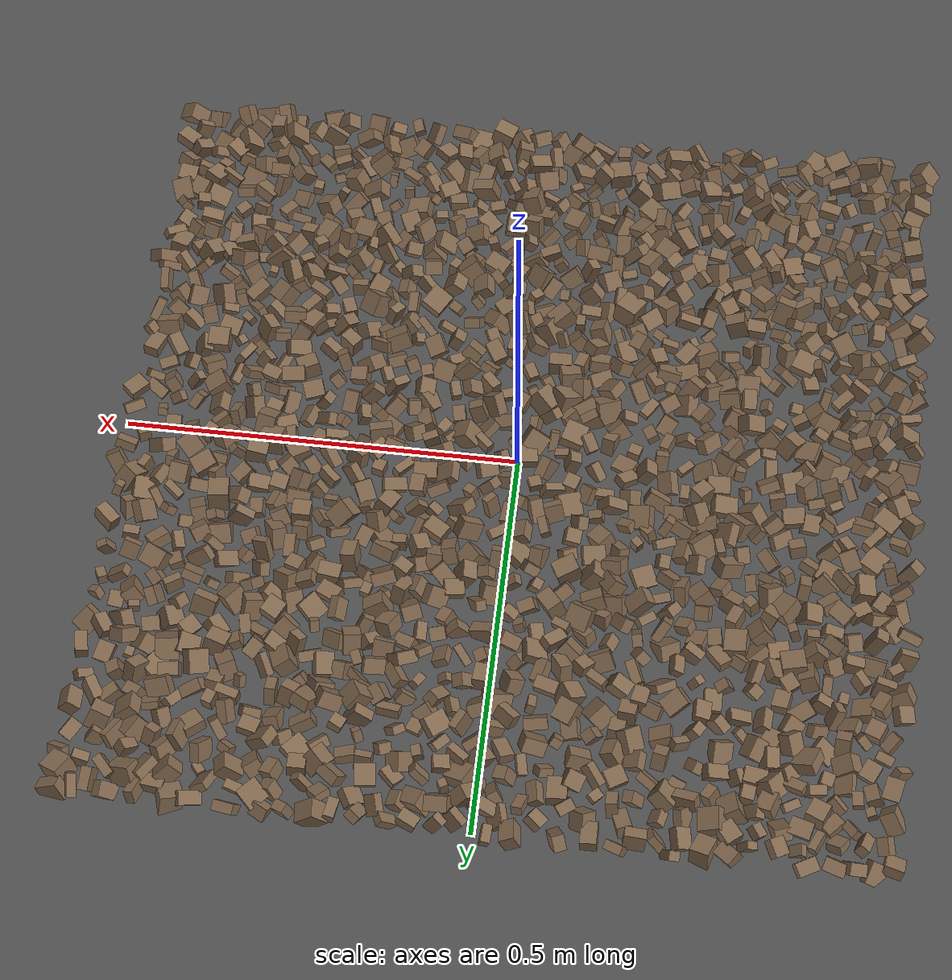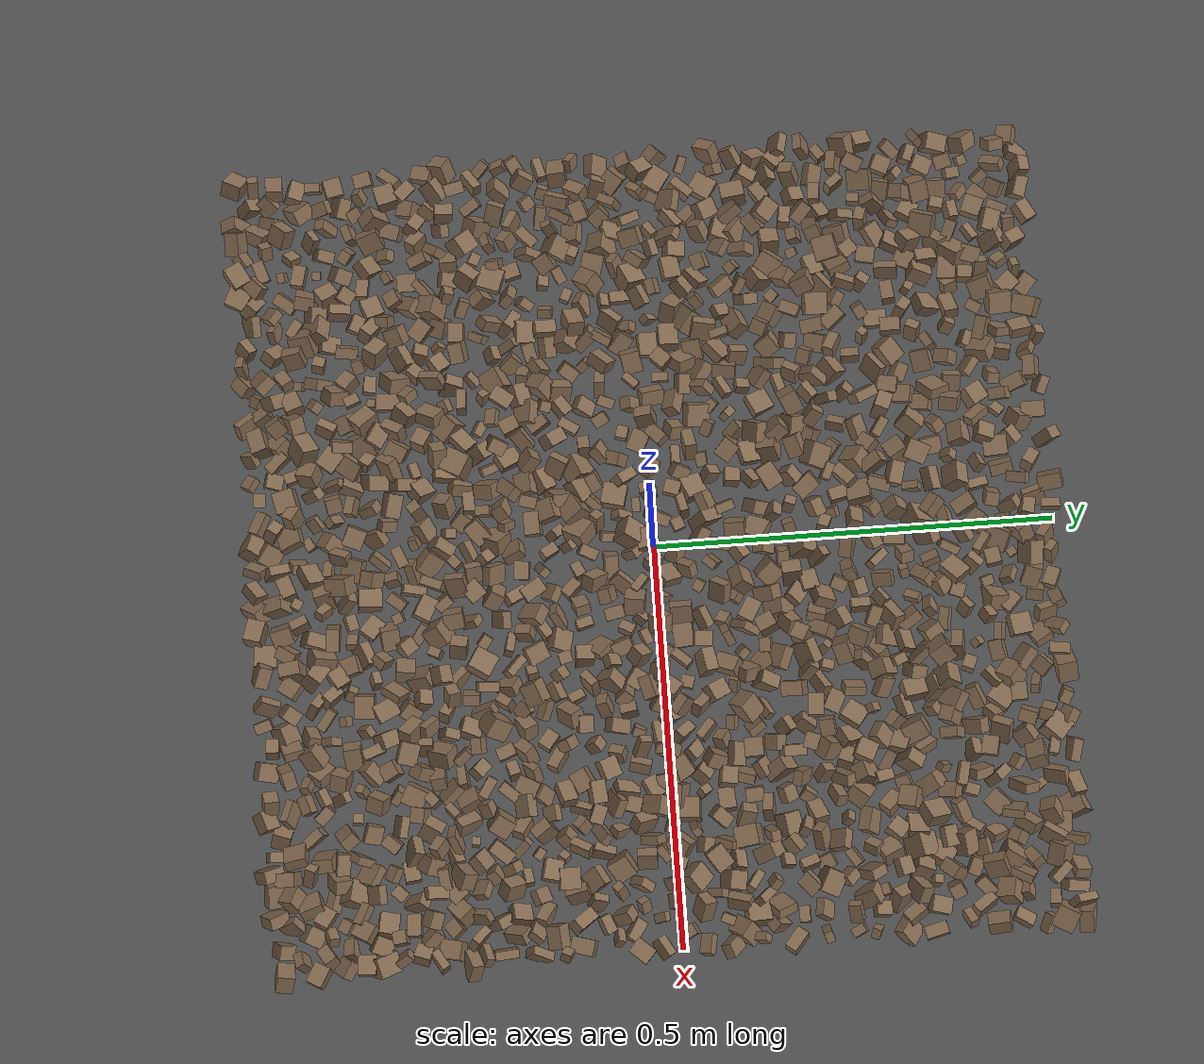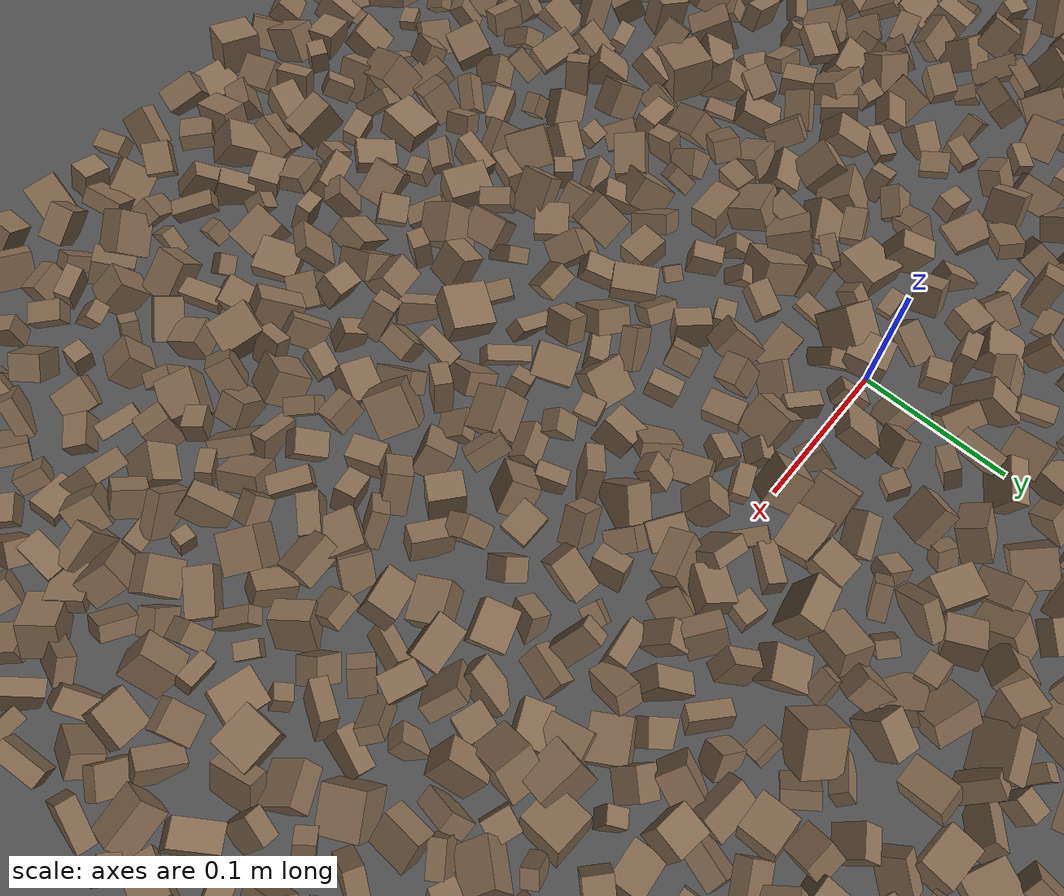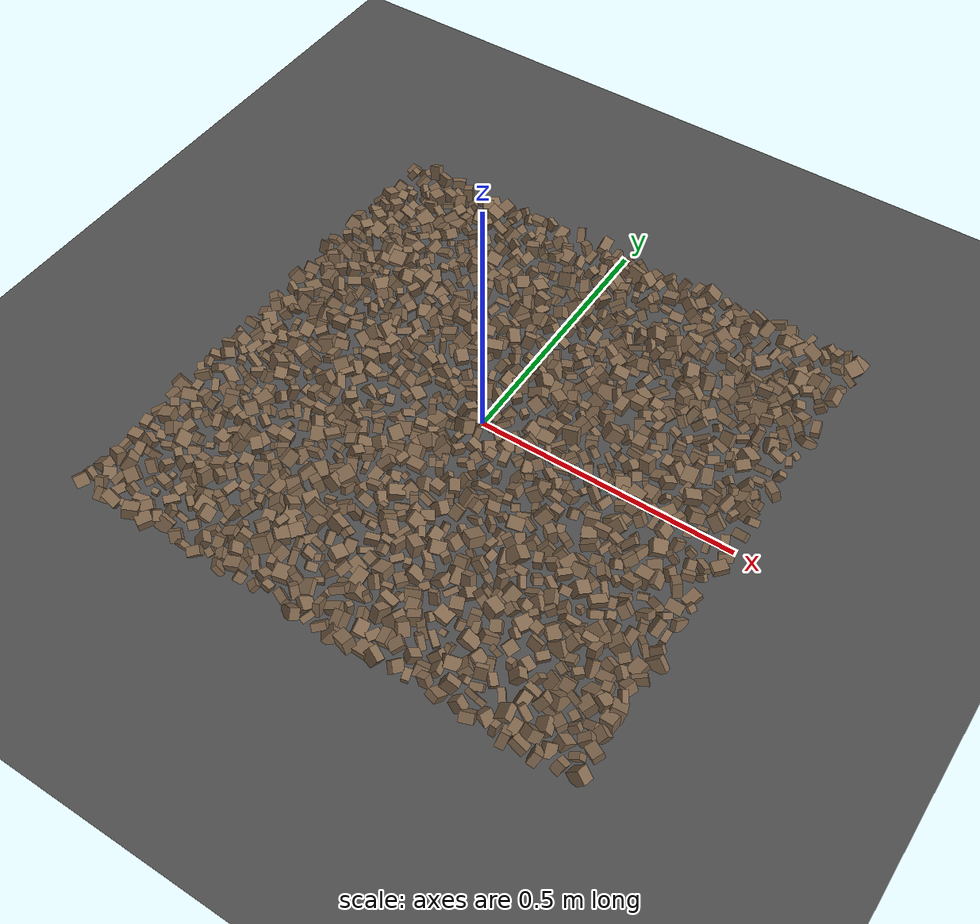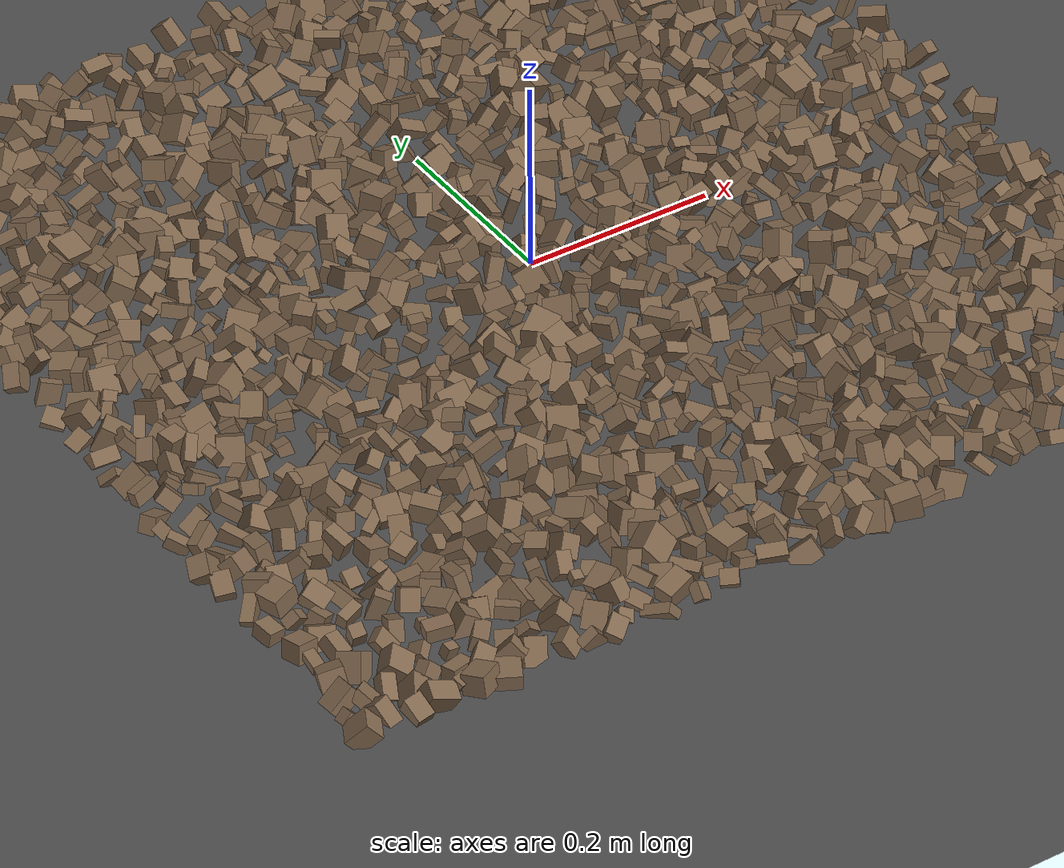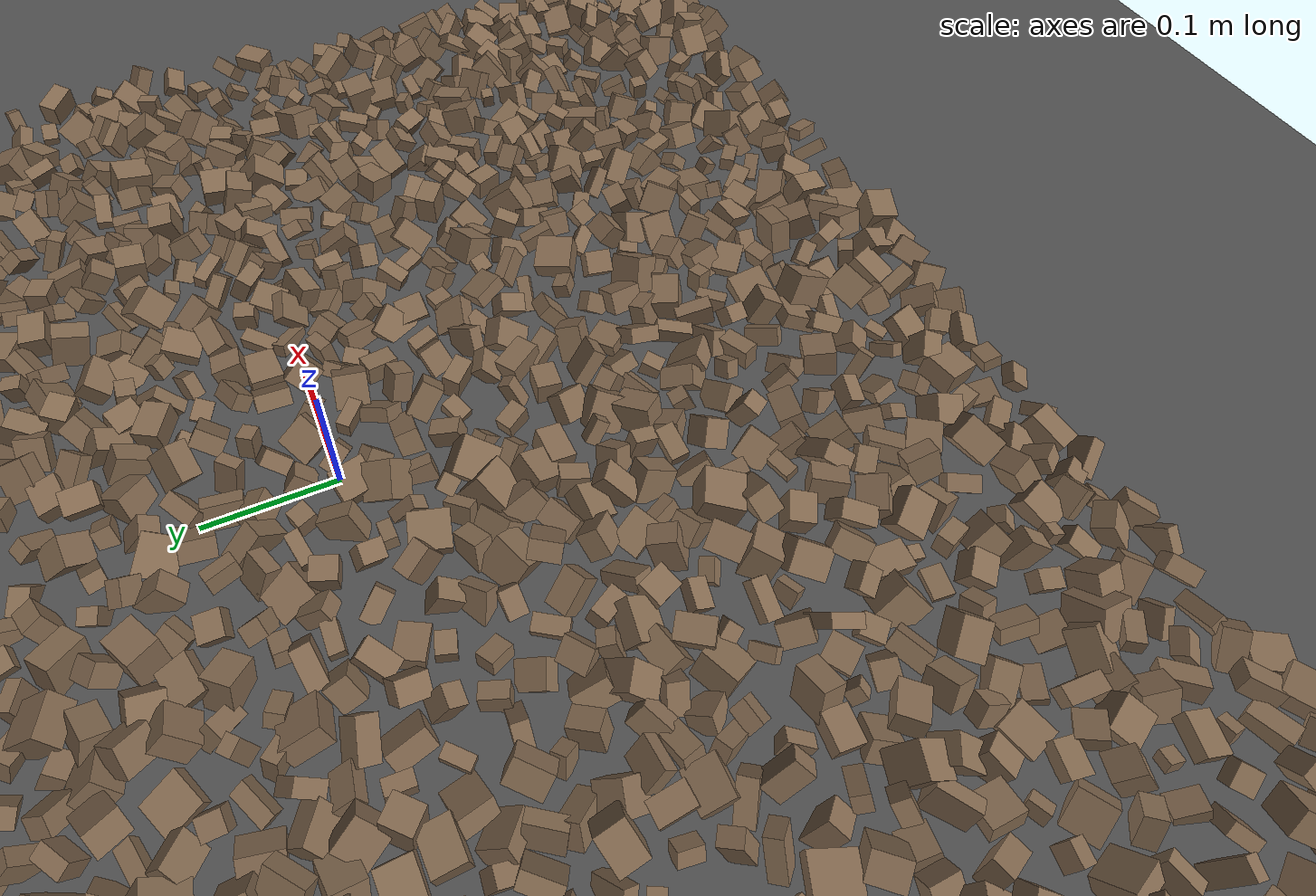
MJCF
<mujoco model="rocky_terrain_scene">
    <compiler angle="radian" inertiafromgeom="true" />
    <option timestep="0.002" gravity="0 0 -9.81" />

    <worldbody>
        <light name="sunlight" pos="5 5 5" dir="-1 -1 -1" diffuse="1 1 1" specular="0.5 0.5 0.5" ambient="0.5 0.5 0.5" />

        <geom name="ground_plane" type="plane" size="50 50 0.1" rgba="0.3 0.3 0.3 1" />

        <body name="rocky_terrain_body">

        <geom name="rock1" type="box" size="0.00558741297210567 0.007104187126355673 0.01124968752210171" pos="-0.4982139432787105 0.3695015622502156 0.003643672888369091" quat="0.19671893501975332 0.16160829905852014 0.17506956675546825 0.46660319916625825" rgba="0.5 0.4 0.3 1" friction="0.7946071869829132 0.9915926742865105 0.8775468418264128" /><geom name="rock2" type="box" size="0.005001930711477574 0.007299152871583849 0.013803080340721027" pos="0.03616527114167989 0.27632131649093894 0.0092224387572535" quat="0.4527346559902018 0.2825180707174128 0.1376687562268635 0.12707851706552195" rgba="0.5 0.4 0.3 1" friction="0.7796000388347174 0.9780376202441625 0.8072437861496962" /><geom name="rock3" type="box" size="0.014197111101214833 0.007328281747639781 0.006938295839927451" pos="-0.31921978422855535 -0.01877957069406022 0.006483009840787415" quat="0.26872521310411723 0.21089714318151265 0.27214468825734983 0.24823295545702032" rgba="0.5 0.4 0.3 1" friction="0.7707682959939348 0.9245073599112639 0.8403486717340923" /><geom name="rock4" type="box" size="0.014960843583808923 0.005860436803607746 0.009918769266543677" pos="0.29905485371690677 -0.15609953207397897 0.0016700716091916739" quat="0.43938529525135467 0.21773779492023104 0.2921017970821291 0.05077511274628529" rgba="0.5 0.4 0.3 1" friction="0.7500432306768028 0.9527932595204442 0.8687392813823777" /><geom name="rock5" type="box" size="0.008115919190396854 0.013209183342860944 0.008016134595900618" pos="-0.4300725937298351 -0.27191745491877806 0.011375033721491344" quat="0.19504511650397593 0.4965766292038009 0.26467686312297745 0.04370139116924559" rgba="0.5 0.4 0.3 1" friction="0.7088297780411191 0.9184091155607754 0.8810457012151616" /><geom name="rock6" type="box" size="0.01256027802292645 0.0054883185822596795 0.0070755416924704094" pos="0.1934947876812162 0.4081827949342335 0.003475243430919634" quat="0.5022097223297559 0.23913493956977427 0.05199026319789839 0.20666507490257147" rgba="0.5 0.4 0.3 1" friction="0.7552091421441343 0.9961855097285164 0.8568993601927607" /><geom name="rock7" type="box" size="0.01112831080220059 0.014350774289017057 0.013967181607157857" pos="0.030372758243612408 -0.41389382609917647 0.0033039983280839435" quat="0.29153799785460044 0.15093864249266947 0.1860368325183146 0.3714865271344154" rgba="0.5 0.4 0.3 1" friction="0.7684757019003658 0.9381985451747974 0.8259482324268088" /><geom name="rock8" type="box" size="0.007778940425569116 0.010952775341907275 0.014118981266572843" pos="0.42161926302988195 0.36648024691760794 0.00048020956282819605" quat="0.5335711402061245 0.04558448347704568 0.07788603649276131 0.3429583398240686" rgba="0.5 0.4 0.3 1" friction="0.726400939619805 0.9896925476377932 0.842019282341498" /><geom name="rock9" type="box" size="0.012105369577669436 0.007631569940679586 0.00790724358369473" pos="0.0799566448155058 -0.053417478116953965 0.010683265583763448" quat="0.19736236059939186 0.250691057028526 0.27765310197291937 0.27429348039916274" rgba="0.5 0.4 0.3 1" friction="0.7740598355269184 0.9009137548215002 0.8893968393401803" /><geom name="rock10" type="box" size="0.008808613810860386 0.005214605118754291 0.012561533890548005" pos="-0.21502935459318795 0.48485284568184495 0.007050553368489042" quat="0.29477931774025573 0.21453733280305146 0.021891089293953527 0.46879226016273934" rgba="0.5 0.4 0.3 1" friction="0.7156668534542522 0.9094405643317169 0.8004481630490907" /><geom name="rock11" type="box" size="0.00947320939290934 0.013417115433592489 0.012195678459621316" pos="0.012460192473765508 0.4570718570419543 0.014611512474108955" quat="0.122786327774319 0.24210480060332354 0.4677983141134221 0.1673105575089353" rgba="0.5 0.4 0.3 1" friction="0.7764462286698619 0.9484670426107394 0.8870682913831462" /><geom name="rock12" type="box" size="0.007807033493480912 0.011774892595822067 0.012309619339652234" pos="0.2536790253107565 -0.47068434617967914 0.013464445288145315" quat="0.1891479505746946 0.2454485931978084 0.3935113519145481 0.17189210431294885" rgba="0.5 0.4 0.3 1" friction="0.7878689431128607 0.9787713004203582 0.8532208115052358" /><geom name="rock13" type="box" size="0.013295398203886418 0.012729137293691722 0.009618871655203561" pos="-0.08755383003990325 -0.20178245625658775 0.0042868298526199285" quat="0.31589231305485904 0.1086088088416671 0.48925472045725166 0.08624415764622231" rgba="0.5 0.4 0.3 1" friction="0.7615459064198559 0.9531724217285826 0.8067363617782511" /><geom name="rock14" type="box" size="0.010498704261432838 0.005716660111699373 0.01029837779420528" pos="0.04919530806877037 -0.12995551995439236 0.00813911827965457" quat="0.2331197650753111 0.380593144031429 0.04709095839555718 0.33919613249770264" rgba="0.5 0.4 0.3 1" friction="0.7823186432628014 0.9425174967611932 0.8280487455703837" /><geom name="rock15" type="box" size="0.01279990245440842 0.008716503802904597 0.00708989800314973" pos="-0.4476807347676661 -0.4527296859612011 0.002855620294954501" quat="0.19037826147447123 0.39413504951214023 0.15015993944970585 0.2653267495636826" rgba="0.5 0.4 0.3 1" friction="0.7564879906867125 0.9213540813518172 0.8632419805817408" /><geom name="rock16" type="box" size="0.009158127601446771 0.005156957376901782 0.014132675923252996" pos="-0.3373342231490125 0.07720422313453823 0.00964649408201238" quat="0.3159566898743342 0.0344131194064717 0.34463745848655947 0.3049927322326347" rgba="0.5 0.4 0.3 1" friction="0.7124893101005932 0.9899849021584399 0.8954145627935699" /><geom name="rock17" type="box" size="0.00839589666718971 0.008055168591332023 0.011524122461685259" pos="0.24059812314913365 0.472262364635325 0.004471409576230045" quat="0.4591123787421425 0.16580859347037177 0.04825650339904555 0.32682252438844017" rgba="0.5 0.4 0.3 1" friction="0.7086751067696769 0.9861850956336659 0.8247652478160925" /><geom name="rock18" type="box" size="0.006942707434046272 0.005172037681105551 0.009699400254846849" pos="0.08501338691419325 0.27663280910390176 0.01285595231057778" quat="0.04534656410961131 0.25907461205772586 0.24371874594920687 0.451860077883456" rgba="0.5 0.4 0.3 1" friction="0.7788942003722759 0.9763267262586792 0.8365884858259952" /><geom name="rock19" type="box" size="0.005576342868503686 0.007059950084648877 0.009875052963890782" pos="-0.07652034028013344 0.4115306904053929 0.0029766805587459464" quat="0.4218397972575325 0.045644923162357375 0.28604595719529247 0.2464693223848177" rgba="0.5 0.4 0.3 1" friction="0.7545718351547565 0.9235051175869147 0.8280340156716226" /><geom name="rock20" type="box" size="0.014142069397891584 0.012595639683234676 0.008387797807794905" pos="0.41321147275715153 -0.4500857904188874 0.010882871702072982" quat="0.10933539662266689 0.3081868711913301 0.4169491830752665 0.1655285491107365" rgba="0.5 0.4 0.3 1" friction="0.714445851054097 0.9988144719530665 0.8122483306417508" /><geom name="rock21" type="box" size="0.005700900054880823 0.0101937863460232 0.013974162780333851" pos="0.00972389400121021 -0.30051426031110584 0.002820749050429825" quat="0.11397562222356791 0.3588021944621257 0.30012224699607054 0.2270999363182358" rgba="0.5 0.4 0.3 1" friction="0.7317105046028348 0.9798136622071355 0.8925135861482143" /><geom name="rock22" type="box" size="0.00893528386133402 0.00988284976405757 0.007435224728279793" pos="0.47790502387356304 0.011260473704568952 0.00014099152067830468" quat="0.15916536749757218 0.2217006125571361 0.26717478087926916 0.35195923906602256" rgba="0.5 0.4 0.3 1" friction="0.7893440430937746 0.9472666865175067 0.856049004106219" /><geom name="rock23" type="box" size="0.005851998894427231 0.007222505921844622 0.009208883899125329" pos="0.22716290939757566 -0.034586846259181625 0.0004383120642245131" quat="0.151013843427529 0.14826269525675922 0.05053645813627368 0.6501870031794382" rgba="0.5 0.4 0.3 1" friction="0.7796981027831391 0.9263940342957465 0.8138770998057568" /><geom name="rock24" type="box" size="0.010054796108524312 0.005391712078889788 0.005772959886881122" pos="-0.48644710496217325 -0.3962623045786895 0.012364868212661959" quat="0.24611628492131626 0.2675237076889305 0.20962247859855096 0.2767375287912022" rgba="0.5 0.4 0.3 1" friction="0.795619205076236 0.9049304483042341 0.8300661580094661" /><geom name="rock25" type="box" size="0.006521453844437297 0.00947711217422435 0.006132669916899458" pos="-0.14490428656062637 0.0779499214375452 0.00794078625345176" quat="0.5004145070121778 0.14781351599255776 0.048126880709414545 0.30364509628584996" rgba="0.5 0.4 0.3 1" friction="0.7487685989909388 0.9217815152950989 0.8645190805325443" /><geom name="rock26" type="box" size="0.01022894825499897 0.009708239101372996 0.007052813786209542" pos="0.17209648881682993 -0.2379884507363259 0.00841664519921767" quat="0.1985966227701963 0.3193816198957802 0.30569357247163614 0.17632818486238744" rgba="0.5 0.4 0.3 1" friction="0.7754335634297663 0.9255857959400069 0.8833305391008959" /><geom name="rock27" type="box" size="0.010525592035067286 0.012319500494664352 0.011118588385399204" pos="-0.3584163166538399 -0.2864307078939401 0.003640914347623582" quat="0.01273706832601234 0.5337510832366603 0.021364949211935942 0.4321468992253913" rgba="0.5 0.4 0.3 1" friction="0.763117614984886 0.9618737084743471 0.8258374257163961" /><geom name="rock28" type="box" size="0.005391666175627795 0.006982043246627099 0.007378300817198715" pos="0.4251334945228544 0.1195339361714125 0.011028308585202932" quat="0.5013935959490485 0.0350243535113022 0.20077887637156738 0.26280317416808174" rgba="0.5 0.4 0.3 1" friction="0.717278038710476 0.9070256338745025 0.8038755711572715" /><geom name="rock29" type="box" size="0.009673319207144995 0.010421159420794832 0.009541356704702152" pos="0.13419124195544974 -0.02717343618196222 0.00627036888483079" quat="0.3521076723867197 0.02079255543982774 0.3274466519934654 0.2996531201799872" rgba="0.5 0.4 0.3 1" friction="0.7649080144028639 0.9263495990512592 0.833693826933336" /><geom name="rock30" type="box" size="0.007705195241011473 0.012644118977679492 0.014547208465894391" pos="-0.010209222755877545 0.4664514692996583 0.007719368917166761" quat="0.13921354726217716 0.4524953919980556 0.33821612391708744 0.07007493682267975" rgba="0.5 0.4 0.3 1" friction="0.7734785255045421 0.9878366331777388 0.8605456210048178" /><geom name="rock31" type="box" size="0.008764680392173908 0.01246748732911963 0.012298760638154889" pos="0.17807865465102113 0.12707071891795374 0.0056188318846192575" quat="0.12339870913703055 0.02942119746516293 0.5290999518332897 0.3180801415645168" rgba="0.5 0.4 0.3 1" friction="0.708409924784773 0.9036744401575442 0.8570955184637007" /><geom name="rock32" type="box" size="0.005029734959203878 0.011925905739663428 0.0073244853764797575" pos="-0.3215055770497165 0.4797331143925905 0.00159710235902904" quat="0.3131222344143065 0.14192048200042803 0.20439457572485556 0.3405627078604098" rgba="0.5 0.4 0.3 1" friction="0.7474314720429031 0.9549763058930875 0.8595414395419669" /><geom name="rock33" type="box" size="0.010712412035001943 0.013872966967670673 0.010732789849620897" pos="-0.2904166800468505 -0.08044000902939596 0.014145236386164751" quat="0.17118868098442477 0.33630710782280293 0.4143553589613175 0.07814885223145479" rgba="0.5 0.4 0.3 1" friction="0.7050369140722716 0.9390505337534099 0.8473600597703878" /><geom name="rock34" type="box" size="0.012682766569515535 0.014996340236920497 0.0071806188806790815" pos="-0.12205024709315926 -0.3221295522175255 0.014443664831701007" quat="0.3677099408937839 0.31969922579880433 0.0051867079623145245 0.30740412534509726" rgba="0.5 0.4 0.3 1" friction="0.7145276187651357 0.9318254046629666 0.8844874694116432" /><geom name="rock35" type="box" size="0.007846767781318681 0.006946378819429945 0.011955427437050819" pos="-0.010844490730173906 0.36507254699524294 0.003957341643976501" quat="0.48662835671252014 0.061545963281629514 0.305528610613974 0.1462970693918762" rgba="0.5 0.4 0.3 1" friction="0.7341113596182459 0.9907333910916464 0.8745585763521813" /><geom name="rock36" type="box" size="0.006056206928032361 0.01246572392287061 0.012145502457493192" pos="-0.2108319136907394 -0.05309805028364867 0.00022719850622039293" quat="0.36801129935467175 0.1491250475257097 0.14700939680593936 0.33585425631367916" rgba="0.5 0.4 0.3 1" friction="0.7570703118557436 0.9087459082881783 0.8791049299646192" /><geom name="rock37" type="box" size="0.01484765620719368 0.006704694324531886 0.012445122965855874" pos="-0.4598614881099302 0.1725964395088826 0.010442383705197667" quat="0.10792579858871025 0.30305687162643186 0.138421242008024 0.4505960877768339" rgba="0.5 0.4 0.3 1" friction="0.7830662488508225 0.9781289303096581 0.8968166284491913" /><geom name="rock38" type="box" size="0.011360367801661865 0.012537447779939238 0.008393988133610685" pos="-0.3565325086719645 0.4795514087061099 0.012474964328691657" quat="0.23976145239251287 0.13752200058076003 0.32692277553619503 0.29579377149053193" rgba="0.5 0.4 0.3 1" friction="0.7162629699330701 0.9337808330514147 0.8736886462816725" /><geom name="rock39" type="box" size="0.014628552156642868 0.013486770124804391 0.007963658780783544" pos="-0.07165182755508015 -0.1142722099351402 0.00299642647734966" quat="0.10017348049165099 0.4987365094911278 0.09916293479788511 0.30192707521933615" rgba="0.5 0.4 0.3 1" friction="0.7292512808678407 0.9930122899679534 0.8510332658347509" /><geom name="rock40" type="box" size="0.008148095651195803 0.010976197652831941 0.006971084871787898" pos="0.26125681698663483 -0.23271924806346866 0.010896961150734569" quat="0.20025239980467502 0.559856143312145 0.22297492496161428 0.01691653192156576" rgba="0.5 0.4 0.3 1" friction="0.7817437167971328 0.9991555755161136 0.8619090913979083" /><geom name="rock41" type="box" size="0.01314756738083088 0.010380915221801686 0.007719971302292415" pos="0.40867212518448937 -0.295746547827901 0.013627189646338814" quat="0.3032727625515995 0.20230968383016368 0.27801311485451613 0.2164044387637207" rgba="0.5 0.4 0.3 1" friction="0.7368278671551812 0.9455349037151668 0.8651112609527828" /><geom name="rock42" type="box" size="0.008267597280342922 0.014576036105564766 0.009965628441352667" pos="-0.1917475363873299 0.0108204231725606 0.0022350294678898787" quat="0.04350944471193239 0.581345027246032 0.08889079454226723 0.28625473349976843" rgba="0.5 0.4 0.3 1" friction="0.7579686266205397 0.9395893106259812 0.8897468269789539" /><geom name="rock43" type="box" size="0.01105218162305957 0.008352751273388241 0.013440843962623093" pos="-0.1639467466413531 -0.3351738666030716 0.013703664016352727" quat="0.3891419519551886 0.2571753074041865 0.2391876057443445 0.11449513489628042" rgba="0.5 0.4 0.3 1" friction="0.7535006567636134 0.9955184807630215 0.8565498373467995" /><geom name="rock44" type="box" size="0.0096297524674797 0.009009604743366269 0.009717461747840769" pos="0.2545588163091703 0.13189464757692648 0.013288342714212597" quat="0.16750764681248978 0.3735233734082098 0.14864225554781213 0.3103267242314882" rgba="0.5 0.4 0.3 1" friction="0.7741851007117789 0.9636099658663205 0.8745032366588804" /><geom name="rock45" type="box" size="0.005693758700725097 0.012001897721336311 0.0066471335408186" pos="0.48608030740054964 -0.3408934362416538 0.009011296895518935" quat="0.5515079505726913 0.08264967035755194 0.17757105524962363 0.18827132382013317" rgba="0.5 0.4 0.3 1" friction="0.748014296370584 0.9823621155921084 0.8134270162337024" /><geom name="rock46" type="box" size="0.00859150983125233 0.00866433265232372 0.009979459684227093" pos="-0.3585602409684391 0.08394804914174092 0.0044595447090092135" quat="0.15677206599870888 0.28072405268768563 0.25079786414411 0.3117060171694956" rgba="0.5 0.4 0.3 1" friction="0.7178026655306289 0.9972709807281326 0.8160669796927995" /><geom name="rock47" type="box" size="0.008071184179340798 0.0073380073975692645 0.009506748651602753" pos="0.37387148303206197 0.037427110244514394 0.0019905449377723406" quat="0.3480913419046778 0.19285123637230195 0.3248383760870321 0.13421904563598827" rgba="0.5 0.4 0.3 1" friction="0.7896176618428816 0.9914371617440642 0.81180014486471" /><geom name="rock48" type="box" size="0.0059648008403928345 0.01221955726214501 0.006192782625257857" pos="0.42274976054255453 -0.07055831327332063 0.007860031572345556" quat="0.3590066578089361 0.3704083157472532 0.022221324198706593 0.24836370224510412" rgba="0.5 0.4 0.3 1" friction="0.7545282783012595 0.934411295691608 0.8169045197510888" /><geom name="rock49" type="box" size="0.014958673784221874 0.013613808266126567 0.014221900323992964" pos="-0.066514902139018 -0.04451147995466653 0.0010305030849349056" quat="0.30503143204076943 0.258133881369043 0.19442191043338916 0.24241277615679838" rgba="0.5 0.4 0.3 1" friction="0.7993817115294704 0.9324387503359961 0.8939859296209772" /><geom name="rock50" type="box" size="0.00504571696082029 0.01272150032581284 0.007876095540196368" pos="0.1427863976943219 -0.3542659373198177 0.012252562738924102" quat="0.2825484351554197 0.16131217873904558 0.28331785529822806 0.27282153080730664" rgba="0.5 0.4 0.3 1" friction="0.7107109248170995 0.9929648954846672 0.8491198438001679" /><geom name="rock51" type="box" size="0.008128879982378531 0.014975056757146658 0.014480449452489243" pos="0.14929982377843154 0.05516564497623555 0.011043240323443183" quat="0.2917592356065271 0.16797419301237948 0.28982360848362315 0.2504429628974702" rgba="0.5 0.4 0.3 1" friction="0.7548677238267952 0.9022487326718966 0.8557836923022332" /><geom name="rock52" type="box" size="0.014279529740957971 0.010448997464929652 0.014815905185599918" pos="-0.10020291071193566 0.2103098067195427 0.010953715261001858" quat="0.34721251305921225 0.2420080766994876 0.3121931164674875 0.09858629377381264" rgba="0.5 0.4 0.3 1" friction="0.7224328176431384 0.9982756539856387 0.8474485941265304" /><geom name="rock53" type="box" size="0.006260965969064843 0.010034817546283204 0.008038783825858988" pos="-0.4204975088801791 -0.2392086147792578 0.013575069800340617" quat="0.2661237935606834 0.19416049250061376 0.39728788989100605 0.1424278240476967" rgba="0.5 0.4 0.3 1" friction="0.744972780755762 0.9231119528449494 0.8793816249136643" /><geom name="rock54" type="box" size="0.007441319300266478 0.005274224672760007 0.008164893899733995" pos="-0.44843730795514547 -0.12861063416156482 0.010221263844369902" quat="0.45273203159791164 0.31530532304153347 0.21946944953468533 0.01249319582586958" rgba="0.5 0.4 0.3 1" friction="0.7506674696723183 0.9002298870462774 0.8782522853097033" /><geom name="rock55" type="box" size="0.011173983459705548 0.010113069893793927 0.008203816882245914" pos="-0.2282979284565484 -0.09031153600504138 0.01017233498689012" quat="0.3277751665391646 0.3493560335827551 0.23454588830311224 0.08832291157496808" rgba="0.5 0.4 0.3 1" friction="0.7483223374275526 0.9093996807496609 0.8624037258838627" /><geom name="rock56" type="box" size="0.007525445073664592 0.006046057237648301 0.01065943927304163" pos="-0.23025970440365506 -0.3410070591154567 0.002707592472499754" quat="0.30973119352564804 0.22273324598812472 0.24416616252033743 0.22336939796588984" rgba="0.5 0.4 0.3 1" friction="0.7349226793584546 0.9712171823733823 0.828394805784778" /><geom name="rock57" type="box" size="0.014893860746111466 0.011878924039010572 0.012876181419160398" pos="0.4292766876907441 0.18708250562082096 0.006129318595651774" quat="0.05924693107729514 0.13397733899396363 0.4802842667263637 0.3264914632023776" rgba="0.5 0.4 0.3 1" friction="0.7711645360214543 0.9298027798507983 0.8387416998956617" /><geom name="rock58" type="box" size="0.01125109257982796 0.00905986822646699 0.012135503741469197" pos="0.3273798828268729 -0.4823184134571181 0.0004125425754933404" quat="0.17587122782387357 0.41889424348094073 0.3012690649916491 0.10396546370353665" rgba="0.5 0.4 0.3 1" friction="0.7069339449999658 0.9019400317971186 0.843844125758116" /><geom name="rock59" type="box" size="0.011270749190572273 0.011377385019908868 0.014059048732819258" pos="0.17176486969103855 -0.15922368182329283 0.011826989493086077" quat="0.10631192728034196 0.31950205016544514 0.2678690451837284 0.3063169773704846" rgba="0.5 0.4 0.3 1" friction="0.722830851844079 0.9584182671069126 0.8061016600373403" /><geom name="rock60" type="box" size="0.008681474885324907 0.007414949541504394 0.011752841569530055" pos="-0.15183391622234355 0.210418336860567 0.004975464856411928" quat="0.2685878682864102 0.39223028927248477 0.31736857603650775 0.021813266404597402" rgba="0.5 0.4 0.3 1" friction="0.7256028268065008 0.9597364559263271 0.8880483706675634" /><geom name="rock61" type="box" size="0.013032422095520288 0.006778911573796812 0.007381702313083466" pos="0.27039773863243377 -0.03544014702090681 0.004643831018197009" quat="0.17949902599902492 0.39420599666291406 0.2938956863553449 0.1323992909827162" rgba="0.5 0.4 0.3 1" friction="0.7438735300449849 0.9658070325687336 0.8648505468403352" /><geom name="rock62" type="box" size="0.00921472931305484 0.014677116963486118 0.005936286268692414" pos="-0.32929426098850056 -0.1596602499596933 0.011947223137117676" quat="0.0060771494931532504 0.2793025155274309 0.38775413610495024 0.3268661988744656" rgba="0.5 0.4 0.3 1" friction="0.7210809201220945 0.9222156405323341 0.824653919257294" /><geom name="rock63" type="box" size="0.010734224931500426 0.008370515067981052 0.011182607649602175" pos="-0.11255154632467113 0.42274885649701455 0.011090529742197767" quat="0.3818177107722814 0.1905318377380862 0.2048152429725204 0.22283520851711203" rgba="0.5 0.4 0.3 1" friction="0.7259573643272262 0.9253485693818104 0.8335645986035763" /><geom name="rock64" type="box" size="0.010878832335762013 0.014960605608868041 0.009551447125594095" pos="-0.23555065363736305 0.02693727388439504 0.013550375456662952" quat="0.33640975733244954 0.3662212820026601 0.14646185588607052 0.15090710477881994" rgba="0.5 0.4 0.3 1" friction="0.7709506829482023 0.9600136675206205 0.8467278288889689" /><geom name="rock65" type="box" size="0.010397924997341875 0.011012431131221658 0.009358483027753314" pos="-0.37166031298297564 -0.3683382115493308 0.01108560258366452" quat="0.32985421722551106 0.25882432972518543 0.3157354431281113 0.09558600992119215" rgba="0.5 0.4 0.3 1" friction="0.7110118212640714 0.9794700340365169 0.882257008363325" /><geom name="rock66" type="box" size="0.010793526853572067 0.009356107679738396 0.011719894204281585" pos="-0.06991263817303994 -0.25676586817544567 0.009456937116853572" quat="0.23270070083605435 0.1050959717305406 0.5675923801507845 0.09461094728262058" rgba="0.5 0.4 0.3 1" friction="0.7529802967601466 0.9747669796003694 0.8097248314482693" /><geom name="rock67" type="box" size="0.008921702490364615 0.0063664180820433725 0.0076001448539628706" pos="-0.394125556120541 -0.3113566585167805 0.005268773006397924" quat="0.19562453118942336 0.3199551553805057 0.1406361591827276 0.34378415424734343" rgba="0.5 0.4 0.3 1" friction="0.7071460669157836 0.9047512427898196 0.8616705191600401" /><geom name="rock68" type="box" size="0.007465346327484738 0.013463461764730022 0.010647818211681552" pos="-0.03521267749164003 0.20389234316806726 0.011155093094522344" quat="0.20526951113376088 0.19514813023477073 0.36869162344166134 0.2308907351898071" rgba="0.5 0.4 0.3 1" friction="0.7971092304110442 0.9898350616890566 0.8667872057002531" /><geom name="rock69" type="box" size="0.01231787308244834 0.014651519294629448 0.005214673710657705" pos="0.027091499608623004 0.3661455924324738 0.01230038583134558" quat="0.2902996191032753 0.3355686665392253 0.23222216242240545 0.1419095519350939" rgba="0.5 0.4 0.3 1" friction="0.7640933254673481 0.9458595371041517 0.8142402068346587" /><geom name="rock70" type="box" size="0.007178212319751314 0.007038253110670598 0.008707933229297363" pos="-0.2536886345618702 0.38805094030478615 0.006481638975542638" quat="0.229181639837924 0.4021020124330095 0.3175963852915287 0.0511199624375378" rgba="0.5 0.4 0.3 1" friction="0.711215369856024 0.9689505990568884 0.8241630537219176" /><geom name="rock71" type="box" size="0.011217859425553912 0.009071430282690016 0.014880556049863769" pos="-0.17032722144300982 0.18368396958716326 0.013518583363467312" quat="0.1064988382553206 0.2728513607464221 0.4054540127560129 0.2151957882422444" rgba="0.5 0.4 0.3 1" friction="0.7317750110191273 0.9874267660898336 0.8503686428158896" /><geom name="rock72" type="box" size="0.014758623279942127 0.011299862318745142 0.012527348270009432" pos="-0.3489506769134858 0.17091624306338338 0.009188225337512589" quat="0.2687195907355027 0.3942683874978207 0.22359295395276452 0.11341906781391208" rgba="0.5 0.4 0.3 1" friction="0.7298504903162774 0.909265251327733 0.8844802828574597" /><geom name="rock73" type="box" size="0.005736011587706501 0.011025644100518494 0.005910933670424116" pos="-0.059999327030490934 -0.39443006383331136 0.008187669396972934" quat="0.09728249681831534 0.2676232489910734 0.24551969025734469 0.38957456393326645" rgba="0.5 0.4 0.3 1" friction="0.7321890854986105 0.9776389800238736 0.8940750976732823" /><geom name="rock74" type="box" size="0.0056283760031939365 0.013863089026854982 0.01336457017576604" pos="-0.31699861774853566 -0.4841566648541207 0.0064401468324566434" quat="0.25902745885383804 0.2091320677704694 0.38965277972286827 0.1421876936528244" rgba="0.5 0.4 0.3 1" friction="0.7367739771925165 0.9972075006617359 0.8981666630210337" /><geom name="rock75" type="box" size="0.014159654303771578 0.013152811366294394 0.008110077813656337" pos="0.4558735873018107 -0.11868613419813046 0.01036450262270537" quat="0.2431605345556681 0.09619502132001645 0.36039792869372417 0.3002465154305912" rgba="0.5 0.4 0.3 1" friction="0.7121077508061976 0.9806828070479598 0.8590129870903129" /><geom name="rock76" type="box" size="0.0083174439904646 0.007784751407173553 0.010793416401323143" pos="0.03206750987746587 0.3108127595614054 0.010801814775919653" quat="0.34989989063163635 0.07125521458874602 0.17817331961186303 0.40067157516775465" rgba="0.5 0.4 0.3 1" friction="0.7282748302867739 0.9873001993926324 0.8185437298206689" /><geom name="rock77" type="box" size="0.013334242257924102 0.007039403315252233 0.007297332812239913" pos="0.16047216386675178 0.24848494100952112 0.006363256250898054" quat="0.47431436354862044 0.11102504962018347 0.2845678923631591 0.13009269446803695" rgba="0.5 0.4 0.3 1" friction="0.7269420431364264 0.9426528594576082 0.8903787012377624" /><geom name="rock78" type="box" size="0.008805385863425615 0.01494390032425795 0.00780334389250021" pos="0.36426604130852236 -0.21274498065845338 0.009599605127842546" quat="0.2514051758064556 0.04195476881203051 0.06324980352568009 0.6433902518558338" rgba="0.5 0.4 0.3 1" friction="0.7267301972860822 0.9358487928164694 0.8307424590914898" /><geom name="rock79" type="box" size="0.0146182970423928 0.012691387900238056 0.006776030091372683" pos="0.2655324875731081 0.15319249105085075 0.0053199467638063965" quat="0.2682371111871757 0.2294860160725515 0.29613161846160174 0.20614525427867103" rgba="0.5 0.4 0.3 1" friction="0.7830648890965332 0.970693500291325 0.8925369280586477" /><geom name="rock80" type="box" size="0.00532122454184295 0.010675442849632236 0.007185153441546599" pos="0.4934427350199385 0.17899099630815474 0.007872424510692672" quat="0.1530434072756596 0.26810304076356617 0.34698433654108546 0.23186921541968886" rgba="0.5 0.4 0.3 1" friction="0.7334871540171392 0.9290908636806966 0.8136229700688029" /><geom name="rock81" type="box" size="0.013886496435981856 0.011564695944881758 0.012427598346503203" pos="0.45746234926609075 0.405335800942369 0.012933637579141056" quat="0.4690760801026405 0.13529934662556195 0.31978840206481185 0.07583617120698559" rgba="0.5 0.4 0.3 1" friction="0.7159240836885947 0.98166024761591 0.8062018799835677" /><geom name="rock82" type="box" size="0.013959148616549864 0.014913259495701211 0.0067325247377999255" pos="0.44884731905141306 -0.21684728490343785 0.0102250893554777" quat="0.04877214313257092 0.3888502690212039 0.1964795650547428 0.3658980227914824" rgba="0.5 0.4 0.3 1" friction="0.7222908566167917 0.9229780584574312 0.899737416369494" /><geom name="rock83" type="box" size="0.013799471748612315 0.014739654455019322 0.014272447803151723" pos="0.3947045319617255 0.3017019682025194 0.003456935363842834" quat="0.34162125165589485 0.12001772070865739 0.34481438337298714 0.19354664426246057" rgba="0.5 0.4 0.3 1" friction="0.7913794458517727 0.9073218814608223 0.8454576217834043" /><geom name="rock84" type="box" size="0.014244149918507105 0.014845307054454096 0.009186213953467498" pos="0.28764351633372665 0.13660137696801578 0.004899986186485561" quat="0.39969838318365675 0.020289403588331006 0.35596352717008034 0.22404868605793196" rgba="0.5 0.4 0.3 1" friction="0.7874868667991053 0.9047521005300825 0.8862349544736841" /><geom name="rock85" type="box" size="0.006484285735511287 0.009925928964502144 0.013837243413229033" pos="0.28953817663642556 0.49945592220323476 0.0026504974887245885" quat="0.2850809201379103 0.2606474259335976 0.3082253410847428 0.14604631284374936" rgba="0.5 0.4 0.3 1" friction="0.7712709333649446 0.9163012408519005 0.8466864997726463" /><geom name="rock86" type="box" size="0.011779688593535592 0.008717115075672823 0.014318950951046048" pos="0.3911870202313398 0.05260320182179412 0.013894440075511496" quat="0.16314688404655173 0.18324465076881402 0.3678532985305798 0.2857551666540545" rgba="0.5 0.4 0.3 1" friction="0.7761184600934952 0.9280812225288714 0.8067619759757979" /><geom name="rock87" type="box" size="0.007815891199301445 0.009768500975176505 0.012874552638934975" pos="-0.39829996367353226 0.0856040696342335 0.004611377179417148" quat="0.19748337541508135 0.11817798222884489 0.5242038754204789 0.16013476693559495" rgba="0.5 0.4 0.3 1" friction="0.7849443939974695 0.9845965659903553 0.8411990338098742" /><geom name="rock88" type="box" size="0.010659110137957378 0.012160331699665006 0.01045994296131603" pos="-0.4651898526060414 0.3210127792708837 0.010883102456768153" quat="0.3038242628680591 0.3036745202403963 0.2270672175777885 0.165433999313756" rgba="0.5 0.4 0.3 1" friction="0.7189081994086485 0.9943431761486188 0.8333301347936609" /><geom name="rock89" type="box" size="0.011383393511726781 0.014957408972977069 0.014890950806921315" pos="-0.15151553603802226 -0.4271541063900639 0.014549259082912146" quat="0.33052288998733803 0.06753762610454211 0.2987529430594914 0.3031865408486284" rgba="0.5 0.4 0.3 1" friction="0.7798196429836745 0.9175426965164666 0.8624164904087449" /><geom name="rock90" type="box" size="0.01174372686622507 0.01485850753320684 0.014533413032983649" pos="0.40321883569427697 -0.3958676164777114 0.0009682203383947596" quat="0.19366982581343906 0.30737410846531965 0.08057461689086451 0.4183814488303768" rgba="0.5 0.4 0.3 1" friction="0.7383082811997849 0.9712485256506824 0.8673448897160428" /><geom name="rock91" type="box" size="0.006971133153164688 0.006951028325675686 0.009192721952832154" pos="-0.4097373552744046 -0.4610323433455378 0.012570672247303051" quat="0.1787980005170272 0.284254753482467 0.43584915102458666 0.1010980949759192" rgba="0.5 0.4 0.3 1" friction="0.7905950568401839 0.9899248100346801 0.8194751825889511" /><geom name="rock92" type="box" size="0.00886932069646092 0.011320454298413555 0.005788206034259432" pos="0.004387133028554313 -0.025986638767062975 0.003749861201795192" quat="0.22684174900838527 0.10759572638667617 0.45344736588484835 0.21211515872009015" rgba="0.5 0.4 0.3 1" friction="0.755246215290613 0.9311661719077267 0.8363702096940961" /><geom name="rock93" type="box" size="0.0059431357053218725 0.009995732015745622 0.00964067735893775" pos="0.4800220010082249 -0.4645830057194147 0.009227932862843244" quat="0.21752784796178012 0.19567550550971963 0.18495153644722997 0.4018451100812703" rgba="0.5 0.4 0.3 1" friction="0.7365301412372671 0.9038708251950671 0.8976417284434371" /><geom name="rock94" type="box" size="0.013387167936584485 0.013338869062601493 0.014716252611100055" pos="-0.34291566995935063 -0.005241123429999384 0.006369786110787067" quat="0.0140327896481254 0.33614030026691155 0.16136156360847237 0.4884653464764907" rgba="0.5 0.4 0.3 1" friction="0.7724084978753225 0.9159247782620771 0.8139923519336162" /><geom name="rock95" type="box" size="0.013343466840775788 0.011899378047068115 0.01166751173315016" pos="-0.09152214648854573 0.2591608276461024 0.01112493292822813" quat="0.280435557093728 0.3318928495884919 0.01981163715762483 0.36785995616015515" rgba="0.5 0.4 0.3 1" friction="0.7925755463311605 0.9824051054505274 0.8587565251495447" /><geom name="rock96" type="box" size="0.008595074055825033 0.009567977687620674 0.006167513198149341" pos="-0.02602959601826238 -0.12056404540324839 0.00037479931774877015" quat="0.017376620792894107 0.32609228836531445 0.2614488009118645 0.3950822899299269" rgba="0.5 0.4 0.3 1" friction="0.7225114937007839 0.9126134681591909 0.8653006538144601" /><geom name="rock97" type="box" size="0.007852069769366084 0.011496152723526639 0.014167701182313083" pos="0.4989314188460846 0.13981320823493482 0.012366249347240201" quat="0.3483856238105411 0.3292547926803354 0.11598906192454653 0.20637052158457692" rgba="0.5 0.4 0.3 1" friction="0.7325586958978018 0.9743603962877572 0.8251230963986864" /><geom name="rock98" type="box" size="0.006902772589974078 0.007695327046367105 0.009508152092661544" pos="0.31072157177679527 -0.22644680971762254 0.01219060220624168" quat="0.28691002165416396 0.07370841740526052 0.49066545169430453 0.14871610924627102" rgba="0.5 0.4 0.3 1" friction="0.7961826801099872 0.9038763601369936 0.8886409996831697" /><geom name="rock99" type="box" size="0.012658685861314214 0.00934816818026158 0.011999337965449547" pos="-0.09138914838002976 -0.2850353807307975 0.0004974768351877718" quat="0.30925451095961354 0.061587634506712854 0.32827278189181613 0.30088507264185743" rgba="0.5 0.4 0.3 1" friction="0.7654578063480102 0.9649742206316367 0.8641642416576725" /><geom name="rock100" type="box" size="0.012149125992298171 0.01125857203426328 0.009636366862879506" pos="-0.1356819959608515 0.16322376293689034 0.013645695579060098" quat="0.0316430577740268 0.2776482182239184 0.4219928053524246 0.2687159186496302" rgba="0.5 0.4 0.3 1" friction="0.7832594111640984 0.9059407169330381 0.8397577188853862" /><geom name="rock101" type="box" size="0.01010572063384086 0.006403352750501867 0.011752586532373282" pos="0.27835565613916813 0.39695754750437184 0.009073870621605343" quat="0.2679975444349441 0.2872758632504345 0.18577040040858595 0.2589561919060354" rgba="0.5 0.4 0.3 1" friction="0.7933588707436902 0.9031539168983366 0.8572693903745172" /><geom name="rock102" type="box" size="0.006032242712902406 0.010183523828882594 0.014460141336282182" pos="0.28669610567167736 -0.270353598369624 0.0037014780265552864" quat="0.35862505294077723 0.33346333633118547 0.2973976026500579 0.010514008077979437" rgba="0.5 0.4 0.3 1" friction="0.7228036539537337 0.9190012515058322 0.8051300589342829" /><geom name="rock103" type="box" size="0.01017184230474788 0.008238525146392834 0.005328588790673501" pos="-0.05972364466707136 -0.06933631645393179 0.008137294132611758" quat="0.3071943517250601 0.4039939569804463 0.19750352397396517 0.09130816732052847" rgba="0.5 0.4 0.3 1" friction="0.7976181811663866 0.951681751138447 0.856196083767045" /><geom name="rock104" type="box" size="0.014579709685002842 0.011967297956787287 0.005299943814946143" pos="-0.41381035237079733 0.05104627055315447 0.009234212413177423" quat="0.4404893553022897 0.31666338908671493 0.09110380616555057 0.15174344944544474" rgba="0.5 0.4 0.3 1" friction="0.7223513840568675 0.9297442953176659 0.8218001631939404" /><geom name="rock105" type="box" size="0.012677071844616451 0.0069147386758229385 0.006981019736156981" pos="-0.16373486726171005 -0.1322954485046186 0.009146335932096529" quat="0.1649325939548104 0.19947194423015557 0.2753110512110819 0.3602844106039521" rgba="0.5 0.4 0.3 1" friction="0.7397193763077612 0.9068460281116093 0.8581549069279458" /><geom name="rock106" type="box" size="0.007022137528856007 0.013158358702197361 0.006184921844068949" pos="0.05203647399791311 0.053314200527157185 0.0038802066686449066" quat="0.07221032428956631 0.15742442114926308 0.3753483443742517 0.395016910186919" rgba="0.5 0.4 0.3 1" friction="0.7868643958557165 0.9581232410179766 0.8506492595783446" /><geom name="rock107" type="box" size="0.01329083637990261 0.013543887566035022 0.010742106655514413" pos="0.3191053219568034 0.32059378105336866 0.004910685956368264" quat="0.3662372017333673 0.015135229498457916 0.41175794602142934 0.20686962274674542" rgba="0.5 0.4 0.3 1" friction="0.7432432334236869 0.9007982429998437 0.841697284684623" /><geom name="rock108" type="box" size="0.010249436941948607 0.010657426237367481 0.009043392255355626" pos="0.46461216603668676 -0.48788440226275887 0.0021242373737664637" quat="0.3130487525081792 0.22491826090845926 0.34901463587285647 0.11301835071050517" rgba="0.5 0.4 0.3 1" friction="0.7717078089703406 0.9318854488300996 0.8736212884276251" /><geom name="rock109" type="box" size="0.005257891681881585 0.010150235207508844 0.005769802883992561" pos="0.03928564734100859 0.4453605712476004 0.0033654768204848533" quat="0.368860141893918 0.43567242323398664 0.09886519253918379 0.09660224233291158" rgba="0.5 0.4 0.3 1" friction="0.7343633045636155 0.955443518071246 0.8964983102799373" /><geom name="rock110" type="box" size="0.010305411432521859 0.0077934715724186 0.008752908642834057" pos="0.0909435842126971 0.46959551126117416 0.004405432726539484" quat="0.4065783532109307 0.15182145745461412 0.08866136118886858 0.3529388281455866" rgba="0.5 0.4 0.3 1" friction="0.7826225070063225 0.9468082007763421 0.8474231872740142" /><geom name="rock111" type="box" size="0.013382921769143144 0.013488168130573148 0.012293468455278478" pos="0.040228417507132574 0.14069702976765386 0.00037117407086084296" quat="0.07143748840643334 0.22767732085615125 0.4210078833748951 0.2798773073625203" rgba="0.5 0.4 0.3 1" friction="0.7893546851485335 0.987021371633594 0.8789427837350584" /><geom name="rock112" type="box" size="0.013371340796520349 0.013350828289825482 0.008211637935030961" pos="-0.016866853993062314 -0.26519648588288747 0.0016451037496875598" quat="0.21555068089381396 0.3284735432247827 0.02491921483388355 0.4310565610475197" rgba="0.5 0.4 0.3 1" friction="0.7227864394126322 0.990972570463576 0.8505660466072527" /><geom name="rock113" type="box" size="0.00988301840679695 0.013749388336459788 0.010661620544861788" pos="0.29327106617011134 0.07119728559162486 0.014407673851382963" quat="0.30908427545968264 0.23085906045836052 0.22767750650258547 0.23237915757937141" rgba="0.5 0.4 0.3 1" friction="0.7162705136074666 0.9166748858597128 0.8223161076474158" /><geom name="rock114" type="box" size="0.008071793687044363 0.012240429161062601 0.00970687002906907" pos="-0.11408313629670064 -0.038206875058894196 0.0026265777773566055" quat="0.06603698135413404 0.07350106972804814 0.31921885082307383 0.5412430980947439" rgba="0.5 0.4 0.3 1" friction="0.7989894998816184 0.9680815178697545 0.8779316387848582" /><geom name="rock115" type="box" size="0.013150358272599631 0.00707354600319079 0.011406611391910945" pos="0.391466424000692 -0.1524094726178663 0.014050996975385702" quat="0.09446452239499346 0.010304914120016545 0.514716885636786 0.380513677848204" rgba="0.5 0.4 0.3 1" friction="0.7863221341032646 0.9150970681667071 0.8613846502531319" /><geom name="rock116" type="box" size="0.01140342422416913 0.011312567532783261 0.009420257614581047" pos="-0.4093098245269623 0.2367089537674506 0.0010944297468663971" quat="0.03805785899215826 0.31198141205536106 0.21922690971753 0.43073381923495074" rgba="0.5 0.4 0.3 1" friction="0.7861270026311401 0.9979914308001165 0.8051381520635105" /><geom name="rock117" type="box" size="0.012403140262642626 0.00880226172234012 0.011105011640314442" pos="-0.18752981524350254 -0.2992791542833416 0.014402680624660527" quat="0.16954870532244473 0.5203683246930894 0.1854281239044127 0.12465484608005327" rgba="0.5 0.4 0.3 1" friction="0.703206794469804 0.9765142655962157 0.8090722934830401" /><geom name="rock118" type="box" size="0.011880797224198124 0.01363436179399018 0.012710003469004322" pos="0.19176405828894838 0.4303072292062061 0.008252023020339899" quat="0.32778206230226475 0.3439906481379468 0.025210416968017957 0.3030168725917705" rgba="0.5 0.4 0.3 1" friction="0.7150467674094573 0.9432715417707742 0.8519166744836582" /><geom name="rock119" type="box" size="0.005339487258633382 0.011780856192875607 0.00953594395684712" pos="0.421905071513096 -0.16799849355501362 0.014923217973088267" quat="0.1025538345452238 0.30739820944398594 0.2190421876987346 0.3710057683120557" rgba="0.5 0.4 0.3 1" friction="0.7795784865206817 0.9663301851646114 0.800785233360735" /><geom name="rock120" type="box" size="0.012532469564235793 0.0060002084588808065 0.009893974913975267" pos="0.22243277580383258 -0.4620302920970336 0.01356853531442299" quat="0.32812192642789956 0.08521572613853881 0.20307367237362614 0.38358867505993544" rgba="0.5 0.4 0.3 1" friction="0.7918226269482047 0.9528649874429947 0.8431089734137452" /><geom name="rock121" type="box" size="0.009433594797149175 0.011756472069881539 0.01488387245590305" pos="-0.07595356246439577 -0.3221050380827193 0.004691448065238796" quat="0.2993687316462942 0.2569662832349215 0.30144645941179266 0.14221852570699162" rgba="0.5 0.4 0.3 1" friction="0.7799901419092201 0.9853275922085226 0.8715992550294046" /><geom name="rock122" type="box" size="0.013746331878908696 0.007680441968237261 0.006247348939102728" pos="0.37476510199239677 0.36786982567450444 0.0001872836939990452" quat="0.3838370694396638 0.2980272842474712 0.07132203726457176 0.24681360904829325" rgba="0.5 0.4 0.3 1" friction="0.7117329452358105 0.9858169262850942 0.874780691346599" /><geom name="rock123" type="box" size="0.011688287567329357 0.014125524771114614 0.011715000784857939" pos="0.2593954031066026 0.10684701927967444 0.008927325371708294" quat="0.23593988879706507 0.2612617110839869 0.22873217122979847 0.2740662288891496" rgba="0.5 0.4 0.3 1" friction="0.7409053751483956 0.9139348894313171 0.8576446541248798" /><geom name="rock124" type="box" size="0.010753942474695166 0.012959701949600964 0.0077727419846492975" pos="0.16042936960613763 -0.191493057356115 0.001129627913598224" quat="0.22442148508139084 0.0929006827066842 0.5468684837940091 0.13580934841791573" rgba="0.5 0.4 0.3 1" friction="0.7314884745151492 0.9802752720640062 0.8499926080336389" /><geom name="rock125" type="box" size="0.005065408445940306 0.007106237345587787 0.005257349515410827" pos="0.35010585762810653 -0.24381003358877718 0.012102032414252341" quat="0.30373698897843504 0.22832524814554103 0.21705050920663874 0.2508872536693852" rgba="0.5 0.4 0.3 1" friction="0.7956651322958759 0.9038622452538275 0.8825433250936793" /><geom name="rock126" type="box" size="0.013536879373851406 0.005480497345308723 0.01109403324468727" pos="0.41038045906640863 -0.27143023217524664 0.01163866945013187" quat="0.3568359837324607 0.3781450045489306 0.05952194915309346 0.20549706256551528" rgba="0.5 0.4 0.3 1" friction="0.7681616230689243 0.971067131389301 0.8055234719331502" /><geom name="rock127" type="box" size="0.007461891750526393 0.0054952545974084445 0.008627910466384264" pos="-0.09336715344322588 -0.4859160317719967 0.010969135346714606" quat="0.2589788579154315 0.25982823580787434 0.29049596433569946 0.19069694194099476" rgba="0.5 0.4 0.3 1" friction="0.7853469698300639 0.943272118937525 0.8710419567457177" /><geom name="rock128" type="box" size="0.009100229822019756 0.0057990260590201044 0.011105987982328883" pos="-0.19862522340298716 0.32230959426172023 0.009171584075612886" quat="0.3488992758973459 0.25099186206779633 0.316043653269562 0.08406520876529579" rgba="0.5 0.4 0.3 1" friction="0.7328972811847133 0.9098057734059626 0.8652453401668544" /><geom name="rock129" type="box" size="0.011133840261772455 0.00958691356870115 0.010831099625072144" pos="0.2668154420143216 0.44185339945079194 0.0016131488600802078" quat="0.05619938622047125 0.3215322928692371 0.2945488088523042 0.3277195120579874" rgba="0.5 0.4 0.3 1" friction="0.7154808414490053 0.9636445268496505 0.8261708773652172" /><geom name="rock130" type="box" size="0.005155259654563733 0.007534113059034839 0.008937967949135185" pos="-0.055550011350073536 -0.018134345197858504 0.00034421369410490507" quat="0.22609161092539598 0.26535271541788025 0.27706285512694184 0.23149281852978196" rgba="0.5 0.4 0.3 1" friction="0.7867338221645124 0.961940143585195 0.8561896494166475" /><geom name="rock131" type="box" size="0.013513351483851074 0.00995593864387504 0.008141554699353369" pos="-0.2378657798556788 -0.04849580807133025 0.013014889166885805" quat="0.19066038023467688 0.4792984048978108 0.17758303590103477 0.1524581789664776" rgba="0.5 0.4 0.3 1" friction="0.772104677284803 0.9227497064438247 0.870288874411114" /><geom name="rock132" type="box" size="0.008933249787021057 0.00864071421568661 0.010540479201214915" pos="0.44039291033841776 -0.30238561316383084 0.007457650375982289" quat="0.36251576799622176 0.21650777722596018 0.33185806884329466 0.08911838593452344" rgba="0.5 0.4 0.3 1" friction="0.705367812583793 0.9404471427291884 0.8763145063224251" /><geom name="rock133" type="box" size="0.005148461951908137 0.011004505422054018 0.009425418029894604" pos="0.11755200992284842 0.08360564288580286 0.010604076841850095" quat="0.28548289214620315 0.12234915010255576 0.14301485115421203 0.4491531065970292" rgba="0.5 0.4 0.3 1" friction="0.733665918016962 0.9613883881307954 0.8296449298390239" /><geom name="rock134" type="box" size="0.0074654498570694994 0.01315390865660128 0.008242370871725895" pos="-0.09223902062285316 -0.23594295837421642 0.00037423968422671316" quat="0.13848385661641985 0.5548628928867716 0.05237619653944365 0.2542770539573649" rgba="0.5 0.4 0.3 1" friction="0.7823597105536749 0.9780111102416008 0.845525618291793" /><geom name="rock135" type="box" size="0.005497640488742377 0.010361296808991758 0.010973406055023137" pos="-0.17978568245427007 0.20618358029700856 0.012659223330496683" quat="0.23412814874718443 0.10496681351178909 0.3580974804830161 0.30280755725801045" rgba="0.5 0.4 0.3 1" friction="0.7010284593928834 0.9467124559604736 0.8511672347499603" /><geom name="rock136" type="box" size="0.011893122172350525 0.014480031111509584 0.008408479922977092" pos="0.45620207717908945 0.2725236565410547 0.001079412881861413" quat="0.3292283452464965 0.03682338132704867 0.29269976108861245 0.34124851233784237" rgba="0.5 0.4 0.3 1" friction="0.772867420861665 0.9301942361665955 0.8491495262460926" /><geom name="rock137" type="box" size="0.014151048391494652 0.010675645475553538 0.009328730773731439" pos="-0.17527094942655186 0.4669379277847151 0.0006620588384962638" quat="0.14810326358989684 0.26304587290499737 0.2620181302995524 0.32683273320555334" rgba="0.5 0.4 0.3 1" friction="0.7551869107910338 0.9074415583263825 0.8352812642252234" /><geom name="rock138" type="box" size="0.012735392302079096 0.008117779459813413 0.008402507434118387" pos="-0.4034036195329056 0.15511260369815383 0.002241670976326991" quat="0.2922246229970876 0.47048326513407446 0.1592626732893638 0.07802943857947409" rgba="0.5 0.4 0.3 1" friction="0.7531556389070689 0.9727697310065989 0.8478635808957836" /><geom name="rock139" type="box" size="0.012487130247167452 0.008387485283254082 0.005014632006980247" pos="0.4909261501906065 0.4210647252358758 0.0003611946240973085" quat="0.15373210329564468 0.5112117696046031 0.30066502284765867 0.034391104252093505" rgba="0.5 0.4 0.3 1" friction="0.7544868934256767 0.90251741395446 0.8227051391125759" /><geom name="rock140" type="box" size="0.0145676444277134 0.005936506568293927 0.01080105984073509" pos="0.002450624139685109 0.08077832226714354 0.008537706695222753" quat="0.45110197653539413 0.08252675540851005 0.05508251590948366 0.41128875214661215" rgba="0.5 0.4 0.3 1" friction="0.7457833954045961 0.93383710511122 0.8142610421121551" /><geom name="rock141" type="box" size="0.013360931796421619 0.012947172999486077 0.006272558413836931" pos="-0.3239948203242261 -0.37334475436441483 0.013751046742874301" quat="0.06974486441107737 0.4048012169792439 0.043452490191425344 0.4820014284182534" rgba="0.5 0.4 0.3 1" friction="0.7122054069576429 0.9324811665223309 0.8959429224361533" /><geom name="rock142" type="box" size="0.01013148473585306 0.010829848020110975 0.005667897488565083" pos="-0.007628161238543374 -0.44227261724091715 0.005438015537289182" quat="0.22997184201608323 0.2739877720934252 0.3550086664485066 0.141031719441985" rgba="0.5 0.4 0.3 1" friction="0.7443107819501965 0.9696238732053521 0.8905796383129817" /><geom name="rock143" type="box" size="0.010396508781225302 0.008658937403976536 0.007621407468991941" pos="0.41928668775436084 0.4383298221945241 0.006548562830553685" quat="0.33698317212576884 0.4132199376142479 0.0037479066763486464 0.2460489835836347" rgba="0.5 0.4 0.3 1" friction="0.7105739842950038 0.9548425702774018 0.8098000793060811" /><geom name="rock144" type="box" size="0.008897486099978973 0.007071578014077106 0.006095409520390113" pos="0.3128085706099578 0.286073518183136 0.005775682279457644" quat="0.36367364066517527 0.1373661820785321 0.015110677353081817 0.4838494999032109" rgba="0.5 0.4 0.3 1" friction="0.7237624069924669 0.9736902568614463 0.8829028783663226" /><geom name="rock145" type="box" size="0.005839292557164751 0.008353428943870441 0.014414104406996676" pos="-0.4798469284967749 -0.19679315723274005 0.012076756042910461" quat="0.25709023682925264 0.10586090882996214 0.3059844646912558 0.33106438964952944" rgba="0.5 0.4 0.3 1" friction="0.7834200880330506 0.9074642793517448 0.8973190912526388" /><geom name="rock146" type="box" size="0.007846154121666761 0.009434480385855894 0.010273425512310072" pos="0.06233176596385681 0.22707417992285295 0.003948655993281898" quat="0.17224893487165335 0.10889773081760867 0.006783652149075411 0.7120696821616626" rgba="0.5 0.4 0.3 1" friction="0.7297253340040042 0.9147339029899321 0.8197531476905149" /><geom name="rock147" type="box" size="0.014275456765386923 0.013829471772202548 0.0057589812720371045" pos="-0.42085432582488114 -0.006239001939406408 0.00346134842763596" quat="0.02385700426471934 0.4536083088008423 0.17086368477889122 0.35167100215554725" rgba="0.5 0.4 0.3 1" friction="0.7095377581801491 0.991884549135823 0.8090547495824574" /><geom name="rock148" type="box" size="0.01413514739212942 0.008988262564658716 0.005403610941378234" pos="0.44253411408351684 0.10504163207844275 0.010024610597560527" quat="0.2822999459354106 0.04802935129377609 0.40624206482205244 0.26342863794876087" rgba="0.5 0.4 0.3 1" friction="0.7038776881278517 0.916780643987254 0.8137115744843462" /><geom name="rock149" type="box" size="0.008142419847815845 0.007528036540800732 0.014442250058361656" pos="0.21548970659899747 0.3842155588154529 0.006517123112576268" quat="0.3278026836215269 0.00529701441188031 0.5135295737475515 0.15337072821904116" rgba="0.5 0.4 0.3 1" friction="0.736476524713115 0.9660043778662697 0.8507982854592872" /><geom name="rock150" type="box" size="0.009043427145756486 0.012191468798737282 0.014312892474775726" pos="-0.15581549443121 0.2974883135615721 0.013683300092608233" quat="0.11416330842406835 0.5021155191580469 0.32538580500288866 0.05833536741499606" rgba="0.5 0.4 0.3 1" friction="0.7557950679953207 0.9863156629205679 0.8684027884052554" /><geom name="rock151" type="box" size="0.010600065762699139 0.01348130945336225 0.005559620484793543" pos="0.16503688419998297 -0.4907276153506691 0.01047805397962713" quat="0.14617658455955612 0.23433152127098636 0.11922483136253893 0.5002670628069186" rgba="0.5 0.4 0.3 1" friction="0.784456171092081 0.9814765888456611 0.8054606903780499" /><geom name="rock152" type="box" size="0.007922060906476196 0.01282371725133008 0.006171989479372792" pos="-0.17185816084690086 0.22903022153099117 0.00658268280610887" quat="0.3075028432174089 0.1384714706343355 0.37240067270913324 0.18162501343912235" rgba="0.5 0.4 0.3 1" friction="0.7243323651369661 0.9629630869350112 0.8008782621948122" /><geom name="rock153" type="box" size="0.0058050846893993435 0.012947170947202907 0.009393091577603107" pos="0.11649105945388394 0.4795228696552385 0.010061341244028408" quat="0.08381927262519177 0.568193318825736 0.11679423728515531 0.23119317126391695" rgba="0.5 0.4 0.3 1" friction="0.7429094375000105 0.9846134976680215 0.8892254906664526" /><geom name="rock154" type="box" size="0.008785640959087213 0.014434229034027187 0.010734657365561649" pos="0.018174707253988287 -0.05482648543696467 0.000878965435583749" quat="0.41264090982516966 0.06387583203033503 0.12137870200648049 0.4021045561380148" rgba="0.5 0.4 0.3 1" friction="0.788324273623549 0.98284895876024 0.8939217873395118" /><geom name="rock155" type="box" size="0.014008096915594657 0.014805123688555376 0.008944881670670972" pos="-0.1623684489404137 0.0655648398152674 0.009057478306097247" quat="0.011565867461678628 0.13907446042779606 0.13172791874988005 0.7176317533606452" rgba="0.5 0.4 0.3 1" friction="0.7292553932368453 0.9521777492902332 0.8063879809288014" /><geom name="rock156" type="box" size="0.01134898077512186 0.005487391611687193 0.011792178569566419" pos="0.03935344943065744 -0.22685869086296018 0.006647068912162377" quat="0.15442668431672993 0.1775258495262332 0.3637966045572455 0.30425086159979137" rgba="0.5 0.4 0.3 1" friction="0.7847833762695046 0.9492829169468916 0.8533588843144255" /><geom name="rock157" type="box" size="0.011499870087353705 0.011779252913011006 0.012785300272806268" pos="-0.37814580408610743 0.17300228231631531 0.0032263534994567294" quat="0.1253143924649808 0.38301009349988485 0.409025827191998 0.08264968684313627" rgba="0.5 0.4 0.3 1" friction="0.7434544085985605 0.9810264200047283 0.8086012858803374" /><geom name="rock158" type="box" size="0.006500984419120294 0.005153155086390974 0.012614987810564946" pos="-0.4114056471098134 -0.10164402290773411 0.014057802924041818" quat="0.040486425357012225 0.3492325999784034 0.43971252926264587 0.17056844540193852" rgba="0.5 0.4 0.3 1" friction="0.7286118878253693 0.9570692257545484 0.8269107683578142" /><geom name="rock159" type="box" size="0.013046598530553254 0.005162592047290997 0.013166277741525359" pos="-0.02328877379958527 -0.47685768787899363 0.005085088761390793" quat="0.050114877932681594 0.18067728968167318 0.49128223342386845 0.27792559896177677" rgba="0.5 0.4 0.3 1" friction="0.7934110927841482 0.9384533684377667 0.8328731715102428" /><geom name="rock160" type="box" size="0.012890149177559013 0.006921361915000449 0.006652404762098081" pos="0.16516904221021744 0.49220585085399016 0.01439952595772903" quat="0.2726910051972188 0.2667717115197151 0.20200757838650926 0.25852970489655686" rgba="0.5 0.4 0.3 1" friction="0.7514214903662566 0.9906539120797069 0.8566940719101157" /><geom name="rock161" type="box" size="0.011879071298183072 0.009045922461600714 0.006078883552213512" pos="0.38494671954179427 0.39516653569204474 0.0016312731228843357" quat="0.22565155690641858 0.25636654819265164 0.4607373200047625 0.05724457489616719" rgba="0.5 0.4 0.3 1" friction="0.716069988242082 0.9062915849247726 0.8695045279058413" /><geom name="rock162" type="box" size="0.006902178430580013 0.014682418441135877 0.008330189976421246" pos="-0.2965244618625462 -0.18485785665448573 0.011788633254448403" quat="0.07587868120419505 0.2069456422417303 0.21478999925329323 0.5023856773007814" rgba="0.5 0.4 0.3 1" friction="0.7550658620890425 0.9974227698573407 0.8234234730573847" /><geom name="rock163" type="box" size="0.011881206277227423 0.007419627418373719 0.013116397014126788" pos="-0.328384648064338 -0.3324425965378436 0.002004268274968752" quat="0.25951235557241253 0.15418935340810547 0.29333631451805603 0.292961976501426" rgba="0.5 0.4 0.3 1" friction="0.7130581343126218 0.9723163316041108 0.8227599073138592" /><geom name="rock164" type="box" size="0.005482133275751193 0.011053220023053652 0.00608513513974853" pos="-0.4241689182028179 0.4174330134071146 0.0052573174470783544" quat="0.009139722721810914 0.47124481849083333 0.2755448613870013 0.24407059740035444" rgba="0.5 0.4 0.3 1" friction="0.7441711386588018 0.9393741812889427 0.8897714957349427" /><geom name="rock165" type="box" size="0.0056586461588815215 0.00702809623835688 0.010225895905739142" pos="0.48650549178352376 0.354016827140628 0.012034322156134961" quat="0.2867990316648816 0.11652330334364987 0.23948302376727792 0.35719464122419065" rgba="0.5 0.4 0.3 1" friction="0.7937335219983265 0.9018407541309145 0.8514768595163393" /><geom name="rock166" type="box" size="0.007400590596994064 0.009518932378559209 0.005910979788985166" pos="0.16420024411565237 0.20324242668596448 0.010748138394236688" quat="0.3141066947282662 0.25127136494996494 0.22286874817207755 0.21175319214969127" rgba="0.5 0.4 0.3 1" friction="0.7647760217547783 0.9183483410266623 0.8505265883397076" /><geom name="rock167" type="box" size="0.00620548438307236 0.01233787053986712 0.007724048545187245" pos="0.0031525098493587755 -0.24732028622516733 0.0003079417968640302" quat="0.17281603898065442 0.13326868492582022 0.31844429517988715 0.3754709809136383" rgba="0.5 0.4 0.3 1" friction="0.741365295201239 0.9752421892144775 0.8374387056949347" /><geom name="rock168" type="box" size="0.008319035371694674 0.007518402148021862 0.00748955419281829" pos="-0.41011901512047566 0.3877025503941207 0.006536633053222036" quat="0.3152070404837505 0.24400718100336447 0.2073374314766698 0.2334483470362152" rgba="0.5 0.4 0.3 1" friction="0.7158776010727272 0.9289424185389004 0.8237685712726073" /><geom name="rock169" type="box" size="0.007605324264757829 0.011346326802403089 0.008483743617307037" pos="0.17527842127580706 0.379979269543426 0.004387589982178245" quat="0.32513239771110114 0.28208876129066196 0.16421554053145104 0.2285633004667859" rgba="0.5 0.4 0.3 1" friction="0.7970784028368901 0.9280422630838621 0.893436501753258" /><geom name="rock170" type="box" size="0.010917248555618774 0.012035611066261866 0.00602768076393873" pos="-0.36531682057228687 0.3255599737295509 0.009842448128399073" quat="0.19415319569997816 0.4604251900280501 0.31278329264998744 0.032638321621984254" rgba="0.5 0.4 0.3 1" friction="0.7973589709666729 0.9990892790811616 0.8932682466284284" /><geom name="rock171" type="box" size="0.010399082813316009 0.005329364577755496 0.012979482841005585" pos="0.19486716707004392 0.2713635117788138 0.005895916740368145" quat="0.30392120146708695 0.26485901221226515 0.3736293149196984 0.057590471400949445" rgba="0.5 0.4 0.3 1" friction="0.7794088730901177 0.9758115295382644 0.8220548851740278" /><geom name="rock172" type="box" size="0.013494396820278556 0.011155311221181347 0.01464200442317102" pos="-0.1406091186372046 0.1865205713279804 0.0003450361590929285" quat="0.2850899086943288 0.22024839841569724 0.38503297820369353 0.10962871468628049" rgba="0.5 0.4 0.3 1" friction="0.7225338131768213 0.9093540456703818 0.8306704671551142" /><geom name="rock173" type="box" size="0.01034012115968022 0.010698468817939875 0.010839595999588149" pos="-0.0015373533212461599 0.4063062766755644 0.008745415113913569" quat="0.21674773064193567 0.0985643038534518 0.21799833569874175 0.4666896298058708" rgba="0.5 0.4 0.3 1" friction="0.7632812047953783 0.9602005251000744 0.8406602259229424" /><geom name="rock174" type="box" size="0.013314403581606724 0.012556167049047585 0.01451270711575475" pos="-0.3455877811315513 0.4031647079134466 0.006621625788262005" quat="0.3033325709425427 0.0018374472635693205 0.31440903145359567 0.3804209503402923" rgba="0.5 0.4 0.3 1" friction="0.73495914549869 0.9417096921116996 0.8112395467141224" /><geom name="rock175" type="box" size="0.00780326586607183 0.010177004636657813 0.011786648417395504" pos="-0.40746546889085167 -0.2712442902215938 0.011538886972653565" quat="0.376893038600979 0.3033009871740612 0.07782289101021032 0.2419830832147495" rgba="0.5 0.4 0.3 1" friction="0.7873865153830635 0.9105369749363238 0.8455271318651862" /><geom name="rock176" type="box" size="0.007530794948663113 0.010792434695797022 0.008251555958832016" pos="0.4418221837150724 -0.40653854617036633 0.0035419716636101964" quat="0.27708615934858827 0.36963371773142345 0.13249449694574886 0.22078562597423948" rgba="0.5 0.4 0.3 1" friction="0.7953013502454572 0.9224548039605669 0.8092695691522577" /><geom name="rock177" type="box" size="0.013690571326485473 0.007058734718679526 0.005930325035533157" pos="-0.2673467244913974 -0.16415080204331145 0.006239212602668019" quat="0.07993237615334475 0.30423478567954804 0.26281498972191536 0.35301784844519185" rgba="0.5 0.4 0.3 1" friction="0.7446014217256475 0.9510510799988241 0.8441281665419386" /><geom name="rock178" type="box" size="0.009063987674137228 0.006872102538949987 0.012153259406096378" pos="-0.3631288168165415 -0.4757377279499121 0.014177077113431259" quat="0.08591536230861921 0.2090155489083778 0.2863273051505457 0.4187417836324572" rgba="0.5 0.4 0.3 1" friction="0.7579083538839678 0.9596011284077112 0.8406617001002373" /><geom name="rock179" type="box" size="0.013247350263099155 0.012438667951848581 0.010931618565038995" pos="0.28348613094437913 -0.10739824485340499 0.004887069869226287" quat="0.3608611924086615 0.45097881375929477 0.11261359489705586 0.07554639893498787" rgba="0.5 0.4 0.3 1" friction="0.7954883769165256 0.9049738132222146 0.8222068397010973" /><geom name="rock180" type="box" size="0.009261708552560897 0.008655283752263088 0.010837397865862143" pos="-0.14622425121506988 0.03622692072228351 0.004800956728862634" quat="0.38827325571158045 0.042238152104984376 0.21925085837954733 0.3502377338038879" rgba="0.5 0.4 0.3 1" friction="0.7798931982968162 0.9960172123978427 0.8292479984331137" /><geom name="rock181" type="box" size="0.012266339108500439 0.011061694231750584 0.01150242388789893" pos="0.4197221220126961 0.06792788084372414 0.014946675875801459" quat="0.3495858804050651 0.18883439711921818 0.3096737598462142 0.15190596262950237" rgba="0.5 0.4 0.3 1" friction="0.7726372874046504 0.9574786350656175 0.8181609071287028" /><geom name="rock182" type="box" size="0.007755674217953935 0.005276551161610276 0.00887782819725429" pos="0.3478468890688001 -0.0011303961135221696 0.00381411291381397" quat="0.31868980187583834 0.26666832039557387 0.25714573437944765 0.1574961433491401" rgba="0.5 0.4 0.3 1" friction="0.7923098480538592 0.9034534261595661 0.836730042042838" /><geom name="rock183" type="box" size="0.007193446683505394 0.010096864440626848 0.011968917909169067" pos="-0.13150304521974288 -0.07805672432652067 0.00047391228153566723" quat="0.11757523510165195 0.37481218870977734 0.4009268632869372 0.10668571290163355" rgba="0.5 0.4 0.3 1" friction="0.7432586535806763 0.9540005251001488 0.8273103056486415" /><geom name="rock184" type="box" size="0.008668699450795112 0.008244261677816837 0.008013387824938469" pos="-0.45003580577311175 -0.3454813666585299 0.008285440940539813" quat="0.1256759520287506 0.25639623287921653 0.34723603906946204 0.27069177602257083" rgba="0.5 0.4 0.3 1" friction="0.7826833756441643 0.9519034719608309 0.8104522386702541" /><geom name="rock185" type="box" size="0.008511274787199936 0.006285906324253255 0.007272062953589543" pos="-0.1941609589034914 0.1248727350968667 0.01164966271081541" quat="0.34615510434368973 0.15466398591346717 0.22574133203953886 0.27343957770330424" rgba="0.5 0.4 0.3 1" friction="0.780089782657302 0.9826324332107002 0.8039370376069993" /><geom name="rock186" type="box" size="0.006136492054778448 0.00846213194349182 0.009403407354848781" pos="-0.25707163662873345 -0.18432175164162445 0.0050232431116347545" quat="0.3462420164520676 0.10818791581548426 0.33009883259291073 0.21547123513953748" rgba="0.5 0.4 0.3 1" friction="0.7255606488007241 0.9667214061091545 0.8515445556235042" /><geom name="rock187" type="box" size="0.005031320816153638 0.014358010730327286 0.012017449691382402" pos="0.29965613920056766 -0.46844672195945847 0.013792781880945362" quat="0.0037887200332230183 0.47265192173300613 0.3582621008003474 0.1652972574334233" rgba="0.5 0.4 0.3 1" friction="0.7191087820868818 0.9841752461784863 0.8166379268714512" /><geom name="rock188" type="box" size="0.013024006100395235 0.011295675585174844 0.011081585537634726" pos="-0.2843606525369322 0.16827622787984842 0.0009459038334354225" quat="0.10402032635681493 0.12664558049829158 0.275551494775097 0.4937825983697965" rgba="0.5 0.4 0.3 1" friction="0.7645390252847628 0.9132563147234584 0.8335297559934709" /><geom name="rock189" type="box" size="0.012364054031308632 0.010210481106952617 0.007454712307764615" pos="-0.008765875211529606 0.05921086702059608 0.010226970478899013" quat="0.026436918520093243 0.168465612239316 0.4900122862664574 0.31508518297413346" rgba="0.5 0.4 0.3 1" friction="0.7855857037911265 0.9727471750267724 0.8115104705724027" /><geom name="rock190" type="box" size="0.006571524894799867 0.011198352518777249 0.010659907806991102" pos="-0.2349987677768165 0.12188496478070154 0.006307702730201934" quat="0.0987505275930989 0.6352191768973037 0.023428364796208332 0.24260193071338915" rgba="0.5 0.4 0.3 1" friction="0.7458642359699202 0.9388208896617332 0.8020247013009777" /><geom name="rock191" type="box" size="0.006823684763759212 0.013706350477103526 0.006466249421008545" pos="-0.03625967834826904 -0.06828422571187043 0.007509585105557392" quat="0.2649834525444728 0.03960365096224869 0.3155087596340603 0.3799041368592182" rgba="0.5 0.4 0.3 1" friction="0.725397134923247 0.971075891190796 0.82011314181479" /><geom name="rock192" type="box" size="0.006265727613624182 0.008938830351705816 0.012346441246760972" pos="0.3668267706541568 -0.27065326520426447 0.0011763708185817494" quat="0.341938841725663 0.08313909711329288 0.2747991343793111 0.30012292678173297" rgba="0.5 0.4 0.3 1" friction="0.76523133803594 0.9924700096734183 0.8671716414298071" /><geom name="rock193" type="box" size="0.012961827359642276 0.009770623502527312 0.0061707045905338865" pos="0.21551339924311008 -0.26810506541068924 0.007879374423181509" quat="0.1481136790656413 0.39245686561366294 0.03581332884861254 0.42361612647208324" rgba="0.5 0.4 0.3 1" friction="0.7682858419261698 0.9366539627641538 0.8729989645753323" /><geom name="rock194" type="box" size="0.010090159779400882 0.012419833228252575 0.013747980824878808" pos="0.20818579665939685 0.20969519267715786 0.0015639646404716555" quat="0.30360788829565244 0.3127608351874683 0.20432513184803247 0.17930614466884676" rgba="0.5 0.4 0.3 1" friction="0.7903013908864482 0.9832801706097255 0.8578233876155432" /><geom name="rock195" type="box" size="0.009235068275727409 0.008537181897914001 0.009523017793058385" pos="-0.0798240499617936 0.10349837994917799 0.012314330115744043" quat="0.3180309105247665 0.2000257473856906 0.22530469058675076 0.25663865150279214" rgba="0.5 0.4 0.3 1" friction="0.7298921084443706 0.9538601349235386 0.8941840780603458" /><geom name="rock196" type="box" size="0.012292978318045867 0.009405723727312989 0.013710382186986978" pos="-0.13840604573240312 -0.39521916212129227 0.00964592093784278" quat="0.3502794596542499 0.32738237694456995 0.18717071832073662 0.1351674450804435" rgba="0.5 0.4 0.3 1" friction="0.7750037392570157 0.9330385718391527 0.8182847309326495" /><geom name="rock197" type="box" size="0.008814616596874509 0.007065546465291703 0.014981489245078878" pos="-0.27892396524701224 0.392200424641581 0.00558612056919506" quat="0.30225869725843313 0.14519703718652469 0.2173021996369341 0.3352420659181081" rgba="0.5 0.4 0.3 1" friction="0.7490492510161043 0.968264236461258 0.8069499449088998" /><geom name="rock198" type="box" size="0.013119203469391348 0.007366236771655635 0.005826065212236023" pos="-0.10709004722263404 -0.25454518761230926 0.009506466330736702" quat="0.3330566786523071 0.17434139821206315 0.26108864832078127 0.23151327481484849" rgba="0.5 0.4 0.3 1" friction="0.7858487772555375 0.9928109097928375 0.8782512062879954" /><geom name="rock199" type="box" size="0.006095634532060117 0.008031140678747503 0.00643178280017209" pos="-0.0879843984066484 0.37551344463992775 0.010171950326948537" quat="0.43861611480213436 0.17880897834291667 0.2591140878882657 0.12346081896668328" rgba="0.5 0.4 0.3 1" friction="0.7070958800154762 0.9178348985552355 0.877016705161662" /><geom name="rock200" type="box" size="0.0118898821764975 0.00769235336872725 0.006778067828322818" pos="0.3060582460375768 0.2613457760297897 0.0029546822347260586" quat="0.29365416838435227 0.14555017660360997 0.3225353228061654 0.23826033220587234" rgba="0.5 0.4 0.3 1" friction="0.7819514466667318 0.9963506824494351 0.8573269542989488" /><geom name="rock201" type="box" size="0.006962897966847181 0.011807678981445061 0.006018412809004883" pos="0.3480792515587837 -0.06597492645290592 6.324895190548018e-05" quat="0.16565884876058262 0.49023510998062536 0.14318668274723262 0.20091935851155937" rgba="0.5 0.4 0.3 1" friction="0.723607906365126 0.929464591646244 0.8475163382776765" /><geom name="rock202" type="box" size="0.005629320277004322 0.007251583497405865 0.0074677595003046805" pos="0.08873869035591753 -0.021523493474992383 0.010717019679274211" quat="0.26419735058929356 0.014864386340014888 0.41633535819864187 0.3046029048720497" rgba="0.5 0.4 0.3 1" friction="0.7308448410817593 0.9325761098533499 0.8237645872976139" /><geom name="rock203" type="box" size="0.008919207759130302 0.01404751369496102 0.005675205484076494" pos="0.399195462217959 0.4920997414067467 0.00926603727087904" quat="0.35212872444216115 0.12776587189928099 0.46123267968622467 0.0588727239723332" rgba="0.5 0.4 0.3 1" friction="0.758937337173571 0.9142019725741001 0.8555727675966012" /><geom name="rock204" type="box" size="0.008056431391608576 0.005795590960971687 0.005755384147788498" pos="-0.033924528013058786 -0.4276612876482452 0.0003814561255904475" quat="0.37949117021734036 0.4062432078590543 0.08952063598711446 0.12474498593649089" rgba="0.5 0.4 0.3 1" friction="0.7498383699256741 0.9055631019053053 0.8240197483139999" /><geom name="rock205" type="box" size="0.011016582310698193 0.011903517515925732 0.013310347255901928" pos="0.49024984227393265 -0.3864953996922177 0.005621743201118667" quat="0.05014185073797671 0.4880949898334567 0.4538363119849684 0.007926847443598119" rgba="0.5 0.4 0.3 1" friction="0.7636082631009389 0.9148145102167975 0.8528640472470554" /><geom name="rock206" type="box" size="0.005043821105741349 0.010758542220297249 0.009054778779629059" pos="-0.30569917554552184 -0.4553876646716952 0.004003843202884965" quat="0.09740547832098122 0.4031052542968414 0.2915461145539185 0.2079431528282589" rgba="0.5 0.4 0.3 1" friction="0.7831852388538544 0.9491737784364328 0.895774402665078" /><geom name="rock207" type="box" size="0.014226414515787076 0.006950625348330714 0.010542454089448663" pos="-0.12232621425542212 -0.17352095647005383 0.008234689391686423" quat="0.2658904174412923 0.11132543569671606 0.3301165135221059 0.29266763333988577" rgba="0.5 0.4 0.3 1" friction="0.7161828914765414 0.9585244107223536 0.8280537504206552" /><geom name="rock208" type="box" size="0.011148249157507933 0.006929714500947741 0.010986305434075165" pos="-0.18263981712392563 0.38798118715385677 0.004267866828701179" quat="0.17763089944857363 0.34846681676035646 0.3235396811404261 0.15036260265064372" rgba="0.5 0.4 0.3 1" friction="0.717894035530455 0.947389479011253 0.8356594093058353" /><geom name="rock209" type="box" size="0.014351182600463995 0.011345938428871112 0.005555248316682654" pos="0.03396559305101943 -0.3010465430892 0.007594324417804155" quat="0.3124841444979816 0.23490086787459039 0.25279068778818276 0.19982429983924524" rgba="0.5 0.4 0.3 1" friction="0.7270095369248033 0.9162934304723317 0.8096070053575339" /><geom name="rock210" type="box" size="0.010308255282179227 0.007588420910697166 0.005982816288533814" pos="0.09016253774776817 -0.09250744047377146 0.007925537895868784" quat="0.24546792205520543 0.18317642415906046 0.2886066959770322 0.2827489578087019" rgba="0.5 0.4 0.3 1" friction="0.7986554682294724 0.9694128841259465 0.8286516259815933" /><geom name="rock211" type="box" size="0.006257577567373476 0.013360329824720862 0.014854354798933753" pos="-0.1730035884341895 0.27537144257998336 0.007847511071692476" quat="0.4850183861876217 0.34399509117473404 0.1325084294430013 0.03847809319464296" rgba="0.5 0.4 0.3 1" friction="0.7715593147231368 0.9132430829817597 0.8074681211201968" /><geom name="rock212" type="box" size="0.01355765357677179 0.012000394580810557 0.009348317436277146" pos="0.04183576622327689 -0.4712620446179695 0.011181075085104528" quat="0.20838620925486603 0.26666546176319317 0.16825599614550177 0.3566923328364391" rgba="0.5 0.4 0.3 1" friction="0.762219211301696 0.9272741355036515 0.8081785686255102" /><geom name="rock213" type="box" size="0.012119553217736232 0.011613333421430963 0.010204603560456257" pos="-0.4068650006334179 -0.026849592016276125 9.675391189007953e-06" quat="0.31290666660024924 0.25403316221383987 0.25196663405622544 0.18109353712968543" rgba="0.5 0.4 0.3 1" friction="0.7865416301394578 0.9293465443970422 0.875316214931036" /><geom name="rock214" type="box" size="0.012352763411401383 0.0070070627544349725 0.01159983594032478" pos="0.3857859200538636 -0.035374688412368904 0.014285157109139735" quat="0.1361556612295998 0.3667026869142614 0.34881532996684284 0.14832632188929598" rgba="0.5 0.4 0.3 1" friction="0.7009583649724088 0.9152111998337268 0.8181731327426052" /><geom name="rock215" type="box" size="0.010807947033135491 0.010012694768868492 0.013098968640623168" pos="-0.4176912026619546 0.1713501653518773 0.013514465707835212" quat="0.3801167811843165 0.29329596396122776 0.22513543807770509 0.10145181677675058" rgba="0.5 0.4 0.3 1" friction="0.7354338253047832 0.9808315576399801 0.8325973555930217" /><geom name="rock216" type="box" size="0.006525474788314656 0.011119599697617614 0.0066653338776671575" pos="-0.34897293206738433 0.12469134287095573 0.0020591058852865067" quat="0.296118499256959 0.45678853442575784 0.1510016679668712 0.096091298350412" rgba="0.5 0.4 0.3 1" friction="0.7036972969664415 0.9062663410507655 0.8475107858405587" /><geom name="rock217" type="box" size="0.010861200484473333 0.008929577510921972 0.01370367058042285" pos="-0.35116407295655583 0.046064378971287234 0.012455960710188525" quat="0.24877120983381681 0.21042603497852722 0.29681511714415515 0.24398763804350082" rgba="0.5 0.4 0.3 1" friction="0.7585008089384321 0.9857677688511887 0.8246300318619764" /><geom name="rock218" type="box" size="0.006444773208471961 0.010518428687689194 0.010700439309037132" pos="-0.2083519008196002 0.18835178850316625 0.005070050321651424" quat="0.2475727394506031 0.007121711654168637 0.33220531083636734 0.413100238058861" rgba="0.5 0.4 0.3 1" friction="0.7205400932357977 0.9112020281637168 0.8234102752311651" /><geom name="rock219" type="box" size="0.00693364196543931 0.012403384642566191 0.014443103558626966" pos="0.07788660215792265 0.20489698131188816 0.01478757749853729" quat="0.12343571890564392 0.23008450883945084 0.09646630249020197 0.5500134697647033" rgba="0.5 0.4 0.3 1" friction="0.7245417483908596 0.9917617538592085 0.8132106183904316" /><geom name="rock220" type="box" size="0.008059678036108674 0.014633438136647619 0.005361001708802844" pos="0.04269868954837208 0.49354696719211644 0.007868714468251187" quat="0.20351690070380002 0.03869992150628666 0.32925971952745386 0.42852345826245947" rgba="0.5 0.4 0.3 1" friction="0.7866024284957114 0.91635405707533 0.8027727414751017" /><geom name="rock221" type="box" size="0.014989562072103665 0.013552860742916166 0.011619319428375149" pos="-0.07774087477670977 0.1500337323343195 0.01288358216572742" quat="0.3965998318021648 0.39698918157745855 0.14212387946972707 0.06428710715064953" rgba="0.5 0.4 0.3 1" friction="0.7530028690484818 0.9251710262551354 0.8443514070529045" /><geom name="rock222" type="box" size="0.0050121588764489465 0.0053790084875845615 0.0069947051987412" pos="0.44465674447404857 0.2546456980394606 0.0067994047680409436" quat="0.20758196278664737 0.2315424235041044 0.2251277476919583 0.33574786601728984" rgba="0.5 0.4 0.3 1" friction="0.7826530203156958 0.9733042293518479 0.8798577557677829" /><geom name="rock223" type="box" size="0.008342999604339827 0.008443266824868585 0.009260520313416135" pos="0.3518561872736511 -0.13253930377456724 0.006136634392362006" quat="0.2656653461693294 0.2085563767113596 0.03001302504727681 0.49576525207203415" rgba="0.5 0.4 0.3 1" friction="0.7000167166975931 0.966004227819657 0.878890809007935" /><geom name="rock224" type="box" size="0.006122328643827873 0.008425330848516295 0.008899804755269108" pos="-0.3772769725053293 -0.07584103567052969 0.011104619610508428" quat="0.11173606717050429 0.5026549435179644 0.33748939138752604 0.048119597924005414" rgba="0.5 0.4 0.3 1" friction="0.7525354649182767 0.9296539383624556 0.801425171341095" /><geom name="rock225" type="box" size="0.00815039815754774 0.013891475223352982 0.006822702438898508" pos="-0.3969155445507425 -0.35960708778415706 0.008682611996571814" quat="0.05696947992965129 0.20041186802206845 0.3666352339409517 0.37598341810732855" rgba="0.5 0.4 0.3 1" friction="0.7263071382850975 0.9068800618673316 0.8746843846594392" /><geom name="rock226" type="box" size="0.009908498445559076 0.007630121021015161 0.005394249100484586" pos="-0.2352734985086955 0.4095433300646767 0.0023591313771716164" quat="0.0896394951435901 0.07837062494720164 0.5085408577659525 0.32344902214325577" rgba="0.5 0.4 0.3 1" friction="0.7697999571863516 0.9822033370317276 0.8986118920476872" /><geom name="rock227" type="box" size="0.011314359602006437 0.010444671778812229 0.010292757978808055" pos="0.29334396201028223 -0.3609259326279167 0.005997289544418667" quat="0.4764081615811447 0.17820370551564593 0.015538650442325436 0.32984948246088397" rgba="0.5 0.4 0.3 1" friction="0.7470697318603394 0.9779621194594404 0.8517873040973551" /><geom name="rock228" type="box" size="0.010649903037792653 0.01308702885991445 0.005372039483868258" pos="-0.44454285323147247 0.2601104993692709 0.012514042049165678" quat="0.18303680960914445 0.1441347535386036 0.33177349522725735 0.3410549416249946" rgba="0.5 0.4 0.3 1" friction="0.7430248499770844 0.9840494646396967 0.8074635568808627" /><geom name="rock229" type="box" size="0.01332554060746094 0.009124039337533078 0.009367272350870006" pos="0.2511429548808899 0.38137072484644474 0.001914561268193361" quat="0.1277172014687464 0.38693514521696076 0.1896270249166646 0.2957206283976282" rgba="0.5 0.4 0.3 1" friction="0.7399143843194638 0.9611577742241567 0.8394707629324597" /><geom name="rock230" type="box" size="0.005719441139941728 0.012716404292624998 0.008561508619788149" pos="0.146495330216592 -0.25089714888855386 0.0027673824073571815" quat="0.023960304106491904 0.5643736306967326 0.2540850055406767 0.15758105965609867" rgba="0.5 0.4 0.3 1" friction="0.7774754005014359 0.9310829727209072 0.8055936827588392" /><geom name="rock231" type="box" size="0.01027569642863116 0.005903730453203851 0.01385214220090612" pos="0.32056291512808843 0.06792594385459372 0.004251301528000497" quat="0.2806150090386803 0.199947089755896 0.20752520794313145 0.31191269326229226" rgba="0.5 0.4 0.3 1" friction="0.7407338727817673 0.9124621041805665 0.8843325930012124" /><geom name="rock232" type="box" size="0.00538881624765701 0.010734975823217502 0.013118637521498059" pos="0.49250893534818285 -0.2971267125572328 0.002465356257565425" quat="0.24990178840128394 0.11415816649532239 0.30498630693978884 0.3309537381636049" rgba="0.5 0.4 0.3 1" friction="0.7397052113815902 0.941823582247223 0.8371404951113809" /><geom name="rock233" type="box" size="0.011614631628786884 0.009495924037904075 0.006426527384762028" pos="-0.17733828489495862 -0.39762232472673276 0.011666291024776532" quat="0.40412293563380836 0.22304724446023574 0.14090760045204498 0.23192221945391084" rgba="0.5 0.4 0.3 1" friction="0.7704096329080896 0.9495480167232538 0.8232740566401645" /><geom name="rock234" type="box" size="0.007699122158495017 0.008894484154291511 0.01120324633051907" pos="0.344574263368121 -0.346801025016638 0.0031659676548684043" quat="0.10451915001900366 0.1716297255795483 0.35341255175694575 0.37043857264450225" rgba="0.5 0.4 0.3 1" friction="0.7342319810337488 0.9436542974237225 0.8813464617039635" /><geom name="rock235" type="box" size="0.014133236099041265 0.007566874058875637 0.006073925111334444" pos="0.43882391223283446 0.46837979964237364 0.013668028626845616" quat="0.15183604592806943 0.15350296120672907 0.40553456812135563 0.2891264247438458" rgba="0.5 0.4 0.3 1" friction="0.7224425829067406 0.9440879989124065 0.8943873345874113" /><geom name="rock236" type="box" size="0.00640547701504186 0.01123167000934569 0.00945721595062542" pos="0.2359216388114206 0.14612123536277455 0.009138307921892993" quat="0.30685255371308195 0.07118217308387167 0.35964044787477345 0.26232482532827295" rgba="0.5 0.4 0.3 1" friction="0.7557144994440324 0.9340028308600064 0.8625204583802291" /><geom name="rock237" type="box" size="0.009481828208561919 0.013830411970949415 0.00875084135700254" pos="-0.14444117497017295 -0.11547770555568326 0.010818039710398502" quat="0.028401225688447638 0.372175881401807 0.22259074697310832 0.37683214593663705" rgba="0.5 0.4 0.3 1" friction="0.7520085174654211 0.9796321218894894 0.8459248491497617" /><geom name="rock238" type="box" size="0.008537235384743078 0.014008250235281895 0.006431791678451172" pos="0.22137821994573148 0.4958265151247855 0.00297055612319744" quat="0.017844547651163535 0.16671616559856217 0.4138944733483884 0.40154481340188586" rgba="0.5 0.4 0.3 1" friction="0.767502064783916 0.9532367632588915 0.8690855779431127" /><geom name="rock239" type="box" size="0.013344188821794892 0.010740417647868952 0.01211296710718323" pos="0.2768294634776445 0.01678990139648684 0.0018681262318251818" quat="0.3613339356684773 0.4303062383493286 0.11963828613934144 0.08872153984285268" rgba="0.5 0.4 0.3 1" friction="0.7952984889349102 0.9483296458507098 0.8758024588055533" /><geom name="rock240" type="box" size="0.007361845802505653 0.012010983404298996 0.012641037331045884" pos="0.1593686052910065 -0.4105320635453584 0.0035927839047688215" quat="0.11269059704753104 0.5824999910885679 0.21595925835781477 0.08885015350608631" rgba="0.5 0.4 0.3 1" friction="0.7223984518876735 0.9529206411431738 0.8426432948493779" /><geom name="rock241" type="box" size="0.013898425524328323 0.010473648948455386 0.011475809448406578" pos="-0.3301174488049615 0.15583232527023883 0.008991152025392664" quat="0.3631274823680557 0.0453099484387721 0.3287332326483093 0.26282933654486296" rgba="0.5 0.4 0.3 1" friction="0.7067875628743154 0.9319306271427396 0.8277080420449815" /><geom name="rock242" type="box" size="0.011359658076009027 0.012829552783775084 0.012004940227118815" pos="0.4207030144564621 0.30106005900671307 0.0034136564044307737" quat="0.43077260608069384 0.1378787857005436 0.17574342515317581 0.25560518306558677" rgba="0.5 0.4 0.3 1" friction="0.7361293258564198 0.978510817631772 0.8434980035269467" /><geom name="rock243" type="box" size="0.008661104386486202 0.005429814946087963 0.006763300619357141" pos="0.2046424475064863 -0.37037898310918416 0.005541398005124465" quat="0.019629693438999615 0.40988705685165916 0.2679824128310917 0.30250083687824947" rgba="0.5 0.4 0.3 1" friction="0.7369158795779736 0.9504016312649545 0.8374722840928758" /><geom name="rock244" type="box" size="0.013536512013514017 0.014431751231157995 0.012988405851097222" pos="0.3296729780804978 0.020992942084021693 0.004275221629115497" quat="0.2666320839764666 0.24670664462846226 0.20436217219844152 0.28229909919662965" rgba="0.5 0.4 0.3 1" friction="0.769343291422314 0.9844032225016196 0.8582435466511138" /><geom name="rock245" type="box" size="0.013922794015484501 0.006242576712978045 0.011820867427620292" pos="0.42231039246764945 -0.12242611578859175 0.005832558330503073" quat="0.06729282824467449 0.35449834535650526 0.41925136884944136 0.15895745754937887" rgba="0.5 0.4 0.3 1" friction="0.7252668505315634 0.9599883177554546 0.8402206554130415" /><geom name="rock246" type="box" size="0.005113201673298782 0.006545958055305714 0.005211606214423293" pos="-0.20667129138497264 -0.3392165518080914 0.0013868428844317348" quat="0.26285284064244935 0.2701374949706189 0.1986625581659825 0.2683471062209492" rgba="0.5 0.4 0.3 1" friction="0.7812314520167822 0.9469584926315858 0.8181006621876719" /><geom name="rock247" type="box" size="0.005012476061488294 0.008348441705124318 0.009847521869492431" pos="0.31143640408839146 -0.2688373945951653 0.008248917532262518" quat="0.2114184899221268 0.10060497721881206 0.2995944326538823 0.38838210020517877" rgba="0.5 0.4 0.3 1" friction="0.7125788510276765 0.9653959797735039 0.8893103401266496" /><geom name="rock248" type="box" size="0.011455546059414339 0.006183433183474417 0.007080443396482779" pos="-0.2225418132873379 0.2630856718693939 0.014064114816813793" quat="0.31803926997732757 0.1848757866996403 0.16941503742103883 0.32766990590199324" rgba="0.5 0.4 0.3 1" friction="0.7376363564735509 0.9517953950095952 0.8177182340022966" /><geom name="rock249" type="box" size="0.006525475674035001 0.014440684044922325 0.006694347618736358" pos="0.027639461280659527 0.2038290744091631 0.004063511839735727" quat="0.341253833595685 0.06909575582621116 0.3291861048632882 0.2604643057148156" rgba="0.5 0.4 0.3 1" friction="0.7953108639863781 0.9588348039517816 0.8478821518539486" /><geom name="rock250" type="box" size="0.0051966318196623755 0.013064943727204223 0.010550133965964823" pos="-0.07883325301480226 0.22258475244239162 0.004922051471554951" quat="0.3143829670741314 0.2917620409025386 0.22830963246825042 0.16554535955507962" rgba="0.5 0.4 0.3 1" friction="0.7431767330373387 0.943054288351641 0.8184912582435085" /><geom name="rock251" type="box" size="0.012944228157008936 0.007568512594463062 0.009420978618418126" pos="0.4302698370279918 0.16242443364770132 0.011101573128975337" quat="0.2835600996537647 0.44000061726437617 0.15967820401149574 0.11676107907036327" rgba="0.5 0.4 0.3 1" friction="0.7954891612570496 0.9701148474843396 0.8403797915227582" /><geom name="rock252" type="box" size="0.006651345683588388 0.012284338295164869 0.012475767820584762" pos="-0.15407691778936916 -0.38005602919417114 0.014627019595368952" quat="0.0364941998113476 0.12395501874231267 0.09466984668913239 0.7448809347572073" rgba="0.5 0.4 0.3 1" friction="0.7827531564517128 0.9854630974806294 0.8225098960625375" /><geom name="rock253" type="box" size="0.012762134807978422 0.008341870459803112 0.011604999976872532" pos="-0.014623740939018526 0.10309005476916289 0.009460497197206801" quat="0.15559043260230562 0.33964521612453175 0.2964643300101933 0.20830002126296937" rgba="0.5 0.4 0.3 1" friction="0.7442434304406248 0.9913330270538424 0.836478271745162" /><geom name="rock254" type="box" size="0.005671684832703656 0.0051387686231257005 0.008918697599652574" pos="0.22563042970908798 0.08101605576484472 0.00212061106936704" quat="0.19291663776454793 0.34581867937622796 0.18994424606462393 0.2713204367946002" rgba="0.5 0.4 0.3 1" friction="0.7407089454935977 0.9505493365297176 0.8560329315670854" /><geom name="rock255" type="box" size="0.011820887252583463 0.011693130767905588 0.014304964346297598" pos="0.17921482841006453 -0.3452273290974285 0.0017505648068081169" quat="0.4492341332770288 0.36957588455448837 0.10614129939537885 0.07504868277310395" rgba="0.5 0.4 0.3 1" friction="0.7464968598445397 0.9840424572708657 0.8221992926199918" /><geom name="rock256" type="box" size="0.006739213579378025 0.013513020469693764 0.00832961026033093" pos="0.3306441692019709 0.3682640521625875 0.009499590158545743" quat="0.07466001298256451 0.06419614367722401 0.4460515092252947 0.41509233411491675" rgba="0.5 0.4 0.3 1" friction="0.7911446188057885 0.9849450424185389 0.8967225074452191" /><geom name="rock257" type="box" size="0.007867066855263385 0.014142864568048832 0.014285493676604866" pos="0.013394123610647735 0.2426419369121977 0.0011841608381976765" quat="0.18598345799653582 0.36546649174247675 0.23545737502136085 0.21309267523962666" rgba="0.5 0.4 0.3 1" friction="0.7441033673601255 0.9397581228740999 0.8424523542799776" /><geom name="rock258" type="box" size="0.005011567513875074 0.010394296661018371 0.006332827417576271" pos="0.4784790640700056 -0.07658307573907852 0.00122243101762895" quat="0.229404568251386 0.3959904301218994 0.3550840866378683 0.019520914988846345" rgba="0.5 0.4 0.3 1" friction="0.7565415784505523 0.9377105599554674 0.8946879521988264" /><geom name="rock259" type="box" size="0.011545180198477153 0.010800895661611309 0.009999059468814379" pos="0.10704170708187188 0.13340985679557815 0.005517960104969474" quat="0.2171675763869208 0.17949697630758257 0.2436315848568336 0.359703862448663" rgba="0.5 0.4 0.3 1" friction="0.7721312299553675 0.9951591766517571 0.8157252339350056" /><geom name="rock260" type="box" size="0.007283469053386317 0.0071227243674875165 0.010006346570684608" pos="-0.1327876162879622 -0.35021721620410196 0.006212789344860944" quat="0.42016266227918053 0.23859889008099633 0.10773155070592447 0.2335068969338986" rgba="0.5 0.4 0.3 1" friction="0.7243181836266874 0.9278403422746107 0.8559905927926322" /><geom name="rock261" type="box" size="0.008069836808570676 0.006712322894981941 0.007794290537248649" pos="0.1159341948934165 0.40759401470359724 0.011760818329781122" quat="0.1617792927450671 0.5772478664602836 0.1154649314682253 0.14550790932642388" rgba="0.5 0.4 0.3 1" friction="0.7303903861377827 0.943330693389903 0.8701409301403574" /><geom name="rock262" type="box" size="0.00871732313750253 0.013292185829746565 0.0131813382271703" pos="0.3780319459227506 0.4810851685394977 0.00026027799125236725" quat="0.2428183589289053 0.29166143725769644 0.22090532259734266 0.24461488121605554" rgba="0.5 0.4 0.3 1" friction="0.7485993869250523 0.9403611661283218 0.8188620241819593" /><geom name="rock263" type="box" size="0.008874113666587006 0.011054607781034618 0.011862522141713839" pos="-0.47208012066698 0.28632141635805786 0.01190392677780981" quat="0.031460257516708445 0.1821407951533677 0.4008600589166105 0.38553888841331335" rgba="0.5 0.4 0.3 1" friction="0.7440061242726179 0.9343025508319209 0.828571976069128" /><geom name="rock264" type="box" size="0.009447143244168342 0.013073621142265256 0.010822879301138219" pos="-0.1537371334229395 -0.2795633675806286 0.014707290630200277" quat="0.3374219954408742 0.2910093578022729 0.14828929763494025 0.22327934912191275" rgba="0.5 0.4 0.3 1" friction="0.7846383789780121 0.9831177663769066 0.8999036857897768" /><geom name="rock265" type="box" size="0.009435616604130299 0.011457392813396765 0.014892691594426858" pos="-0.27482118836962244 0.12214005992490051 0.010599529485963096" quat="0.45750401504422683 0.023685512062548056 0.30681109869760925 0.21199937419561593" rgba="0.5 0.4 0.3 1" friction="0.7789201614902431 0.9893856756570469 0.8524153935927083" /><geom name="rock266" type="box" size="0.006725621955604565 0.007309165992026493 0.013245621379122545" pos="0.09380798589279404 0.054192579859812406 0.01155447222238629" quat="0.2759465966507169 0.10094803505863914 0.4304490745929317 0.19265629369771234" rgba="0.5 0.4 0.3 1" friction="0.7547022706529415 0.9184213603838896 0.8058318919552595" /><geom name="rock267" type="box" size="0.014454083481446056 0.008126695768884277 0.01447224840055554" pos="0.08637267386463565 -0.40356029322978626 0.014632485764953997" quat="0.036386900523036655 0.1272808044354917 0.026463912606762435 0.8098683824347092" rgba="0.5 0.4 0.3 1" friction="0.7777643468745277 0.9036405486359986 0.8652563872250979" /><geom name="rock268" type="box" size="0.009284896521442331 0.014743880948663624 0.013120911580056974" pos="0.35507651821826514 0.32140823943519703 0.011408403026355339" quat="0.03789756106150868 0.2855012923593452 0.15351352004719493 0.5230876265319511" rgba="0.5 0.4 0.3 1" friction="0.7038102204202248 0.9871968029201634 0.8536987447472975" /><geom name="rock269" type="box" size="0.005950277794926889 0.006890386375812857 0.008045364664039538" pos="-0.3261961291749822 -0.08675446928141606 0.006489489818823985" quat="0.33294945773954787 0.2843897513243298 0.19449326850613027 0.18816752242999205" rgba="0.5 0.4 0.3 1" friction="0.7625607927105491 0.9535141231633597 0.8650795517084328" /><geom name="rock270" type="box" size="0.014485041071078314 0.007863480245084391 0.00900524243092497" pos="0.2567675768696135 -0.36551801543169915 0.008639692548466565" quat="0.47074588446892485 0.2311996036238381 0.22861032941243362 0.06944418249480352" rgba="0.5 0.4 0.3 1" friction="0.7293034598466823 0.9100354823398055 0.8808433296712653" /><geom name="rock271" type="box" size="0.009393961876989062 0.00923786190969584 0.0052314822912476215" pos="0.2857582727660263 -0.3362344618318136 0.005806077772111281" quat="0.021980312047734415 0.2194547741289981 0.4123139351132428 0.34625097871002464" rgba="0.5 0.4 0.3 1" friction="0.7175234206958659 0.9190581646364834 0.8320199246421397" /><geom name="rock272" type="box" size="0.013251562889846222 0.007821082151656895 0.008882212680306591" pos="0.009210343741811622 0.13792161160950434 0.0018592134749621024" quat="0.38207995119520566 0.14566229218901977 0.35741226717419267 0.11484548944158193" rgba="0.5 0.4 0.3 1" friction="0.7128294992656455 0.96213763097504 0.8271051168284145" /><geom name="rock273" type="box" size="0.007391509604767041 0.00885956845677263 0.014520990775777877" pos="-0.24685283501427546 0.4314598763156995 0.008463893305098292" quat="0.20863254767304074 0.3714619345797871 0.1892493122320429 0.2306562055151293" rgba="0.5 0.4 0.3 1" friction="0.7716883847238264 0.9429575124067227 0.8644846916842734" /><geom name="rock274" type="box" size="0.006567871203238893 0.013676730561316498 0.006784503453956129" pos="0.37622410410807827 -0.448202730825332 0.01429774890209026" quat="0.4315349437542347 0.19137133196035375 0.08700870838500993 0.29008501590040164" rgba="0.5 0.4 0.3 1" friction="0.7374313996346287 0.9739129749866621 0.8212104050252634" /><geom name="rock275" type="box" size="0.006698530699801763 0.013859795439300614 0.011857885712127255" pos="0.23583206686689095 0.018805867069986326 0.005324280671218508" quat="0.17688024497627558 0.5301575231097623 0.19391349394423496 0.09904873796972707" rgba="0.5 0.4 0.3 1" friction="0.7005248681199494 0.9155068405851203 0.8092228507367715" /><geom name="rock276" type="box" size="0.005205373288266323 0.014697964457279021 0.0062452876987467276" pos="-0.16016597982514857 0.10431155632621014 0.011169939447674696" quat="0.3954002172813916 0.31638340618592653 0.1556216151529265 0.1325947613797554" rgba="0.5 0.4 0.3 1" friction="0.7952317704705371 0.9715335827854819 0.8152769523460502" /><geom name="rock277" type="box" size="0.009145023471271312 0.009675341276620418 0.011391626164918277" pos="0.284615840608472 -0.49273611843151055 0.014466338374748531" quat="0.18162449640838663 0.33148183875987014 0.391002094661426 0.09589157017031724" rgba="0.5 0.4 0.3 1" friction="0.7166286787874082 0.9873498127069115 0.8915653442677122" /><geom name="rock278" type="box" size="0.013205975716568074 0.00961918244041019 0.008246103905111893" pos="-0.28532378154509386 -0.11670169226581129 0.011330912308522064" quat="0.28578547047893155 0.19709974337296438 0.2748593479036029 0.24225543824450113" rgba="0.5 0.4 0.3 1" friction="0.7917407633745941 0.9041916276768375 0.8599525518533929" /><geom name="rock279" type="box" size="0.00769657175761969 0.014075348321492594 0.0057014408213442525" pos="0.11322662371122338 -0.2785623159914614 0.005109167507906328" quat="0.3033264997804647 0.3178280732780169 0.17073080440694813 0.20811462253457036" rgba="0.5 0.4 0.3 1" friction="0.7629681539069249 0.9899198692963445 0.8734210666290007" /><geom name="rock280" type="box" size="0.011703431284796883 0.01284594340540253 0.005904472087437358" pos="0.14442564140205483 0.47069413230025137 0.0033276932255625" quat="0.10139069061885267 0.27044986303695673 0.47320624305523074 0.15495320328895987" rgba="0.5 0.4 0.3 1" friction="0.7193241723105536 0.9796747834087137 0.8895599414508237" /><geom name="rock281" type="box" size="0.005055882979904445 0.008163586623976387 0.010383383199304354" pos="0.10499825595356116 0.381077219931116 0.008000361555344804" quat="0.20148354199484314 0.27874113599523814 0.5137151369972448 0.006060185012673973" rgba="0.5 0.4 0.3 1" friction="0.7700516215573722 0.9696003949177087 0.8657945595815758" /><geom name="rock282" type="box" size="0.006747970145466108 0.010018762524595905 0.014801400682245901" pos="-0.3973704633385243 0.29138175682163003 0.004330026776297301" quat="0.055517607795438295 0.4722249120155762 0.35464064586788224 0.11761683432110336" rgba="0.5 0.4 0.3 1" friction="0.7995994700764312 0.9865650954132821 0.8329253019372324" /><geom name="rock283" type="box" size="0.009836155304316255 0.011185082668133398 0.013881507461579078" pos="0.2127326607083745 0.18568563182303577 0.010602451772760374" quat="0.2687207636953306 0.25516015327083064 0.22237306040340393 0.2537460226304348" rgba="0.5 0.4 0.3 1" friction="0.7847152098797916 0.9052180621960217 0.8824159934975739" /><geom name="rock284" type="box" size="0.012188024844470995 0.008386535087689582 0.010560385243468877" pos="-0.11787740494287757 -0.14756661179084285 0.014044350571726589" quat="0.15901743526231477 0.19635810451028196 0.14476843817407595 0.4998560220533274" rgba="0.5 0.4 0.3 1" friction="0.7288056720960342 0.9219758095451324 0.8117110273139138" /><geom name="rock285" type="box" size="0.0058164505578895 0.009995903457979093 0.010796152515180141" pos="-0.47661704784203285 0.35546866214282036 0.011575168762507797" quat="0.34106118084590065 0.2594023479888497 0.23757206403432063 0.16196440713092908" rgba="0.5 0.4 0.3 1" friction="0.7240831306667415 0.9919491914286113 0.8797912337108145" /><geom name="rock286" type="box" size="0.0068706155144902074 0.012210638714840788 0.005931657094208436" pos="-0.04092477496011293 0.17227472237293873 0.006687629102847019" quat="0.3553117791396658 0.22924858057432082 0.18082087484883322 0.23461876543718016" rgba="0.5 0.4 0.3 1" friction="0.720753385938456 0.9446328347700903 0.843298193843126" /><geom name="rock287" type="box" size="0.010025414305210822 0.0073075949937654264 0.014714010937258003" pos="0.39674701899974807 -0.49491188296459454 0.009209631078491775" quat="0.2522241820777987 0.2446860367654557 0.37380286165747795 0.1292869194992677" rgba="0.5 0.4 0.3 1" friction="0.7912699630366536 0.9214467921606921 0.8056768929688098" /><geom name="rock288" type="box" size="0.012251967990499435 0.012951516792628449 0.01054069742067962" pos="-0.3209259634117615 0.2110543877375527 0.014096735158167922" quat="0.06789348183831886 0.3169946197829767 0.3473665374318281 0.26774536094687634" rgba="0.5 0.4 0.3 1" friction="0.775485998920135 0.9991346041076192 0.894882003847045" /><geom name="rock289" type="box" size="0.01086496361495395 0.010083253895419243 0.01129843175691411" pos="-0.48533915750275414 -0.37127598804364614 0.010222596562418425" quat="0.22099172416781646 0.22328290744348828 0.3108231124335937 0.24490225595510165" rgba="0.5 0.4 0.3 1" friction="0.7170369639727363 0.9381774958536737 0.8543436865403018" /><geom name="rock290" type="box" size="0.008860524688716993 0.008152211114113501 0.007340956523726612" pos="0.24165491212019452 -0.08894470753819972 0.012818539319086284" quat="0.01577243294024273 0.3767586041890532 0.29676354168624136 0.3107054211844628" rgba="0.5 0.4 0.3 1" friction="0.7347402564578009 0.9395976924522288 0.8328966106290948" /><geom name="rock291" type="box" size="0.007820755420526373 0.012180296826000954 0.007333791994113656" pos="0.23774698786659354 -0.1232643500087286 0.00549124604100319" quat="0.10481862144422854 0.30992064142844666 0.25994094892788466 0.3253197881994401" rgba="0.5 0.4 0.3 1" friction="0.7622852989220397 0.9791877011875569 0.8027716944515821" /><geom name="rock292" type="box" size="0.007255986037834308 0.011262178041178345 0.007786692326197647" pos="-0.17862547345613067 0.25107607016736955 0.003043350005372564" quat="0.480344858537873 0.18855101926294693 0.1638653025815859 0.16723881961759426" rgba="0.5 0.4 0.3 1" friction="0.7230253088280151 0.9521424521453047 0.8640736957502105" /><geom name="rock293" type="box" size="0.012045928553811446 0.013196201236593312 0.011240378048178557" pos="-0.16175954869432552 0.41399142705539016 0.01075708472829978" quat="0.44123827564992335 0.3503990579717088 0.1082347670743306 0.10012789930403725" rgba="0.5 0.4 0.3 1" friction="0.7440804591361576 0.9204291155478956 0.8767766430769548" /><geom name="rock294" type="box" size="0.007190482863433308 0.011740436428282805 0.012966118460577745" pos="0.0617199008256909 0.07802725132157218 0.014963157423957714" quat="0.2543858808806166 0.19193767014261678 0.48844449243401605 0.06523195654275055" rgba="0.5 0.4 0.3 1" friction="0.7798674934815438 0.9027011982221209 0.8036615878751195" /><geom name="rock295" type="box" size="0.012523771996114789 0.01230521260247126 0.005967530677819929" pos="0.3154937975090485 0.402933441880754 0.00906893425373827" quat="0.005762309116328791 0.3450174839909733 0.2523585504297177 0.39686165646298016" rgba="0.5 0.4 0.3 1" friction="0.7392673960218128 0.9828488014258736 0.8052145809741392" /><geom name="rock296" type="box" size="0.009746351913857407 0.011451348257969408 0.01448148446744911" pos="-0.03917035741349395 -0.1478287269232187 0.005519657803455577" quat="0.2304364697257325 0.2614309469972641 0.23278654864908557 0.2753460346279178" rgba="0.5 0.4 0.3 1" friction="0.7155043093886286 0.9811964802304979 0.8664519212105097" /><geom name="rock297" type="box" size="0.010860435786935102 0.012804663165210582 0.00525196361048478" pos="0.14496915242125819 -0.459799178064217 0.013233625263202793" quat="0.05566216766468249 0.20780589126000118 0.6214463279926387 0.11508561308267763" rgba="0.5 0.4 0.3 1" friction="0.7704314098976582 0.9923021257408393 0.8304263594359327" /><geom name="rock298" type="box" size="0.013021298061113521 0.0066813311307649245 0.005336235732520516" pos="0.08784958166769263 -0.2955304201397544 0.006727440705463069" quat="0.20623205540596115 0.11986230417255317 0.02951453571860889 0.6443911047028767" rgba="0.5 0.4 0.3 1" friction="0.7344706635707151 0.9301086693303225 0.8843048141809119" /><geom name="rock299" type="box" size="0.014230346320579873 0.008958295003430917 0.010809712165130235" pos="0.3703937665812037 0.0065698003147284245 0.006900177943059775" quat="0.23124421732891096 0.4314310578724214 0.16925135035796704 0.16807337444070056" rgba="0.5 0.4 0.3 1" friction="0.7424352998286835 0.9678139419557811 0.8478664310372237" /><geom name="rock300" type="box" size="0.012714328239296678 0.00557138962645547 0.006464687968532934" pos="-0.15939970041810414 -0.09506626914705196 0.004038530167508235" quat="0.35349457190703115 0.29593819625555773 0.1702778672178469 0.1802893646195642" rgba="0.5 0.4 0.3 1" friction="0.7571990472146076 0.9748020793662087 0.8289460269157213" /><geom name="rock301" type="box" size="0.013311501828198593 0.010045807728143823 0.011678136496254772" pos="-0.48337253041425854 0.16107928690678475 0.006422155652961838" quat="0.22905618666569857 0.2564944668809877 0.4807061703997215 0.033743176053592214" rgba="0.5 0.4 0.3 1" friction="0.7294443821521155 0.9806706066313201 0.8494319602458457" /><geom name="rock302" type="box" size="0.014940488640566175 0.008129941566824037 0.014298191413823432" pos="0.1751583979138318 -0.015071098062634736 0.010828374770919202" quat="0.40133187745773186 0.037725437600947306 0.41831972818771906 0.14262295675360176" rgba="0.5 0.4 0.3 1" friction="0.7906758353561549 0.9324395325360746 0.8696162467103671" /><geom name="rock303" type="box" size="0.00511167569406154 0.010426453378060429 0.0064174667127110275" pos="-0.052473388162105006 0.32774274644930756 0.0012645716044238076" quat="0.09517167353154563 0.028548377553625555 0.7070972486103764 0.16918270030445243" rgba="0.5 0.4 0.3 1" friction="0.7514317493201674 0.9080006912365496 0.807211393805563" /><geom name="rock304" type="box" size="0.014133016094769291 0.009574555358150067 0.007711489311895895" pos="0.49941563159833813 0.3120378781378216 0.0034528959527285372" quat="0.2234018257470483 0.21663571502634696 0.2474090367758527 0.312553422450752" rgba="0.5 0.4 0.3 1" friction="0.7146212399410582 0.9542108658252554 0.8175154168512463" /><geom name="rock305" type="box" size="0.009166643282694035 0.010787145398756505 0.010701907062663184" pos="0.21415737281250913 -0.10008500848569757 0.008812007893079832" quat="0.2533503234923826 0.25022041794591526 0.29327974003428425 0.203149518527418" rgba="0.5 0.4 0.3 1" friction="0.7135836464149211 0.9569562498446895 0.8020208734654249" /><geom name="rock306" type="box" size="0.005894205772166269 0.009057054338645142 0.013161095119134283" pos="0.20208651884389017 0.044734312227510675 0.012192531048226183" quat="0.44209304534194616 0.23764165362059855 0.04879886315111033 0.2714664378863449" rgba="0.5 0.4 0.3 1" friction="0.7357766013319598 0.9289509269600578 0.8348941940956092" /><geom name="rock307" type="box" size="0.014617067309214794 0.007454313550064562 0.008499355268426852" pos="-0.41907588532474116 0.12596410067816666 0.008376876371040962" quat="0.21819761761639403 0.159943814619418 0.14365098788934386 0.4782075798748441" rgba="0.5 0.4 0.3 1" friction="0.749883750738762 0.9103837774525746 0.8398495518142343" /><geom name="rock308" type="box" size="0.009382067913735694 0.014107840538921976 0.013863166609170304" pos="-0.2322854236221351 -0.3092176125404774 0.00411012790466475" quat="0.011970472439712982 0.190194304986786 0.20138134166017407 0.5964538809133271" rgba="0.5 0.4 0.3 1" friction="0.7567565483859353 0.9597138855844717 0.8417987684950792" /><geom name="rock309" type="box" size="0.005932792579635499 0.01032653820664956 0.00907920424941579" pos="-0.39990068042255633 -0.49005739385683655 0.010440171318913173" quat="0.07502384862191806 0.3037687306158426 0.30231387364819745 0.31889354711404194" rgba="0.5 0.4 0.3 1" friction="0.7268425919923687 0.9947397644692958 0.8646912621543805" /><geom name="rock310" type="box" size="0.012682808099523027 0.009002622736565092 0.00830362229544428" pos="-0.45890445800436674 -0.06556849654142538 0.013065728746408033" quat="0.34357120978172173 0.3116827904062736 0.08134589546653508 0.26340010434546957" rgba="0.5 0.4 0.3 1" friction="0.7613127259785338 0.9085095973414202 0.8299587858473397" /><geom name="rock311" type="box" size="0.01167721375781011 0.007399486342004019 0.01317893777553212" pos="-0.1091386589653085 -0.11294222854846869 0.013892425736434746" quat="0.19377035255773517 0.44182345490828284 0.23926865324049196 0.12513753929348995" rgba="0.5 0.4 0.3 1" friction="0.7159398785302026 0.9599578411405796 0.8499620175020943" /><geom name="rock312" type="box" size="0.011134165480407758 0.014676800651665625 0.014300671838468948" pos="-0.16780931264075616 -0.24492320251106847 0.003261873042963415" quat="0.2710852032115807 0.43037325076599336 0.13865137181905882 0.15989017420336718" rgba="0.5 0.4 0.3 1" friction="0.7020397179726098 0.9851996011402432 0.8260884571833411" /><geom name="rock313" type="box" size="0.009741313955484426 0.012096850260019137 0.011942140709173814" pos="-0.35683445320850615 -0.2099253449477445 0.014241912333153998" quat="0.26490642946224363 0.0014613331208076302 0.4063374197532594 0.3272948176636894" rgba="0.5 0.4 0.3 1" friction="0.7084259019612448 0.9081171120604502 0.8470250042744712" /><geom name="rock314" type="box" size="0.007316799211390253 0.006944731996599777 0.0050717856329859845" pos="0.3699120750284586 -0.16666030563762513 0.014680517830895407" quat="0.1124888925579352 0.14689764425516835 0.410845817248522 0.3297676459383744" rgba="0.5 0.4 0.3 1" friction="0.7254704900171505 0.9816171180514359 0.8767977504065617" /><geom name="rock315" type="box" size="0.008313618553309362 0.014303362493341989 0.008050453608136145" pos="0.0609941126224085 0.33196267623229636 0.004110042527039165" quat="0.436481775345991 0.2664200455093993 0.2923312889995724 0.004766890145037402" rgba="0.5 0.4 0.3 1" friction="0.792450563759934 0.9992063669647532 0.8311136593449031" /><geom name="rock316" type="box" size="0.006044872359329423 0.010500587261344674 0.007772607924621424" pos="0.4174550383827863 -0.00467214615222078 0.0009335633219345513" quat="0.3197016363973373 0.11276765705740732 0.3976609856170694 0.16986972092818597" rgba="0.5 0.4 0.3 1" friction="0.7772175568843421 0.9144314928808086 0.8421964922708278" /><geom name="rock317" type="box" size="0.012750100437320097 0.007016327753893211 0.005736015049301652" pos="0.19323701900521817 -0.14798325420962288 0.010826988292505923" quat="0.06423304031562796 0.12702949945964112 0.2677688551275591 0.5409686050971718" rgba="0.5 0.4 0.3 1" friction="0.7565100505697128 0.9590483689383702 0.8910214367630039" /><geom name="rock318" type="box" size="0.008805808510419675 0.013730339655498087 0.01256574795853476" pos="-0.26241568798533776 -0.2267613035534214 0.014499499969390928" quat="0.1718107846570644 0.29880610552827896 0.2833164627542633 0.2460666470603933" rgba="0.5 0.4 0.3 1" friction="0.756261243516439 0.9132806426608419 0.806409398012702" /><geom name="rock319" type="box" size="0.011198852123786542 0.009716261913307754 0.006697717532597197" pos="-0.16431815343154166 -0.1682865656025685 0.011185131293436424" quat="0.026538610490413384 0.3619321772502006 0.5409175468056234 0.07061166545376271" rgba="0.5 0.4 0.3 1" friction="0.745651620502394 0.959398618475398 0.8647790955786091" /><geom name="rock320" type="box" size="0.012617884477776968 0.007220926371295432 0.010125019173290454" pos="-0.03583810294135659 -0.345181711787216 0.0022011461393952707" quat="0.05226178592746618 0.36957450083303334 0.28817494256700577 0.2899887706724947" rgba="0.5 0.4 0.3 1" friction="0.7654607389962291 0.9321434632718241 0.866651248738611" /><geom name="rock321" type="box" size="0.014730926425819912 0.011096204281778713 0.014563926581173291" pos="-0.025534250740289255 -0.09059305637374893 0.0072910300081293145" quat="0.3479064056592608 0.3138891841914982 0.05021219518536296 0.2879922149638781" rgba="0.5 0.4 0.3 1" friction="0.7641766952755944 0.9483763030867419 0.8239377602829885" /><geom name="rock322" type="box" size="0.006360816957987851 0.0073106625484563315 0.006991459619747755" pos="-0.20878359101866228 -0.4111927780221306 0.0022913500384888832" quat="0.3914539245444816 0.276528587955179 0.2934464672474333 0.03857102025290616" rgba="0.5 0.4 0.3 1" friction="0.712188910583464 0.9728962397300159 0.8002733307809367" /><geom name="rock323" type="box" size="0.0077096175795591994 0.010708315649154128 0.009245884899120316" pos="0.2176186959382692 -0.4864266585085777 0.013569317039152063" quat="0.30660577268956196 0.19879607719776057 0.21836623976113484 0.2762319103515427" rgba="0.5 0.4 0.3 1" friction="0.7702585928136749 0.9526558219429098 0.862255283617155" /><geom name="rock324" type="box" size="0.007525346306883211 0.011664167080011337 0.01036601801417433" pos="-0.07419016815805723 0.4768715315793405 0.010653762914802491" quat="0.365566277598186 0.2912802921360826 0.12756940479068715 0.21558402547504432" rgba="0.5 0.4 0.3 1" friction="0.7462500850669445 0.9153495666042789 0.8299868426253287" /><geom name="rock325" type="box" size="0.012261925407609266 0.009048376239671477 0.005517706541438886" pos="-0.20050607198556636 0.4106680300034985 0.0030635652791585226" quat="0.09852826535470596 0.14982845861311428 0.4824242694949814 0.2692190065371983" rgba="0.5 0.4 0.3 1" friction="0.7949639506773482 0.9142113744275684 0.8108514053485416" /><geom name="rock326" type="box" size="0.008394497032624734 0.010956878130912312 0.013222784637853417" pos="-0.29895279733732827 -0.33576693107556477 0.0061778154385400885" quat="0.4330656371719368 0.2566568332678086 0.10180373860034891 0.20847379095990579" rgba="0.5 0.4 0.3 1" friction="0.770882638016598 0.926862942799583 0.8571698162419239" /><geom name="rock327" type="box" size="0.008008718327564161 0.008765867627621745 0.010189295284923062" pos="0.3175647415123407 0.14286183333907043 0.005205331731974339" quat="0.03341824342996634 0.4461596016804616 0.17838746831182917 0.34203468657774283" rgba="0.5 0.4 0.3 1" friction="0.7173048608196304 0.9364558726338831 0.8448237222193903" /><geom name="rock328" type="box" size="0.005410511496384304 0.011103273756949777 0.013388022784246393" pos="-0.26961104775169664 -0.0449223863787509 0.007722819989067633" quat="0.047166309876562416 0.18631666123209625 0.3610606901454027 0.40545633874593867" rgba="0.5 0.4 0.3 1" friction="0.7267313833235487 0.9424611556815372 0.8478015105414743" /><geom name="rock329" type="box" size="0.010844805730110667 0.00617125146865009 0.0067045236568637236" pos="-0.05078547756112706 -0.3288532571256376 0.009418302471362905" quat="0.27972142139760775 0.2503882649997663 0.38791162824799424 0.08197868535463179" rgba="0.5 0.4 0.3 1" friction="0.7428215008402776 0.9971546976282297 0.857721652165974" /><geom name="rock330" type="box" size="0.014933345250171561 0.010689627224647134 0.014169383142224334" pos="0.13071266045961238 -0.22197477013149358 0.011753465035005994" quat="0.38136292159972446 0.25906579118219314 0.17980917248639508 0.1797621147316873" rgba="0.5 0.4 0.3 1" friction="0.7061116510589605 0.9965306808386926 0.8414425526670262" /><geom name="rock331" type="box" size="0.006772207675162774 0.007512735497228024 0.013177192549645531" pos="0.324229287244579 0.2044316559265561 0.008964659333500114" quat="0.3897025632384552 0.06001528281639492 0.2172379157081618 0.33304423823698803" rgba="0.5 0.4 0.3 1" friction="0.7240113643934217 0.9226644751142602 0.80288871263338" /><geom name="rock332" type="box" size="0.012162488363443396 0.01387727499386791 0.007598695504956628" pos="-0.23793183541074725 -0.010862038425512588 0.0014337556369181108" quat="0.34603101100339523 0.10442562245244835 0.1272588378975814 0.42228452864657506" rgba="0.5 0.4 0.3 1" friction="0.7787406369833935 0.9700659566410491 0.8961448201310545" /><geom name="rock333" type="box" size="0.007296690157164654 0.005275514469161029 0.010603259359129327" pos="-0.1775281140578826 -0.19044047493861493 0.006728825154792021" quat="0.24357961484203774 0.28542047433088186 0.15850145335006097 0.3124984574770195" rgba="0.5 0.4 0.3 1" friction="0.7968355411134395 0.9729978066878695 0.8687740856221953" /><geom name="rock334" type="box" size="0.010475786171736782 0.00760221912043429 0.009299593637038455" pos="-0.19913278669710655 -0.4766064972575602 0.0030877157803191474" quat="0.012742841909294676 0.31301999363407396 0.5139175625209648 0.1603196019356666" rgba="0.5 0.4 0.3 1" friction="0.7942622810605358 0.9569850107722164 0.866864934682845" /><geom name="rock335" type="box" size="0.005384598970414321 0.010609736458788058 0.013218572924088175" pos="0.2332344385755286 0.049012728765664426 0.003213082414828464" quat="0.3414081466435787 0.345554650327558 0.1059838773559513 0.20705332567291204" rgba="0.5 0.4 0.3 1" friction="0.7894443152130092 0.9278393156891923 0.8765672347194764" /><geom name="rock336" type="box" size="0.008525337282308552 0.010529303413011806 0.007191863505465901" pos="-0.494515486842353 -0.002721192241517789 0.000768717085705925" quat="0.02683750638388827 0.35679324749918345 0.4521374081294673 0.16423183798746088" rgba="0.5 0.4 0.3 1" friction="0.755782046906979 0.9430335932594326 0.8225445920962875" /><geom name="rock337" type="box" size="0.014921068056479567 0.006607704279016817 0.007942084023620049" pos="0.30398509366830684 0.21225308570271528 0.014147848754295422" quat="0.08837433865347294 0.46153568497503644 0.16082948538748904 0.2892604909840016" rgba="0.5 0.4 0.3 1" friction="0.710365088480342 0.9701107096390189 0.8310358982691404" /><geom name="rock338" type="box" size="0.007371253122708206 0.008062917293432264 0.008896383249820667" pos="0.4056820006477929 -0.3411142173611331 0.004665649887722231" quat="0.1376434381275973 0.1524216062213967 0.3708104451464269 0.33912451050457915" rgba="0.5 0.4 0.3 1" friction="0.7821055499108782 0.91678026145629 0.8735741275364978" /><geom name="rock339" type="box" size="0.009006545412168679 0.00514935436481345 0.00890826512282209" pos="-0.14610742431062695 -0.49516686616830974 0.003503925554579992" quat="0.060329530946431106 0.41656068030805776 0.27305193734019173 0.2500578514053195" rgba="0.5 0.4 0.3 1" friction="0.7053453167410317 0.9979002742335016 0.8361116032678937" /><geom name="rock340" type="box" size="0.0074585396640139915 0.009566479479768386 0.01230550433437573" pos="-0.286973466905615 -0.22766329388916673 0.008940534530564242" quat="0.5028053997667361 0.030705745348358078 0.4626712057981089 0.003817649086796879" rgba="0.5 0.4 0.3 1" friction="0.7730371549570185 0.9160352348811281 0.8098983208443316" /><geom name="rock341" type="box" size="0.012075001006879185 0.012287149553471315 0.009185720813175632" pos="-0.483036343645899 -0.41999305930268227 0.007913030379168571" quat="0.094207469013687 0.03809039548973307 0.5080114930573939 0.359690642439186" rgba="0.5 0.4 0.3 1" friction="0.7398741343090061 0.9329319619612311 0.8088241031535994" /><geom name="rock342" type="box" size="0.008122001954979807 0.0067775591054957994 0.011876434999936594" pos="-0.04935422935186018 0.235396752280996 0.002647421551157096" quat="0.4578672260057848 0.423828522722268 0.01199969895715179 0.10630455231479535" rgba="0.5 0.4 0.3 1" friction="0.7143844411543677 0.9167627963032037 0.8824736194327828" /><geom name="rock343" type="box" size="0.01256064776825758 0.013309713358348858 0.011118106579654459" pos="-0.11681444090686044 0.10197688984450948 0.008007331180226323" quat="0.06644688616257381 0.21141175428373218 0.35508043448251986 0.3670609250711742" rgba="0.5 0.4 0.3 1" friction="0.7086217950012007 0.9344910728686924 0.8788344686332296" /><geom name="rock344" type="box" size="0.012934774053192752 0.008346518801321454 0.008565532349181126" pos="-0.3920433301719132 0.4982918227343195 0.008178024334928416" quat="0.4620460604327719 0.3350071568955548 0.08876292309280034 0.1141838595788729" rgba="0.5 0.4 0.3 1" friction="0.7844540324351035 0.9037703525422106 0.8238907733027331" /><geom name="rock345" type="box" size="0.006936597661646452 0.009452351645894058 0.00648403246062892" pos="-0.28100003200217516 -0.014323278354831825 0.004624789301735276" quat="0.41466811064159304 0.12256792108875911 0.36691025967580265 0.09585370859384523" rgba="0.5 0.4 0.3 1" friction="0.7215524798259753 0.9713816463885551 0.8971355385132559" /><geom name="rock346" type="box" size="0.012473676785486046 0.014680347963409123 0.013474194721109976" pos="-0.38793934856985 -0.037569333404554484 0.0012847464604851839" quat="0.22546660463838258 0.2891052480304904 0.09771117809204864 0.3877169692390784" rgba="0.5 0.4 0.3 1" friction="0.7632204059040942 0.945439475555968 0.812458639522488" /><geom name="rock347" type="box" size="0.012483678041004047 0.012104749758076551 0.013865686152305587" pos="-0.019201449943920368 -0.029336140377554942 0.01037444944601887" quat="0.43637885270060056 0.17219829437050574 0.22464484593470713 0.16677800699418663" rgba="0.5 0.4 0.3 1" friction="0.7907904405565972 0.9196659942385433 0.8338806200205083" /><geom name="rock348" type="box" size="0.01009885053067043 0.005740217303670211 0.00617804531530173" pos="0.1805519971188374 -0.10855704353374185 0.002982003992353915" quat="0.2596938685751427 0.12868076665173162 0.2792251349865729 0.33240022978655276" rgba="0.5 0.4 0.3 1" friction="0.7035792221257293 0.9164580189946939 0.8285289896195966" /><geom name="rock349" type="box" size="0.007001339135497902 0.009715635963722144 0.009501072724574476" pos="0.26617150939423573 -0.19192751053395696 0.009624998028414733" quat="0.274636047392919 0.157959699085294 0.24470411028846828 0.3227001432333187" rgba="0.5 0.4 0.3 1" friction="0.7219241575710846 0.9359388790297812 0.8964951744748939" /><geom name="rock350" type="box" size="0.011342445537536945 0.008211425758383378 0.006194884657991654" pos="0.40582624398245204 0.16302037708598827 0.010483113946587474" quat="0.26287216910717087 0.15331229329866206 0.2599422082011986 0.32387332939296837" rgba="0.5 0.4 0.3 1" friction="0.7744293263054819 0.9322788490321716 0.8449853490366757" /><geom name="rock351" type="box" size="0.009016631519901288 0.00707404474973709 0.01002540133580325" pos="-0.3594450560260065 0.2707537373527866 0.012140465627339805" quat="0.4062649727537583 0.3494217068674924 0.14073006738311408 0.10358325299563517" rgba="0.5 0.4 0.3 1" friction="0.7038468661495114 0.9846984139719278 0.8251195214519825" /><geom name="rock352" type="box" size="0.005616402185122365 0.00876889766447923 0.014933276444384573" pos="-0.42646783514572795 -0.08424786097973247 0.01393850980620355" quat="0.07451010088215688 0.14654006408265974 0.29838963124151463 0.48056020379366876" rgba="0.5 0.4 0.3 1" friction="0.7219039191365015 0.9016202822323702 0.8115803753588274" /><geom name="rock353" type="box" size="0.007164378494089455 0.011453428155726328 0.013507244728517522" pos="0.3752592171119614 0.43608222571906874 0.005548201831297295" quat="0.01667430951444121 0.20226086170989319 0.28294037145023865 0.4981244573254269" rgba="0.5 0.4 0.3 1" friction="0.7458062492325271 0.9237652183788168 0.8012164269034172" /><geom name="rock354" type="box" size="0.008306277908526368 0.00547095853863005 0.014373845856958303" pos="-0.37409801194536085 -0.17378903169392323 0.0064041379683995306" quat="0.41341369094279984 0.12363625814859022 0.03691957352304291 0.426030477385567" rgba="0.5 0.4 0.3 1" friction="0.7499807683384956 0.9051019106848011 0.8003727912437056" /><geom name="rock355" type="box" size="0.014807226221727643 0.006285468689592123 0.014368611433311647" pos="-0.24268133545533777 0.0974635257727895 0.00850962014269264" quat="0.31604707379453534 0.000606762369276571 0.41805780527444764 0.2652883585617404" rgba="0.5 0.4 0.3 1" friction="0.7213837895480087 0.9450299653011605 0.8320012378637375" /><geom name="rock356" type="box" size="0.005861575792459003 0.013854201738753399 0.014344695824018552" pos="0.3106882562567139 0.35939135328642424 0.009547549374994042" quat="0.2958476487800281 0.26751106220194254 0.21905308694312436 0.21758820207490487" rgba="0.5 0.4 0.3 1" friction="0.7960162546209802 0.9752545121821312 0.8808606785709088" /><geom name="rock357" type="box" size="0.013105401763198604 0.014989010740250476 0.006293699676223896" pos="0.29052731960711 0.09343594869488647 0.003255194636202701" quat="0.2122372109146865 0.36095405539053044 0.25126967748090057 0.1755390562138824" rgba="0.5 0.4 0.3 1" friction="0.7512624362795322 0.9849230120076603 0.8723547649484642" /><geom name="rock358" type="box" size="0.008597951121943517 0.009863382692172355 0.006579053205675105" pos="-0.4476674824885304 0.4099217601846963 0.010097454313863188" quat="0.2331617204761522 0.23594993893996052 0.29848749225500126 0.23240084832888602" rgba="0.5 0.4 0.3 1" friction="0.7706387169815745 0.970925527971529 0.8862647375206383" /><geom name="rock359" type="box" size="0.008840679906549596 0.006170607815760464 0.014794733494578258" pos="-0.27227029169074635 0.245749220989255 0.01086626557780639" quat="0.32420416579121775 0.4154583537232642 0.11760831098891242 0.14272916949660572" rgba="0.5 0.4 0.3 1" friction="0.7733566507944309 0.9333706585496596 0.8014026038048895" /><geom name="rock360" type="box" size="0.009103269592881496 0.01346522757557574 0.009444903628887322" pos="0.23771525147337214 0.35063045845482177 0.011848777821265526" quat="0.24872226053743135 0.34177204871132616 0.11935997696644403 0.2901457137847984" rgba="0.5 0.4 0.3 1" friction="0.7130518534801913 0.9342013643831528 0.8626232950690139" /><geom name="rock361" type="box" size="0.007090167298354228 0.0050613932913175595 0.01315733673113938" pos="0.4884899329878041 -0.23958547161505483 0.009451952748531748" quat="0.08176521320041358 0.25060644380594255 0.12868398972132 0.5389443532723239" rgba="0.5 0.4 0.3 1" friction="0.709652503926381 0.9778227741769515 0.8666623363370752" /><geom name="rock362" type="box" size="0.01425119808430594 0.013033340438466032 0.01466402804164195" pos="-0.28849138093497007 -0.419909572286322 0.008043421126301872" quat="0.11389436868777979 0.34697044837203084 0.3196647485997519 0.2194704343404374" rgba="0.5 0.4 0.3 1" friction="0.7630975281681986 0.9737828141138012 0.800245038946368" /><geom name="rock363" type="box" size="0.013710953747498013 0.0050697026621181595 0.012368437031098783" pos="-0.028501805649949752 0.4774053503546516 0.006458665680778713" quat="0.12524329056492517 0.31055832983251624 0.4138466115833684 0.15035176801919017" rgba="0.5 0.4 0.3 1" friction="0.7303964453780241 0.9726077203850065 0.8536337771524223" /><geom name="rock364" type="box" size="0.012786221723799368 0.005031231523724587 0.007125139068809422" pos="-0.3740447843435446 0.4010858413992563 0.011687694112853404" quat="0.03340757001136633 0.15485914819161625 0.3644294411974946 0.44730384059952283" rgba="0.5 0.4 0.3 1" friction="0.7478323536192724 0.9682551949940262 0.8881510031920979" /><geom name="rock365" type="box" size="0.010810744583920092 0.013047167877536 0.01291972817842076" pos="-0.34181974371722 -0.057764419964466795 0.010113932745169269" quat="0.18221806865684612 0.06392106637842411 0.26913476900272526 0.4847260959620045" rgba="0.5 0.4 0.3 1" friction="0.7345684181235028 0.9921622585026104 0.8592199668733779" /><geom name="rock366" type="box" size="0.01307326855705963 0.007644891041260999 0.007863077367886585" pos="0.25384510678429195 0.00026706488296202036 0.011561390863521767" quat="0.24769428499664306 0.3132008514158639 0.12043369233108324 0.31867117125640987" rgba="0.5 0.4 0.3 1" friction="0.7568269526256393 0.9392473781225057 0.8094610931814678" /><geom name="rock367" type="box" size="0.006798445099250759 0.013269739294461264 0.013038120856955313" pos="0.39019328371674833 -0.2834461009128386 0.010941155556105718" quat="0.19093126162221138 0.2808546737012173 0.2873262918968819 0.24088777277968942" rgba="0.5 0.4 0.3 1" friction="0.7394220238440632 0.9921878726021242 0.8324891356302717" /><geom name="rock368" type="box" size="0.00575153958666398 0.00863308036655404 0.014105867258611932" pos="-0.19878741810718648 -0.2263245325135761 0.01266073588150968" quat="0.30002355832029504 0.2059095396930583 0.20100202030609027 0.29306488168055633" rgba="0.5 0.4 0.3 1" friction="0.765359727176145 0.9838486611591066 0.8961968162280147" /><geom name="rock369" type="box" size="0.009117623775434012 0.01091298483668485 0.010151696626295965" pos="-0.3356978423600959 -0.3027034698618791 0.006369542584824095" quat="0.18066273265694352 0.20336434842923806 0.23186701928022832 0.38410589963359015" rgba="0.5 0.4 0.3 1" friction="0.7200979626482866 0.9444057395593719 0.8765780299267724" /><geom name="rock370" type="box" size="0.012718247647264083 0.009806296238337921 0.014759569059109082" pos="-0.45828952768388564 -0.4165309930288741 0.006472008720204911" quat="0.28778498851619505 0.01343224529313131 0.20879639057846186 0.48998637561221176" rgba="0.5 0.4 0.3 1" friction="0.7946779099625843 0.9101307385313926 0.8628051355894509" /><geom name="rock371" type="box" size="0.012082692188717093 0.012364791620266125 0.009703551202511575" pos="-0.42894544854480987 -0.439639457945049 0.013551098915787834" quat="0.5120432226853205 0.21728565042849513 0.004912069526349888 0.2657590573598344" rgba="0.5 0.4 0.3 1" friction="0.7170896485132522 0.9289194121787767 0.8817457904792575" /><geom name="rock372" type="box" size="0.010544526157882475 0.012260523518857844 0.013983301000637771" pos="0.49771657642656153 -0.4878810470725544 0.007820963896369486" quat="0.41070104424252285 0.10069620174638909 0.17282524556567175 0.3157775084454163" rgba="0.5 0.4 0.3 1" friction="0.7223921245830063 0.9934617307774248 0.8422399696750464" /><geom name="rock373" type="box" size="0.008313365398012817 0.014082755158951736 0.013438309767203616" pos="0.12422566376010935 -0.4955296047368982 0.0067460364408747685" quat="0.28120322861863734 0.30132285092047284 0.30741679496815105 0.11005712549273873" rgba="0.5 0.4 0.3 1" friction="0.7308115922226894 0.9951699162060017 0.8743547758432415" /><geom name="rock374" type="box" size="0.011198951857103134 0.013417057131790318 0.008287884282051319" pos="-0.22159577620460114 -0.23955894525758736 0.0032638958127522676" quat="0.39695071905571894 0.14780755584407027 0.22650302938783232 0.22873869571237845" rgba="0.5 0.4 0.3 1" friction="0.779048242363344 0.947480706817995 0.8873168523660665" /><geom name="rock375" type="box" size="0.010230854656961184 0.009108333584048452 0.0072796527854433945" pos="0.09665537270912805 -0.16633336179301406 0.012691647882526236" quat="0.2929644078037063 0.2505255180958477 0.1227628144295064 0.33374725967093954" rgba="0.5 0.4 0.3 1" friction="0.7952041492794762 0.9995581960229568 0.8171179973782274" /><geom name="rock376" type="box" size="0.007461830914622953 0.00749005250756796 0.005247018690898835" pos="0.4919050713446165 0.09880116324177912 0.013842510166989334" quat="0.24150660132670637 0.30035993692593677 0.11470069670730575 0.3434327650400511" rgba="0.5 0.4 0.3 1" friction="0.7155965921234726 0.9703955847153838 0.8831026347532966" /><geom name="rock377" type="box" size="0.012178160942151583 0.010859492418640516 0.006942734105995951" pos="-0.38309543359976794 -0.2678059541324511 0.013700628900701445" quat="0.1571070356839559 0.25990190486979653 0.25158705122872216 0.3314040082175254" rgba="0.5 0.4 0.3 1" friction="0.783414157140255 0.957229858997774 0.8042306303874629" /><geom name="rock378" type="box" size="0.011001668335245404 0.013148909790389261 0.013130045380367782" pos="0.43394519294888956 -0.2648668689342859 0.013280641060567913" quat="0.09413035744020369 0.23668337317293994 0.5436058351324562 0.12558043425440008" rgba="0.5 0.4 0.3 1" friction="0.7574608856165624 0.9524974467917587 0.8394696891556136" /><geom name="rock379" type="box" size="0.014121521850907814 0.007914700196483413 0.008997999266272066" pos="-0.21812451119038767 0.10500395649337158 0.004420651760388199" quat="0.17001566955971958 0.3653677478290057 0.291208622725107 0.17340795988616778" rgba="0.5 0.4 0.3 1" friction="0.7337648590035037 0.9356465443056898 0.8518020491090804" /><geom name="rock380" type="box" size="0.006776647908839245 0.014544694350547924 0.006750177737854905" pos="-0.43440652262157475 -0.3831638269593086 0.009127784847548321" quat="0.22931164651952785 0.3104411414298882 0.13700224842332093 0.32324496362726296" rgba="0.5 0.4 0.3 1" friction="0.7267630979266648 0.9172716062890887 0.8575366539454955" /><geom name="rock381" type="box" size="0.0072047641635914275 0.008027324157838227 0.0058660334335264245" pos="0.07407630650173302 0.4098748611667613 0.014319212441996864" quat="0.193776790037401 0.235706487567627 0.3075719409270897 0.2629447814678823" rgba="0.5 0.4 0.3 1" friction="0.7410534834365063 0.9376369906689246 0.8441449981785968" /><geom name="rock382" type="box" size="0.009540966739211811 0.010762185327588844 0.005684334887814292" pos="0.19478065465324756 -0.0054744045075559855 0.0017714063010285464" quat="0.4583639646879957 0.047914034866518795 0.20140728920578288 0.2923147112397027" rgba="0.5 0.4 0.3 1" friction="0.7608603964072499 0.9640629628102569 0.8895908303889117" /><geom name="rock383" type="box" size="0.009024823537322299 0.014716932586247705 0.012116603715740654" pos="0.2660525757805312 0.1997049035227062 0.0018478675142216082" quat="0.20121977475729017 0.45297816714321953 0.10748574460364219 0.23831631349584798" rgba="0.5 0.4 0.3 1" friction="0.7897898694812262 0.934409547901863 0.8812976757572752" /><geom name="rock384" type="box" size="0.008312797652695544 0.006778122289724624 0.011768558036730319" pos="0.3274370309530067 -0.09166620743568932 0.00770404407082676" quat="0.31363926740651477 0.2815669562666261 0.21867519670224353 0.18611857962461564" rgba="0.5 0.4 0.3 1" friction="0.7932842779220297 0.9755361937082687 0.8321036213274354" /><geom name="rock385" type="box" size="0.012982043197336854 0.011188256179599664 0.008970659921609557" pos="0.12065312253802885 -0.04693397945963562 0.000487316541885906" quat="0.14906089812675893 0.2627308968840159 0.3299026697610059 0.25830553522821936" rgba="0.5 0.4 0.3 1" friction="0.7611829707653502 0.9851170870134158 0.8646258548653414" /><geom name="rock386" type="box" size="0.01342125670796119 0.009807205290680465 0.009755305535618344" pos="-0.32185393164859255 0.3585542080251365 0.011001145020119554" quat="0.427376072912327 0.13242500427596868 0.1812198601614389 0.25897906265026555" rgba="0.5 0.4 0.3 1" friction="0.7464991613076555 0.9782471738747874 0.809027114861631" /><geom name="rock387" type="box" size="0.01402316103605944 0.013780423534528994 0.006362015312060729" pos="0.3809502137801095 -0.3760886951430311 0.0030120745546443678" quat="0.12434746737154266 0.12088353624749064 0.5767697863685732 0.17799921001239352" rgba="0.5 0.4 0.3 1" friction="0.7504643077178915 0.9904173301403284 0.8087379730577984" /><geom name="rock388" type="box" size="0.005364894079972442 0.007725672831808957 0.011574975944823549" pos="0.045145512836804014 -0.020269086506004785 0.007584150904054349" quat="0.3496239954532561 0.3376336456700829 0.13399665302594307 0.17874570585071786" rgba="0.5 0.4 0.3 1" friction="0.7913113830653584 0.9371927350332486 0.8844692190385942" /><geom name="rock389" type="box" size="0.0106136580160269 0.0089169856061636 0.008891690748750892" pos="0.1774969853037789 -0.4620013475343756 0.013387050467131952" quat="0.3810246918378777 0.2855555856389924 0.24883789038095555 0.08458183214217427" rgba="0.5 0.4 0.3 1" friction="0.7627655139363342 0.9142043662682364 0.883295170756333" /><geom name="rock390" type="box" size="0.009595858772042023 0.010549420773556221 0.006747684275071865" pos="-0.11704289937885037 -0.4680649967536662 0.0004034967234513831" quat="0.09649574128643346 0.002865951095442357 0.14697336996502036 0.7536649376531038" rgba="0.5 0.4 0.3 1" friction="0.7737176216487247 0.9592774024824247 0.8476548729428254" /><geom name="rock391" type="box" size="0.013835995550166274 0.008730469711660083 0.010337379198430141" pos="-0.3828910558787082 0.45295648209136363 0.011304337261475315" quat="0.048850313729598 0.07448298243558234 0.4978657325772246 0.37880097125759504" rgba="0.5 0.4 0.3 1" friction="0.7282300036447489 0.9262642787313401 0.8093920708874354" /><geom name="rock392" type="box" size="0.005680145977786093 0.008253916613004068 0.013538539656665915" pos="0.1417217037406434 0.024952518564417936 0.003884496446637163" quat="0.17009182429301786 0.10863131550823034 0.3470093365233625 0.37426752367538935" rgba="0.5 0.4 0.3 1" friction="0.7943414476053194 0.9283229144428535 0.870958273621328" /><geom name="rock393" type="box" size="0.009716315372329767 0.013978849097849216 0.010080993711316696" pos="-0.325683458573939 -0.40083194539842926 0.0017510516219038268" quat="0.13028009624364756 0.41863410860700606 0.10934045405379181 0.3417453410955545" rgba="0.5 0.4 0.3 1" friction="0.741281630044035 0.9553480493187325 0.8983172895592683" /><geom name="rock394" type="box" size="0.008164209199348845 0.007047579154219374 0.010385153251972968" pos="-0.28255937722548097 0.2799501270572622 0.0007650189724469241" quat="0.6563379575711722 0.004145306632103431 0.1672847100404964 0.17223202575622806" rgba="0.5 0.4 0.3 1" friction="0.7810375921878626 0.9070039731945637 0.8251814859218385" /><geom name="rock395" type="box" size="0.01486278363163248 0.00857288747895585 0.007329145888929677" pos="0.1131843336413546 0.30974388854470225 0.004161606289248138" quat="0.09184078197479931 0.24960643561416615 0.4246664154158522 0.2338863669951822" rgba="0.5 0.4 0.3 1" friction="0.7675191534211177 0.9496536575287055 0.8925407021512604" /><geom name="rock396" type="box" size="0.014922989629001696 0.00832369445163308 0.009926276254031809" pos="-0.37620295020130656 0.3056659999836324 0.007150557039822177" quat="0.44764959585336145 0.3210793221649704 0.17414572607214043 0.05712535590952769" rgba="0.5 0.4 0.3 1" friction="0.7113583038087009 0.975497436892192 0.869752190131205" /><geom name="rock397" type="box" size="0.0075206985890140686 0.006374749140684565 0.010972236848569227" pos="0.2378676254791362 0.4041459536278138 0.0031969770326006268" quat="0.3418918726776686 0.01924916504600087 0.27085182729900836 0.36800713497732224" rgba="0.5 0.4 0.3 1" friction="0.7872843875447655 0.9102363039771599 0.8426274855696608" /><geom name="rock398" type="box" size="0.014144062383027733 0.006867192914397676 0.013264443456462868" pos="-0.2696109576486573 0.08107219454029846 0.014864637516767427" quat="0.18572268606792391 0.37123199133172474 0.3449213074630885 0.09812401513726281" rgba="0.5 0.4 0.3 1" friction="0.7175576781244246 0.9891286487911727 0.8220922484915563" /><geom name="rock399" type="box" size="0.011442829849538858 0.010276432939206147 0.010987152699331672" pos="-0.16120690079552036 -0.4586327020283184 0.0015576217445516683" quat="0.32512107807186313 0.35290950884318883 0.038384442411433996 0.28358497067351407" rgba="0.5 0.4 0.3 1" friction="0.757975348907831 0.9851032752320718 0.8617584568573377" /><geom name="rock400" type="box" size="0.00952140836941388 0.008180864328397874 0.014599144990012712" pos="0.04367018637930409 -0.15319686070380434 0.010745783695744684" quat="0.41306452333305477 0.36726189538384957 0.13107163451617768 0.08860194676691796" rgba="0.5 0.4 0.3 1" friction="0.7963262919150208 0.9817693669809031 0.8399716360602348" /><geom name="rock401" type="box" size="0.009207096443360346 0.007611126184550931 0.012572345874055603" pos="0.05657162849893216 -0.061647315582209705 0.014380406167671106" quat="0.7137676430094712 0.11967061839078236 0.12236627933109588 0.04419545926865059" rgba="0.5 0.4 0.3 1" friction="0.7388141680412252 0.9544134726157218 0.8819614846487749" /><geom name="rock402" type="box" size="0.012938463023349812 0.013536429564483917 0.005216403227031289" pos="0.1095548002910739 0.10652532978915807 0.008521151888732825" quat="0.38567693051218604 0.2278005044614657 0.2998000272559347 0.08672253777041361" rgba="0.5 0.4 0.3 1" friction="0.7012361523699381 0.951740539121606 0.8748533127416849" /><geom name="rock403" type="box" size="0.009502893266313872 0.01285743741715295 0.007777293092483977" pos="-0.4956497054859236 -0.2578011922579162 0.0054406488983181405" quat="0.05954849507347167 0.11458049616755724 0.7138915509750043 0.11197945778396677" rgba="0.5 0.4 0.3 1" friction="0.7302412905573012 0.9131051869741277 0.8373628707640354" /><geom name="rock404" type="box" size="0.009368643024639568 0.012488648440002914 0.0058703256509914405" pos="0.18154848831700543 -0.1960158519231553 0.014116886422803615" quat="0.3310156526555277 0.33266605063109944 0.11079889194404162 0.22551940476933113" rgba="0.5 0.4 0.3 1" friction="0.7193874719670125 0.9287953582725151 0.8522517826678881" /><geom name="rock405" type="box" size="0.01340606964203115 0.006034006039820113 0.014246935045283349" pos="0.002314185562147464 -0.3744730515547602 0.00851035236390977" quat="0.2088954621545926 0.36913981601813156 0.19312129672084416 0.2288434251064317" rgba="0.5 0.4 0.3 1" friction="0.7268497232961182 0.9877289377789749 0.8179696732960091" /><geom name="rock406" type="box" size="0.014027480040513893 0.006815697901906427 0.01192618259556983" pos="-0.12777765796613105 -0.3709960978678931 0.005014326706069478" quat="0.24598950211969367 0.4203038554653952 0.19374529098500132 0.1399613514299098" rgba="0.5 0.4 0.3 1" friction="0.7460399238255746 0.9478771461922214 0.8755573399922179" /><geom name="rock407" type="box" size="0.013478002463331511 0.011760778889295487 0.013518817186702784" pos="0.39321655337349914 -0.06673005082684158 0.006154354634960509" quat="0.11316292991789656 0.25707885852332457 0.3419667897020906 0.28779142185668843" rgba="0.5 0.4 0.3 1" friction="0.7970070252300137 0.9151366846732136 0.8239908292425809" /><geom name="rock408" type="box" size="0.009164298551963214 0.005124336457031544 0.012323230674417575" pos="-0.4188002134699579 -0.4036224620706622 0.006993372059614756" quat="0.1623893707294138 0.5618900099626782 0.14845319434446666 0.12726742496344132" rgba="0.5 0.4 0.3 1" friction="0.7943422624041651 0.971737074325236 0.8525821375805991" /><geom name="rock409" type="box" size="0.014213770722203273 0.007282730558768711 0.012950951150378216" pos="-0.4149321462326694 -0.32888672332008084 0.006722952620726321" quat="0.08691671558686273 0.3170301665264041 0.3879773350410433 0.2080757828456899" rgba="0.5 0.4 0.3 1" friction="0.778933722630213 0.974940068333509 0.8881833614035683" /><geom name="rock410" type="box" size="0.00708322777734097 0.011155325646808682 0.006360438542738459" pos="-0.0107873261099517 0.17103485422328102 0.005563274212831866" quat="0.31665952292158067 0.12224707912901626 0.1389762875105486 0.42211711043885436" rgba="0.5 0.4 0.3 1" friction="0.7393592195314266 0.979869907734059 0.8756500802756385" /><geom name="rock411" type="box" size="0.014421824637416411 0.013068244793586883 0.010536325691882292" pos="-0.034798955123483855 -0.2172361183703605 0.008552490612484281" quat="0.3560697351125166 0.3819011819432121 0.19869148884280657 0.06333759410146476" rgba="0.5 0.4 0.3 1" friction="0.7606624794860745 0.9336471454734518 0.820649623138811" /><geom name="rock412" type="box" size="0.007551421173341095 0.006764358732277913 0.010403153905989823" pos="-0.25901497377441085 -0.40170234973421626 0.013477393413216682" quat="0.08131649360380992 0.499211190814607 0.37334100707362683 0.04613130850795622" rgba="0.5 0.4 0.3 1" friction="0.7962399062451612 0.930441502802353 0.8013375225245625" /><geom name="rock413" type="box" size="0.007688661505727714 0.007367552538542852 0.007344063357527009" pos="-0.02540867139867453 0.032213405819925045 0.0102503139864606" quat="0.4291391902295878 0.4115669619585431 0.07676053394711116 0.08253331386475807" rgba="0.5 0.4 0.3 1" friction="0.793345327531075 0.9958845510889968 0.8765732113436592" /><geom name="rock414" type="box" size="0.014441092835548845 0.012214261947507722 0.00629122213344729" pos="0.3298055911475116 0.433568941271428 0.00990254141093253" quat="0.14365558766647896 0.44390805290253643 0.12810760983186187 0.28432874959912274" rgba="0.5 0.4 0.3 1" friction="0.7282599620652883 0.9597421483951203 0.8636436508915075" /><geom name="rock415" type="box" size="0.005287771678521631 0.011309289486682653 0.013861955570899188" pos="0.07960591455720101 -0.1242278499405477 0.007176088542823482" quat="0.08056612711717441 0.31396900474014394 0.36688711708515437 0.23857775105752732" rgba="0.5 0.4 0.3 1" friction="0.7557122161284812 0.9264600523339868 0.8294984281922148" /><geom name="rock416" type="box" size="0.009722136467494872 0.009011430976438958 0.0068797724281832425" pos="-0.26799279803716536 0.15280364590590811 0.012432763872657484" quat="0.5062604403694081 0.15029941843597627 0.0331738821840358 0.31026625901057986" rgba="0.5 0.4 0.3 1" friction="0.7934610802912091 0.9053485127204681 0.8577878242279933" /><geom name="rock417" type="box" size="0.005110962099158686 0.011032237464183747 0.013830329798000907" pos="0.3607472775213245 -0.3861212708150623 0.00636365474326995" quat="0.022089779692662355 0.15380671342621124 0.5947014471549349 0.2294020597261915" rgba="0.5 0.4 0.3 1" friction="0.7120370993153309 0.9235187659735135 0.860731058468365" /><geom name="rock418" type="box" size="0.006346645556541927 0.011813326434513383 0.007653148475775416" pos="-0.3811962315789923 -0.20051774055070148 0.001422792782097651" quat="0.3422961271471168 0.27583057996450305 0.21722885956736782 0.16464443332101236" rgba="0.5 0.4 0.3 1" friction="0.7091672433223739 0.9907510346883058 0.8215332912765181" /><geom name="rock419" type="box" size="0.008740771421877083 0.01380928254028439 0.009373527921592675" pos="-0.06208273635473793 -0.18556960862894845 0.0005057590310097842" quat="0.062977762010202 0.3205449617486521 0.3386496353835385 0.27782764085760747" rgba="0.5 0.4 0.3 1" friction="0.7272130590271771 0.9361865863103289 0.8157356462713051" /><geom name="rock420" type="box" size="0.0052454636033530235 0.007341125547548474 0.006565048006943932" pos="0.3541241105566988 0.21482152016999656 0.009671025020124577" quat="0.24433633769527646 0.42662497871092814 0.32353089021718195 0.005507793376613344" rgba="0.5 0.4 0.3 1" friction="0.7179250463400276 0.9217273155184481 0.8970556829443733" /><geom name="rock421" type="box" size="0.01316484981389501 0.006124578533877524 0.012669449879154568" pos="0.2021552731057048 0.331595316752913 0.004880564328505213" quat="0.13223207561102493 0.23924148795476413 0.13952221079300803 0.489004225641203" rgba="0.5 0.4 0.3 1" friction="0.7598729929365408 0.9776212178584981 0.896249862802581" /><geom name="rock422" type="box" size="0.01448864225014437 0.007067278802941931 0.012548859615587219" pos="0.15101772156494508 0.36858572838699577 0.0047601250681123565" quat="0.585599039355058 0.080849303443678 0.3160438807226256 0.017507776478638354" rgba="0.5 0.4 0.3 1" friction="0.74332117222155 0.953235724032663 0.8012032880432988" /><geom name="rock423" type="box" size="0.007181604007392954 0.008220924604522756 0.006808186500253318" pos="0.32107734206967176 0.16809642865584495 9.214715941276208e-05" quat="0.1910544441222739 0.184845984494205 0.030634123738711095 0.59346544764481" rgba="0.5 0.4 0.3 1" friction="0.7985743263525448 0.9192080847734648 0.8618895255888933" /><geom name="rock424" type="box" size="0.005816937263737293 0.008867076170896304 0.005570818922370145" pos="0.1788504949266213 0.08750571643283789 0.007060407690481994" quat="0.4143729145457784 0.1811070812310131 0.052698505197314026 0.3518214990258944" rgba="0.5 0.4 0.3 1" friction="0.7175939815884829 0.919341084756122 0.8438764680214809" /><geom name="rock425" type="box" size="0.011453536784978584 0.014065055587477386 0.0115981004257344" pos="0.4794160768039606 -0.280412790331263 0.0012812168759020574" quat="0.45744431182673834 0.11420253861415842 0.41211040726731757 0.01624274229178568" rgba="0.5 0.4 0.3 1" friction="0.7997624748927955 0.9550962308351265 0.8216609062052431" /><geom name="rock426" type="box" size="0.007923652356627276 0.011736158627016376 0.01032914601229814" pos="-0.10773929893944767 0.23053263736821294 0.0013307682534532588" quat="0.5811901308296555 0.1279523327406218 0.01650996350613058 0.2743475729235922" rgba="0.5 0.4 0.3 1" friction="0.7925843202161319 0.9783287404808498 0.8992433925352938" /><geom name="rock427" type="box" size="0.008399494378354447 0.008531406252323225 0.012893475713006291" pos="-0.031816471145135305 0.4249800930966803 0.007545150322044947" quat="0.4543390288298059 0.07600051734399577 0.10193866052586756 0.3677217933003306" rgba="0.5 0.4 0.3 1" friction="0.738511266279775 0.934197769269362 0.8642335269905088" /><geom name="rock428" type="box" size="0.009323666688696709 0.005139386052747738 0.010382627803376931" pos="-0.44879833232317856 -0.2557635801727196 0.00015337894879234037" quat="0.005046209618705423 0.28513890538740255 0.3555044525051312 0.3543104324887609" rgba="0.5 0.4 0.3 1" friction="0.7836658391515747 0.9078058753191164 0.8307650209635312" /><geom name="rock429" type="box" size="0.014126569068409818 0.012884540903273945 0.013721284729321732" pos="-0.010960863705350543 0.32968847301086146 0.002388678151614114" quat="0.19963265932688548 0.5858871498886417 0.032820894255270336 0.18165929652920254" rgba="0.5 0.4 0.3 1" friction="0.7505946448200219 0.9668160326507216 0.8311826267881134" /><geom name="rock430" type="box" size="0.0050721719797009734 0.007887453795227178 0.00524314257579314" pos="0.29966056683500775 0.33738663588346207 0.0046469618492747285" quat="0.19801549208218527 0.46665233724467853 0.0946877126400669 0.24064445803306928" rgba="0.5 0.4 0.3 1" friction="0.7883909785825683 0.9550614805418293 0.8989956876339376" /><geom name="rock431" type="box" size="0.013268860302063427 0.009441648209864695 0.014063787965433786" pos="-0.06066907311101377 0.3817844878093475 0.009714639385400643" quat="0.16335276191207038 0.30253609464018016 0.10548799467126832 0.4286231487764811" rgba="0.5 0.4 0.3 1" friction="0.7231348285796291 0.9124560219641008 0.8860622833770821" /><geom name="rock432" type="box" size="0.013589477214558027 0.01394757401914682 0.009443337558535644" pos="0.08831739439460795 0.14975025406852316 0.003976792517359553" quat="0.1754901713548612 0.314152127571936 0.1556027511617688 0.3547549499114339" rgba="0.5 0.4 0.3 1" friction="0.7716014749932856 0.9930874086550139 0.8689074849532259" /><geom name="rock433" type="box" size="0.006220350841203239 0.0069259237777491685 0.01109049701679267" pos="-0.3192581069421825 -0.2183767875121425 0.011267654881804508" quat="0.25502809915576363 0.34465035596840254 0.29997725388356805 0.10034429099226583" rgba="0.5 0.4 0.3 1" friction="0.7702781031824557 0.9516415393418826 0.8974561513077112" /><geom name="rock434" type="box" size="0.0056292944859883225 0.013231259782288767 0.011437456653313988" pos="-0.4969595938433613 0.22332886946178532 0.00854537386593562" quat="0.23531310794927274 0.253618940363645 0.15966014855505975 0.3514078031320226" rgba="0.5 0.4 0.3 1" friction="0.7812989850374502 0.9161438341679027 0.8401857695964918" /><geom name="rock435" type="box" size="0.01380705548576033 0.009128201665367881 0.005149918399388519" pos="0.44620137275383864 -0.3256644527503426 0.007849357584335146" quat="0.1058164337949296 0.01220511061933339 0.8431809413716649 0.03879751421407215" rgba="0.5 0.4 0.3 1" friction="0.7274425335324334 0.9037716834792912 0.8148316782437109" /><geom name="rock436" type="box" size="0.00607190524355547 0.006184289105624788 0.0052820308552499265" pos="-0.270589924992615 -0.2511448340790635 0.007120782649031906" quat="0.43798236679231406 0.04128525571839752 0.28045103199839355 0.2402813454908948" rgba="0.5 0.4 0.3 1" friction="0.7567072478056005 0.9749828978023622 0.820089778184969" /><geom name="rock437" type="box" size="0.008586705189291081 0.00853416450809648 0.009877971096213089" pos="0.45061444619059543 0.34113767727109834 0.0065443450119560525" quat="0.3274365549265024 0.10228749186385597 0.05319574848680384 0.5170802047228378" rgba="0.5 0.4 0.3 1" friction="0.7174868634314965 0.9416596240724826 0.881631937561588" /><geom name="rock438" type="box" size="0.007762132830869319 0.009944335537154205 0.007792796671004462" pos="-0.3169727740274506 0.2839141933377235 0.00880906927014324" quat="0.20933020618802917 0.015199383548576341 0.45589792196821505 0.3195724882951793" rgba="0.5 0.4 0.3 1" friction="0.7617594890244975 0.9228760474053862 0.8609517075291322" /><geom name="rock439" type="box" size="0.011768992195280496 0.012263110252156506 0.008459093915005697" pos="-0.23966788709853348 -0.49695464166739134 0.0025652399487614656" quat="0.2629385510906448 0.45553382481522686 0.12045741949273774 0.1610702046013906" rgba="0.5 0.4 0.3 1" friction="0.7305759476014981 0.9189707212145808 0.8969032737531012" /><geom name="rock440" type="box" size="0.010787331926325298 0.012180027275957885 0.0075805398271292165" pos="-0.3095087318035389 -0.35479820679072904 0.001026872984670023" quat="0.09155260579607151 0.08919841715612348 0.48772980904495283 0.33151916800285225" rgba="0.5 0.4 0.3 1" friction="0.7357730074867447 0.9616919272408465 0.8757724007672582" /><geom name="rock441" type="box" size="0.01184297796205563 0.012011419425806923 0.008147458623828974" pos="0.478128229087879 -0.4319373764049256 0.007510725180753239" quat="0.36015809516051406 0.4011555718673195 0.01407995042994306 0.22460638254222332" rgba="0.5 0.4 0.3 1" friction="0.7312112761368945 0.9115119725678337 0.8910297555592815" /><geom name="rock442" type="box" size="0.014831624029838671 0.005746885914775298 0.007262807249206929" pos="-0.13578537515402045 0.414390335697153 0.011863404272406909" quat="0.26164951845806067 0.030744491589259983 0.26736103799031163 0.4402449519623677" rgba="0.5 0.4 0.3 1" friction="0.7163441877878144 0.9410874874641121 0.806501116052701" /><geom name="rock443" type="box" size="0.008791375743834328 0.010368940043612211 0.009014064379913733" pos="-0.43327803621487937 0.2078125888974468 0.01133011679558149" quat="0.06281695798786209 0.36580902536310056 0.15380652536470368 0.4175674912843338" rgba="0.5 0.4 0.3 1" friction="0.778586000986549 0.9729826725490566 0.8448065331186669" /><geom name="rock444" type="box" size="0.01056438571767993 0.014245232625500308 0.013144381146003782" pos="0.3241820190598883 0.23172174523576883 0.008368867166964552" quat="0.02108997047374173 0.2477774258364395 0.3245249342343274 0.40660766945549137" rgba="0.5 0.4 0.3 1" friction="0.765763372753134 0.9871720581450616 0.8452615475947383" /><geom name="rock445" type="box" size="0.010285449298828851 0.012411904987611156 0.006760256474083751" pos="-0.30599176792449334 0.13854426519393026 0.005908341166726263" quat="0.2681202814210284 0.2044252911972137 0.35663047489782257 0.17082395248393537" rgba="0.5 0.4 0.3 1" friction="0.7291791454337059 0.9381901645468618 0.8640433498516078" /><geom name="rock446" type="box" size="0.010342006626281392 0.010606150904843853 0.007985202552199231" pos="-0.07722641705646194 0.17596645324026328 0.006295136578660224" quat="0.47418201055805 0.23118734268630223 0.18917797411602427 0.10545267263962355" rgba="0.5 0.4 0.3 1" friction="0.7962720077002816 0.916729429998985 0.8453478017119548" /><geom name="rock447" type="box" size="0.013603805188247251 0.007864137839900231 0.0067746563790682095" pos="-0.3240101160357096 0.10797001056678834 0.010562626627635996" quat="0.2708962514763344 0.042129884960200606 0.1644478452104414 0.5225260183530236" rgba="0.5 0.4 0.3 1" friction="0.7215099401989846 0.9409212746103806 0.8972115126305003" /><geom name="rock448" type="box" size="0.01293560761407074 0.008357194683964234 0.005475353209754865" pos="0.026232544480369047 0.4075506433414029 0.013910253257773885" quat="0.13894872425807087 0.10078823444098979 0.3368058099645106 0.42345723133642865" rgba="0.5 0.4 0.3 1" friction="0.7242330580318164 0.9030381056014097 0.8130688356002264" /><geom name="rock449" type="box" size="0.013997366610896386 0.007144746034002473 0.007367724771371344" pos="-0.06934874164628901 0.4411452938507583 0.002267482258307337" quat="0.13709450660646746 0.31152476798810524 0.345663934506158 0.2057167908992693" rgba="0.5 0.4 0.3 1" friction="0.7290646991637284 0.9583546485151276 0.8481236340956271" /><geom name="rock450" type="box" size="0.011871377593370742 0.007523175263378675 0.010625783346285844" pos="-0.493533005088271 0.48446796504100986 0.001873682451361459" quat="0.08647982071586928 0.0009674685822222664 0.3595634195572981 0.5529892911446104" rgba="0.5 0.4 0.3 1" friction="0.7400351642838011 0.9640935022810583 0.8772949577628828" /><geom name="rock451" type="box" size="0.008683874505900458 0.010913946927151703 0.0060921337343784136" pos="0.16272185358512492 0.2909740199137041 0.003151695161710042" quat="0.2278997149623986 0.1721174963264183 0.371351749354885 0.22863103935629805" rgba="0.5 0.4 0.3 1" friction="0.7366802704061302 0.9853348239495768 0.8780763775013039" /><geom name="rock452" type="box" size="0.012304856887612054 0.014772830150068434 0.006366516792525215" pos="0.05690089974719292 0.3709094685416108 0.014437072898588256" quat="0.1442770254897273 0.25804353995942436 0.5602305099954509 0.03744892455539753" rgba="0.5 0.4 0.3 1" friction="0.7787171134509938 0.9612465809465086 0.8461972989465585" /><geom name="rock453" type="box" size="0.011566091812399724 0.014462468699897032 0.013280841124908654" pos="0.08998476888903928 -0.2735561286565954 0.012631689141928701" quat="0.06953936694678811 0.3203343878848625 0.31466300550953713 0.29546323965881227" rgba="0.5 0.4 0.3 1" friction="0.7971370529503811 0.9153467235572178 0.8415157306601261" /><geom name="rock454" type="box" size="0.013595629541960304 0.010925652138255314 0.013834834553679717" pos="-0.2244922587357997 -0.18411459531211805 0.0012643856874955915" quat="0.12284251282943721 0.26382028511165406 0.25453535848166764 0.3588018435772411" rgba="0.5 0.4 0.3 1" friction="0.7777053113267562 0.9686665811558123 0.853988288565247" /><geom name="rock455" type="box" size="0.007779037889936534 0.013541114980769459 0.007320451500626019" pos="-0.06488497380423175 -0.2910117494126384 0.012828988735685897" quat="0.20999482051849888 0.13883723694822558 0.25570169057993847 0.395466251953337" rgba="0.5 0.4 0.3 1" friction="0.7237843386983939 0.9119051607043774 0.8041788882422479" /><geom name="rock456" type="box" size="0.010508853227962894 0.008298766782520858 0.014649540922913741" pos="-0.49052316765119197 -0.4462858542471576 0.007561779841883859" quat="0.3389064199460303 0.14768622423843394 0.18732606900524765 0.3260812868102881" rgba="0.5 0.4 0.3 1" friction="0.7240690769728105 0.9902303352691193 0.8628581642102425" /><geom name="rock457" type="box" size="0.011204333649452225 0.008690251014785821 0.005903654211036198" pos="0.35049453513144857 -0.49219730961079033 0.00345173578427612" quat="0.08795989473309897 0.41974442538980716 0.07015743451123663 0.42213824536585737" rgba="0.5 0.4 0.3 1" friction="0.7051606766134382 0.9281917453104999 0.899285501537895" /><geom name="rock458" type="box" size="0.00931606507087012 0.01129832079094935 0.006862727819705706" pos="0.06786453803234316 -0.09516977941257443 0.013298937209972092" quat="0.1645964404435331 0.29351987350173137 0.4027353576089131 0.13914832844582248" rgba="0.5 0.4 0.3 1" friction="0.7610814687852613 0.9189072671659355 0.8246811055568192" /><geom name="rock459" type="box" size="0.01115199792602131 0.0061802392315892084 0.011447813799929698" pos="0.12275247653789056 -0.384222103063381 0.00839314095047629" quat="0.37101742323424575 0.52425956573146 0.02328056128165112 0.08144244975264307" rgba="0.5 0.4 0.3 1" friction="0.7021130294783949 0.9308938336018896 0.8811432486876771" /><geom name="rock460" type="box" size="0.006493359083084429 0.010129065409577078 0.008602964356027195" pos="0.47055014824019503 0.46016166252302104 0.010550144341734366" quat="0.0428653260994934 0.4462461433968291 0.40874176373651616 0.10214676676716129" rgba="0.5 0.4 0.3 1" friction="0.749027917874878 0.9476021698743904 0.835998839975444" /><geom name="rock461" type="box" size="0.011299502459339864 0.010840096528783351 0.010204052593148154" pos="0.13046683403457204 -0.09556305909221274 0.0007347528675384973" quat="0.33236731154190363 0.16454011977084246 0.21720430146568317 0.2858882672215708" rgba="0.5 0.4 0.3 1" friction="0.750813983510571 0.9786348474882178 0.8123231482556856" /><geom name="rock462" type="box" size="0.007492465373404996 0.01002604956423215 0.014443931994744322" pos="-0.342705512916598 -0.43922832099970743 0.0032125708173145334" quat="0.07920154610912546 0.18217646947270374 0.36058705369445276 0.3780349307237181" rgba="0.5 0.4 0.3 1" friction="0.73424024771259 0.9573435818147186 0.8868849480061733" /><geom name="rock463" type="box" size="0.012382247353465416 0.009059086614225647 0.00801070357365426" pos="-0.47314729448407244 -0.2825162374234971 0.014528022853643158" quat="0.16679816563038757 0.13463468258888883 0.4003139669749506 0.29825318480577295" rgba="0.5 0.4 0.3 1" friction="0.7419788643191989 0.9002983588107294 0.8213224791462885" /><geom name="rock464" type="box" size="0.010468033337545687 0.01212581478533447 0.00934007022711002" pos="0.48321307480805786 -0.3178424735210874 0.0007067567820604719" quat="0.3661471270346252 0.22224992661381837 0.15109649293053998 0.26050645342101636" rgba="0.5 0.4 0.3 1" friction="0.7643195868613075 0.9682969824613086 0.8386128472168594" /><geom name="rock465" type="box" size="0.01296875781181999 0.011436308777344598 0.005319486466175295" pos="0.36644182816534887 -0.11514607037440039 0.009086887972261187" quat="0.35976345550896066 0.2742440445022162 0.12013652936068589 0.24585597062813733" rgba="0.5 0.4 0.3 1" friction="0.7052083749295771 0.9288289093729197 0.8309444463394436" /><geom name="rock466" type="box" size="0.009250543080370682 0.014463611448196554 0.010793411760860364" pos="-0.18343859153678432 -0.37150670386454643 0.003282534325973798" quat="0.12918372391191002 0.2902925693602569 0.26936796785716893 0.3111557388706641" rgba="0.5 0.4 0.3 1" friction="0.7188777330123043 0.9626008705833577 0.8015655427693898" /><geom name="rock467" type="box" size="0.007681773388922571 0.009950586984231909 0.009561263708131151" pos="-0.40326207824683247 -0.1574555007657088 0.006296860766488239" quat="0.3259271047383102 0.3240321794856945 0.05221400224996686 0.2978267135260284" rgba="0.5 0.4 0.3 1" friction="0.7652061647598878 0.9834039794213311 0.8041359436395519" /><geom name="rock468" type="box" size="0.008669876276035908 0.00663852000566297 0.009169686126202933" pos="-0.31041210679189335 -0.31719397459441057 0.008086729610335318" quat="0.4446523357115882 0.16390829981736763 0.002807645120676383 0.3886317193503677" rgba="0.5 0.4 0.3 1" friction="0.738698171821204 0.9082292356938184 0.8785887804382095" /><geom name="rock469" type="box" size="0.010269089782120181 0.009087244059115795 0.011965908176078819" pos="0.10887668764454583 -0.24908528415932318 0.014736970601337829" quat="0.13651246963187466 0.4099730801005105 0.3403692335864443 0.11314521668117056" rgba="0.5 0.4 0.3 1" friction="0.7022179278203814 0.9517434824786662 0.8967730016829242" /><geom name="rock470" type="box" size="0.012270479534848777 0.0063234698762353984 0.01057062672681755" pos="-0.2856489171059511 -0.38816496158245173 0.0006566934782989614" quat="0.3383778852966258 0.19818796520721718 0.2924615811228693 0.17097256837328767" rgba="0.5 0.4 0.3 1" friction="0.7842474634186116 0.9562267087050557 0.809753712620037" /><geom name="rock471" type="box" size="0.00788621875265482 0.008129088385355317 0.011572435634248153" pos="-0.32680322946807294 0.05831795453461375 0.011438670249204485" quat="0.004401473934486644 0.3642164244225103 0.30810065631833333 0.3232814453246698" rgba="0.5 0.4 0.3 1" friction="0.7830893098199215 0.933341619769911 0.8734058331116947" /><geom name="rock472" type="box" size="0.006528397203219108 0.009589709099822982 0.011499968458958638" pos="0.2813268331642952 0.37578306234503855 0.001874425233666289" quat="0.38456088118512327 0.12528938128456485 0.25485624426457 0.23529349326574178" rgba="0.5 0.4 0.3 1" friction="0.7113152159859746 0.9863992703572083 0.851101437120995" /><geom name="rock473" type="box" size="0.010246391437700956 0.014140893084259112 0.014074920252267087" pos="-0.3003669886459075 0.04461740930219016 0.000450363418273923" quat="0.1496074553915108 0.4535858047580615 0.2358631722383081 0.16094356761211961" rgba="0.5 0.4 0.3 1" friction="0.7144766843280709 0.9061058160077086 0.8307771103480527" /><geom name="rock474" type="box" size="0.008256190412337619 0.010071771874150053 0.007348136309113263" pos="-0.12903479592989175 0.36266028842570863 0.006813971142447206" quat="0.4272423423329322 0.32260953506266415 0.24084368900366604 0.009304433600737726" rgba="0.5 0.4 0.3 1" friction="0.7730778466812757 0.9964209682775926 0.88738429622959" /><geom name="rock475" type="box" size="0.006665030173965417 0.0072393499356226115 0.0054977177223001885" pos="0.3079300076243622 0.041140291276570595 0.0038349772664624665" quat="0.26746452544443605 0.08668367880242807 0.34417963406917423 0.3016721616839617" rgba="0.5 0.4 0.3 1" friction="0.7856616048397629 0.9531969876522604 0.8249854051215547" /><geom name="rock476" type="box" size="0.010640331198461288 0.01445928810638553 0.009923955507750304" pos="-0.49029384707032386 0.42813828978815005 0.002721234778348409" quat="0.07169125118522607 0.43140970665491524 0.22725758685279862 0.26964145530706" rgba="0.5 0.4 0.3 1" friction="0.7149176570419864 0.971152476298523 0.8871017457012861" /><geom name="rock477" type="box" size="0.01161929589691648 0.013121246637700666 0.009684326622819638" pos="0.1073508545984897 0.22209913417262495 0.005437656754805591" quat="0.5750991365245344 0.24765156334325017 0.05830158573493875 0.11894771439727686" rgba="0.5 0.4 0.3 1" friction="0.7730967109064053 0.9879967994230654 0.8948837816992938" /><geom name="rock478" type="box" size="0.0054255792642277905 0.006380345070299447 0.00853878800015525" pos="0.30014056705138825 0.42787538764557886 0.010183955411096502" quat="0.3609997442173911 0.2719920160050528 0.31819113738610055 0.04881710239145541" rgba="0.5 0.4 0.3 1" friction="0.7697648738041245 0.9573897348181326 0.8447502205682137" /><geom name="rock479" type="box" size="0.008365631323913304 0.008097633578698474 0.005325473129702508" pos="-0.39952695031183116 -0.4291470599259769 0.006553531263037007" quat="0.20633011471694906 0.24973522280075933 0.5318411217812581 0.012093540701033478" rgba="0.5 0.4 0.3 1" friction="0.7111790504525373 0.9827147280821859 0.8906300566277807" /><geom name="rock480" type="box" size="0.0075716896303374545 0.006908646275626509 0.007262057636698023" pos="-0.34577020113185497 -0.11492743262652028 0.0024920028421572264" quat="0.0662909525451729 0.40107661261812866 0.025258732163880252 0.5073737026728181" rgba="0.5 0.4 0.3 1" friction="0.7923500054816422 0.9303802368200086 0.8073481846361161" /><geom name="rock481" type="box" size="0.014445401952128706 0.014777039707789423 0.010662305546055972" pos="0.05694850305077703 -0.28841763265229337 0.007120287098832616" quat="0.10694667215700533 0.09526420351747367 0.44233989601699747 0.35544922830852343" rgba="0.5 0.4 0.3 1" friction="0.7262024306503349 0.9217479100671327 0.8496197437107086" /><geom name="rock482" type="box" size="0.014709767077436195 0.005533890521998402 0.010141632107710939" pos="0.3194807832157668 0.47464176343553277 0.012074286248088855" quat="0.08197974028286062 0.43093305178593344 0.24495067366197568 0.24213653426923026" rgba="0.5 0.4 0.3 1" friction="0.7077851366860889 0.9732776453497145 0.8433607607394263" /><geom name="rock483" type="box" size="0.0109126334508526 0.013159047678977864 0.010624612124824014" pos="0.3724385524660503 0.2739743842228346 0.0024796294475666293" quat="0.4004675943111244 0.2997542002936505 0.12335252798712092 0.17642567740810414" rgba="0.5 0.4 0.3 1" friction="0.7705129293908632 0.9410456796095991 0.888962945553901" /><geom name="rock484" type="box" size="0.005713359060402858 0.010202115066392285 0.0058133440799188075" pos="-0.4648419844457947 0.423622647842429 0.005408267252655233" quat="0.18285417292731346 0.23220228564882986 0.32866314710994954 0.25628039431390726" rgba="0.5 0.4 0.3 1" friction="0.7450468826053142 0.9701982891853259 0.8708082058190684" /><geom name="rock485" type="box" size="0.008154171535883305 0.013328626648979314 0.006961434071715753" pos="-0.3256305739981802 0.4365465712110247 0.002436296358990055" quat="0.34897628565520433 0.13076631604807326 0.17788260787090404 0.3423747904258184" rgba="0.5 0.4 0.3 1" friction="0.7923582300823041 0.9859592648961237 0.8498943386526535" /><geom name="rock486" type="box" size="0.00917119865985333 0.010797071324027909 0.005115378581943323" pos="-0.45527921147517725 0.009922377836427576 0.006877569286929359" quat="0.3193896786950478 0.3522931252436652 0.0769252557869158 0.25139194027437123" rgba="0.5 0.4 0.3 1" friction="0.7476144969379258 0.9232050902505664 0.8896374390358117" /><geom name="rock487" type="box" size="0.008740066011131685 0.005567618163380087 0.00816092315479199" pos="-0.4707801061276745 -0.3388113702390212 0.012905270119124743" quat="0.5786486989076162 0.11130202566984429 0.22396875274532405 0.08608052267721557" rgba="0.5 0.4 0.3 1" friction="0.7786522337241089 0.9666717293941747 0.8825938511437277" /><geom name="rock488" type="box" size="0.010041100388183705 0.01231162932253625 0.005906173295740233" pos="-0.43364560680997777 0.3187504040122374 0.010585645140593078" quat="0.4290070425833316 0.15800879014919242 0.06951316027490743 0.3434710069925685" rgba="0.5 0.4 0.3 1" friction="0.7860247793105749 0.9984346763690134 0.8228073008945567" /><geom name="rock489" type="box" size="0.011347212607418193 0.013586380143806923 0.009449040128937564" pos="0.017947285324356743 -0.16531094978442074 0.0028520175777418744" quat="0.010502137077387308 0.04300599652624124 0.4638417936938615 0.4826500727025099" rgba="0.5 0.4 0.3 1" friction="0.7427487763960329 0.9896652319507809 0.8832449235040428" /><geom name="rock490" type="box" size="0.008425234334557876 0.0053829506650615155 0.01288230323730739" pos="0.2560154569975983 0.033312803383036216 0.00027008814295496675" quat="0.504721163801599 0.22363441514464083 0.12518729106450102 0.14645712998925906" rgba="0.5 0.4 0.3 1" friction="0.7609413282813812 0.9272337274050813 0.8129109436481246" /><geom name="rock491" type="box" size="0.013491601774941419 0.011496736897934061 0.009105544205823438" pos="0.40955457171183984 -0.2028081532339221 0.010285712384765703" quat="0.3670800213391131 0.014306420655555502 0.2842031618571175 0.33441039614821394" rgba="0.5 0.4 0.3 1" friction="0.7385943839405584 0.9709410129516987 0.8918914883656612" /><geom name="rock492" type="box" size="0.009241740187631107 0.011521629176689852 0.011400413833792825" pos="0.1304849911727779 0.33613675925232844 0.0030270308851139145" quat="0.4413588926460842 0.3338856590112132 0.20072581708221268 0.024029631260489896" rgba="0.5 0.4 0.3 1" friction="0.7182994382972604 0.9624563011437031 0.8890166556518978" /><geom name="rock493" type="box" size="0.014974555543457217 0.012063053425353052 0.006188958002993419" pos="0.331935342645292 -0.4420168767244127 0.0020067934862337527" quat="0.14160626093263864 0.19122653055078084 0.2960520153981364 0.3711151931184442" rgba="0.5 0.4 0.3 1" friction="0.7276077887496226 0.9700634658864136 0.8326300319929074" /><geom name="rock494" type="box" size="0.007459208566140357 0.009115236536769319 0.007160586446752841" pos="0.39081658030843425 0.24286719324805894 0.0069617061418759734" quat="0.23337298510160498 0.1913256648163463 0.5074775639528817 0.06782378612916704" rgba="0.5 0.4 0.3 1" friction="0.7786632767717925 0.9552356377440404 0.8737052699878856" /><geom name="rock495" type="box" size="0.006532756178918809 0.012778975306393365 0.00654897916636515" pos="-0.18734564106946938 -0.12435717497937682 0.006945093212091095" quat="0.30337752948215874 0.28386705214526603 0.2714071044539843 0.141348313918591" rgba="0.5 0.4 0.3 1" friction="0.7087175116688395 0.9507782110201394 0.8689168171906813" /><geom name="rock496" type="box" size="0.006075654306738919 0.012001103745055426 0.013450560171416218" pos="-0.2111240283287853 0.3535649703820879 0.0063224682710220715" quat="0.33401445356882853 0.06360440630396484 0.48380040195719326 0.11858073817001341" rgba="0.5 0.4 0.3 1" friction="0.7719262506479635 0.9973401209398918 0.8910054714681729" /><geom name="rock497" type="box" size="0.010953179053199704 0.00769302128784602 0.008852748656878257" pos="-0.49406833064649247 -0.33341835441077006 0.005900519076887562" quat="0.20052156548453362 0.25435495804118136 0.27577854461305407 0.26934493186123093" rgba="0.5 0.4 0.3 1" friction="0.792226103541287 0.9343218811442725 0.8859272164379526" /><geom name="rock498" type="box" size="0.01434539740952184 0.00528632221080828 0.0059950790943677085" pos="0.20453850434288678 0.4604792948348141 0.006455230894339365" quat="0.2952212606677221 0.06377347302444857 0.5837695184093304 0.057235747898498945" rgba="0.5 0.4 0.3 1" friction="0.7561569712412842 0.9950545073743418 0.8628049121507685" /><geom name="rock499" type="box" size="0.01189715562121298 0.014273234105339521 0.005301202578125321" pos="0.47573130705012456 0.4938912601758214 0.00925051432505248" quat="0.05792664118821541 0.3305829894579995 0.13927091102498235 0.47221945832880274" rgba="0.5 0.4 0.3 1" friction="0.7804082016172174 0.9635118839786172 0.8619956245803204" /><geom name="rock500" type="box" size="0.013675417340924947 0.008232169371564143 0.01357970168216278" pos="-0.42594610787561293 0.4914880263843122 0.0009439934968664926" quat="0.15330127687167694 0.41756248249567246 0.024341960036782417 0.4047942805958682" rgba="0.5 0.4 0.3 1" friction="0.7457298769571431 0.9568676200200705 0.8852700482676215" /><geom name="rock501" type="box" size="0.011215736233684716 0.009277161710600234 0.008504111822374637" pos="0.259497451903256 -0.30512806507650714 0.014189513450534055" quat="0.3621957349182218 0.2333353814968499 0.37619200359887833 0.028276879986049896" rgba="0.5 0.4 0.3 1" friction="0.7799940839196874 0.9665430544858488 0.8343821966048571" /><geom name="rock502" type="box" size="0.00633700233689896 0.008344249441356207 0.013370136986457407" pos="-0.25007627580384184 0.3440936451795802 0.008733955785709928" quat="0.15022886992768172 0.17938299889924283 0.6433431430632708 0.027044988109804574" rgba="0.5 0.4 0.3 1" friction="0.7556114808338994 0.9446608112947955 0.8450816820311198" /><geom name="rock503" type="box" size="0.005624727018803533 0.009750016107344384 0.010236045487937731" pos="0.4577782839207766 0.4278888443643454 0.004478056323460615" quat="0.014373881832404723 0.39040560710814526 0.3837377949056505 0.21148271615379946" rgba="0.5 0.4 0.3 1" friction="0.7767021756466879 0.9783681311714532 0.8111829082151173" /><geom name="rock504" type="box" size="0.00879271461779773 0.006062187706182317 0.012566081869255466" pos="0.15972732834182013 0.41715390151961607 0.001602241314703688" quat="0.15192370237991956 0.3076709841007957 0.24848602358013097 0.2919192899391537" rgba="0.5 0.4 0.3 1" friction="0.765849994375058 0.9200738748936289 0.8997782199493505" /><geom name="rock505" type="box" size="0.011549936502746914 0.007065294024282007 0.005710744540024372" pos="-0.04346632879518164 0.09186813221381274 0.009331822359724457" quat="0.18546604193463917 0.23448741950534088 0.3329609110168593 0.24708562754316055" rgba="0.5 0.4 0.3 1" friction="0.7656333725776695 0.9468617601129055 0.8090048318504889" /><geom name="rock506" type="box" size="0.007267791147260236 0.012668568929951085 0.012097189302787375" pos="-0.288375072684684 0.192743744835843 0.010113417427548236" quat="0.05896238617580855 0.11551005567637233 0.3940671177061368 0.43146044044168236" rgba="0.5 0.4 0.3 1" friction="0.7577360152541687 0.9025803107754564 0.8636956882186891" /><geom name="rock507" type="box" size="0.0053214631039159785 0.01483507779721499 0.006651463832167033" pos="0.27367948314522184 0.3161988583420562 0.008915242273415152" quat="0.08608360489669814 0.5301458240740782 0.17820529922734596 0.20556527180187775" rgba="0.5 0.4 0.3 1" friction="0.7366048638535909 0.9818813830684379 0.8714779633825966" /><geom name="rock508" type="box" size="0.01267333672139221 0.013051665856446567 0.011296701518939353" pos="0.44971432185289806 -0.3838624838862975 0.011602251534414338" quat="0.29962147181174603 0.3343555096918028 0.1157204594644213 0.25030255903202986" rgba="0.5 0.4 0.3 1" friction="0.7790983775191688 0.9582431173539456 0.8771939928790544" /><geom name="rock509" type="box" size="0.007471310348059498 0.01399246382095743 0.010281477744578178" pos="-0.44732650221239423 0.4960810943447015 0.013060699376272071" quat="0.33365847543017757 0.1632851420614578 0.2664953681283117 0.23656101438005292" rgba="0.5 0.4 0.3 1" friction="0.77574311111913 0.9045310943724011 0.8142941855798237" /><geom name="rock510" type="box" size="0.01396386652619025 0.006550298558579328 0.011292945048343998" pos="0.24553888961421022 -0.49580869379243475 0.009444690852260155" quat="0.34393434647777793 0.20857647680423275 0.3310285344285633 0.11646064228942603" rgba="0.5 0.4 0.3 1" friction="0.7741113602325042 0.9397290277582072 0.8321792297147631" /><geom name="rock511" type="box" size="0.005385063540232537 0.007436977626810792 0.013593879499924147" pos="-0.48969442135276653 -0.11011947009391643 0.013056016139362876" quat="0.26647549059983955 0.17195442723899143 0.2811965887498759 0.28037349341129314" rgba="0.5 0.4 0.3 1" friction="0.718685699021232 0.9527458262403878 0.8670761747622898" /><geom name="rock512" type="box" size="0.012710574798810279 0.013077472828796094 0.005368777764375361" pos="0.4679987164423617 -0.24657533886685834 0.011177527139667997" quat="0.2411477668022643 0.05115295853844571 0.3768878125767571 0.3308114620825328" rgba="0.5 0.4 0.3 1" friction="0.747538657249496 0.9471892190416433 0.8003589399893142" /><geom name="rock513" type="box" size="0.009244005530663572 0.006269394914075948 0.010774155940197105" pos="0.23942247587997867 0.19812877620870717 0.013353585569322014" quat="0.15286868023409952 0.3213938617442478 0.29162907989910664 0.23410837812254595" rgba="0.5 0.4 0.3 1" friction="0.7909058127013261 0.9176734426808099 0.8625680420315169" /><geom name="rock514" type="box" size="0.010168887592380044 0.013403390868667469 0.011249810558983494" pos="0.3640213953312792 0.46479357852204906 0.012536115470134182" quat="0.2912960665562029 0.21872047812939133 0.06227896467588431 0.42770449063852145" rgba="0.5 0.4 0.3 1" friction="0.7490689533017449 0.983634568172144 0.8139106964316003" /><geom name="rock515" type="box" size="0.005586895988437749 0.007480113783126635 0.011351939637654653" pos="0.3605109638714873 0.16233280200976963 0.012617832235543507" quat="0.46129919371760475 0.1539752418099382 0.14295956116844896 0.24176600330400802" rgba="0.5 0.4 0.3 1" friction="0.7845114595316763 0.9373000547199357 0.8447094447848511" /><geom name="rock516" type="box" size="0.009023413143201105 0.014823327744378903 0.010298299062733288" pos="-0.18651952952455875 -0.43755517423062196 0.014393521968695486" quat="0.21179237198567794 0.22216106312499398 0.3956200481665913 0.1704265167227368" rgba="0.5 0.4 0.3 1" friction="0.7079581004361445 0.9121286802606086 0.8558452898842998" /><geom name="rock517" type="box" size="0.009377847371611039 0.012210410269859943 0.011842866016367552" pos="-0.432010907450026 -0.06255996446122158 0.011689028290053758" quat="0.17239910692731278 0.2498888736685967 0.2857902439263739 0.2919217754777167" rgba="0.5 0.4 0.3 1" friction="0.7807377415053456 0.9281443081681834 0.8515420985005999" /><geom name="rock518" type="box" size="0.01481114763493942 0.009042418214852858 0.010004430641655609" pos="-0.13835958753686528 0.4873663935811451 0.004338037740184942" quat="0.21898316041528373 0.27945642889442746 0.24547638543992326 0.25608402525036555" rgba="0.5 0.4 0.3 1" friction="0.7294991756789352 0.9742643420722358 0.8002797446228918" /><geom name="rock519" type="box" size="0.010784400411497532 0.012726612680539592 0.010196986901937865" pos="0.09615239080638083 0.0013224612514719514 0.010996442304837956" quat="0.3251639476518223 0.005717593990321285 0.26207615417168617 0.4070423041861702" rgba="0.5 0.4 0.3 1" friction="0.7753633297216661 0.9958774745681096 0.8693843663832992" /><geom name="rock520" type="box" size="0.013481284362731077 0.00985294216293807 0.009242126425267429" pos="0.29081097638205944 -0.0014180862045578557 0.0023876026443074238" quat="0.18084381586312828 0.2682942077620336 0.2703176070613632 0.2805443693134749" rgba="0.5 0.4 0.3 1" friction="0.7969840923635169 0.9645210671395739 0.8616108733642099" /><geom name="rock521" type="box" size="0.009820831557921671 0.00841171782512606 0.007112249865529041" pos="-0.08651374423721869 0.07718113870680754 0.002579055615714661" quat="0.08464896606773582 0.27093801088532155 0.13467156322769666 0.509741459819246" rgba="0.5 0.4 0.3 1" friction="0.7946683125957403 0.9757216007237988 0.8116669913737449" /><geom name="rock522" type="box" size="0.005293212783332447 0.012068146060612846 0.00983458246154922" pos="0.1117740320086763 -0.017676377053333137 0.008764403801246183" quat="0.1964560056358553 0.2018112232242138 0.33102118805759767 0.27071158308233323" rgba="0.5 0.4 0.3 1" friction="0.7200854761820363 0.9909740732943425 0.8347797734708612" /><geom name="rock523" type="box" size="0.01405501755659962 0.012479642008437875 0.005073825299494218" pos="-0.28342969693254294 -0.14251987462917493 0.006627995596723006" quat="0.005952603691982728 0.011695227861233316 0.18422224280824762 0.7981299256385364" rgba="0.5 0.4 0.3 1" friction="0.7746825864490394 0.9834953179371424 0.8915329891886621" /><geom name="rock524" type="box" size="0.014270450998314376 0.006692616812170852 0.009244835803700707" pos="-0.3309973537987069 0.31835338264244983 0.001961466424767651" quat="0.10222454802992487 0.3936143240665808 0.34614971801949046 0.15801140988400386" rgba="0.5 0.4 0.3 1" friction="0.7167914917909073 0.9605909404333507 0.8653590248124806" /><geom name="rock525" type="box" size="0.008224986776403615 0.007528346206044307 0.009473185138708684" pos="-0.22844883142038763 0.20633478032906938 0.005210476356227184" quat="0.20634479330495992 0.3856212309204616 0.22658682910055972 0.18144714667401873" rgba="0.5 0.4 0.3 1" friction="0.7901212200034373 0.9564200881998158 0.8716425831529127" /><geom name="rock526" type="box" size="0.007149699754104196 0.012480964969559409 0.012812303555828696" pos="-0.46816183426134994 -0.16343811216840975 0.006194836720489065" quat="0.21096387596811145 0.22791560207304737 0.09414539858310365 0.4669751233757376" rgba="0.5 0.4 0.3 1" friction="0.7991007419037408 0.9271161516647765 0.8561312269509868" /><geom name="rock527" type="box" size="0.011020494092756452 0.009094592795761872 0.011904999066776742" pos="0.4676305404343801 -0.3657011858164655 0.012480193613146298" quat="0.06426759192689295 0.11749040893840296 0.48031293280220444 0.33792906633249964" rgba="0.5 0.4 0.3 1" friction="0.7642300184300498 0.9658337965312824 0.8934692098314365" /><geom name="rock528" type="box" size="0.012287391674386349 0.008861518961062595 0.01440437804200808" pos="0.17217070120222844 -0.370642190758218 0.003778895299188116" quat="0.22571949327154656 0.2926171454480392 0.2757206485935909 0.2059427126868234" rgba="0.5 0.4 0.3 1" friction="0.7077263868055128 0.9400779594750774 0.8180817456481152" /><geom name="rock529" type="box" size="0.005367635942576625 0.005478363835159718 0.005203281116012445" pos="-0.23344525657936754 -0.42771745133553607 0.013751920109808986" quat="0.21444390777712788 0.3226584174940613 0.20463133412100643 0.2582663406078044" rgba="0.5 0.4 0.3 1" friction="0.7066811812899237 0.9352438500876828 0.8560733839581574" /><geom name="rock530" type="box" size="0.013938255584907445 0.008722248705861694 0.00855983303283088" pos="-0.26677033730926913 0.22022448498473846 0.001779068535204702" quat="0.17631174216890716 0.2945003329741192 0.25344520506966617 0.2757427197873075" rgba="0.5 0.4 0.3 1" friction="0.7739358953595933 0.9922471886480779 0.8286358214065339" /><geom name="rock531" type="box" size="0.006848662735966519 0.013819295361479255 0.011828614408659933" pos="-0.36532308426520155 0.005811593298710727 0.014892752839286623" quat="0.0549483480771088 0.1938740933676174 0.31440226791845677 0.436775290636817" rgba="0.5 0.4 0.3 1" friction="0.7766652879204303 0.9134962706966143 0.8446753699578555" /><geom name="rock532" type="box" size="0.007075502077562957 0.011977859848964031 0.0063172915262826946" pos="-0.10030284642555864 0.0032874501212002416 0.0008488337281011654" quat="0.10652386101150611 0.5253189077052487 0.21101695070718873 0.15714028057605642" rgba="0.5 0.4 0.3 1" friction="0.7471442961013365 0.9994823367474679 0.8665048108349584" /><geom name="rock533" type="box" size="0.012317707234867572 0.012353208150315062 0.006220708720010584" pos="0.38008987438200337 0.20345530439974646 0.007479925028180759" quat="0.11175546275803186 0.02625738390886156 0.6118055750109904 0.2501815783221161" rgba="0.5 0.4 0.3 1" friction="0.7633940598356603 0.9278764451200092 0.8315150310957219" /><geom name="rock534" type="box" size="0.008603182450223307 0.009269343328364401 0.005025428412359225" pos="0.21386921630346778 -0.41503336375691735 0.0010325511941640091" quat="0.3808135850164749 0.13698237156996781 0.34424966766985104 0.13795437574370634" rgba="0.5 0.4 0.3 1" friction="0.7947302995771262 0.9247130737331347 0.8488494167583672" /><geom name="rock535" type="box" size="0.013579189771060783 0.009571063363134978 0.010018474155600154" pos="-0.11409342133739153 0.18573565167163852 0.008230999089927346" quat="0.6616306751752845 0.14931936455834557 0.10086295012783725 0.0881870101385327" rgba="0.5 0.4 0.3 1" friction="0.7049296624704513 0.9982876377332506 0.8908340093304972" /><geom name="rock536" type="box" size="0.007359715534823943 0.009160252874746444 0.013037646192292918" pos="-0.025792452358909257 0.34967769154885164 0.01079280280756324" quat="0.27774605777137246 0.401310365925104 0.054735483526417814 0.2662080927771056" rgba="0.5 0.4 0.3 1" friction="0.7991762428282965 0.9177207336556836 0.8294277514287364" /><geom name="rock537" type="box" size="0.014614183247037293 0.009805246193660778 0.006706434282807551" pos="0.4333634388146791 0.49473037236071504 0.003256104694100507" quat="0.07386182131185297 0.6265324788379083 0.013451351990361519 0.28615434785987715" rgba="0.5 0.4 0.3 1" friction="0.7362148901065115 0.9435533053580512 0.8658871361078163" /><geom name="rock538" type="box" size="0.01353857295525739 0.009772503020026293 0.00601189046515163" pos="0.19475103819191686 0.2341139022738571 0.013809607087331597" quat="0.21705885561861193 0.3168700685903486 0.33168201928712504 0.13438905650391447" rgba="0.5 0.4 0.3 1" friction="0.7354489819358346 0.945566204570071 0.8382758994911617" /><geom name="rock539" type="box" size="0.01237149332150949 0.00883510905770209 0.011107218795251225" pos="0.4501551722021372 -0.4509930453378449 0.0002565722070409282" quat="0.3850618236075874 0.2451842759249826 0.27510037520072855 0.0946535252667015" rgba="0.5 0.4 0.3 1" friction="0.7121651355492018 0.9545742730990142 0.8692367472132493" /><geom name="rock540" type="box" size="0.006428186308119232 0.007069273815470855 0.009361682256185954" pos="0.0999374561557852 -0.04006492212820523 0.002366146605475888" quat="0.18872004984276858 0.026416348347396805 0.38365412580748093 0.4012094760023537" rgba="0.5 0.4 0.3 1" friction="0.7432120370654223 0.9749455587814182 0.8596526433288216" /><geom name="rock541" type="box" size="0.01151566780946829 0.014584337581308494 0.013919708027069197" pos="0.11163696049172722 -0.42061926992540943 0.004163269456915235" quat="0.07334896882018377 0.21440709266869215 0.13371677947365962 0.5785271590374644" rgba="0.5 0.4 0.3 1" friction="0.7267800354116852 0.9199377282994514 0.8872909047164748" /><geom name="rock542" type="box" size="0.009510744190788227 0.01452880403505525 0.008233428602779714" pos="-0.46728327909839595 -0.479517994453164 0.001927209043075707" quat="0.326103284328483 0.09696184283718687 0.3488312691473329 0.2281036036869972" rgba="0.5 0.4 0.3 1" friction="0.7289385845564323 0.9569275135862026 0.8773851376708404" /><geom name="rock543" type="box" size="0.013505871100880959 0.011435434209647486 0.012682571417632713" pos="-0.13482372233189 0.3324121411258498 0.002273958457377379" quat="0.5027844368761043 0.15362417684073312 0.13998291904856444 0.2036084672345981" rgba="0.5 0.4 0.3 1" friction="0.7035172354048511 0.9708865332478834 0.8559084987471827" /><geom name="rock544" type="box" size="0.007716276359834534 0.006766468558777388 0.011903078984092826" pos="0.39560069733767533 0.0765537942110297 0.0010163954750357256" quat="0.3772939885650311 0.13133503238441843 0.2677822039615917 0.2235887750889588" rgba="0.5 0.4 0.3 1" friction="0.7724154204890225 0.9409689817735233 0.8536083056198366" /><geom name="rock545" type="box" size="0.005407807566650421 0.007454115250809364 0.006758521611224996" pos="0.4949349657273854 0.23956539734931215 0.0008872119965775398" quat="0.20001370201679172 0.4021287463572267 0.22680600565558592 0.17105154597039557" rgba="0.5 0.4 0.3 1" friction="0.7473097647626603 0.9688000368275778 0.8148198492478617" /><geom name="rock546" type="box" size="0.00593086662233324 0.010951122740541639 0.007579130762712272" pos="0.09913852613720575 0.3372143760406757 0.002452563648658905" quat="0.007714005137934282 0.33291191266900866 0.39288404725947856 0.2664900349335786" rgba="0.5 0.4 0.3 1" friction="0.7242628949130552 0.9196244555610955 0.8003235820507278" /><geom name="rock547" type="box" size="0.013788064368089915 0.014295511132850519 0.009021611703494794" pos="0.12376107761219446 -0.45705298461372623 0.007732679632111145" quat="0.24131114115966001 0.2373901537193591 0.20229035555261626 0.31900834956836466" rgba="0.5 0.4 0.3 1" friction="0.7880410142925942 0.9072784311903578 0.8079382489882528" /><geom name="rock548" type="box" size="0.006461287633798059 0.006559652983040891 0.012792312129481712" pos="0.16874633301848574 0.18085543112944635 0.008967548092332092" quat="0.2570530989499397 0.4045016875788215 0.3227847921910408 0.015660421280198112" rgba="0.5 0.4 0.3 1" friction="0.7267573512338675 0.9749090190853356 0.8427652481291592" /><geom name="rock549" type="box" size="0.012493586695280607 0.012772074906760343 0.008060566011289867" pos="0.10062434190729563 -0.46178152391854577 0.0010306250520723203" quat="0.2535144561861035 0.3841781468783872 0.1974684158610267 0.1648389810744826" rgba="0.5 0.4 0.3 1" friction="0.7034710787538402 0.9901596506620534 0.8391043809849346" /><geom name="rock550" type="box" size="0.010033554003638428 0.005325372271395477 0.013138570316092564" pos="0.3246478846583659 -0.33444298710373443 0.007029966697535759" quat="0.15058175058827913 0.4026355694018365 0.06607029279166805 0.3807123872182164" rgba="0.5 0.4 0.3 1" friction="0.7550291282671951 0.9308975904581586 0.8800998141175129" /><geom name="rock551" type="box" size="0.011114004551911078 0.01394710830940779 0.013762573346280671" pos="0.07298733277531078 -0.49968789507137357 0.011318630220333145" quat="0.30981727066013875 0.2649107236825506 0.1805921828968466 0.24467982276046413" rgba="0.5 0.4 0.3 1" friction="0.7527940310844874 0.9460555689256043 0.8006907623546937" /><geom name="rock552" type="box" size="0.008452859560913292 0.010718729914136405 0.014278861728753037" pos="0.14925233784037462 0.14667834755000586 0.010163592847235314" quat="0.3846994407350187 0.20735655100678207 0.33918068104719384 0.06876332721100524" rgba="0.5 0.4 0.3 1" friction="0.795644125930305 0.9657836724365481 0.8672934520188562" /><geom name="rock553" type="box" size="0.01246820717189344 0.0058043522050046535 0.014775864948526722" pos="0.11357143836022643 0.029490549297983115 0.005861326394112219" quat="0.22064773307161611 0.2579780389857415 0.24845143592328367 0.27292279201935876" rgba="0.5 0.4 0.3 1" friction="0.7020544573330508 0.9589679679842547 0.8625114806016432" /><geom name="rock554" type="box" size="0.011420427970800437 0.01458629425423183 0.005045138642993329" pos="-0.4051888708736773 0.35107675144682615 0.004117663331817347" quat="0.14441392763378083 0.49641999299466305 0.2826462258886213 0.07651985348293482" rgba="0.5 0.4 0.3 1" friction="0.7337129011509894 0.9116117266380401 0.8224925767138634" /><geom name="rock555" type="box" size="0.013824716164702613 0.006070015891425775 0.007985938272359333" pos="0.4094487295392999 -0.4215565361953012 0.003923229122452921" quat="0.09134857968402166 0.06435012541763778 0.6384740584955405 0.2058272364028001" rgba="0.5 0.4 0.3 1" friction="0.7386615378185657 0.9180051524005173 0.8568085271465365" /><geom name="rock556" type="box" size="0.010052817554255612 0.013718400877543804 0.012714486656174155" pos="-0.34419398773587906 0.42564242064926716 0.004644941251271779" quat="0.011124091635626148 0.13613481673251762 0.41005116625217586 0.4426899253796805" rgba="0.5 0.4 0.3 1" friction="0.7473344274490441 0.9391731721548563 0.8104662376969758" /><geom name="rock557" type="box" size="0.005965567766465124 0.005969858144036124 0.01388444009104342" pos="0.4285995242155811 -0.3866352045868371 0.014187542193520074" quat="0.2931293485370225 0.31310204206142167 0.09166858188340897 0.30210002751814685" rgba="0.5 0.4 0.3 1" friction="0.7031032924356306 0.9474263727299226 0.8410368288955515" /><geom name="rock558" type="box" size="0.01039183903851373 0.012657485022321436 0.013491149262151201" pos="-0.20742112446699446 0.23724054302652564 0.00045262451069118747" quat="0.3557142614545325 0.03413914197782338 0.33920567803773055 0.27094091852991353" rgba="0.5 0.4 0.3 1" friction="0.7368401776160242 0.9481857942066027 0.8649540690574371" /><geom name="rock559" type="box" size="0.011149331411546145 0.011166416091703619 0.012813854457550719" pos="0.27129432622478866 -0.0754163770800188 0.0020998996955686492" quat="0.24354548215378732 0.16973652051513025 0.33683073447832534 0.24988726285275722" rgba="0.5 0.4 0.3 1" friction="0.7819394135908047 0.966106162772757 0.8249133155959668" /><geom name="rock560" type="box" size="0.005509603296437174 0.010170445756709839 0.012881284058400052" pos="-0.26084252116602713 -0.11487741892204328 0.012225494561950247" quat="0.13082194295875998 0.3784698027072591 0.18194806502847283 0.3087601893055081" rgba="0.5 0.4 0.3 1" friction="0.7212056188551778 0.9212648472680409 0.8612983875805562" /><geom name="rock561" type="box" size="0.006477360943106823 0.013277988970655498 0.009042670723655239" pos="0.2386488845976137 0.28288263910846323 0.01041305764694411" quat="0.28693568580773815 0.4072861380093203 0.07991086648574586 0.22586730969719582" rgba="0.5 0.4 0.3 1" friction="0.7322776284317372 0.9778594064421735 0.8651090044471756" /><geom name="rock562" type="box" size="0.013824085668789694 0.01365935782032858 0.007229136446662369" pos="-0.002783809380338842 -0.20723813305836214 0.0022388844958026316" quat="0.25736846737550706 0.09114964917659514 0.3845592724080088 0.26692261103988907" rgba="0.5 0.4 0.3 1" friction="0.7004060534371782 0.9681112614013773 0.801145268088021" /><geom name="rock563" type="box" size="0.011894923214435436 0.01147732741483448 0.008800974081719691" pos="-0.15578433197212815 0.38365338528236637 0.011625687887265505" quat="0.3113070122122221 0.10597739316749866 0.5513526511680695 0.03136294345220964" rgba="0.5 0.4 0.3 1" friction="0.7026968407531081 0.9783591233660884 0.8869422285306718" /><geom name="rock564" type="box" size="0.00963650735872146 0.014688253499707461 0.005692592910462638" pos="0.4928746288290351 -0.1752961138412068 0.003184010917250121" quat="0.18032769159089376 0.31581801626000794 0.06446294139316788 0.4393913507559305" rgba="0.5 0.4 0.3 1" friction="0.748236903391026 0.9165849306092589 0.8715175394176153" /><geom name="rock565" type="box" size="0.007930227223633764 0.014609701523746 0.009550206242379084" pos="-0.275835384090506 -0.4573195371227565 0.007000497181408357" quat="0.01720628366863472 0.2681347754360935 0.2823317519023322 0.4323271889929396" rgba="0.5 0.4 0.3 1" friction="0.7117884406403945 0.900970472228495 0.8286612159397272" /><geom name="rock566" type="box" size="0.013683355247912404 0.012710337831351344 0.006520351032429111" pos="-0.3397730618073692 0.25657044083801717 0.011129426913356295" quat="0.09886070648079366 0.2939392114347366 0.422882197081894 0.18431788500257576" rgba="0.5 0.4 0.3 1" friction="0.7759772093765923 0.9577177400374268 0.8533659092329334" /><geom name="rock567" type="box" size="0.014215689521464486 0.010663169152523206 0.005768284524875953" pos="-0.268967615548378 0.299622304113784 0.0009712240788417448" quat="0.03488869002816852 0.4624093517058186 0.4643628389904794 0.03833911927553359" rgba="0.5 0.4 0.3 1" friction="0.7192735071189866 0.9872420300484142 0.8838248860311646" /><geom name="rock568" type="box" size="0.00844869020943748 0.008647479522995632 0.012777243071283747" pos="0.38499934523090173 0.3367415683279923 0.012134542287931397" quat="0.2571068705919415 0.20619513876901854 0.30947439446500435 0.22722359617403567" rgba="0.5 0.4 0.3 1" friction="0.7669995992560751 0.9094410680455518 0.8988827576411954" /><geom name="rock569" type="box" size="0.011078745648577727 0.014265307865167637 0.008011845881530949" pos="0.24213423058675643 0.44883754098788353 0.001063824229794079" quat="0.22095268032071022 0.36343438546491413 0.2272322269957552 0.18838070721862046" rgba="0.5 0.4 0.3 1" friction="0.7317775877903354 0.9723373034479386 0.8411538008156675" /><geom name="rock570" type="box" size="0.009918995046786956 0.008946360419180172 0.008465342547418243" pos="-0.07096893914011759 0.028601756721090776 0.01188772326469613" quat="0.0163560063782917 0.5592934623032815 0.4026984030846679 0.021652128233758856" rgba="0.5 0.4 0.3 1" friction="0.7441228236452988 0.9609091487047747 0.8844740820349022" /><geom name="rock571" type="box" size="0.00879438609387926 0.006497202591085978 0.0142068827278314" pos="0.3329785545528119 0.49670630530811655 0.013555319131990547" quat="0.3085260287506413 0.1390975289353208 0.26127145418524833 0.2911049881287896" rgba="0.5 0.4 0.3 1" friction="0.7206317897862639 0.9033819534082563 0.8852318579639467" /><geom name="rock572" type="box" size="0.005707028445518515 0.007146139620467563 0.010077579761793555" pos="-0.44319902943405554 0.44545587598547043 0.003530949932232489" quat="0.3347014660854364 0.38194596684205 0.24605651439971968 0.037296052672794004" rgba="0.5 0.4 0.3 1" friction="0.7759035667439879 0.9360178770663555 0.8708081640674183" /><geom name="rock573" type="box" size="0.009584191542322387 0.014150004578429697 0.011778274446421082" pos="0.048108899481900336 -0.20187370798654147 0.0072223567595745995" quat="0.2667166807229679 0.38406369852792127 0.2825517435066986 0.06666787724241229" rgba="0.5 0.4 0.3 1" friction="0.7104438164809503 0.9904773850807086 0.8304257819172053" /><geom name="rock574" type="box" size="0.005795273076032897 0.006853999113522606 0.012829376304980947" pos="-0.04963336933029072 0.40853292108410866 0.003922122402520677" quat="0.48703387700752665 0.4133124422689202 0.01521384999509609 0.08443983072845698" rgba="0.5 0.4 0.3 1" friction="0.71159519450287 0.9505977582290434 0.8880073040998407" /><geom name="rock575" type="box" size="0.005902298713658063 0.012920825426709213 0.011142467781623214" pos="0.1690228645765478 -0.4309391415313507 0.0060753369060896345" quat="0.4578918678461945 0.2044013619507958 0.11301274382982043 0.22469402637318925" rgba="0.5 0.4 0.3 1" friction="0.7871151744571556 0.9320902800441437 0.8935950588467507" /><geom name="rock576" type="box" size="0.00778388141778662 0.006162000718541834 0.012621752132075111" pos="0.4950852156448158 0.031318569887066605 0.008783553698141409" quat="0.228722239029262 0.3016785298759954 0.12932052712529848 0.34027870396944404" rgba="0.5 0.4 0.3 1" friction="0.7952215159290132 0.9095690466930796 0.8700239861906205" /><geom name="rock577" type="box" size="0.0068140679447428205 0.009818467609838705 0.012975262561454499" pos="0.29135585573907385 -0.19877558341327017 0.007843870488630165" quat="0.11890170392062749 0.15927254888188894 0.37707017047620334 0.34475557672128015" rgba="0.5 0.4 0.3 1" friction="0.7391991186698889 0.9286874465999274 0.8718343139529457" /><geom name="rock578" type="box" size="0.014930444212051624 0.01320081086340405 0.006864101119879914" pos="-0.2212106620615909 0.1618590127905355 0.009201625674046175" quat="0.16181536453456938 0.37770986494740766 0.17282011155446483 0.28765465896355813" rgba="0.5 0.4 0.3 1" friction="0.7247614299462013 0.9461452948325978 0.8581731058204677" /><geom name="rock579" type="box" size="0.014183827539005323 0.013467428241697908 0.013794770747438602" pos="-0.27989510013845265 0.45473340870374 0.010283182708103569" quat="0.19580624699704777 0.2902664811581525 0.33427756335074316 0.1796497084940566" rgba="0.5 0.4 0.3 1" friction="0.7593720541180122 0.9842993067662472 0.803415421005279" /><geom name="rock580" type="box" size="0.012310119010835905 0.011050957275294659 0.009446230183712274" pos="-0.42519534595824127 -0.300303625940052 0.0019255579440103725" quat="0.25314325661993436 0.34096349960897115 0.18727158538255 0.2186216583885445" rgba="0.5 0.4 0.3 1" friction="0.7500749153428781 0.9343501074435618 0.8122500842727238" /><geom name="rock581" type="box" size="0.013163492524555162 0.00887626289616299 0.009856043724502354" pos="0.33985481664000705 0.26986534101946547 0.0011763129023230423" quat="0.12718606953146125 0.2299661384514904 0.5573970247296892 0.08545076728735913" rgba="0.5 0.4 0.3 1" friction="0.7333472861041933 0.9942796820211697 0.8311859427212115" /><geom name="rock582" type="box" size="0.00673430228012973 0.012438817457536912 0.011487791272117815" pos="-0.006488445858469749 -0.17443959338915538 0.005415872830857611" quat="0.5442827115395396 0.04466234559139266 0.263471901316565 0.1475830415525029" rgba="0.5 0.4 0.3 1" friction="0.7596558031859207 0.9311050415427466 0.8187704021392889" /><geom name="rock583" type="box" size="0.011203105211874533 0.011674390627825746 0.010694166108973866" pos="-0.12817081288057464 0.46764385761860294 0.003225271310721838" quat="0.176859801746959 0.5082045448285109 0.08517283022172928 0.22976282320280078" rgba="0.5 0.4 0.3 1" friction="0.7378306751537869 0.9020050241070382 0.8006211994361013" /><geom name="rock584" type="box" size="0.0073303011826587414 0.011484538827622667 0.012521817988174928" pos="0.10579222402751909 0.2669307442937642 0.004774464624245893" quat="0.28035089744993347 0.31731844287954186 0.24454533533449113 0.15778532433603354" rgba="0.5 0.4 0.3 1" friction="0.7827522544950283 0.9838832878451613 0.8677051317012126" /><geom name="rock585" type="box" size="0.014774448061299083 0.01355975784622672 0.011172891015029811" pos="-0.442186871091087 0.13258730496695048 0.005493472000912011" quat="0.2644095535474495 0.20878930970242082 0.2176176364217825 0.30918350032834724" rgba="0.5 0.4 0.3 1" friction="0.7965619956043487 0.9100311106360773 0.8737542629417927" /><geom name="rock586" type="box" size="0.014645810885444636 0.008213893367410414 0.01148261168960628" pos="-0.18463151074033157 -0.2670240953355192 0.01335962637094576" quat="0.3989340355953447 0.2641785308816427 0.032997015105273426 0.3038904184177391" rgba="0.5 0.4 0.3 1" friction="0.7663623939689935 0.9241559022328192 0.8679508442161219" /><geom name="rock587" type="box" size="0.007726457817502584 0.010116182742769148 0.00916052516980045" pos="-0.03155158990111118 0.27452259069107765 0.0008857661971642772" quat="0.12413104685988822 0.19548670302245477 0.4891861191627762 0.19119613095488078" rgba="0.5 0.4 0.3 1" friction="0.7235042143221772 0.9612293318580551 0.8946046643379184" /><geom name="rock588" type="box" size="0.009252107367236138 0.009492589093316184 0.010663820074657231" pos="-0.23458683294112093 -0.368003787029234 0.010546236641553287" quat="0.34945673652661624 0.34310792115850125 0.08759586101290688 0.21983948130197556" rgba="0.5 0.4 0.3 1" friction="0.7970142163618179 0.9494083861429459 0.8369581513250076" /><geom name="rock589" type="box" size="0.010215397119814434 0.009407925858374366 0.005610224726110629" pos="-0.3625846404232014 -0.15346758626671786 0.0028918448473645433" quat="0.014137508197160541 0.40833932634047265 0.5309370931164374 0.04658607234592942" rgba="0.5 0.4 0.3 1" friction="0.7947566018743064 0.9781015913102933 0.8339485819367368" /><geom name="rock590" type="box" size="0.010291490075353404 0.011090845009958748 0.006453041695302106" pos="0.20210447407669785 -0.044902714581718906 0.004253138481786133" quat="0.26187918118953135 0.19353854861484285 0.21959880876339952 0.3249834614322262" rgba="0.5 0.4 0.3 1" friction="0.7824207587683683 0.9885119978733603 0.802400869968288" /><geom name="rock591" type="box" size="0.006332510145820572 0.010705603198482367 0.00615421983379481" pos="0.06650769825419289 -0.3224789107901955 0.005829658790735425" quat="0.17894221690339598 0.23513556490553994 0.305822397051021 0.28009982114004306" rgba="0.5 0.4 0.3 1" friction="0.774870812593749 0.9461058573430631 0.8141671365713117" /><geom name="rock592" type="box" size="0.00937562705493447 0.006322704776517593 0.014150064066575343" pos="-0.025303502517718623 0.3909669878471389 0.001523369488053387" quat="0.3356381224443624 0.47343736477895787 0.04687802400104258 0.14404648877563714" rgba="0.5 0.4 0.3 1" friction="0.7839786447359676 0.9178540724697921 0.8953874157037244" /><geom name="rock593" type="box" size="0.006880179106063403 0.014703244046708006 0.009497947314555066" pos="-0.009553547412123109 0.21316265446721117 0.0029313870331955975" quat="0.3727350240730291 0.23521076328227705 0.1324221687703621 0.2596320438743317" rgba="0.5 0.4 0.3 1" friction="0.793237112978693 0.9901905957250545 0.867360105800895" /><geom name="rock594" type="box" size="0.00884602419187142 0.013206563853567922 0.012406164000331336" pos="-0.13559362731516345 0.13665778099558024 0.011932301933686846" quat="0.29504463872642983 0.1965840716479657 0.39629613089591453 0.11207515872969" rgba="0.5 0.4 0.3 1" friction="0.7893975360955943 0.9457941501228313 0.8845791082556336" /><geom name="rock595" type="box" size="0.007237507645961693 0.005964293952221141 0.008619724553687124" pos="-0.33262807888381707 0.4605789040079571 0.005655406279431846" quat="0.37185351600298144 0.3773403812943635 0.01052203642296564 0.24028406627968948" rgba="0.5 0.4 0.3 1" friction="0.7874175094361541 0.9294919708342253 0.8744284908645812" /><geom name="rock596" type="box" size="0.010229164775980307 0.012983631156861734 0.009300096745013694" pos="-0.2932607217475979 -0.27173273754216143 0.014571925661794096" quat="0.6306838261364913 0.05795248279578891 0.027705752488100286 0.2836579385796194" rgba="0.5 0.4 0.3 1" friction="0.7736623095489509 0.9934268912531136 0.8681289113403742" /><geom name="rock597" type="box" size="0.01180685120274819 0.00562167533975357 0.009649800856624886" pos="-0.005215573251766803 -0.49572764676681147 0.009972267451684395" quat="0.44266849498285965 0.19915315261022387 0.040662728253609136 0.31751562415330736" rgba="0.5 0.4 0.3 1" friction="0.7864282264249282 0.9923570724123705 0.8856036769029924" /><geom name="rock598" type="box" size="0.011274998680388872 0.008647042877313396 0.01357210650459003" pos="0.25254228691909886 -0.42822103089068975 0.0010753370824150537" quat="0.38970616763656335 0.31087199045642644 0.035887031260160344 0.26353481064684997" rgba="0.5 0.4 0.3 1" friction="0.7502765248172477 0.9106875968278997 0.8562046878763413" /><geom name="rock599" type="box" size="0.014547135697005307 0.00839895085525947 0.010685748398085783" pos="0.009464205563132988 0.34019640757432545 0.005688635531631329" quat="0.06341822901127807 0.4102904057283514 0.2089996832134421 0.31729168204692854" rgba="0.5 0.4 0.3 1" friction="0.7872891942608642 0.9217851026333072 0.8761987247603371" /><geom name="rock600" type="box" size="0.01416553524049028 0.013281127755219523 0.006570472932594333" pos="0.08583682573944151 0.028904235344552665 0.0067223796314443375" quat="0.7037789997110537 0.024037301837539497 0.2586943442249256 0.013489354226481114" rgba="0.5 0.4 0.3 1" friction="0.7991392060904282 0.9365577335260643 0.8184706559177855" /><geom name="rock601" type="box" size="0.01197590126156368 0.00636239666696729 0.010444449711012105" pos="0.07766471709252121 -0.1946031690109541 0.012359491689971669" quat="0.1252112933139227 0.4188616426927744 0.1321501198191503 0.32377694417415265" rgba="0.5 0.4 0.3 1" friction="0.7391787450733438 0.9353750410304235 0.8153070105923572" /><geom name="rock602" type="box" size="0.014034290654949311 0.00917422139654878 0.006298000511981475" pos="0.2206798304314912 0.29462081626517955 0.0022930132072120028" quat="0.5490137379502779 0.32471274179805665 0.04789328348531614 0.07838023676634934" rgba="0.5 0.4 0.3 1" friction="0.7276299850767598 0.9396461754240306 0.8223562459036782" /><geom name="rock603" type="box" size="0.013976542997264835 0.012015287106442911 0.007850141852184812" pos="-0.08452042952995231 0.28141212289720796 0.01443730241318005" quat="0.13886878886200643 0.23028898038609846 0.23917225376965529 0.3916699769822399" rgba="0.5 0.4 0.3 1" friction="0.7943063605230687 0.9621512648254582 0.8183783342204674" /><geom name="rock604" type="box" size="0.012979864146545419 0.012626573230517139 0.008576639345268219" pos="0.011860574370689547 0.30092178509915846 0.004226391297673489" quat="0.24080119266996802 0.2797055618575608 0.21597234470890145 0.2635209007635697" rgba="0.5 0.4 0.3 1" friction="0.7570952805255409 0.9665457451985965 0.8437705645330436" /><geom name="rock605" type="box" size="0.008097646064938135 0.011635673420826723 0.013804525260542374" pos="-0.4389116311173844 0.16588963022472059 0.004121676708255153" quat="0.03347694314992483 0.32739660417534533 0.6021368264233702 0.03698962625135971" rgba="0.5 0.4 0.3 1" friction="0.7138926971795564 0.9744932094947276 0.8611041923457028" /><geom name="rock606" type="box" size="0.005015957753638083 0.010685603201787974 0.012456836743450057" pos="0.4229586720053423 0.09381328469908068 0.01323368923220163" quat="0.3968532392163282 0.2684732448517371 0.1527042883748357 0.18196922755709893" rgba="0.5 0.4 0.3 1" friction="0.7826429269436149 0.9461983218973492 0.8507604380392558" /><geom name="rock607" type="box" size="0.011230563421987184 0.013174332847912654 0.006060135732427842" pos="0.09852813035668762 0.19542279203397273 0.013139182909485422" quat="0.19972949229230527 0.3715227560902854 0.2802270627565733 0.14852068886083603" rgba="0.5 0.4 0.3 1" friction="0.7036758827645915 0.9472252504421506 0.8760412389872048" /><geom name="rock608" type="box" size="0.007060671802085143 0.011863750166268758 0.009250283446100844" pos="0.19404530937885922 -0.07458598845265152 0.011678321602120905" quat="0.3056261021968039 0.19047237570585696 0.11089740553460398 0.3930041165627351" rgba="0.5 0.4 0.3 1" friction="0.7357974296939767 0.9285521879421382 0.8898933463684972" /><geom name="rock609" type="box" size="0.007082114990262728 0.005513763075937246 0.006891433187094446" pos="-0.02532477355453766 -0.2962808841631359 0.012714159380139622" quat="0.31622256432273865 0.0008737691487012212 0.5735448686208543 0.1093587979077058" rgba="0.5 0.4 0.3 1" friction="0.7503879173942759 0.9458472711746598 0.8650571710213747" /><geom name="rock610" type="box" size="0.006703476753689897 0.009029630711490507 0.00847861085005372" pos="0.18864730396149398 -0.270373466443774 0.004029523948275234" quat="0.399233671912969 0.23837379500083897 0.10714643614823728 0.2552460969379548" rgba="0.5 0.4 0.3 1" friction="0.7131319744252584 0.9711441231757604 0.8506223595753386" /><geom name="rock611" type="box" size="0.010454003527110794 0.007915330302040644 0.012311939255321777" pos="0.05783144283572628 0.18927393641483548 0.010280706242468969" quat="0.2612850866081223 0.18874791290630963 0.2667186628841054 0.2832483376014627" rgba="0.5 0.4 0.3 1" friction="0.7239605488987703 0.9805922560374174 0.891540406587957" /><geom name="rock612" type="box" size="0.011210774800921513 0.011189509316886132 0.01034783100316999" pos="-0.37252943268756067 0.052687372468619764 0.010988464923652548" quat="0.3187374515751653 0.201813105328907 0.2604386630767574 0.21901078001917032" rgba="0.5 0.4 0.3 1" friction="0.7027482947328748 0.9000714046574895 0.8984506472667646" /><geom name="rock613" type="box" size="0.01241785776895044 0.009694393654909693 0.01296556066491307" pos="0.33112547770666945 -0.29805507840184564 0.0005128762796321612" quat="0.2105705257579868 0.4536961918682914 0.25695206043165336 0.07878122194206844" rgba="0.5 0.4 0.3 1" friction="0.7784088658888031 0.9093416547375904 0.8242461474385069" /><geom name="rock614" type="box" size="0.014889173914075095 0.008925720184362164 0.006322143483305894" pos="0.29803180469572277 -0.054713149941909345 0.0009148200100382409" quat="0.21324238630607067 0.3907949888184296 0.38263177441912916 0.01333085045637059" rgba="0.5 0.4 0.3 1" friction="0.7866522802573674 0.9319956150924683 0.8670945278888589" /><geom name="rock615" type="box" size="0.006737559631812797 0.01300912671311211 0.005177690158084574" pos="0.2857331499126067 -0.4057137071858826 0.007190118801578697" quat="0.574402856873227 0.26411498138788275 0.06429790156844895 0.09718426017044131" rgba="0.5 0.4 0.3 1" friction="0.7820399262816555 0.9160699745330424 0.8584542063067387" /><geom name="rock616" type="box" size="0.0076382108404191105 0.005158515813389546 0.005559814976776667" pos="0.22097157179636373 0.256123789386834 0.00788661798420387" quat="0.3773039360775736 0.06735263494044581 0.361692430175134 0.19365099880684644" rgba="0.5 0.4 0.3 1" friction="0.7684038255468498 0.9252020491746079 0.8960069018614736" /><geom name="rock617" type="box" size="0.008582792087187189 0.014291280079168127 0.005268506399047056" pos="0.025162949065617224 0.07109327395128007 0.014247047128619048" quat="0.28981283148914827 0.40366071499731004 0.16643917298720015 0.14008728052634153" rgba="0.5 0.4 0.3 1" friction="0.7035991247710303 0.9679493685140456 0.8235208245951063" /><geom name="rock618" type="box" size="0.007822576333028042 0.01477613379643531 0.012797798815143546" pos="-0.4611893317687217 -0.36536126206215935 0.0017606327701431457" quat="0.32607811302286194 0.24084450524251536 0.3157480700069448 0.11732931172767784" rgba="0.5 0.4 0.3 1" friction="0.735407501337611 0.9077188290400734 0.8857533294975394" /><geom name="rock619" type="box" size="0.007750955235639298 0.006199554143932829 0.005123206711939469" pos="-0.14069133384326904 0.4406773069663008 0.01347110228336896" quat="0.0529544578280225 0.6277428723603282 0.2672411092945409 0.0520615605171084" rgba="0.5 0.4 0.3 1" friction="0.7914237224082409 0.912121480025491 0.8175759184217064" /><geom name="rock620" type="box" size="0.005030072232276859 0.006232818414470507 0.01469022544747492" pos="0.10875861046335933 -0.18647998535584231 0.003317730960745386" quat="0.39059517508941755 0.17237678983836166 0.1836482569580091 0.25337977811421175" rgba="0.5 0.4 0.3 1" friction="0.797611057588378 0.9865201122616308 0.8281487057248119" /><geom name="rock621" type="box" size="0.009917853354591433 0.013366169967689436 0.013575910377248035" pos="-0.2688159805564878 -0.33095097341541413 0.013329735774458132" quat="0.41878270823098335 0.2562460804201444 0.07736353025611466 0.24760768109275758" rgba="0.5 0.4 0.3 1" friction="0.7126227240993314 0.9888202573472938 0.8740804695431756" /><geom name="rock622" type="box" size="0.010777648174398313 0.007503899731915667 0.007864556659072573" pos="-0.18107370941090184 -0.016766105375618068 0.011584955833367596" quat="0.4020731533614739 0.10701432700379267 0.36529688490463186 0.1256156347301016" rgba="0.5 0.4 0.3 1" friction="0.7872952141395579 0.906344292351149 0.8971139144791985" /><geom name="rock623" type="box" size="0.011356890411653877 0.014249448096146054 0.008656649885203928" pos="0.2883709278643707 0.29636830463231145 0.014970045558947981" quat="0.421869031096789 0.2208145823380924 0.21072675339613683 0.14658963316898183" rgba="0.5 0.4 0.3 1" friction="0.7158398177911336 0.9970376621052233 0.8864332821706957" /><geom name="rock624" type="box" size="0.013924231646438807 0.0140370247209189 0.005971085363419409" pos="-0.2011040802867663 0.21343763111296676 0.006315645512767086" quat="0.23800129644748333 0.33631218018986103 0.04467674375172693 0.38100977961092863" rgba="0.5 0.4 0.3 1" friction="0.7902782703355546 0.9216598902191717 0.8456578039031156" /><geom name="rock625" type="box" size="0.009141807381232225 0.011423581060943658 0.00803794665878805" pos="0.45296665109289136 -0.06755606927674018 0.004088158489132687" quat="0.2875169266634961 0.039163305971692645 0.4934773612713831 0.17984240609342816" rgba="0.5 0.4 0.3 1" friction="0.7258635941769396 0.9794600087452273 0.8475111859947997" /><geom name="rock626" type="box" size="0.012931703138996074 0.013488157412684266 0.007500576525474504" pos="-0.010209652847064765 -0.00761911713506791 0.008996859722012003" quat="0.00421110562072193 0.8169020214311828 0.08882560190195864 0.09006127104613659" rgba="0.5 0.4 0.3 1" friction="0.7385409289995609 0.9982098138843163 0.809788144496654" /><geom name="rock627" type="box" size="0.005664472377599763 0.012643828229519451 0.00834917495780425" pos="0.46548360734446126 0.058536723109593236 0.005842820120355767" quat="0.07236558416921983 0.1071321699405173 0.4104466309561351 0.41005561493412773" rgba="0.5 0.4 0.3 1" friction="0.78152760471193 0.9420496500943769 0.8639951169027495" /><geom name="rock628" type="box" size="0.012668151395249794 0.012688771356726778 0.013946261164052759" pos="-0.09737648498803442 0.3350727671449625 0.00465982184686552" quat="0.04267184113273837 0.14359694030788042 0.4574747104712222 0.356256508088159" rgba="0.5 0.4 0.3 1" friction="0.724683476799898 0.9331813366116816 0.8717159521705553" /><geom name="rock629" type="box" size="0.007732733741125153 0.012801048685064343 0.008526426150620653" pos="0.16869296556608593 -0.2617369939834393 0.011955532070204965" quat="0.32319212322359314 0.08897067019485502 0.24237551147334674 0.3454616951082051" rgba="0.5 0.4 0.3 1" friction="0.77435909418103 0.9933594345989553 0.8576712704367893" /><geom name="rock630" type="box" size="0.011242466248641149 0.01475836389832931 0.00728322321468086" pos="0.25261614955051903 0.2244715641373387 0.0008453217366528764" quat="0.20791218669115863 0.5609257117785987 0.10811463283267178 0.12304746869757088" rgba="0.5 0.4 0.3 1" friction="0.759873015967764 0.9380004347492263 0.8404900249675159" /><geom name="rock631" type="box" size="0.0060615100208740325 0.008535002418382457 0.011473246843797885" pos="-0.0780278650788595 -0.3724715421292587 0.005373815319310121" quat="0.26150415577463576 0.29711192522744345 0.16885602373856615 0.27252789525935456" rgba="0.5 0.4 0.3 1" friction="0.7734319889925184 0.9437014850571069 0.8965714425529038" /><geom name="rock632" type="box" size="0.012927743779404241 0.005276172215449079 0.009149609005957252" pos="-0.40351472463748894 0.4656015995542798 0.0006953606051877337" quat="0.5500386488984201 0.06655756776887296 0.03017492735994219 0.35322885597276477" rgba="0.5 0.4 0.3 1" friction="0.7451338878841921 0.9091599995743103 0.8659279300204114" /><geom name="rock633" type="box" size="0.012489245018025067 0.011186013798026972 0.01067997685488133" pos="-0.34724017066995616 -0.38767924735763837 0.007438367895140881" quat="0.25796758158038197 0.10702730589472463 0.2854110425356153 0.3495940699892781" rgba="0.5 0.4 0.3 1" friction="0.7193086782627626 0.9392226556614114 0.8575691376792663" /><geom name="rock634" type="box" size="0.012071378745406511 0.007315017168781926 0.007823256844876435" pos="0.449241997963327 0.37635026659725 0.014461735183000476" quat="0.3432671690400852 0.3927642625022495 0.1841898129641163 0.07977875549354903" rgba="0.5 0.4 0.3 1" friction="0.7218534381598158 0.991109476650572 0.8845899666042072" /><geom name="rock635" type="box" size="0.013888069357797492 0.007040177416343278 0.013753931102744435" pos="0.3518787741367484 -0.46475657761287503 0.01416918414913081" quat="0.3099537207004331 0.15904193909970793 0.14074418099002023 0.3902601592098387" rgba="0.5 0.4 0.3 1" friction="0.7950036002467094 0.9418386330396255 0.8302417607750927" /><geom name="rock636" type="box" size="0.008579068831230203 0.013278383811113265 0.014880451288636264" pos="0.2101809812925246 -0.3143865866027704 0.01235336371113125" quat="0.40090481766705627 0.2606116871549204 0.046629893083086675 0.2918536020949366" rgba="0.5 0.4 0.3 1" friction="0.7537761800869857 0.9001703344386942 0.8037553072766632" /><geom name="rock637" type="box" size="0.007070649011995986 0.013535276173117002 0.011550034762504517" pos="-0.4065799667902915 0.1943418375802124 0.000328950263677435" quat="0.31278505228014225 0.2242062735734777 0.20982257459643205 0.2531860995499479" rgba="0.5 0.4 0.3 1" friction="0.7036389774399334 0.9043705861433674 0.8821437513157177" /><geom name="rock638" type="box" size="0.006378041662773426 0.01317554906927185 0.012459025412342712" pos="-0.472596612797725 0.2628425182957369 0.00478871092668542" quat="0.25113923948980965 0.2905303423157932 0.15820760782109833 0.3001228103732987" rgba="0.5 0.4 0.3 1" friction="0.7672121590954709 0.9816732460309794 0.8871978766967032" /><geom name="rock639" type="box" size="0.011454484502166608 0.010643076459757213 0.014325855726612772" pos="-0.25540921121288496 0.010413192993853793 0.006457428056652836" quat="0.26279574457537774 0.22778275668338918 0.27074837414166575 0.23867312459956735" rgba="0.5 0.4 0.3 1" friction="0.7744262641464771 0.99892281737772 0.836849500979031" /><geom name="rock640" type="box" size="0.012558425844108548 0.011489682783413271 0.009179136539674396" pos="-0.21883029633417084 -0.3846429649052585 0.013029107604364855" quat="0.264297417197874 0.25105078077134513 0.4084546266146413 0.0761971754161395" rgba="0.5 0.4 0.3 1" friction="0.7608956217218865 0.9276230377163021 0.8647837106251968" /><geom name="rock641" type="box" size="0.008709681481339633 0.005778424656655813 0.012504921116694101" pos="-0.2034119481067025 0.051409303625624014 0.0046799376911416226" quat="0.28945940390872077 0.22347232741082512 0.3446489837627987 0.14241928491765538" rgba="0.5 0.4 0.3 1" friction="0.7093639361174583 0.9489467517782935 0.8238085011507619" /><geom name="rock642" type="box" size="0.006517729998802617 0.014844645828168152 0.009087799293846663" pos="0.37406215172249424 0.18053159933873264 0.01072037535859544" quat="0.3799847765394584 0.2571918342173854 0.012898801110172232 0.34992458813298405" rgba="0.5 0.4 0.3 1" friction="0.7847543973359015 0.9295709467525883 0.8261719275726941" /><geom name="rock643" type="box" size="0.005126603402588109 0.013113008778702185 0.013332285034195913" pos="-0.13207444884060116 0.264568753135038 0.006840429145488086" quat="0.09594984641323773 0.35473305088517276 0.23868818360927113 0.3106289190923184" rgba="0.5 0.4 0.3 1" friction="0.7350427608979289 0.9700123915394557 0.8091653932163843" /><geom name="rock644" type="box" size="0.005015860255556392 0.008481098277506403 0.005692684049926142" pos="0.4586197041286414 -0.02280628395373474 0.0071131194562471115" quat="0.3780390835599469 0.09862943356604072 0.36419270562284406 0.15913877725116835" rgba="0.5 0.4 0.3 1" friction="0.7696702924031367 0.9333045793442757 0.8424363304331356" /><geom name="rock645" type="box" size="0.006375338100927469 0.01115843612055175 0.00552711635668514" pos="-0.3609890423942138 0.20072025353616452 0.007334377704486214" quat="0.15176897477220774 0.2595309017652863 0.3016528154743153 0.28704730798819067" rgba="0.5 0.4 0.3 1" friction="0.7665060368295706 0.9663670796647421 0.874060861611097" /><geom name="rock646" type="box" size="0.007869279830247797 0.013763512817964993 0.008853508605318023" pos="0.22001877001028236 -0.06014332841133896 0.01040470090480107" quat="0.15460587523708239 0.3882982717739697 0.08842463112543501 0.36867122186351287" rgba="0.5 0.4 0.3 1" friction="0.7179542962979258 0.999646458131107 0.8545657772772037" /><geom name="rock647" type="box" size="0.011565145858303368 0.008281680824571879 0.009524363911273658" pos="0.17065414415090197 -0.2969545430085353 0.014524440097892744" quat="0.09389325597427212 0.3556383594110754 0.07887135891470243 0.47159702569995" rgba="0.5 0.4 0.3 1" friction="0.7000044841012615 0.9317492443785189 0.876636720352556" /><geom name="rock648" type="box" size="0.013842147722713905 0.007647217620501256 0.007368557195141923" pos="0.47140964133891683 -0.05631408817962069 0.0006638860848430195" quat="0.14002687694182667 0.09730723916998683 0.4691933439392253 0.2934725399489611" rgba="0.5 0.4 0.3 1" friction="0.7765975963800515 0.9369193074147519 0.8125426771558086" /><geom name="rock649" type="box" size="0.0092264499537271 0.009127162239957187 0.014271884811152998" pos="0.021124241630291474 -0.4583715879163187 0.0074082232367029795" quat="0.2515485244074872 0.15867073891762423 0.25099074727727366 0.3387899893976149" rgba="0.5 0.4 0.3 1" friction="0.7227815621698969 0.9393167388100836 0.8167965242435069" /><geom name="rock650" type="box" size="0.006552856221068538 0.013251687311313348 0.010336408734548354" pos="-0.2769319336592013 0.3323016097410605 0.010158549474918826" quat="0.4253935751149578 0.24326680508779677 0.11531749872754653 0.2160221210696989" rgba="0.5 0.4 0.3 1" friction="0.7804576624050562 0.976104050411687 0.8408975302057955" /><geom name="rock651" type="box" size="0.011346073143791564 0.013277141484930678 0.009074863291552958" pos="0.06827502365159943 0.1366913234826641 0.0053858165217575155" quat="0.336061338994671 0.10182888861672065 0.4294661044878893 0.13264366790071908" rgba="0.5 0.4 0.3 1" friction="0.7435030147523264 0.9120611927874418 0.8758444406194696" /><geom name="rock652" type="box" size="0.008231149153191328 0.011919948747095926 0.005755974667793785" pos="-0.1730346286489579 0.08510366184619078 0.004845855411219912" quat="0.09474028653680361 0.19347376230490754 0.3442106978774864 0.3675752532808023" rgba="0.5 0.4 0.3 1" friction="0.7371579090875722 0.9775292229380571 0.8815667001159238" /><geom name="rock653" type="box" size="0.013686581142428354 0.007654237921988197 0.013609573716233187" pos="-0.17246425907082663 0.1452083970956014 0.001336230036075241" quat="0.4565427108556527 0.36026807661915217 0.058868872645926586 0.12432033987926852" rgba="0.5 0.4 0.3 1" friction="0.705961982635814 0.9683269202873152 0.8864041296589629" /><geom name="rock654" type="box" size="0.013779182215756018 0.008610575035558347 0.011457017902258951" pos="0.4479580069726006 0.2950848970848665 0.01192303438636316" quat="0.1583229947033531 0.5030990788058045 0.09090688907233188 0.24767103741851051" rgba="0.5 0.4 0.3 1" friction="0.7304318844395621 0.9799456652155994 0.8709781274814739" /><geom name="rock655" type="box" size="0.008275293555434968 0.01419610317612614 0.011018400147094862" pos="-0.4643654878419865 0.1482519241842315 0.005129827926268607" quat="0.13554114077257012 0.06586399309464451 0.47030762287304173 0.3282872432597436" rgba="0.5 0.4 0.3 1" friction="0.7591498395328481 0.9543903433860124 0.8999102203250963" /><geom name="rock656" type="box" size="0.005290672165282835 0.012403316855145684 0.014901681546865608" pos="-0.20491755167281533 0.291217864966853 0.010689001103298647" quat="0.3340940846192234 0.04175962344469943 0.3075776120765141 0.3165686798595631" rgba="0.5 0.4 0.3 1" friction="0.745484122512099 0.9905882461809924 0.86236779850852" /><geom name="rock657" type="box" size="0.007375630188658245 0.014323847313264554 0.011120890027859594" pos="-0.08917551856566808 -0.06842375911786824 0.002660898232566881" quat="0.13363480526828672 0.2610631136355305 0.33192100387951606 0.2733810772166668" rgba="0.5 0.4 0.3 1" friction="0.7481036328063285 0.9384612213949637 0.8928708926431284" /><geom name="rock658" type="box" size="0.007760956286712276 0.013848936239304464 0.014260632362601576" pos="-0.06960294504659847 0.2452295969364674 0.005282886101767747" quat="0.19191600698150948 0.12094604953198888 0.29615421314394 0.3909837303425616" rgba="0.5 0.4 0.3 1" friction="0.722196170470558 0.9257726173444054 0.8767155991988889" /><geom name="rock659" type="box" size="0.010331239433573357 0.005376488102018503 0.010685337894837834" pos="-0.375702805505582 0.10970397237069351 0.007460818114143673" quat="0.2517755639357156 0.3936588054530443 0.06114714876137112 0.29341848184986896" rgba="0.5 0.4 0.3 1" friction="0.7657552163599561 0.9660556771843406 0.831667046935224" /><geom name="rock660" type="box" size="0.005110417044506697 0.006060151959616329 0.010450896002531056" pos="-0.21219107362326084 -0.013166289781225249 0.002573707581913345" quat="0.16294839424715632 0.1297416167031325 0.3487878136402077 0.3585221754095035" rgba="0.5 0.4 0.3 1" friction="0.7797757885468386 0.9039702866903867 0.8455083793812479" /><geom name="rock661" type="box" size="0.005196659549373807 0.011836400752685505 0.00580762279103531" pos="0.019564128198889086 -0.1399689080560147 0.006627507603231597" quat="0.36904102167941566 0.32020069148248553 0.26657675451470286 0.044181532323395986" rgba="0.5 0.4 0.3 1" friction="0.706765690608019 0.9429124248166135 0.8711952004165943" /><geom name="rock662" type="box" size="0.008465165335381334 0.007398945058290229 0.011254009877484707" pos="0.4624650299984212 -0.3039911832897536 0.005520417197255056" quat="0.3523479953469089 0.33281210868580324 0.29946710965409085 0.015372786313196891" rgba="0.5 0.4 0.3 1" friction="0.7474085599540153 0.9585020130729658 0.8377245093902898" /><geom name="rock663" type="box" size="0.00971436551300424 0.005280871998181792 0.012585921545394545" pos="0.46470926045649597 -0.17571737596322423 0.006071027532138675" quat="0.50901938972578 0.1379480374906883 0.16601375709897775 0.18701881568455384" rgba="0.5 0.4 0.3 1" friction="0.7771107037954548 0.9264680138008273 0.8020400419864196" /><geom name="rock664" type="box" size="0.009810888026205057 0.012547459734975897 0.014240633472527187" pos="0.38845138705657756 0.11450111495004467 0.001905927094642359" quat="0.2873298508331019 0.5674146977427139 0.09771152881559317 0.04754392260859094" rgba="0.5 0.4 0.3 1" friction="0.7776487787980201 0.9764209941213597 0.8878458422552301" /><geom name="rock665" type="box" size="0.008175290753932814 0.012718711973130785 0.005996919086358344" pos="-0.318255260854319 -0.13974383348849273 0.012476940390785193" quat="0.36494999208376006 0.29565609950047644 0.2456160773232306 0.09377783109253292" rgba="0.5 0.4 0.3 1" friction="0.7034156063842496 0.9655939946913381 0.8304174039696068" /><geom name="rock666" type="box" size="0.013498319389540644 0.005773123342773995 0.005697453955865579" pos="-0.19371557832186515 0.10049683590311587 0.014886987998432872" quat="0.5113518380750911 0.31726031037731006 0.01294631395285074 0.1584415375947481" rgba="0.5 0.4 0.3 1" friction="0.710029881503904 0.9876512535480144 0.8424538547792858" /><geom name="rock667" type="box" size="0.006778099414562438 0.009560424516577373 0.00811887115380465" pos="-0.3832036200809703 0.20498154767465704 0.004925214025737849" quat="0.20816240756956658 0.2641082055570799 0.20066960227567412 0.3270597845976793" rgba="0.5 0.4 0.3 1" friction="0.7186751085619398 0.9498389635058597 0.8810522378020084" /><geom name="rock668" type="box" size="0.010600245530221267 0.009426609968328564 0.0063212448042677715" pos="0.030064819270643195 0.03983425611468261 0.00693489052756072" quat="0.3776174982370034 0.2993933338586772 0.003289939843694041 0.3196992280606254" rgba="0.5 0.4 0.3 1" friction="0.7251219207986173 0.9074790784509172 0.8000435643174694" /><geom name="rock669" type="box" size="0.012241576625975536 0.010188111937248164 0.009140484244956717" pos="-0.21570023313958686 -0.4605314697224494 0.010673406454155519" quat="0.30473143794963686 0.11089838362412835 0.40675171587997827 0.17761846254625654" rgba="0.5 0.4 0.3 1" friction="0.7551926236871629 0.9741264352457903 0.8362242074355135" /><geom name="rock670" type="box" size="0.005538192886122047 0.008697710676050505 0.0066375959125658125" pos="-0.4990714890689629 -0.16227237344558243 0.00533027095792635" quat="0.5460951173671882 0.04934801179773422 0.2936212086770847 0.11093566215799291" rgba="0.5 0.4 0.3 1" friction="0.7882443125116431 0.9532584882914548 0.8843748704942669" /><geom name="rock671" type="box" size="0.013314389397127882 0.01164402998710529 0.0056806409987988" pos="0.3741985907403076 -0.08889379333847292 0.00042693729551858905" quat="0.3824502961565304 0.19065439389235628 0.17974220042824582 0.2471531095228675" rgba="0.5 0.4 0.3 1" friction="0.7014783954869365 0.9121678812502979 0.870121416276888" /><geom name="rock672" type="box" size="0.007183274720953153 0.011380061256813172 0.007662342802570055" pos="0.46951724978598186 -0.4046620868166627 0.0003638336123555075" quat="0.014767216520389398 0.3896545330784921 0.41077824857545364 0.18480000182566478" rgba="0.5 0.4 0.3 1" friction="0.7569050674315099 0.9817085104611102 0.8811909250104173" /><geom name="rock673" type="box" size="0.013189888316996898 0.005775225092995161 0.005264919968223979" pos="0.36158421766398896 -0.1872770798846496 0.008229352386113716" quat="0.06016885393140766 0.24782310557099516 0.31876256952093435 0.37324547097666283" rgba="0.5 0.4 0.3 1" friction="0.7234257523502795 0.9283616795943794 0.8038954697079934" /><geom name="rock674" type="box" size="0.010498963505465555 0.012003792796358343 0.010034147335283437" pos="-0.032566388234424815 -0.4014200461011179 0.0016496341991404666" quat="0.18523232255211156 0.03141813232708917 0.23049690848845977 0.5528526366323394" rgba="0.5 0.4 0.3 1" friction="0.7782213490623843 0.9016905137156691 0.8813158406162344" /><geom name="rock675" type="box" size="0.013878722053826145 0.013652099580271033 0.01209394344110647" pos="0.41526131256213294 0.4113940453867977 0.004213923548387508" quat="0.26775477284588645 0.39879700857707084 0.2561812696077394 0.0772669489693033" rgba="0.5 0.4 0.3 1" friction="0.7970077808864692 0.9387340322495319 0.8076029538040658" /><geom name="rock676" type="box" size="0.008091754664829495 0.011807093670193121 0.006136654609249708" pos="0.06599676053752379 0.006868060214016647 1.0963045974177742e-05" quat="0.05449012171539269 0.18847219301066612 0.2615781212164001 0.49545956405754105" rgba="0.5 0.4 0.3 1" friction="0.7714807791379698 0.9535438897979658 0.817237602198469" /><geom name="rock677" type="box" size="0.01320586654893463 0.012611900435567355 0.009429964508827587" pos="-0.10643339860927103 -0.3417183108239584 0.003005375381604186" quat="0.30345009742967344 0.20849671739497594 0.3364859525116877 0.15156723266366284" rgba="0.5 0.4 0.3 1" friction="0.7850405349195198 0.9189475709550186 0.8659296995318505" /><geom name="rock678" type="box" size="0.008847888280050809 0.01071357548965362 0.007420196341524432" pos="-0.07024134143215743 -0.0015038802793797545 0.013552255252938517" quat="0.25345755889457366 0.22480399902737183 0.18069828284664924 0.34104015923140524" rgba="0.5 0.4 0.3 1" friction="0.7878120436731 0.9894337628136476 0.8234717348677207" /><geom name="rock679" type="box" size="0.011756295425634267 0.008451602448131156 0.006519628818587785" pos="-0.07348542864044316 -0.3499159940505443 0.0017835895419601548" quat="0.05292075497880278 0.35791546865288143 0.30689549343916306 0.2822682829291526" rgba="0.5 0.4 0.3 1" friction="0.7319682861367651 0.9115495030233379 0.845936232760401" /><geom name="rock680" type="box" size="0.012146416226887816 0.01480280628966718 0.009475362211950139" pos="-0.2645153441603991 0.037432482792249644 0.0050337802402317736" quat="0.07713782477503124 0.4358097408875538 0.44468604369460546 0.04236639064280955" rgba="0.5 0.4 0.3 1" friction="0.7661706256806006 0.9138085897178566 0.8798565165474336" /><geom name="rock681" type="box" size="0.014707273931698982 0.007697028389446775 0.007714895619816285" pos="-0.060235608096121385 0.28596788024804065 0.006222835680081953" quat="0.25272247089752303 0.32453723643363647 0.28053389263456446 0.14220640003427593" rgba="0.5 0.4 0.3 1" friction="0.7398991453004183 0.9357522168204158 0.8314623192586317" /><geom name="rock682" type="box" size="0.009609799862140367 0.011404547325477691 0.013886995249813964" pos="-0.2032519652190634 -0.15421355414363447 0.004711927642112512" quat="0.2788385809027086 0.1614500201794016 0.3423544462637219 0.217356952654168" rgba="0.5 0.4 0.3 1" friction="0.7043634340940974 0.9807044426966994 0.8203852535671823" /><geom name="rock683" type="box" size="0.014199460159493447 0.014545781283975524 0.013750033616881346" pos="-0.2927501035147019 0.22464188949102482 0.009820554305741228" quat="0.23902353076589863 0.2676327189107082 0.2834631676060782 0.20988058271731488" rgba="0.5 0.4 0.3 1" friction="0.7589970597425292 0.9923452727826143 0.8314183159547602" /><geom name="rock684" type="box" size="0.005212453007637995 0.014901875064087067 0.009923451357150347" pos="-0.2610623826014957 -0.49844589744059686 0.002322014685548055" quat="0.31283525121730243 0.19203261845969916 0.13322356850763137 0.3619085618153669" rgba="0.5 0.4 0.3 1" friction="0.709253200009388 0.9449919327791575 0.8846986971702179" /><geom name="rock685" type="box" size="0.010166422283924594 0.012912241646000092 0.011771209411640029" pos="0.4037785053771181 -0.47103726047353545 0.012373579899559067" quat="0.28060257226535495 0.28944633274901216 0.06696175203526791 0.362989342950365" rgba="0.5 0.4 0.3 1" friction="0.7189018365888643 0.9836556256220929 0.802689333215353" /><geom name="rock686" type="box" size="0.006713984117276125 0.006813737423534871 0.011419133292993773" pos="0.46187931046969255 -0.0903206974305869 0.011476967759855804" quat="0.2414714146546965 0.15642202660694587 0.3614848937427911 0.24062166499556661" rgba="0.5 0.4 0.3 1" friction="0.7114256127615558 0.9977580190427355 0.8218781621202214" /><geom name="rock687" type="box" size="0.012353866298875553 0.00724124714567715 0.0051149976780369335" pos="-0.11363334229688193 -0.19713303915540015 0.0015561288854597898" quat="0.19725074340681306 0.21318795114624564 0.3751962126300865 0.21436509281685479" rgba="0.5 0.4 0.3 1" friction="0.7159724978190481 0.9638010706808243 0.8848730590088121" /><geom name="rock688" type="box" size="0.009654909173902762 0.014660949991033671 0.013346631938222955" pos="-0.22058458785423674 0.4290197028460835 0.006250356380896894" quat="0.5233252006210436 0.19436637270516832 0.2655414517527124 0.01676697492107573" rgba="0.5 0.4 0.3 1" friction="0.7309391463563604 0.9971796077199293 0.8213719978867863" /><geom name="rock689" type="box" size="0.01486086554944675 0.012822849108843563 0.00792992391799563" pos="-0.17990890138196858 -0.147357767298938 0.00821304835880981" quat="0.07435518890429531 0.018543955041451246 0.6835240772597527 0.22357677879450086" rgba="0.5 0.4 0.3 1" friction="0.7202442818326037 0.9054016057617197 0.8984568253150647" /><geom name="rock690" type="box" size="0.012031770791319424 0.009732829640508277 0.0094268272501452" pos="0.26907651615818884 0.05805492149724978 0.005301740369694456" quat="0.2923068518884131 0.3177758679549298 0.31752071508749297 0.07239656506916411" rgba="0.5 0.4 0.3 1" friction="0.7075921299284557 0.9969764805690597 0.8241415883289737" /><geom name="rock691" type="box" size="0.014839172949525508 0.01457878104609095 0.007814104493230365" pos="-0.15401588330134397 -0.3539986646537774 0.003866354580079207" quat="0.3150334695783381 0.1634609371468877 0.08130334432413275 0.4402022489506414" rgba="0.5 0.4 0.3 1" friction="0.7266244801799849 0.9632414210846493 0.8130150928935739" /><geom name="rock692" type="box" size="0.011934471959018129 0.01436491990339957 0.012193470410902033" pos="0.4629914102638133 0.09489030248624297 0.006983460056521807" quat="0.029438020274157147 0.381779752045584 0.059984918711190445 0.5287973089690684" rgba="0.5 0.4 0.3 1" friction="0.7870867493158171 0.9150048685867673 0.8865242140715645" /><geom name="rock693" type="box" size="0.010380417055166173 0.012959817522674992 0.005280226194937608" pos="0.07283517347717461 0.17260425743347563 0.01283113804782794" quat="0.19999889119429745 0.5498996549868148 0.24624535322541719 0.003856100593470638" rgba="0.5 0.4 0.3 1" friction="0.7491507827828675 0.9855043094997985 0.8267826912537608" /><geom name="rock694" type="box" size="0.014681258129220772 0.0053434641411201755 0.012648514689847096" pos="0.13209314853659526 0.28105271323514913 0.007893791026254746" quat="0.3598491890774078 0.17382158462145073 0.3484607067721203 0.11786851952902119" rgba="0.5 0.4 0.3 1" friction="0.7283560352898356 0.968216259651141 0.8450336488328581" /><geom name="rock695" type="box" size="0.005438090019830855 0.009258450625859648 0.011355764733159543" pos="0.40853988136133557 -0.2391384289091364 0.006910737931813283" quat="0.5040770411135548 0.152687606646329 0.26007797971720853 0.08315737252290763" rgba="0.5 0.4 0.3 1" friction="0.7188785944717637 0.9041281706992431 0.8906635434376218" /><geom name="rock696" type="box" size="0.012461371835697385 0.008468555585904189 0.006394829483221914" pos="-0.4502672051691461 -0.19956120892282958 0.0018678930014774718" quat="0.12776304930205007 0.22899663839940157 0.3169240285126683 0.32631628378588" rgba="0.5 0.4 0.3 1" friction="0.7722677482801975 0.9898648210588015 0.809791730079706" /><geom name="rock697" type="box" size="0.009747195878793727 0.014616164715515294 0.006984369514492815" pos="0.29888437254584677 -0.12888713926878603 0.014561701188002903" quat="0.16915837522673285 0.34851463020063006 0.4462920872385401 0.03603490733409698" rgba="0.5 0.4 0.3 1" friction="0.7139316872043594 0.9352873089435322 0.8599375706087556" /><geom name="rock698" type="box" size="0.014503479395795348 0.014768953896436402 0.0121619058354685" pos="0.042223407789410916 -0.35727779682936656 0.0016955205502359777" quat="0.3017823063269438 0.20362354891159848 0.24598978467409693 0.24860436008736078" rgba="0.5 0.4 0.3 1" friction="0.7931489018512942 0.9502220754795344 0.8016006373839687" /><geom name="rock699" type="box" size="0.007448586702750195 0.01319009550417452 0.006908835474949904" pos="-0.18522350005763633 0.43820733867706585 0.010203572747321905" quat="0.2241430440613185 0.3186894628815558 0.31490041487694526 0.14226707818018045" rgba="0.5 0.4 0.3 1" friction="0.7332290423339378 0.9533274363741797 0.8301269467807831" /><geom name="rock700" type="box" size="0.01195264987735848 0.0062160607921527755 0.008545518072274143" pos="0.09155621980677531 0.2510985556141856 0.0055822339829436785" quat="0.0821356562735171 0.4248338041263795 0.4390005356040848 0.054030003996018545" rgba="0.5 0.4 0.3 1" friction="0.7181554219633149 0.9435341579759512 0.885576521261592" /><geom name="rock701" type="box" size="0.011864518168324706 0.007466148555815594 0.00784389833697881" pos="0.39156084837861915 0.42141908071742873 0.009896378036252752" quat="0.40809122926547303 0.21031133809096608 0.35679213590666753 0.024805296736893433" rgba="0.5 0.4 0.3 1" friction="0.792346832614047 0.9703705633850337 0.8604726531879362" /><geom name="rock702" type="box" size="0.007708336890416466 0.013313509338964555 0.009889590255155362" pos="-0.3286074460484436 -0.19357492541284993 0.0043600075180749084" quat="0.2781118989915813 0.4847115448826194 0.0771467025109878 0.16002985361481145" rgba="0.5 0.4 0.3 1" friction="0.7554156462843616 0.933497877925868 0.8482140193858682" /><geom name="rock703" type="box" size="0.012151712004270607 0.012459726887999345 0.014886105236397738" pos="-0.46755913556474615 0.0359647847570741 0.0013758843735708903" quat="0.3476016124980522 0.3080408878288012 0.1775468581876641 0.1668106414854824" rgba="0.5 0.4 0.3 1" friction="0.7446455275337399 0.9611422494771193 0.8616781537358502" /><geom name="rock704" type="box" size="0.005433429759399281 0.010694006314162535 0.012459860082781639" pos="0.26916601183992084 -0.1684313580211979 0.007898284517609457" quat="0.17103421936640856 0.21814924337879726 0.486197373873949 0.12461916338084512" rgba="0.5 0.4 0.3 1" friction="0.7393756702941108 0.9131483021967888 0.8744337009468139" /><geom name="rock705" type="box" size="0.007144144815832466 0.011572753145094214 0.013369217359590943" pos="-0.2607675470548664 -0.29876443620752324 0.004811310765016545" quat="0.3174405720540812 0.07537944490986526 0.37093479257209494 0.23624519046395867" rgba="0.5 0.4 0.3 1" friction="0.7369327394996872 0.9239654704350124 0.8605252724537616" /><geom name="rock706" type="box" size="0.012523807939867721 0.009875098241137395 0.005940745789065488" pos="-0.4891682994627021 0.13304814417530797 0.010257091855952246" quat="0.5293401450464299 0.21730778417072252 0.1859473809399045 0.0674046898429431" rgba="0.5 0.4 0.3 1" friction="0.7707481921426936 0.9204988874119835 0.8006578268124446" /><geom name="rock707" type="box" size="0.012628967992287271 0.005468413361574499 0.007483789746019128" pos="-0.47570901188570447 -0.22032041370679845 0.006005082386563617" quat="0.2091845291107045 0.22821616693603322 0.3575825440886884 0.2050167598645738" rgba="0.5 0.4 0.3 1" friction="0.7242755633348693 0.9533986610682285 0.8289594271570808" /><geom name="rock708" type="box" size="0.007084767744580589 0.01474516918499293 0.011586997002670909" pos="-0.4334927277257541 0.23562096742027894 0.0022359550624630785" quat="0.27168354276695644 0.24352620526381666 0.2019980921974845 0.2827921597717423" rgba="0.5 0.4 0.3 1" friction="0.7123884802233749 0.9031755429440858 0.877549172108941" /><geom name="rock709" type="box" size="0.013630204773727152 0.006549469090485916 0.006927663599518372" pos="-0.2740532777782565 -0.3661816349923599 0.008088620730299926" quat="0.21589202310014546 0.32210622916716 0.2975933037705882 0.1644084439621064" rgba="0.5 0.4 0.3 1" friction="0.779730604180573 0.9387811108488359 0.8898130250283072" /><geom name="rock710" type="box" size="0.010000017943617531 0.008372907833848184 0.006074857214123105" pos="-0.21588604948586876 0.45567597713667685 0.001100462173975999" quat="0.3814813409360095 0.19120008038350542 0.10710771466410578 0.32021086401637927" rgba="0.5 0.4 0.3 1" friction="0.7670430582334818 0.9558970689382834 0.8723165739562204" /><geom name="rock711" type="box" size="0.009322599005256439 0.01461045882861552 0.008343883214700655" pos="0.3425921004001262 0.09039928701622124 0.009184170648706812" quat="0.40643388434015715 0.12153624963241422 0.1700826770664818 0.30194718896094686" rgba="0.5 0.4 0.3 1" friction="0.7165687804455562 0.9017462944885003 0.878024473083177" /><geom name="rock712" type="box" size="0.013873999580143317 0.007125514276224396 0.006653048230491292" pos="-0.4581824959879628 0.4631167864446273 0.0061407714627962065" quat="0.3076728775674482 0.30195138179940145 0.07271547117148568 0.3176602694616646" rgba="0.5 0.4 0.3 1" friction="0.7521512838787131 0.9612820487604773 0.8817701939979792" /><geom name="rock713" type="box" size="0.013068347540483933 0.005216071251960335 0.014224958178508471" pos="0.35909560624205206 0.41948445611077534 0.014427338854231475" quat="0.439339697129796 0.1536748899944065 0.025518964292598905 0.3814664485831986" rgba="0.5 0.4 0.3 1" friction="0.7587803993395142 0.9688765601991727 0.8055543494633637" /><geom name="rock714" type="box" size="0.012994047359084087 0.00544663722129608 0.006177355213882718" pos="0.3170630508495189 -0.1123063931883489 0.0010486561640620478" quat="0.14687923126775027 0.42844645095033174 0.305618355922768 0.11905596185915002" rgba="0.5 0.4 0.3 1" friction="0.7806503835499242 0.9177160375390656 0.8843891019681802" /><geom name="rock715" type="box" size="0.005924869232299781 0.011473397303439811 0.01256855397809834" pos="-0.31411946489157827 -0.06681999294761176 0.001222574580970811" quat="0.034598635239652835 0.39113663831306367 0.3206470799845339 0.2536176464627496" rgba="0.5 0.4 0.3 1" friction="0.7497456195917809 0.9304043495572191 0.8519191324277855" /><geom name="rock716" type="box" size="0.0061510551497718415 0.0067926662338874556 0.011450896366246412" pos="-0.3071367147731979 -0.4300333100465745 0.012553704982176428" quat="0.33632436442509384 0.3284244431548614 0.19107489031889466 0.1441763021011502" rgba="0.5 0.4 0.3 1" friction="0.7439050171242605 0.9699480032650833 0.8041218202336654" /><geom name="rock717" type="box" size="0.006983125685343256 0.014411527181691981 0.014975108191498197" pos="-0.3622415902615924 0.24379631291782256 0.013903438312408669" quat="0.41051407140412105 0.023367751124272054 0.46147042525473736 0.1046477522168695" rgba="0.5 0.4 0.3 1" friction="0.7317606343927671 0.9207734924270657 0.879707379153978" /><geom name="rock718" type="box" size="0.008739610931071132 0.005800187184746537 0.005687556649141417" pos="-0.308247464479942 -0.11455932297179405 0.003133902008914247" quat="0.3861449312218209 0.159954644255761 0.0839643840517461 0.36993604047067197" rgba="0.5 0.4 0.3 1" friction="0.7990827604740559 0.9733719623172896 0.8626815568690537" /><geom name="rock719" type="box" size="0.011239361606405986 0.0065565504788552345 0.007203588615257538" pos="-0.13869024762526627 0.23946960669370765 0.004966189849536561" quat="0.38465081360074654 0.22708986345456583 0.07294834512113348 0.31531097782355416" rgba="0.5 0.4 0.3 1" friction="0.7923142654289204 0.9131428626718608 0.8630980324029911" /><geom name="rock720" type="box" size="0.007242585055944819 0.005796409884362176 0.013113154512802955" pos="-0.19468529742818597 0.1705021361048793 4.486908187733229e-05" quat="0.004330388091332167 0.43043544802034917 0.1372558806302278 0.4279782832580908" rgba="0.5 0.4 0.3 1" friction="0.7732249349479188 0.9381528771654859 0.8250428625636775" /><geom name="rock721" type="box" size="0.013133352188965892 0.007127947245277263 0.005459043527747868" pos="-0.006001081973774136 -0.3407418555655204 0.007712344639666863" quat="0.29576548195890795 0.42939351699571504 0.2480669156227354 0.026774085422641522" rgba="0.5 0.4 0.3 1" friction="0.7172763452326756 0.96333618456933 0.8174815613970822" /><geom name="rock722" type="box" size="0.009113068718020697 0.01410478157309624 0.009514097042912706" pos="0.10166804243272032 -0.3161857860929037 0.0036534762490253235" quat="0.4609892703360787 0.3023293339615324 0.17463679474986693 0.06204460095252198" rgba="0.5 0.4 0.3 1" friction="0.7458858665775999 0.9662704423382846 0.8979673731626573" /><geom name="rock723" type="box" size="0.014993288724687921 0.009577628542205962 0.007573577791483699" pos="-0.2699993756997062 -0.06650059507601258 0.0036436645614479984" quat="0.01872457391863768 0.2781553788709826 0.38638422365745884 0.3167358235529209" rgba="0.5 0.4 0.3 1" friction="0.7815483517311013 0.9719550306615006 0.8268545187261936" /><geom name="rock724" type="box" size="0.010161309066975658 0.01185075981100365 0.009312557402765244" pos="-0.3581529302305694 -0.23490064972407143 0.00356462504743131" quat="0.2841472849156599 0.2502321235185762 0.30027857213726594 0.16534201942849797" rgba="0.5 0.4 0.3 1" friction="0.7852535810259742 0.9510318165917107 0.8540224611777594" /><geom name="rock725" type="box" size="0.01398739419157884 0.010944164373958603 0.010371188469702933" pos="-0.42337809363828527 -0.19336479864876188 0.005854774487797775" quat="0.29672536266663674 0.23673244383718806 0.42305380167525564 0.043488391820919584" rgba="0.5 0.4 0.3 1" friction="0.746055490635189 0.9295694193838887 0.8638122784589888" /><geom name="rock726" type="box" size="0.005479125280450783 0.007948122521380255 0.009066445668796674" pos="-0.4504907419231151 0.3366567643603289 0.014152007653580346" quat="0.480555218724023 0.21615551565148852 0.15839762052851647 0.14489164509597208" rgba="0.5 0.4 0.3 1" friction="0.7546094441770357 0.9232891151947678 0.8724544962930585" /><geom name="rock727" type="box" size="0.006625390320899851 0.013371040467713938 0.011186284463717968" pos="0.42129095925755955 0.23943991246524865 0.011241529928296096" quat="0.5508967782954943 0.3006499613807748 0.13378057583433903 0.014672684489391831" rgba="0.5 0.4 0.3 1" friction="0.7993329198419796 0.9550000685813645 0.8112850299947437" /><geom name="rock728" type="box" size="0.0074072469170920405 0.013617767123215524 0.007917038135325943" pos="0.47685906208255546 0.12031685984145035 0.004705973855273512" quat="0.2593380964453981 0.47715316113274797 0.09285445147500918 0.17065429094684476" rgba="0.5 0.4 0.3 1" friction="0.7715685134363893 0.9849119568566148 0.8337114320133405" /><geom name="rock729" type="box" size="0.009558921566967433 0.005344914781029293 0.007361531698745698" pos="-0.16446417885093179 -0.05482483247373582 0.009867619310447426" quat="0.13266408342977515 0.2434259522503641 0.3349346734649639 0.28897529085489687" rgba="0.5 0.4 0.3 1" friction="0.7276627493757997 0.9542835596959347 0.8052085500327635" /><geom name="rock730" type="box" size="0.007924211216983047 0.009184154120066299 0.00890039549400709" pos="0.010547725219914539 0.026304205730411034 7.786843798792853e-05" quat="0.3081592979131801 0.19388999548164002 0.42958203491898056 0.06836867168619944" rgba="0.5 0.4 0.3 1" friction="0.7531401621708662 0.9027821759127398 0.8055664596759197" /><geom name="rock731" type="box" size="0.009950536388061587 0.013817402544745755 0.013586103468079334" pos="0.1464712537420788 0.22581685625672254 0.013031236433254514" quat="0.12107076537417732 0.31353539022670557 0.3073210573706271 0.25807278702849" rgba="0.5 0.4 0.3 1" friction="0.7003719166310918 0.9813946097645893 0.8490255252862646" /><geom name="rock732" type="box" size="0.006827531129516233 0.008700083170468473 0.00762331747771826" pos="0.1505721484113558 -0.12685666458404043 0.004402050076993155" quat="0.06150914968008986 0.31003031308451257 0.25783016119083796 0.3706303760445596" rgba="0.5 0.4 0.3 1" friction="0.7918538782742518 0.9175262308608019 0.8879168789598799" /><geom name="rock733" type="box" size="0.010101389937812502 0.006852081605373746 0.011958224621903567" pos="-0.183574395112299 -0.0744562100305467 0.001134077678496192" quat="0.12964264394396582 0.06048472165993362 0.5385537996748501 0.27131883472125046" rgba="0.5 0.4 0.3 1" friction="0.7457631275316802 0.9260258241110766 0.8014398249775913" /><geom name="rock734" type="box" size="0.007746713658419349 0.014161016192441488 0.008717930483795785" pos="-0.23910751525984508 -0.28249647630714303 0.0009237237832490862" quat="0.20594919065494166 0.08605102954567785 0.3470780955637391 0.3609216842356414" rgba="0.5 0.4 0.3 1" friction="0.7580829275396779 0.9455171055228564 0.879924454723796" /><geom name="rock735" type="box" size="0.010519372011696343 0.005527170564567223 0.01371619225791006" pos="0.2644218373591337 0.28677732628237285 0.007980597238575263" quat="0.3507672598487278 0.2455627139023923 0.12040366407817368 0.2832663621707062" rgba="0.5 0.4 0.3 1" friction="0.7047335783679118 0.9775323055636038 0.8000075042690877" /><geom name="rock736" type="box" size="0.010724965974887897 0.011333858746721832 0.007231404032354728" pos="-0.06743853110443931 -0.15022213697461395 0.005488693087046315" quat="0.25244236973264395 0.3183570039117386 0.21304354627068883 0.21615708008492865" rgba="0.5 0.4 0.3 1" friction="0.710885945780044 0.9508094072515925 0.8459457842894775" /><geom name="rock737" type="box" size="0.007841463783988041 0.009832163754049243 0.01126116309506044" pos="-0.25887275917387986 -0.13819112831534497 0.0036644160305312943" quat="0.18589385988454538 0.25627362530572007 0.332477008643215 0.22535550616651961" rgba="0.5 0.4 0.3 1" friction="0.7233227970097356 0.9641609016698245 0.8499442143542184" /><geom name="rock738" type="box" size="0.009551746677285313 0.014527663612561904 0.007844083654064336" pos="-0.3386960221752924 -0.4804114901586083 0.01125808587061897" quat="0.003252508115336935 0.30471555038240006 0.32798370387706116 0.3640482376252018" rgba="0.5 0.4 0.3 1" friction="0.7525651372634797 0.9696456741623993 0.8912559145694914" /><geom name="rock739" type="box" size="0.009644270788595023 0.008642784788089084 0.009249897843604712" pos="-0.3449780443571482 -0.3636888931605692 0.012638516001773698" quat="0.36162395458165547 0.2940868357989923 0.23422511178453365 0.11006409783481858" rgba="0.5 0.4 0.3 1" friction="0.7549569343472161 0.9603976071367398 0.8723830912222743" /><geom name="rock740" type="box" size="0.006525490700864599 0.010837906189802056 0.010612664389103025" pos="-0.28514454681956913 -0.4924264299109392 0.007757150570503718" quat="0.28612045215311466 0.06669231173074378 0.3496081752464925 0.2975790608696491" rgba="0.5 0.4 0.3 1" friction="0.7097130366281749 0.9494846285346363 0.8627675086996653" /><geom name="rock741" type="box" size="0.01467067018379891 0.007532202629062757 0.005423482107074757" pos="0.48849625791819606 -0.21591073176327824 0.01181090012791322" quat="0.24588248187418174 0.23922365058087924 0.31612211472366547 0.1987717528212736" rgba="0.5 0.4 0.3 1" friction="0.7780801946824094 0.9753350725256753 0.8879761574336238" /><geom name="rock742" type="box" size="0.0076417528898591516 0.011211716501425798 0.00814206356059931" pos="0.17192246308656478 0.02974860330112139 0.0041970441900900015" quat="0.06576143051027215 0.0563885532363523 0.43867977852691276 0.4391702377264628" rgba="0.5 0.4 0.3 1" friction="0.7019241398201129 0.9081223092748949 0.8752227823160589" /><geom name="rock743" type="box" size="0.005581068950846988 0.009689519046650769 0.00978406463108291" pos="-0.330485947380875 0.022658082450185302 0.007021323358431795" quat="0.16249505800334654 0.28812331639739247 0.24818045365575248 0.30120117194350843" rgba="0.5 0.4 0.3 1" friction="0.7078492283720003 0.95802112026984 0.8163167176680092" /><geom name="rock744" type="box" size="0.012806149508316742 0.008755568346771998 0.010130280102132391" pos="-0.3415353921165656 0.36783156689295793 0.00517678794129425" quat="0.11707154759853096 0.38490292998756775 0.43649405470266933 0.061531467711231996" rgba="0.5 0.4 0.3 1" friction="0.7487120659528391 0.9946973322717176 0.8521444734855295" /><geom name="rock745" type="box" size="0.01013232995674338 0.005160926786927077 0.009873188546894656" pos="0.1836691003132398 0.4703512206278463 0.008008650464840105" quat="0.06384601211958026 0.2250604762158543 0.2772385258770855 0.43385498578747994" rgba="0.5 0.4 0.3 1" friction="0.7909331249960897 0.9706632334390615 0.8054987578262124" /><geom name="rock746" type="box" size="0.01117445264911843 0.006348219800505453 0.008710854568497182" pos="0.06646778734304748 -0.4447593817911596 0.009541545925883497" quat="0.07136279156600682 0.32952033141882525 0.5082372989770381 0.0908795780381299" rgba="0.5 0.4 0.3 1" friction="0.703907535505922 0.9934821470092264 0.8935225871418807" /><geom name="rock747" type="box" size="0.00857865139567429 0.007189390190411819 0.01444557726128206" pos="-0.016294204208247676 0.25236043937029407 0.013055142753120677" quat="0.42267992421752015 0.12306647535904179 0.17899631030660615 0.2752572901168318" rgba="0.5 0.4 0.3 1" friction="0.7295708202383544 0.9242111063096372 0.8807504023822984" /><geom name="rock748" type="box" size="0.009178278846433791 0.014702436108051945 0.008173802982097996" pos="-0.4607989663909413 0.20453220671698646 0.013234431681508086" quat="0.29293791796000235 0.2575221268387836 0.1276145609135219 0.3219253942876921" rgba="0.5 0.4 0.3 1" friction="0.7466289638757555 0.9913777687275291 0.8560800695797155" /><geom name="rock749" type="box" size="0.014540758494495386 0.012015251005522308 0.011469031857930701" pos="-0.3216815110068314 -0.2568539940369057 0.013281973230217365" quat="0.42860593520376516 0.15787577032826683 0.3475177347516958 0.06600055971627232" rgba="0.5 0.4 0.3 1" friction="0.702731422002364 0.981964783532646 0.8527109451397996" /><geom name="rock750" type="box" size="0.009836618999386149 0.005214235227669951 0.005397585851455545" pos="-0.03920115223246523 -0.1807893029120783 0.013577344054259703" quat="0.2876861991391798 0.174245646176791 0.4643508116026785 0.0737173430813506" rgba="0.5 0.4 0.3 1" friction="0.7167460915395246 0.9062651568889711 0.888286124485051" /><geom name="rock751" type="box" size="0.005421763604884132 0.01308383707664338 0.0067661854380677115" pos="-0.4453779326933316 0.028910491442670883 0.010340728901657874" quat="0.22307665417995268 0.4328578683466517 0.07420008340036854 0.2698653940730272" rgba="0.5 0.4 0.3 1" friction="0.7732088066469005 0.9457993614656333 0.8630112194038015" /><geom name="rock752" type="box" size="0.014927491547488105 0.00909663020473123 0.008351159897601261" pos="0.32658477692669285 -0.2526595644149552 0.00294932305362582" quat="0.3226293927393049 0.05019815136837265 0.27895101064738625 0.3482214452449361" rgba="0.5 0.4 0.3 1" friction="0.7924109869701422 0.9529148256778422 0.8233034854964528" /><geom name="rock753" type="box" size="0.005477432784904447 0.005203658203016528 0.009511185209609023" pos="-0.11619387556542882 -0.2911917922335896 0.010137998203356723" quat="0.25770794978914136 0.1712668192032063 0.3216445090215224 0.2493807219861299" rgba="0.5 0.4 0.3 1" friction="0.7995212955595705 0.9957321186292822 0.8816241173662371" /><geom name="rock754" type="box" size="0.007472775295297789 0.012931436989186765 0.013465600183326692" pos="0.10846753335284876 -0.12405183865661096 0.0024039137379773634" quat="0.1758609735319117 0.35846842385117955 0.0717180135908917 0.39395258902601693" rgba="0.5 0.4 0.3 1" friction="0.7320474455851094 0.950737052252512 0.8494545825803004" /><geom name="rock755" type="box" size="0.009938012935364702 0.008834429613544897 0.01220891197935561" pos="0.33336122715202443 -0.4007745979557258 0.014495662013993401" quat="0.24547725821765057 0.09422721636827779 0.172218407514337 0.4880771178997346" rgba="0.5 0.4 0.3 1" friction="0.7196150344774795 0.9577526801756566 0.8070186991876468" /><geom name="rock756" type="box" size="0.007882671858814328 0.005164756090671307 0.011993823023516795" pos="0.0684920799537595 0.4368466137267252 0.0146301807630521" quat="0.2919167189195534 0.2510868103395178 0.04091946145314396 0.41607700928778496" rgba="0.5 0.4 0.3 1" friction="0.7400026834634256 0.9370415183749661 0.8177922931922964" /><geom name="rock757" type="box" size="0.009635474920366979 0.00977951051119677 0.010766417307457359" pos="-0.4281300360850221 -0.039899325261148366 0.004898014707733491" quat="0.3334096208649161 0.39963438648788374 0.26664769049075626 0.0003083021564438411" rgba="0.5 0.4 0.3 1" friction="0.730483223209116 0.9040303490718594 0.8891635361054374" /><geom name="rock758" type="box" size="0.012388126993206294 0.014293256441939347 0.0051669143076113165" pos="-0.22919681593821106 -0.26049745537213365 0.013258599499435898" quat="0.5156722771236163 0.149649442793764 0.3085949174685901 0.026083362614029583" rgba="0.5 0.4 0.3 1" friction="0.7322868797348479 0.9984930518462787 0.8458659899215166" /><geom name="rock759" type="box" size="0.012352509420096473 0.012541002392643538 0.013724214430536293" pos="-0.09745095514943025 0.31305732172923284 0.0031318985495005784" quat="0.056578259808962264 0.2915064450583472 0.48883796958961195 0.16307732554307855" rgba="0.5 0.4 0.3 1" friction="0.7171387650314014 0.9787043233764208 0.834803337134546" /><geom name="rock760" type="box" size="0.009732823801631662 0.010442866697417006 0.013479367654609574" pos="-0.11530115408690045 0.3914397983401713 0.001218242418355475" quat="0.4406012465155886 0.1031344466634105 0.3141430106812574 0.14212129613974356" rgba="0.5 0.4 0.3 1" friction="0.7408182644340464 0.97790687442547 0.8338163408745782" /><geom name="rock761" type="box" size="0.0065355031818273126 0.011245636275945999 0.009577854283391418" pos="0.06794054056068954 -0.3816419579334729 0.00509607174000468" quat="0.23720600111097037 0.19419024019571418 0.32826370518914766 0.24034005350416782" rgba="0.5 0.4 0.3 1" friction="0.7780289578025092 0.9824589877245152 0.8338903934778263" /><geom name="rock762" type="box" size="0.014855027802729442 0.007287844939947016 0.009966404732884177" pos="0.4864037689575207 -0.12101207971000938 0.003036945995987943" quat="0.26079675994840196 0.31123521731561565 0.18360737204554375 0.24436065069043858" rgba="0.5 0.4 0.3 1" friction="0.7066730700834811 0.9167368337348936 0.8342695772412957" /><geom name="rock763" type="box" size="0.005681783679480606 0.011003503446271205 0.00612840021485286" pos="0.2444655126050157 -0.25278154016020715 0.011542127347559408" quat="0.5776614661211236 0.061565719269313174 0.15034193409415877 0.21043088051540443" rgba="0.5 0.4 0.3 1" friction="0.7950080191798425 0.9939319443789543 0.8141590528063457" /><geom name="rock764" type="box" size="0.005002992734038198 0.00827605593319303 0.005310885263281564" pos="0.14889576703799678 0.3925254043966909 0.006410982619997601" quat="0.087499684470157 0.26488523100520306 0.25916752749623345 0.3884475570284064" rgba="0.5 0.4 0.3 1" friction="0.7187293573098605 0.9773590531063117 0.8972123108643546" /><geom name="rock765" type="box" size="0.013323796648528632 0.007872847992145906 0.0054688522541321135" pos="0.4692731323093725 0.21518235292923227 0.012376136851811116" quat="0.6538427879433932 0.10934547582432369 0.22840545324782108 0.00840628298446196" rgba="0.5 0.4 0.3 1" friction="0.7979455528316823 0.9964679553684773 0.8118079379970949" /><geom name="rock766" type="box" size="0.0054598601894142494 0.011994570970361825 0.005188944717563307" pos="-0.24739786614132442 0.2804988694382008 0.00873154062204624" quat="0.21706603051831688 0.08621840500139075 0.33035669162621406 0.3663588728540783" rgba="0.5 0.4 0.3 1" friction="0.778674097638885 0.9306405964375557 0.893494981898123" /><geom name="rock767" type="box" size="0.013427247567909455 0.013827071763934648 0.01377426069751855" pos="-0.08953880327855213 -0.4528706956868809 0.004757397795859721" quat="0.2056979587662939 0.23865822828893174 0.26521087726111264 0.2904329356836617" rgba="0.5 0.4 0.3 1" friction="0.7797631509870604 0.9788938284795633 0.8319289561512896" /><geom name="rock768" type="box" size="0.012893808266210848 0.014135134644659635 0.01475526118125177" pos="0.3667022638964993 0.09070010683013408 0.0087322340295855" quat="0.40658232916288445 0.5326856475882875 0.029774504958408773 0.030957518290419303" rgba="0.5 0.4 0.3 1" friction="0.7899188490817902 0.9285367318511599 0.8715314387109505" /><geom name="rock769" type="box" size="0.009552393647540182 0.014310184756311472 0.011007509898075904" pos="0.20193573315152535 -0.11768134847113099 0.010647708496772568" quat="0.2071600960654543 0.20671735088630697 0.46871782402155954 0.11740472902667928" rgba="0.5 0.4 0.3 1" friction="0.7944684988278371 0.9928585753326152 0.8094899624018199" /><geom name="rock770" type="box" size="0.012102208226955683 0.011593896027230096 0.008360073070730459" pos="-0.04099016449941795 0.13142302425153085 0.0047161410226434445" quat="0.3248244195771991 0.22834332225001167 0.3480812062517068 0.09875105192108251" rgba="0.5 0.4 0.3 1" friction="0.7220853686923161 0.9423845931053406 0.8722470472331052" /><geom name="rock771" type="box" size="0.01306504793137752 0.011695805595819501 0.013410974981492754" pos="0.15674682299950093 0.34594741586050815 0.012614608982919011" quat="0.06809687395567944 0.27213895885517314 0.413313282020785 0.24645088516836233" rgba="0.5 0.4 0.3 1" friction="0.7089723667693956 0.9194930033452313 0.8342035410992997" /><geom name="rock772" type="box" size="0.008877003500034219 0.005971248005529166 0.005402881459017096" pos="-0.2897296102348276 0.014661125682305487 0.0003156688099437821" quat="0.38097698637513705 0.024466068494284073 0.3347284040485102 0.25982854108206876" rgba="0.5 0.4 0.3 1" friction="0.7735880760725254 0.9859010090894937 0.8368078020834544" /><geom name="rock773" type="box" size="0.01206395410307671 0.007232493515418331 0.014528599149682221" pos="0.25990963050560856 0.41190120750480175 0.014309287913367946" quat="0.12750438148749346 0.4374007056359527 0.2551779405016343 0.17991697237491963" rgba="0.5 0.4 0.3 1" friction="0.798698298075228 0.9857006491272958 0.8054583043997433" /><geom name="rock774" type="box" size="0.009754657481158788 0.010596655409105794 0.012508311470636326" pos="0.21315231850311422 -0.1734036690144256 0.0006784888791582127" quat="0.3188899772421814 0.05292041831474407 0.25142860086244745 0.3767610035806272" rgba="0.5 0.4 0.3 1" friction="0.7537022499120934 0.9067764030282853 0.8845606717317753" /><geom name="rock775" type="box" size="0.007997110437192914 0.006539441110420961 0.013972571681183758" pos="-0.3022440868883063 0.31776925854255234 0.0024452275265236805" quat="0.2750153180930082 0.20475033501881962 0.193023544979339 0.32721080190883317" rgba="0.5 0.4 0.3 1" friction="0.7568205688408878 0.9906050298508979 0.8444049130870286" /><geom name="rock776" type="box" size="0.005370580032060093 0.014805648038439638 0.011231160356357907" pos="-0.18999161470252934 -0.49736910426167213 0.0015880339865837788" quat="0.04909712420478229 0.5346440166951005 0.21792166263006596 0.19833719647005119" rgba="0.5 0.4 0.3 1" friction="0.7937049437838051 0.9670554763935539 0.8241609259905177" /><geom name="rock777" type="box" size="0.00938664109100966 0.006136178000211202 0.0067885686055622575" pos="0.3812760832704243 -0.34709130123591503 0.004445040364764973" quat="0.09898879427545117 0.10045298950478783 0.26869114761893337 0.5318670686008277" rgba="0.5 0.4 0.3 1" friction="0.7260592397375769 0.9340376506837594 0.8024702364822935" /><geom name="rock778" type="box" size="0.013659706265707495 0.012013128068599622 0.005967650174554227" pos="-0.4714516050225419 0.49512585370901263 0.0008162112241827663" quat="0.21036715660106511 0.42081287713125165 0.3445017263462726 0.02431823992141068" rgba="0.5 0.4 0.3 1" friction="0.7066837530961234 0.9105016837402512 0.8457413333569975" /><geom name="rock779" type="box" size="0.007204101649150727 0.012790716219924538 0.014783939301370279" pos="-0.1252317004923319 0.05317103714731086 0.008874446194950137" quat="0.3223097718020846 0.1449538956296555 0.19585430838227477 0.3368820241859851" rgba="0.5 0.4 0.3 1" friction="0.7475240535608487 0.9681376992225846 0.830269187314726" /><geom name="rock780" type="box" size="0.012549040037997849 0.013246778115775779 0.010206748623562474" pos="-0.46781547824299774 -0.3051911632611617 0.014283217355996582" quat="0.05542491601303222 0.3906266897171687 0.5122590183829958 0.04168937588680332" rgba="0.5 0.4 0.3 1" friction="0.7375001170751743 0.974932497499777 0.8311143151256533" /><geom name="rock781" type="box" size="0.01064402283961408 0.00888858065859175 0.007079464943597298" pos="-0.10669591088677577 0.4560736836951981 0.008289843689853164" quat="0.46463462391406457 0.2922790319609632 0.12239832603117476 0.12068801809379752" rgba="0.5 0.4 0.3 1" friction="0.7667821363898292 0.9111242187365062 0.8139159039643588" /><geom name="rock782" type="box" size="0.01435501860305189 0.011846531098303451 0.011347001656994706" pos="0.2505438749703228 0.30640559931797307 0.00632282222055394" quat="0.3152554888375347 0.14458252025007057 0.04354950319796605 0.49661248771442873" rgba="0.5 0.4 0.3 1" friction="0.7481587739094853 0.9552287899326374 0.8917982324332043" /><geom name="rock783" type="box" size="0.013474597826373766 0.007851291230263915 0.010683637177753433" pos="0.34078763583881433 -0.03639868923493861 0.013334553922090982" quat="0.22405094269585746 0.30279275440314246 0.4508431443747539 0.022313158526246213" rgba="0.5 0.4 0.3 1" friction="0.7277187833239316 0.9101349893841001 0.8018813699272175" /><geom name="rock784" type="box" size="0.009152844285885892 0.011493640756327462 0.006571083122427828" pos="-0.27498303188234496 0.42405081465809213 0.010432471048106335" quat="0.27242077853794594 0.36865410845275975 0.20515190804346348 0.1537732049658308" rgba="0.5 0.4 0.3 1" friction="0.7179411903981294 0.9212479059898573 0.8235851419218901" /><geom name="rock785" type="box" size="0.013330965683129404 0.008017561650451253 0.010865089060081306" pos="0.18534020967595766 0.06514574279260932 0.007406060126401739" quat="0.27366586700746726 0.10790187547430467 0.369072286350398 0.2493599711678301" rgba="0.5 0.4 0.3 1" friction="0.7642477925293132 0.9038765555692794 0.8855496195878014" /><geom name="rock786" type="box" size="0.014732004466122724 0.014408122291176904 0.00850035528363785" pos="-0.0707049825875804 0.05315281195910604 0.0005733837947494829" quat="0.13415275780226696 0.6517957473856489 0.11540942189420711 0.09864207291787715" rgba="0.5 0.4 0.3 1" friction="0.7555441850320854 0.9069025695994121 0.8300980713376338" /><geom name="rock787" type="box" size="0.00949540503148753 0.007811366614762359 0.01418226209409778" pos="0.2993486759519065 -0.0911119615040088 0.011440620992195028" quat="0.2755630622100065 0.1946967240311048 0.3200025555641532 0.20973765819473542" rgba="0.5 0.4 0.3 1" friction="0.764264462319967 0.9125185270523929 0.8184369026107597" /><geom name="rock788" type="box" size="0.005545163178941528 0.011670114736283224 0.011507474409067813" pos="-0.40474527490470025 0.2661084978678234 0.007725652652292415" quat="0.010240442211737743 0.015122401358657446 0.2108820419561497 0.7637551144734551" rgba="0.5 0.4 0.3 1" friction="0.7657120936810096 0.9356818885419836 0.8544188006592756" /><geom name="rock789" type="box" size="0.007403386987053243 0.009606653702722536 0.005125765492845625" pos="-0.05768941576152675 -0.4180098181183973 0.012748855894907906" quat="0.2931199159518449 0.20995384246597765 0.0473408374453663 0.44958540413681114" rgba="0.5 0.4 0.3 1" friction="0.7653214238935415 0.9715072217717848 0.8403780671745713" /><geom name="rock790" type="box" size="0.012687772801095815 0.006921506719687744 0.01098608656994125" pos="0.4416209820242053 -0.19467857819120038 0.013423746151372625" quat="0.38435574467231326 0.12230515698825137 0.2599042912497909 0.23343480708964448" rgba="0.5 0.4 0.3 1" friction="0.7129148344867934 0.9052042144473986 0.8258778258075439" /><geom name="rock791" type="box" size="0.012833240065242127 0.009939494062746954 0.010236336212790012" pos="-0.3655363043383133 0.3472089580852209 0.011775411187523326" quat="0.21908335363261766 0.28671464301097516 0.4920318636244815 0.0021701397319256973" rgba="0.5 0.4 0.3 1" friction="0.7342131250576956 0.9920698968097582 0.8786525201364006" /><geom name="rock792" type="box" size="0.01050550623893931 0.007788635992620125 0.005887499839696573" pos="-0.009826492324904956 -0.10518782913606906 0.0002727105027647941" quat="0.02718974684282606 0.3658537793771891 0.2431438742948673 0.36381259948511757" rgba="0.5 0.4 0.3 1" friction="0.7418314753735893 0.9347957867416026 0.8364307923566385" /><geom name="rock793" type="box" size="0.012797209751957198 0.012875663932443982 0.007967474856706503" pos="-0.23173641062812433 0.05098935131598281 0.008452192156752799" quat="0.2198986234143344 0.23661589768878508 0.4690494729665553 0.07443600593032533" rgba="0.5 0.4 0.3 1" friction="0.7847137434044815 0.9674625695849203 0.8939917694837651" /><geom name="rock794" type="box" size="0.010641020342722315 0.005624961970658808 0.011628284023875703" pos="0.33052149255062113 -0.36983653059778676 0.0001578460876092902" quat="0.28266574434678593 0.28905193975205234 0.3070852344145012 0.12119708148666054" rgba="0.5 0.4 0.3 1" friction="0.7204253850203738 0.9423107562153914 0.8619062225182884" /><geom name="rock795" type="box" size="0.0073653929996139195 0.005393005165879867 0.008212023130564522" pos="0.4007528123216948 0.13653906979856956 0.013970358526702803" quat="0.3488285206997701 0.1442678788457914 0.26280906056853703 0.2440945398859014" rgba="0.5 0.4 0.3 1" friction="0.7117478800923103 0.9922752976828422 0.8269763564167054" /><geom name="rock796" type="box" size="0.006071823441939631 0.012346672571827803 0.005830004327502917" pos="0.00033610048561072414 -0.40565049087681526 0.00031577926638021446" quat="0.05752376332410771 0.40267649150052914 0.3867208127602322 0.15307893241513107" rgba="0.5 0.4 0.3 1" friction="0.7955036672691814 0.9520624574478023 0.8373553520676975" /><geom name="rock797" type="box" size="0.007792965425188105 0.012012431083637785 0.014068534321392417" pos="0.13153383177341793 -0.3175909470041448 0.005306799632761386" quat="0.05563566609796455 0.2678679857119698 0.02831379072145712 0.6481825574686085" rgba="0.5 0.4 0.3 1" friction="0.7439783343069887 0.9265928965331676 0.875049445742758" /><geom name="rock798" type="box" size="0.005294874815436014 0.005201830323718686 0.007040670167609725" pos="-0.3669671589422524 -0.31084711041261026 0.002947834877600633" quat="0.12319033805558938 0.2638224376090357 0.26831469266985536 0.3446725316655196" rgba="0.5 0.4 0.3 1" friction="0.7873713795453575 0.9636568049635832 0.8396804180641425" /><geom name="rock799" type="box" size="0.01456683192555477 0.012484504884666944 0.011798054953298163" pos="0.32193601569841657 -0.017873238999275842 0.012608871016073888" quat="0.1950194483731615 0.3460337038436121 0.11474742575657677 0.3441994220266496" rgba="0.5 0.4 0.3 1" friction="0.7837279367889459 0.9880201186752798 0.8723340217712183" /><geom name="rock800" type="box" size="0.012665579086128049 0.0059637723495485715 0.013566538019708568" pos="0.3693901732503426 0.29942846835784775 0.008338534764205716" quat="0.3534304804139021 0.16151851620316515 0.1950523885062344 0.2899986148766983" rgba="0.5 0.4 0.3 1" friction="0.7699493509951048 0.9524802103969068 0.8431994937670463" /><geom name="rock801" type="box" size="0.00519379066983859 0.013059359377943246 0.005401197629678485" pos="-0.10581112108216151 -0.39236777337830986 0.006214724661227929" quat="0.4692202024205795 0.14546002116184742 0.2622094888474266 0.1231102875701465" rgba="0.5 0.4 0.3 1" friction="0.7472164700522648 0.9215285372652615 0.838950509417188" /><geom name="rock802" type="box" size="0.008732987883204993 0.014536585275823358 0.010257912069347872" pos="0.4493741102767955 0.03042566041664385 0.01107915809809542" quat="0.36364461934270204 0.04177372226376521 0.25432101553187564 0.34026064286165714" rgba="0.5 0.4 0.3 1" friction="0.7905477899485668 0.9170824427781924 0.8712148057819658" /><geom name="rock803" type="box" size="0.01253851936776304 0.0113616258450209 0.01112206077803829" pos="-0.2687631111149392 -0.09296555777333415 0.004592789448699107" quat="0.22188530868246165 0.30473029680951164 0.0801803415731094 0.3932040529349174" rgba="0.5 0.4 0.3 1" friction="0.7582462655208714 0.9435759046501927 0.8251977106319972" /><geom name="rock804" type="box" size="0.013338426403604907 0.01443734308063039 0.009025745975618806" pos="0.18986242356629346 0.16066804753111152 0.013782604972115788" quat="0.20240670593320406 0.3085688759679026 0.2224077775663395 0.26661664053255385" rgba="0.5 0.4 0.3 1" friction="0.7740917227733407 0.9000759786278894 0.8449345646568529" /><geom name="rock805" type="box" size="0.008859323694274494 0.011913315389547064 0.014240719004966144" pos="0.04944222082531213 0.10537199289154264 0.012210922997492579" quat="0.184091793511233 0.22190126569803084 0.15027055042070725 0.4437363903700289" rgba="0.5 0.4 0.3 1" friction="0.7941004291242968 0.9417396157006829 0.894599102965389" /><geom name="rock806" type="box" size="0.006552014708964914 0.006848607076041989 0.006281973318756038" pos="0.14662214521239303 -0.1610914244106193 0.012498737362568816" quat="0.13515791653256198 0.33646586514062315 0.4397881327320767 0.08858808559473817" rgba="0.5 0.4 0.3 1" friction="0.7646660875563289 0.9265270254767345 0.8541590345144645" /><geom name="rock807" type="box" size="0.013548739559097616 0.012899383724743783 0.007855062082037303" pos="-0.43251327466856504 -0.4713973279467125 0.004570673359443295" quat="0.19435705951873813 0.42902700263770077 0.2264552170634618 0.1501607207800993" rgba="0.5 0.4 0.3 1" friction="0.7349785848872117 0.9479145080000363 0.8522363840169507" /><geom name="rock808" type="box" size="0.009301702325458915 0.01059588419585748 0.005600093652813184" pos="-0.3034840551199681 0.3954674099047447 0.0029757997592551166" quat="0.28317140872561763 0.10279730874798465 0.23640023429275164 0.3776310482336461" rgba="0.5 0.4 0.3 1" friction="0.7317372275434273 0.9848723670979159 0.8907433269636047" /><geom name="rock809" type="box" size="0.010118054503899233 0.009099552873684438 0.014502120138608784" pos="0.1544078022285782 0.08121171157086149 0.013617619616950715" quat="0.1631852505291345 0.021709213507812235 0.3355039186471951 0.4796016173158581" rgba="0.5 0.4 0.3 1" friction="0.7698772355706631 0.9797516434926529 0.8863361036480786" /><geom name="rock810" type="box" size="0.006463804417683999 0.014555652379782676 0.009375411468401533" pos="0.4995872195584734 0.06176088638374999 0.014638550272681801" quat="0.0881400124640022 0.3518718658300718 0.25807699151824126 0.3019111301876848" rgba="0.5 0.4 0.3 1" friction="0.7905497283233157 0.9507718709494809 0.8634956008239033" /><geom name="rock811" type="box" size="0.01318356187697902 0.01004170770862577 0.013811281604798924" pos="0.4128208625366011 0.02332097009494405 0.01070343070096736" quat="0.4904349450368436 0.23711662574664139 0.17782254457387917 0.09462588464263583" rgba="0.5 0.4 0.3 1" friction="0.7434076052161502 0.9610176655402095 0.8892750989591318" /><geom name="rock812" type="box" size="0.014600735374821577 0.005603185385327659 0.012099031095971931" pos="0.02041983344796472 -0.20016145069205116 0.013043185818241845" quat="0.30163976990950825 0.17718102479421877 0.439343423836442 0.08183578145983093" rgba="0.5 0.4 0.3 1" friction="0.7475016631903543 0.9286285978733044 0.811739298995792" /><geom name="rock813" type="box" size="0.011957244267078428 0.013384484654227036 0.01195973921753939" pos="-0.11328708810851573 0.1526645243764314 0.007893543649237743" quat="0.2967558198915984 0.22523837131662117 0.11381010179332916 0.3641957069984514" rgba="0.5 0.4 0.3 1" friction="0.7926276938573725 0.9711601888832554 0.8966840107178969" /><geom name="rock814" type="box" size="0.014792466514861193 0.007751004871684268 0.014712034849665323" pos="0.35956501401772145 0.24207503873387026 0.003018578288749715" quat="0.4277698681376513 0.1549572589892677 0.35094039444542985 0.06633247842765111" rgba="0.5 0.4 0.3 1" friction="0.7318801966222371 0.9458023101263276 0.8580599473431941" /><geom name="rock815" type="box" size="0.005979782548851885 0.011950748466596177 0.0052974331389371975" pos="0.2643598857254843 -0.44698858619989734 0.00364566628201942" quat="0.0936040389725 0.36902366619609006 0.32343968706520193 0.2139326077662079" rgba="0.5 0.4 0.3 1" friction="0.7555080365746957 0.9196824501027947 0.8367294829402644" /><geom name="rock816" type="box" size="0.009016221876302695 0.01009213450707025 0.008224091425438982" pos="0.25603857584964884 0.17760115091915119 0.009115680408325099" quat="0.5682966881844494 0.03659285863650656 0.00939272083434463 0.3857177323446993" rgba="0.5 0.4 0.3 1" friction="0.7668795871750526 0.9576482748780526 0.8300447849673415" /><geom name="rock817" type="box" size="0.009425479411923256 0.006610451635815708 0.008138406839973864" pos="0.022946333070622438 -0.09533181368284582 0.0018623082181782713" quat="0.00867438226716586 0.7398123112501998 0.1627217666259943 0.08879153985664011" rgba="0.5 0.4 0.3 1" friction="0.7113459227100198 0.9746040315256634 0.8285708741929023" /><geom name="rock818" type="box" size="0.008815288559836307 0.007873659274802087 0.012391305847122967" pos="0.10168311110410844 0.43807655910958965 0.00012741803393848616" quat="0.34631129932548715 0.35487072725258895 0.10299748165116264 0.19582049177076122" rgba="0.5 0.4 0.3 1" friction="0.7053716974134585 0.9521616789646492 0.8859904744774217" /><geom name="rock819" type="box" size="0.012456849239567483 0.010669655309732472 0.012831475562272623" pos="-0.4939620737116207 0.2749741517868095 0.014833868091349603" quat="0.07194809544476573 0.4279864964114411 0.2349184503811529 0.2651469577626403" rgba="0.5 0.4 0.3 1" friction="0.7984859578496766 0.9680464379460272 0.8898223337885134" /><geom name="rock820" type="box" size="0.009327297167786056 0.01012847546024232 0.006588604014929556" pos="0.04482296396588292 0.4199464744684839 0.012044452859895237" quat="0.022597780893566545 0.4178296215903597 0.48950115645074965 0.07007144106532416" rgba="0.5 0.4 0.3 1" friction="0.7968943760861384 0.9800377809246285 0.8697911379601142" /><geom name="rock821" type="box" size="0.005419017435685946 0.011191006509411568 0.005564090744654443" pos="0.27819991312633985 -0.3793247572160512 0.004735741414089742" quat="0.3017209576935796 0.29496169362664637 0.11831216149661125 0.2850051871831628" rgba="0.5 0.4 0.3 1" friction="0.7272701884426915 0.9247050562975117 0.8567268817289078" /><geom name="rock822" type="box" size="0.009637082890661668 0.014489446517300861 0.011992332224494985" pos="-0.438764650208471 -0.32191141588864236 0.01242155687830255" quat="0.2616467033346831 0.5300683861963604 0.035703366778647834 0.17258154369030865" rgba="0.5 0.4 0.3 1" friction="0.7581892257666109 0.9360176192405153 0.8699274578955574" /><geom name="rock823" type="box" size="0.014897238602398465 0.012992373580641571 0.008564722696092968" pos="0.37850625107518177 -0.47724275680741446 0.008851517377970066" quat="0.43368010372166194 0.05220441223641251 0.46488869332861005 0.04922679071331559" rgba="0.5 0.4 0.3 1" friction="0.7681228986591516 0.9843343937647995 0.8718246420998417" /><geom name="rock824" type="box" size="0.010916553100740321 0.0052754585451702815 0.010545648901730608" pos="0.13726453220466417 0.4219774634861314 0.002665406076268752" quat="0.41552178056767736 0.10244661226432386 0.42146419092228327 0.06056741624571561" rgba="0.5 0.4 0.3 1" friction="0.7712256511148421 0.9094987374470972 0.8138585805682407" /><geom name="rock825" type="box" size="0.007840818281302115 0.010526110252786847 0.013754014806622705" pos="0.31078855468774413 -0.17980213622157648 0.012778489777595992" quat="0.36638877423099564 0.1184623425074818 0.3674068814319217 0.14774200182960093" rgba="0.5 0.4 0.3 1" friction="0.7743715587679424 0.9059634736410112 0.8711916886951859" /><geom name="rock826" type="box" size="0.010670165223533437 0.007763116889168066 0.008964474586031126" pos="-0.10981835594139444 0.2758720677144689 0.013050099181993936" quat="0.29784970259930166 0.3896326849091705 0.08250843477215107 0.23000917771937673" rgba="0.5 0.4 0.3 1" friction="0.7180730797563033 0.9500323903068256 0.8891385508228391" /><geom name="rock827" type="box" size="0.009686890251420405 0.005689675835944839 0.00960506072764367" pos="0.32266121076362364 -0.148161405509185 0.012698237198389478" quat="0.15370956363143665 0.3070468860852284 0.17238827852072328 0.3668552717626117" rgba="0.5 0.4 0.3 1" friction="0.7560192885639727 0.9880245538324713 0.8591226009709175" /><geom name="rock828" type="box" size="0.006067714560091055 0.01434965550068001 0.0060011909909898735" pos="0.04098841019080435 -0.4477017558673799 0.00822555358582443" quat="0.10684515348933483 0.1017697419471291 0.43965425589877277 0.35173084866476323" rgba="0.5 0.4 0.3 1" friction="0.7904929773223186 0.9129327000773816 0.8558249123196748" /><geom name="rock829" type="box" size="0.013215162438889774 0.007401401000603805 0.014529345324152596" pos="0.4962698764720591 0.27836323834575927 0.003093257317397049" quat="0.16557016939458166 0.1140195245328028 0.5073203326057252 0.2130899734668903" rgba="0.5 0.4 0.3 1" friction="0.762012180017753 0.9380624893543639 0.8887848826880931" /><geom name="rock830" type="box" size="0.013367090686098902 0.00696076460805407 0.010439109934867595" pos="-0.24478937293958736 0.4792486953585775 0.004249439885847241" quat="0.3073366088624259 0.13418652564840028 0.21371975329157136 0.34475711219760247" rgba="0.5 0.4 0.3 1" friction="0.7021879550345773 0.9924340850978027 0.825140245431379" /><geom name="rock831" type="box" size="0.005572882707673658 0.013762477098128532 0.008806576956891526" pos="-0.3597393750806669 -0.02213810905992364 0.00875245710719687" quat="0.3348742224725939 0.299500803106998 0.04645599536194869 0.3191689790584594" rgba="0.5 0.4 0.3 1" friction="0.7241620749207202 0.9585593735318537 0.8416279135621775" /><geom name="rock832" type="box" size="0.009323103899318074 0.012538195290031431 0.011054954315762842" pos="0.2816547427133195 0.2192623012703937 0.00139380488879765" quat="0.12552314468787112 0.45363365360884067 0.2937216733712649 0.12712152833202325" rgba="0.5 0.4 0.3 1" friction="0.7787970250862424 0.9889340962445191 0.8821918230257799" /><geom name="rock833" type="box" size="0.011969312183725999 0.013645026538344793 0.00675314718559657" pos="-0.08820360743311018 -0.03035231796260096 0.013809781104532707" quat="0.24096941171946287 0.1259832053459809 0.3612695317577765 0.2717778511767797" rgba="0.5 0.4 0.3 1" friction="0.731395394508301 0.9639330233931037 0.8574980188574142" /><geom name="rock834" type="box" size="0.013741034740677192 0.00644149900608949 0.006869943524940218" pos="0.286957454450813 0.27079524649811804 0.0016022456828326448" quat="0.05358449152404962 0.17321702648336929 0.3353990577946072 0.4377994241979739" rgba="0.5 0.4 0.3 1" friction="0.7450469492510171 0.9574084212024749 0.8591672732104116" /><geom name="rock835" type="box" size="0.010500126162987058 0.006140007141848219 0.014126072342660893" pos="-0.43718911998965526 -0.17015235904350723 0.012917057313379393" quat="0.19451566376747897 0.39862220656545294 0.28142799909049143 0.12543413057657668" rgba="0.5 0.4 0.3 1" friction="0.711783763828056 0.9651917505523399 0.8610336873911859" /><geom name="rock836" type="box" size="0.013261465608129977 0.009115969457771971 0.011751283588016756" pos="-0.20582567718730105 -0.10386330913751207 0.0032669841264389523" quat="0.21501026393961833 0.3218975744250461 0.37657903196805104 0.08651312966728461" rgba="0.5 0.4 0.3 1" friction="0.7473349885169209 0.9050076638429185 0.8296984584109266" /><geom name="rock837" type="box" size="0.011938934639248812 0.008834677253143438 0.00848048797549877" pos="0.3407951255716599 0.05905542321516377 0.010283107766907749" quat="0.3816037765059002 0.31371901198615465 0.21095188837059395 0.09372532313735119" rgba="0.5 0.4 0.3 1" friction="0.7121267373196252 0.957302046178283 0.8434159869637594" /><geom name="rock838" type="box" size="0.01419304410231775 0.011407355713835731 0.014101484948568336" pos="0.20251256338535228 0.3077016178459251 0.005533722906472156" quat="0.09792212555206639 0.397438551970487 0.47962863679488155 0.0250106856825651" rgba="0.5 0.4 0.3 1" friction="0.7749790542559668 0.9565020597476164 0.8567186551318496" /><geom name="rock839" type="box" size="0.013290010262195319 0.006402770982752601 0.013773461188123143" pos="0.1540708492439241 0.12575655865492708 0.0007936915951215173" quat="0.19024201911575667 0.17380380644264834 0.20933336745664388 0.4266208069849512" rgba="0.5 0.4 0.3 1" friction="0.7155508213969479 0.9201768165663217 0.8247717517466506" /><geom name="rock840" type="box" size="0.01205025664318191 0.010339340897044405 0.014834845690641953" pos="0.1898975173394275 0.35105369314439516 0.009415007309686443" quat="0.1691384307875785 0.2490130641046681 0.09883242101544788 0.4830160840923055" rgba="0.5 0.4 0.3 1" friction="0.7860038417122641 0.954762780997185 0.8851925100702949" /><geom name="rock841" type="box" size="0.00645235677503095 0.007484216090399602 0.006237738375830042" pos="-0.4615454363204162 -0.10891762117027315 0.010071022881770813" quat="0.4375498736881171 0.12151086839004535 0.14145913703059193 0.29948012089124565" rgba="0.5 0.4 0.3 1" friction="0.7593302104206427 0.9779211145657889 0.8401430868082244" /><geom name="rock842" type="box" size="0.005490799959991203 0.014269017211280054 0.013645406335482179" pos="0.2726441568359427 -0.2538880044873828 0.00045443203043436076" quat="0.0697334187412899 0.36709878201956797 0.430587295822838 0.13258050341630412" rgba="0.5 0.4 0.3 1" friction="0.7137997490860671 0.9456217372585464 0.8883594531103145" /><geom name="rock843" type="box" size="0.007488339520446509 0.007320375257767098 0.009762506887710954" pos="-0.2979968656101526 0.24995596488173288 0.011207843108211504" quat="0.36955704452283816 0.26454353847614714 0.31924123618962913 0.04665818081138559" rgba="0.5 0.4 0.3 1" friction="0.7268861850024897 0.9732436372854042 0.8026355242381766" /><geom name="rock844" type="box" size="0.005235399430180052 0.014346710801020818 0.012253950443967907" pos="-0.04784342421233301 0.039455883549541104 0.0070666617215820555" quat="0.26056589216028914 0.18466618666701323 0.2457679559124761 0.30899996526022155" rgba="0.5 0.4 0.3 1" friction="0.7529359472784938 0.9704135783351877 0.8165047017795297" /><geom name="rock845" type="box" size="0.00537662649738051 0.005135602421246532 0.014657795742624845" pos="0.13629519221857578 0.0038946571529159257 0.0034513395249440642" quat="0.31511040059242634 0.383495462192044 0.2046008205254939 0.09679331669003578" rgba="0.5 0.4 0.3 1" friction="0.77090532408769 0.9141828140046464 0.8394905362583629" /><geom name="rock846" type="box" size="0.011630467824096578 0.014686008609238577 0.00856225632949547" pos="0.4262823977170529 0.3397212685239297 0.008053485216909897" quat="0.2644606506200118 0.41176786238685636 0.08806234915800483 0.2357091378351271" rgba="0.5 0.4 0.3 1" friction="0.7017462002757419 0.9196100388649238 0.8985327007671998" /><geom name="rock847" type="box" size="0.010880526219986086 0.014940690814808512 0.009464850126360022" pos="0.23338704591032167 -0.3879209808553037 0.008799575558851904" quat="0.36274716087655245 0.11907733854613287 0.12907873216869675 0.389096768408618" rgba="0.5 0.4 0.3 1" friction="0.7280898387446016 0.9687283818500014 0.8552704322660888" /><geom name="rock848" type="box" size="0.01318356316419416 0.007505220140059056 0.012985980071414598" pos="0.13155208055564682 0.44563431878212334 0.014689527838066688" quat="0.2690508930367152 0.19439787636173259 0.28404565035636353 0.25250558024518877" rgba="0.5 0.4 0.3 1" friction="0.7839609419009691 0.9075331236667855 0.89634430514592" /><geom name="rock849" type="box" size="0.014566459524079707 0.014572523491330473 0.0053750184082366845" pos="-0.04288627931664957 -0.4508989509650897 0.004880610432607414" quat="0.023364674892853075 0.343218069930836 0.4711491993249413 0.1622680558513696" rgba="0.5 0.4 0.3 1" friction="0.7097018044690343 0.9548080856007393 0.8112794131166642" /><geom name="rock850" type="box" size="0.011185372068724057 0.009399476196227639 0.007847281155949154" pos="0.24275715023495326 -0.199520155541153 0.009881647372420506" quat="0.20659884089975403 0.19854222335178334 0.29054949979955097 0.30430943594891163" rgba="0.5 0.4 0.3 1" friction="0.7623020767871224 0.9842913097294129 0.8825551830542806" /><geom name="rock851" type="box" size="0.010407377781582343 0.008490220602087185 0.00503639871786459" pos="0.4013530336381018 0.3779462381770087 0.0035255513212941007" quat="0.6857827986133982 0.22895168004989336 0.03916164470908214 0.0461038766276263" rgba="0.5 0.4 0.3 1" friction="0.7325462400153215 0.9929896079735498 0.8306664487941917" /><geom name="rock852" type="box" size="0.0076875167564743 0.007490253343453816 0.011465887949883262" pos="-0.3524517512463248 -0.3424447398037149 0.007736982275479123" quat="0.2930833934168578 0.2445250647538994 0.21490474768858173 0.247486794140661" rgba="0.5 0.4 0.3 1" friction="0.7542187813786715 0.9290614211826217 0.8274454409211752" /><geom name="rock853" type="box" size="0.011184753113002613 0.006673696073989838 0.00843426948355577" pos="0.3161752236267876 0.1023726871679499 0.0041191441311404335" quat="0.21110402327778385 0.2691821051498098 0.278624876224401 0.24108899534800543" rgba="0.5 0.4 0.3 1" friction="0.7112215798569235 0.9123287973687947 0.8408157599723816" /><geom name="rock854" type="box" size="0.008950988498196996 0.006435306704751233 0.009224425711791873" pos="-0.24908062553440335 0.18692579753602834 0.006810017758451323" quat="0.2865829831807732 0.23439641560433072 0.3588429466150079 0.12017765459988826" rgba="0.5 0.4 0.3 1" friction="0.7799507460905983 0.9456196001824072 0.8966124292002471" /><geom name="rock855" type="box" size="0.013989269845872305 0.007799957807374358 0.012633889204237431" pos="-0.28299514784092705 0.36438260448254856 0.001348078161938155" quat="0.3715608873407375 0.09624416718357605 0.28036018754823716 0.2518347579274492" rgba="0.5 0.4 0.3 1" friction="0.7085292156990711 0.9556065131664397 0.8260662479154322" /><geom name="rock856" type="box" size="0.012627158427792167 0.008313976153453298 0.012755355302938686" pos="-0.49977153860053825 0.10353636748588912 0.007273342042272998" quat="0.010827033615850749 0.5098973459308581 0.27681715812347224 0.20245846232981887" rgba="0.5 0.4 0.3 1" friction="0.7506972858459744 0.9120060577643962 0.8974218647337804" /><geom name="rock857" type="box" size="0.013285373464320141 0.0058806324160282 0.011306803733463603" pos="0.12271979731120042 -0.15404332788327912 0.010911658026611674" quat="0.19794920952991693 0.19626556741828866 0.38169552940424484 0.2240896936475495" rgba="0.5 0.4 0.3 1" friction="0.7934953640532092 0.9558039927513992 0.8153580324773432" /><geom name="rock858" type="box" size="0.010207304687025642 0.009832049925391065 0.014590343370304005" pos="-0.036811299758616745 -0.4998044113609895 0.0015078385648285048" quat="0.2109167466054527 0.2842933877252948 0.04552694731147871 0.4592629183577738" rgba="0.5 0.4 0.3 1" friction="0.7175109321700079 0.9400734456895936 0.8982903150390334" /><geom name="rock859" type="box" size="0.013187121657615097 0.0118118243496924 0.0077183977065771155" pos="0.4258363507662044 -0.495989010250501 0.00470045138483654" quat="0.25351632818637204 0.18175941027042256 0.41481561517305277 0.14990864637015264" rgba="0.5 0.4 0.3 1" friction="0.7163621150472819 0.9755922401043378 0.8973097628923438" /><geom name="rock860" type="box" size="0.01435479694182321 0.00886163603598444 0.00559510067698666" pos="-0.14702716133359572 -0.15422603974208904 0.005159489392456516" quat="0.5632994824098065 0.08404504380030059 0.19972038487505853 0.15293508891483437" rgba="0.5 0.4 0.3 1" friction="0.7296464206090917 0.9819484282820655 0.8666693212246418" /><geom name="rock861" type="box" size="0.011950397376475737 0.011739575619297744 0.012992059004973109" pos="0.33486925130830747 0.29310796478580026 0.009370607851576106" quat="0.4530878599498467 0.13723628628937928 0.3760758580972617 0.033599995663512405" rgba="0.5 0.4 0.3 1" friction="0.7599753221903447 0.9417222274447253 0.8998670447311338" /><geom name="rock862" type="box" size="0.007255411641031481 0.013622892785839585 0.006500072460691685" pos="-0.30716943770133687 0.17125885433099408 0.0062603877626303695" quat="0.11783585749691339 0.1908073902729657 0.3463220226004202 0.34503472962970066" rgba="0.5 0.4 0.3 1" friction="0.7116235863191511 0.963649850391005 0.8790531040880755" /><geom name="rock863" type="box" size="0.013475843277630007 0.006638647340662241 0.01375266313617032" pos="0.4550555127718112 0.12432163400760676 0.008586101873729624" quat="0.33858553680182474 0.022185221841925475 0.23118822291510402 0.40804101844114576" rgba="0.5 0.4 0.3 1" friction="0.7206202274404158 0.9572196999976318 0.8124550174410388" /><geom name="rock864" type="box" size="0.010675173191928023 0.01353941884312336 0.005471044442087303" pos="0.07659613871608795 -0.3549192073845243 0.007399342241922723" quat="0.08204941794122965 0.6033783055091778 0.2792776563236396 0.035294620225953026" rgba="0.5 0.4 0.3 1" friction="0.7715694171363973 0.9705835271299449 0.8458975530159957" /><geom name="rock865" type="box" size="0.00732750232484093 0.01260257308694707 0.013225559159486307" pos="-0.4909569661952018 -0.038687112118466316 0.0045204264782859665" quat="0.17053280686884068 0.34983741821133085 0.12725031493445985 0.3523794599853686" rgba="0.5 0.4 0.3 1" friction="0.7648902067907468 0.9514774167370914 0.8271083592568046" /><geom name="rock866" type="box" size="0.0059087554117039035 0.006179454423017473 0.011984824654221495" pos="0.4997273877127756 0.4497722471147142 0.004910304133121063" quat="0.3093570995733752 0.23826699231734075 0.39480732118491824 0.0575685869243658" rgba="0.5 0.4 0.3 1" friction="0.7575152556329564 0.954967308043194 0.80208555969892" /><geom name="rock867" type="box" size="0.00901288988800747 0.005602937976038776 0.010264776531947212" pos="0.45332249136834846 -0.2764504777948259 0.003041900343601513" quat="0.1551316438982451 0.17229952510705912 0.26268562182402305 0.4098832091706727" rgba="0.5 0.4 0.3 1" friction="0.731208273001474 0.9032714490927177 0.8793754961303206" /><geom name="rock868" type="box" size="0.011453764905604381 0.01091515536445778 0.014695586285441022" pos="-0.48568764449898616 -0.08749940374406728 0.0047055191350411614" quat="0.32277403724657056 0.1801630977558451 0.14200926511077067 0.3550535998868137" rgba="0.5 0.4 0.3 1" friction="0.7674080684856894 0.9359110039014124 0.8392614792271809" /><geom name="rock869" type="box" size="0.014421516729917705 0.014265465593691722 0.012860158068171656" pos="0.20848604264056803 -0.21055643246575384 0.010260872065639071" quat="0.21853856655778442 0.4773057330694708 0.017236054198583803 0.2869196461741611" rgba="0.5 0.4 0.3 1" friction="0.7655744626906095 0.9863758696216417 0.8933634255947871" /><geom name="rock870" type="box" size="0.01099407060280154 0.014477056382448276 0.010175310502008207" pos="-0.49918565049514785 -0.2330686283009329 0.009547618941375253" quat="0.33859251978013505 0.2849890639691766 0.05359508498243919 0.32282333126824925" rgba="0.5 0.4 0.3 1" friction="0.7651143141085103 0.912584132205329 0.8975501903259235" /><geom name="rock871" type="box" size="0.00535824486316647 0.012712290348385688 0.014238113580123366" pos="-0.34590333818515107 -0.2639603850925353 0.007837791541988178" quat="0.12745907575349896 0.20026513875038754 0.29199762539402835 0.3802781601020852" rgba="0.5 0.4 0.3 1" friction="0.7772791308264204 0.916336945712595 0.8183403598336602" /><geom name="rock872" type="box" size="0.006517149372617493 0.007443019481111092 0.010033232086046581" pos="0.4677921290258137 0.1527297162874942 0.0009632478603943278" quat="0.2495214626279555 0.24645099317471886 0.2167059449305508 0.2873215992667748" rgba="0.5 0.4 0.3 1" friction="0.7406231243622317 0.9441245664182198 0.8053284973273925" /><geom name="rock873" type="box" size="0.014090948089391143 0.013039959894012368 0.00927500974183261" pos="0.14309916286653956 -0.29779115379383225 0.00511391855992907" quat="0.06598331807859 0.36390699714896185 0.3247087247510526 0.24540096002139564" rgba="0.5 0.4 0.3 1" friction="0.7251099620282092 0.9429247691143083 0.8927129648606255" /><geom name="rock874" type="box" size="0.007261346036723685 0.012710773658100374 0.007877005903956034" pos="-0.14594558785413436 -0.0287117525394065 0.001439001198537807" quat="0.2917710652500794 0.27979694969405733 0.20476546088763137 0.22366652416823193" rgba="0.5 0.4 0.3 1" friction="0.7713710383346049 0.9041914613496675 0.8300023166506079" /><geom name="rock875" type="box" size="0.010608272638111836 0.007403726266411481 0.014584738131746742" pos="-0.3160900673758048 0.23406255219466154 0.006151436676582036" quat="0.023821219300526216 0.2920065342809249 0.3114916889949165 0.37268055742363243" rgba="0.5 0.4 0.3 1" friction="0.7002077780925572 0.9106703498818249 0.8973579904282216" /><geom name="rock876" type="box" size="0.011212298242300897 0.014011749175381043 0.008554498641269268" pos="0.2322897377096722 -0.14593851419573733 0.014028400276472825" quat="0.14720827729595115 0.10800060977474013 0.37510192911064477 0.36968918381866395" rgba="0.5 0.4 0.3 1" friction="0.7864743994788431 0.9628114001792788 0.8840422027544764" /><geom name="rock877" type="box" size="0.007423528315262039 0.007570967841637618 0.014620338204544295" pos="-0.06061956893015963 0.3518926175688839 0.003802043474637519" quat="0.3159916341304381 0.13820926754531773 0.3596456766676796 0.1861534216565645" rgba="0.5 0.4 0.3 1" friction="0.7152946595408967 0.9970247245442736 0.811921039659356" /><geom name="rock878" type="box" size="0.00743542868658746 0.009366897502092505 0.014365172729056706" pos="0.1715445424410319 0.4477819412585099 0.01284671827258869" quat="0.3672061794535905 0.2979802643631213 0.2904106185471751 0.04440293763611308" rgba="0.5 0.4 0.3 1" friction="0.7914237958387307 0.9759379197594205 0.882390861296965" /><geom name="rock879" type="box" size="0.009500922086464247 0.0063538408268786805 0.014088162199946675" pos="0.3431891311951393 0.17788392959568244 0.003823768187696442" quat="0.31207310532704463 0.1084935328258092 0.24258697053814632 0.33684639130899985" rgba="0.5 0.4 0.3 1" friction="0.7900349066731914 0.9958013346274974 0.8905134621298139" /><geom name="rock880" type="box" size="0.012089855930203793 0.01121347743587408 0.010051414616586018" pos="-0.02644102895672884 0.304507969688007 0.003312682903238343" quat="0.45224791789577357 0.0517815308057378 0.2876056254567901 0.20836492584169844" rgba="0.5 0.4 0.3 1" friction="0.777057714248044 0.9646934382335683 0.8444639436035849" /><geom name="rock881" type="box" size="0.012520063140249447 0.006957724479506129 0.011229711804595352" pos="0.3743651868827159 -0.23797936573170575 0.013174248938940262" quat="0.30890124210132985 0.012819023078947105 0.451020772457816 0.22725896236190696" rgba="0.5 0.4 0.3 1" friction="0.7904240824208284 0.9079711390723717 0.8524878659005851" /><geom name="rock882" type="box" size="0.01109371183711073 0.006314885806911271 0.013866416795651305" pos="-0.1356900161690907 -0.008998538249692767 0.0006934693419000882" quat="0.2809227852390206 0.3392411482637078 0.20655645191113595 0.17327961458613575" rgba="0.5 0.4 0.3 1" friction="0.7865387459758547 0.9704807649028215 0.8012098806793013" /><geom name="rock883" type="box" size="0.009276995826323216 0.01379237780998166 0.009867266252177442" pos="0.4948009794733622 0.38897046160674953 0.013857718034773715" quat="0.6111743063603028 0.06172123784629447 0.27574982324477587 0.05135463254862701" rgba="0.5 0.4 0.3 1" friction="0.7751718237196218 0.9438294242544257 0.8886404468026134" /><geom name="rock884" type="box" size="0.010842305115843161 0.009964071805088827 0.005611939507960652" pos="0.23218445098627383 0.10908539061366873 0.006756260266051038" quat="0.08448685791914966 0.24295215587609506 0.4369002029638155 0.23566078324093975" rgba="0.5 0.4 0.3 1" friction="0.7248903626442992 0.9018086839941192 0.818786550452209" /><geom name="rock885" type="box" size="0.010719549499033459 0.009386345228406517 0.009707324663947563" pos="-0.4970355765588128 0.2978739342069151 0.013080691916767714" quat="0.28460380882326997 0.1538387053539849 0.26858547196303223 0.29297201385971283" rgba="0.5 0.4 0.3 1" friction="0.7944553931169556 0.9140251060059915 0.8461653560989603" /><geom name="rock886" type="box" size="0.011745166278232577 0.011347287742864563 0.005175817954314023" pos="-0.26342368859412024 0.10247897419894925 0.012963637474577178" quat="0.18362531295020634 0.25324738534072555 0.262956625961845 0.3001706757472231" rgba="0.5 0.4 0.3 1" friction="0.7865308195925864 0.9939891613081066 0.8861423852120709" /><geom name="rock887" type="box" size="0.011768846195540777 0.009856017351493593 0.010438787294665915" pos="-0.4609843206299842 0.3720719594309554 0.00762234667034947" quat="0.33296066054295226 0.28454586813688904 0.22103294181514951 0.16146052950500908" rgba="0.5 0.4 0.3 1" friction="0.774375450515917 0.9401330019313773 0.8087533710626263" /><geom name="rock888" type="box" size="0.0069761071966412255 0.009777908136583451 0.014610824746214036" pos="-0.13983040847179273 -0.4612509249956086 0.0013833771383806141" quat="0.339051730530733 0.38169453093616684 0.122145102306258 0.15710863622684224" rgba="0.5 0.4 0.3 1" friction="0.7498582905301571 0.951614564977982 0.8290339344214486" /><geom name="rock889" type="box" size="0.010269479374705688 0.01497871408588303 0.014557737559088384" pos="-0.06360599720298343 0.19591584226565084 0.006434610946136652" quat="0.3349086384163194 0.4013114171199845 0.1778467363292627 0.08593320813443328" rgba="0.5 0.4 0.3 1" friction="0.7560249295649732 0.9633366732122532 0.8350248382207003" /><geom name="rock890" type="box" size="0.012230074208028519 0.010488875368758827 0.006784188218939745" pos="0.2004489649513992 0.020898555113808892 0.014837611082321407" quat="0.13275109189903883 0.1302909504589491 0.27813211994777176 0.45882583769424024" rgba="0.5 0.4 0.3 1" friction="0.7711878196687305 0.919927640972671 0.8858201922421312" /><geom name="rock891" type="box" size="0.011399897757632324 0.01103744014705069 0.01077910804730679" pos="-0.3738165451471399 -0.11101532687434923 0.00039964954922193206" quat="0.5977832642816694 0.0840812856506479 0.1646148092547004 0.15352064081298225" rgba="0.5 0.4 0.3 1" friction="0.7165092249044538 0.9870159054176498 0.8981220418824478" /><geom name="rock892" type="box" size="0.010028973939773516 0.006767622631382701 0.006155041043856875" pos="-0.035073782791578134 -0.25404262706138925 0.0038908230765108487" quat="0.10281410444243937 0.42085833804207107 0.07729173774218935 0.3990358197733002" rgba="0.5 0.4 0.3 1" friction="0.7452648249286059 0.9375140649047227 0.8889826594593975" /><geom name="rock893" type="box" size="0.006349039372316183 0.013896091705543165 0.013880944012003172" pos="0.3564627604733236 -0.32102140208400465 0.0033687303511913216" quat="0.2407669171780469 0.3668317328276259 0.36996442796901635 0.02243692202531088" rgba="0.5 0.4 0.3 1" friction="0.7795969854760602 0.9923839048137141 0.8400846997761874" /><geom name="rock894" type="box" size="0.010687568100181628 0.014025221507283109 0.007192698196387377" pos="-0.4003337513538169 -0.3897716603998488 0.0016796864985562832" quat="0.32056974438271907 0.24997294175770424 0.2879112630895399 0.14154605077003674" rgba="0.5 0.4 0.3 1" friction="0.7327140247370751 0.9085748901531214 0.8557068389449567" /><geom name="rock895" type="box" size="0.011574383435677212 0.010804255376794525 0.010060156403254455" pos="-0.3516194438835609 0.29356657479876747 0.005591482593868071" quat="0.2539953240521429 0.29497937368947535 0.23826441132915374 0.21276089092922798" rgba="0.5 0.4 0.3 1" friction="0.7351728548103235 0.9113705658327431 0.8558128749757493" /><geom name="rock896" type="box" size="0.0067652601574456 0.013145763976557253 0.011216865386898877" pos="0.2556869571550384 0.26379782073705227 0.00823275706861003" quat="0.2754281699006855 0.32347124248572395 0.013887979161613238 0.38721260845197736" rgba="0.5 0.4 0.3 1" friction="0.7545017809875049 0.955809301191242 0.8645732045195108" /><geom name="rock897" type="box" size="0.009021063696044404 0.006404650744941779 0.009392726607354782" pos="-0.032855724717310464 0.15186889235300527 0.011083811004861145" quat="0.1879637230030231 0.2824692893664677 0.059456441183389094 0.47011054644712014" rgba="0.5 0.4 0.3 1" friction="0.7700710707667449 0.9555443598043418 0.8625414041381904" /><geom name="rock898" type="box" size="0.011887504690120398 0.008793315463347856 0.00571171290773213" pos="-0.017109190596554136 0.49920437387699346 0.00043458380001595517" quat="0.27915736976242067 0.23440020299100853 0.2061519623578961 0.2802904648886746" rgba="0.5 0.4 0.3 1" friction="0.7105783806823897 0.994689946545807 0.8282389520214405" /><geom name="rock899" type="box" size="0.008023929436795321 0.007661183050144068 0.012675648042140168" pos="0.3362348430431228 -0.185806283335757 0.008025637862131505" quat="0.36320869624568325 0.26456414193014827 0.09190092236048751 0.28032623946368096" rgba="0.5 0.4 0.3 1" friction="0.7365709749543674 0.9168034424032111 0.8843477927869442" /><geom name="rock900" type="box" size="0.0110259633668398 0.00901143903662113 0.007577677910630203" pos="0.4180946342937403 0.27833861160853723 0.011592149369703075" quat="0.16129939656101147 0.7299237621710509 0.08458793625367714 0.02418890501426042" rgba="0.5 0.4 0.3 1" friction="0.7628620547043483 0.9374283706247404 0.87774176271612" /><geom name="rock901" type="box" size="0.007156991283908003 0.011320980523515635 0.00588041424840914" pos="0.3036455077892809 -0.42710255184065404 0.00865518242966505" quat="0.6229793694809148 0.022377267277754673 0.09946520981255015 0.25517815342878025" rgba="0.5 0.4 0.3 1" friction="0.7947030222826732 0.9351362160465245 0.8724708057800111" /><geom name="rock902" type="box" size="0.00510241008788302 0.008501181611518107 0.009457679381242097" pos="-0.4011089324591579 0.024255858850268375 0.006933547806471709" quat="0.23163781950263373 0.11522759960131818 0.30339771808894844 0.34973686280709965" rgba="0.5 0.4 0.3 1" friction="0.7943303761059815 0.9294653058663279 0.8190849948625673" /><geom name="rock903" type="box" size="0.006719028872909401 0.014300514964394665 0.01230258420598574" pos="-0.23842499107633974 0.24268616031098633 0.0018563234402776295" quat="0.32921564405245635 0.2909085630854738 0.12349734456408001 0.2563784482979898" rgba="0.5 0.4 0.3 1" friction="0.7747542105764234 0.9129088327319883 0.8761876966774567" /><geom name="rock904" type="box" size="0.005075631740726213 0.010250148994087393 0.014634668818319891" pos="0.1586541139266665 0.31995406068153054 0.006728545720300995" quat="0.3066601441792361 0.39827443177119515 0.2602939417530516 0.03477148229651724" rgba="0.5 0.4 0.3 1" friction="0.7027501923198965 0.9952016587850068 0.8671877315009502" /><geom name="rock905" type="box" size="0.007465101935866544 0.007745035984849264 0.014609673188669021" pos="0.01131690835590593 0.2715558158698086 0.004233749869409061" quat="0.3298567124115784 0.004790480646195005 0.1487576092705178 0.5165951976717089" rgba="0.5 0.4 0.3 1" friction="0.7023099562026959 0.9299487546487679 0.8883700019777686" /><geom name="rock906" type="box" size="0.00502898778261508 0.014762283214460749 0.01075154604556412" pos="-0.48583495277660116 0.0688706233496773 0.0056691610356730876" quat="0.2736346381847978 0.32446707579408895 0.2505489372418715 0.15134934877924175" rgba="0.5 0.4 0.3 1" friction="0.7149559137591005 0.989443537543888 0.8927515301566852" /><geom name="rock907" type="box" size="0.014791328585639498 0.013472120540988522 0.011920796546368538" pos="-0.27179127273346426 0.4907049698942706 0.002023879288582004" quat="0.2285762655938655 0.35680601652203187 0.1737210137413426 0.24089670414276" rgba="0.5 0.4 0.3 1" friction="0.7588852237723106 0.9320610284636396 0.8694856795539123" /><geom name="rock908" type="box" size="0.010419025330165154 0.0052857251062622766 0.008422650000845047" pos="-0.29064706545333785 0.10582161695137005 0.013191278713913443" quat="0.32484215667184624 0.09316159601209636 0.3215951069699834 0.260401140346074" rgba="0.5 0.4 0.3 1" friction="0.7959266386724165 0.9835292788838785 0.846113954394137" /><geom name="rock909" type="box" size="0.009045814329100038 0.011256888826520758 0.006132338162591785" pos="-0.39428912810440864 -0.2485669367474802 0.012602710218203972" quat="0.3846637314286 0.23135751177517283 0.3621219489856121 0.021856807810615074" rgba="0.5 0.4 0.3 1" friction="0.749115759738394 0.9910826456269344 0.8364340328680238" /><geom name="rock910" type="box" size="0.007193529146960198 0.008279418793273527 0.008023830564799099" pos="0.020984792613079728 0.15940989007064166 0.0011901195904943313" quat="0.20214304232288363 0.29873467382167346 0.33868999426742763 0.1604322895880153" rgba="0.5 0.4 0.3 1" friction="0.7532383296267701 0.9130930175352059 0.8471885334018734" /><geom name="rock911" type="box" size="0.014897409359734284 0.005230749345261088 0.011738231470089025" pos="-0.4326150616895815 0.3877653894484281 0.0005129799466287049" quat="0.17315224620980985 0.3232869722377854 0.3234051152769991 0.18015566627540575" rgba="0.5 0.4 0.3 1" friction="0.7357845239874738 0.9181294675193674 0.8539833937294559" /><geom name="rock912" type="box" size="0.008765802237377877 0.006050683761027154 0.008647060727998684" pos="0.08121740983115633 0.37355578410989543 0.0035868977035123273" quat="0.059345814533266886 0.09514287878203888 0.43665089710380417 0.4088604095808899" rgba="0.5 0.4 0.3 1" friction="0.7344103343906077 0.9452956735059364 0.8897382007149123" /><geom name="rock913" type="box" size="0.009360143167244182 0.010309069419651196 0.014576115960462679" pos="-0.38900864012686454 0.22884193483195614 0.009899131942424668" quat="0.29950714359722114 0.16253732030001986 0.10117225979179052 0.43678327631096847" rgba="0.5 0.4 0.3 1" friction="0.7943498495172852 0.9920648911120442 0.8228704077831847" /><geom name="rock914" type="box" size="0.012232322684588941 0.010499236032900136 0.01351993248424541" pos="-0.497707578117105 -0.49501991672061374 0.009121677203833679" quat="0.4317287444332248 0.19622789246412556 0.10078460896297693 0.2712587541396726" rgba="0.5 0.4 0.3 1" friction="0.7184444869325226 0.9356207276335003 0.8382652175416017" /><geom name="rock915" type="box" size="0.006523829621322353 0.005130535455104751 0.01070045681341422" pos="0.18961699456590786 -0.49608138615745256 0.013821462296486745" quat="0.4274962136690097 0.43673720530657045 0.12236306920479846 0.013403511819621433" rgba="0.5 0.4 0.3 1" friction="0.7344686697526 0.9690409622978674 0.8602672616248084" /><geom name="rock916" type="box" size="0.007782148283292188 0.005731437117878095 0.006428429339265581" pos="0.15608993936488114 -0.3862015574240062 0.0073067478271355525" quat="0.16365578870920663 0.2276154464491291 0.05280219309875179 0.5559265717429124" rgba="0.5 0.4 0.3 1" friction="0.7096584484341467 0.9425608431006635 0.8964116218622884" /><geom name="rock917" type="box" size="0.011719289612810114 0.006148597038567124 0.006788808507928342" pos="0.3660123526494491 0.12045575816354703 0.00736667230688683" quat="0.01664816098774819 0.5170889723408522 0.1237613783554889 0.34250148831591076" rgba="0.5 0.4 0.3 1" friction="0.7240546674212183 0.9029041533590427 0.8816893799718364" /><geom name="rock918" type="box" size="0.009311681697873369 0.0056278983221910986 0.009028402971859209" pos="-0.0006479668935374105 0.43925815837664295 0.001103784516207389" quat="0.12202863886496489 0.3235899669154269 0.3212543448896214 0.23312704932998674" rgba="0.5 0.4 0.3 1" friction="0.7604903933298467 0.9936592535774226 0.8507923859995759" /><geom name="rock919" type="box" size="0.012031049955181408 0.00698181574006752 0.009935217530541515" pos="0.4291933445303199 -0.43325241593106123 0.01256523165037966" quat="0.17707531384136146 0.052106814672412564 0.37363997498231 0.39717789650391594" rgba="0.5 0.4 0.3 1" friction="0.7603071145215523 0.9734927061381426 0.8495869292341707" /><geom name="rock920" type="box" size="0.012453808370040093 0.011241205533457397 0.007001405469459404" pos="-0.37044345381452515 0.13744539284497903 0.0034054072113862536" quat="0.1973243418780947 0.32580651621936846 0.14861426641899417 0.3282548754835426" rgba="0.5 0.4 0.3 1" friction="0.7826964351857421 0.9001316416872615 0.8787417373630918" /><geom name="rock921" type="box" size="0.005519290763507061 0.006907832978280636 0.01059775886194349" pos="-0.23370991607626668 0.3624649579286454 0.010691950043044435" quat="0.18104096015835516 0.19012874514805406 0.21867264627301677 0.410157648420574" rgba="0.5 0.4 0.3 1" friction="0.7800808382429081 0.9400792850455422 0.8179544465406581" /><geom name="rock922" type="box" size="0.010207355519433536 0.0074401962287495155 0.0064865227864583114" pos="-0.07632900174279933 0.12706121960853012 0.010232612146554217" quat="0.17057917114159754 0.5417814240617931 0.12633946539410296 0.16129993940250653" rgba="0.5 0.4 0.3 1" friction="0.7169719453434679 0.9295565211594905 0.8668468763092736" /><geom name="rock923" type="box" size="0.005510347905894803 0.010456796479463244 0.011284409951507313" pos="0.40193691882826454 0.2191573931488251 0.005383744147583189" quat="0.13977367682618314 0.20410970702419312 0.2961783020803824 0.3599383140692413" rgba="0.5 0.4 0.3 1" friction="0.7774830457349503 0.9575399031189844 0.8217411368439052" /><geom name="rock924" type="box" size="0.011504883034463755 0.011828931301495758 0.010184257870100168" pos="0.1822447549206252 -0.3147308562816471 0.001925828164874712" quat="0.33467642993394886 0.34335599309506415 0.25784825575855413 0.06411932121243284" rgba="0.5 0.4 0.3 1" friction="0.7612433313543986 0.9303713929631477 0.8618814387624232" /><geom name="rock925" type="box" size="0.014280586267646177 0.013347647709713872 0.014530223554089616" pos="-0.05166262212441808 -0.09512463929563186 0.005448969154405439" quat="0.16873092418167696 0.18015046107021312 0.21293052976299753 0.4381880849851124" rgba="0.5 0.4 0.3 1" friction="0.7546084605720905 0.9258625688789539 0.8112780320149731" /><geom name="rock926" type="box" size="0.00991237114467319 0.009883384373583406 0.014467242481332597" pos="0.4720793598320875 -0.1512379328771134 0.006254760744513376" quat="0.15083661688721148 0.3425412979087139 0.20222822159242956 0.30439386361164505" rgba="0.5 0.4 0.3 1" friction="0.7198653305710664 0.9486137057088802 0.8501478242221263" /><geom name="rock927" type="box" size="0.010799160474516983 0.014288382856165478 0.010833626506090575" pos="0.45056758453170276 0.23366478741443497 0.0030828510697478344" quat="0.5598343159794282 0.15802005437104208 0.16422781617873597 0.11791781347079368" rgba="0.5 0.4 0.3 1" friction="0.7126408701427789 0.9434581795446202 0.8098541729312326" /><geom name="rock928" type="box" size="0.007335713993491356 0.009082393430136546 0.008761185759176643" pos="0.24490604854981046 0.06741044296355359 0.0012345989179006012" quat="0.05687520464562879 0.42955253674751703 0.2883638833535883 0.22520837525326584" rgba="0.5 0.4 0.3 1" friction="0.7088706657776301 0.9674291350625845 0.8905830730893949" /><geom name="rock929" type="box" size="0.009008567345766334 0.013989545092734274 0.005678928104676396" pos="-0.4623143607471236 -0.03916582503083188 0.009993887048221278" quat="0.4087176841589797 0.16952767123273757 0.14405897296833736 0.2776956716399454" rgba="0.5 0.4 0.3 1" friction="0.7580638837669006 0.9115549905108328 0.8116289334712997" /><geom name="rock930" type="box" size="0.007625995718152822 0.012534735928158618 0.009526723679237951" pos="0.045853532593750246 0.24083229828165686 0.0007897345788281451" quat="0.08646407199985638 0.3143040034406498 0.37427317305886426 0.2249587515006296" rgba="0.5 0.4 0.3 1" friction="0.7466481392198194 0.9971406546861786 0.8498251080198669" /><geom name="rock931" type="box" size="0.0074201284641019286 0.005215522829943277 0.00582450017632221" pos="0.329861178245892 0.45513204901958326 0.001409588615035554" quat="0.021144163467998002 0.29994337462026205 0.6389628813185485 0.03994958059319151" rgba="0.5 0.4 0.3 1" friction="0.7857542593639386 0.9584986842448702 0.8587022744040012" /><geom name="rock932" type="box" size="0.011247516975198395 0.013419877225320453 0.009037200279209508" pos="0.11935497683568286 0.051136213750204274 0.009137993798623121" quat="0.2698737813739027 0.2467775608563965 0.2766555187327084 0.20669313903699238" rgba="0.5 0.4 0.3 1" friction="0.7022572476850143 0.9796332549396491 0.8185935490931512" /><geom name="rock933" type="box" size="0.013681406203061568 0.012575506406341867 0.010615238290274779" pos="-0.47823868429422367 0.18346143136166737 0.007973009347666118" quat="0.25933337465531303 0.021123483046316515 0.41207049442778565 0.3074726478705848" rgba="0.5 0.4 0.3 1" friction="0.7804600462258096 0.9965365842660029 0.8511030916228031" /><geom name="rock934" type="box" size="0.008463467228689148 0.008669726877204895 0.01457242538061903" pos="-0.18043066699891797 0.037118805908907926 0.005977464163816597" quat="0.24340639990510846 0.28220570748234064 0.09026530982664802 0.38412258278590283" rgba="0.5 0.4 0.3 1" friction="0.7576281894011374 0.9210247205470111 0.8149150694967986" /><geom name="rock935" type="box" size="0.014778908281814034 0.012941578509998837 0.005897668570525486" pos="-0.45209138589161424 0.06684173050203979 0.013279962392021172" quat="0.37033405082809184 0.3146999442917664 0.17383945713264906 0.14112654774749264" rgba="0.5 0.4 0.3 1" friction="0.7961625355705764 0.9235278064172342 0.8094445630522177" /><geom name="rock936" type="box" size="0.01449380878964308 0.010277430746027372 0.011934444652062174" pos="-0.22451232687587597 0.31117158131270584 0.013864370819121346" quat="0.42979340373654645 0.3056962395933242 0.20710362872461768 0.057406727945511674" rgba="0.5 0.4 0.3 1" friction="0.7118305781214929 0.9766145288115694 0.8425765056524033" /><geom name="rock937" type="box" size="0.01493138916116278 0.012240930443497743 0.006008482847700985" pos="0.03141502627590009 -0.2471713132991934 0.01182279329887139" quat="0.6311368333880605 0.07905249557800598 0.25635422419523735 0.033456446838696266" rgba="0.5 0.4 0.3 1" friction="0.7157442498594339 0.9972848460265625 0.8471478989324088" /><geom name="rock938" type="box" size="0.013298150608894804 0.013193232101760492 0.01235969383599071" pos="-0.4004897473218517 -0.21306841576368252 0.013103014610733436" quat="0.23187227343104333 0.11405686939105474 0.41875481804081766 0.2353160391370842" rgba="0.5 0.4 0.3 1" friction="0.7648627381560442 0.9115092701312029 0.805438158475533" /><geom name="rock939" type="box" size="0.0126864777751022 0.009401258014972755 0.010615414273841163" pos="0.07240357921884077 -0.2538781351629241 0.009244846373278395" quat="0.16223618991262426 0.30810718672664217 0.33720057308100676 0.19245605027972676" rgba="0.5 0.4 0.3 1" friction="0.7292544464550356 0.927362117233889 0.8512144487643383" /><geom name="rock940" type="box" size="0.010552786963678689 0.010784153043260941 0.007073082993821136" pos="-0.380405448209572 -0.2324030088510165 0.008287968136678396" quat="0.13835125833824116 0.3570719176353602 0.3697425133789006 0.1348343106474981" rgba="0.5 0.4 0.3 1" friction="0.75890118456322 0.9480383328699389 0.8752964152151513" /><geom name="rock941" type="box" size="0.009383284986736375 0.005962985783631322 0.007762152843291571" pos="0.13963566514298398 -0.06121141608393843 0.010314005075302005" quat="0.3639803797343661 0.09283069189297266 0.3299296727465213 0.2132592556261399" rgba="0.5 0.4 0.3 1" friction="0.7449325835282821 0.9641054542966467 0.8625156583672682" /><geom name="rock942" type="box" size="0.009831793200576852 0.012111110062384897 0.007261332093994535" pos="-0.13854820600702944 0.11313173108569108 0.0022397858295639473" quat="0.4213987148174195 0.0039958793632367505 0.3274294564165436 0.24717594940280024" rgba="0.5 0.4 0.3 1" friction="0.713230769122487 0.906528369215874 0.8030544042402189" /><geom name="rock943" type="box" size="0.007809999718158039 0.013063568185678692 0.009521051825882434" pos="0.20809704886969305 -0.4386278777761129 0.005214455238271525" quat="0.25178671915880163 0.3086229439231538 0.36395440073292695 0.07563593618511756" rgba="0.5 0.4 0.3 1" friction="0.7873994187994637 0.9986835721066234 0.884702226825622" /><geom name="rock944" type="box" size="0.007315908194001941 0.007704248819107245 0.009318383846008822" pos="0.42532819044269354 0.21116296842582838 0.006596528257760311" quat="0.48761229659485084 0.25978464879668406 0.20328732744152095 0.049315727166944094" rgba="0.5 0.4 0.3 1" friction="0.7046575983667216 0.9026544828809565 0.8966093819812891" /><geom name="rock945" type="box" size="0.009492977520349105 0.014321419971396063 0.010081395233034272" pos="0.12418495350496794 0.17489436100648204 0.014380771113339552" quat="0.3090244371799903 0.3233393627275026 0.12878558387395117 0.23885061621855594" rgba="0.5 0.4 0.3 1" friction="0.787071744595026 0.998650412565525 0.8158578242899359" /><geom name="rock946" type="box" size="0.013442760703911483 0.007717825863678958 0.005402316507792132" pos="-0.3963231108069558 0.3263531261516479 0.006230401629422016" quat="0.1825848035295582 0.5539035862601552 0.024345222853196662 0.2391663873570899" rgba="0.5 0.4 0.3 1" friction="0.710158741981127 0.9239369859765943 0.8219118465739602" /><geom name="rock947" type="box" size="0.012041992021457535 0.014029590193538981 0.013978717641247779" pos="0.18772536131932116 0.4982508280773922 0.01057200348883485" quat="0.34313413764451983 0.1239641823966133 0.13769481829909613 0.3952068616597707" rgba="0.5 0.4 0.3 1" friction="0.7692966381207228 0.9298815300373614 0.8855285833061252" /><geom name="rock948" type="box" size="0.0065441347439365435 0.013836288369917998 0.006572262193957101" pos="-0.09434249797236094 -0.41847629113403106 0.012494724526008985" quat="0.23886968521609536 0.10168039442487156 0.4453832089776098 0.21406671138142325" rgba="0.5 0.4 0.3 1" friction="0.7702453228371118 0.9102944650473949 0.8501843410583206" /><geom name="rock949" type="box" size="0.007136540719016789 0.008554163523325593 0.006363390086970975" pos="0.2268795345812037 0.32956208257018604 0.006414120191575029" quat="0.49293494753741973 0.23560244101319897 0.1960393352454542 0.0754232762039271" rgba="0.5 0.4 0.3 1" friction="0.7339917122201268 0.9262558092784965 0.8584860766392766" /><geom name="rock950" type="box" size="0.014523193842609673 0.0052154517711418226 0.01296999303446593" pos="0.1195234241858546 -0.07618483361232264 0.001529499483884581" quat="0.3397361814191408 0.3446698332324249 0.01733466810013555 0.2982593172482988" rgba="0.5 0.4 0.3 1" friction="0.7728292556521026 0.9873115246569321 0.8519692792745621" /><geom name="rock951" type="box" size="0.014959926535959001 0.009858981628435914 0.00638468619585473" pos="-0.4921083659903207 -0.2995024109356169 0.002731191849171123" quat="0.34024358299859137 0.35075380232581266 0.08586929480218351 0.22313331987341242" rgba="0.5 0.4 0.3 1" friction="0.7819169288642059 0.9021195003023429 0.8852988869159426" /><geom name="rock952" type="box" size="0.013505481050572525 0.011923210362948593 0.010948583599037252" pos="-0.488940926274967 0.3907460474889225 0.007543413575868594" quat="0.31369125592602276 0.24245463503074233 0.2764902497419141 0.16736385930132086" rgba="0.5 0.4 0.3 1" friction="0.7033909662958916 0.9537909818970007 0.8060288049437992" /><geom name="rock953" type="box" size="0.009596486206614237 0.005021213812585549 0.01278376795635644" pos="0.38105147210117785 -0.32539890805260585 0.0014344049533817676" quat="0.28738987700394 0.17986645236944837 0.2422512355529436 0.2904924350736682" rgba="0.5 0.4 0.3 1" friction="0.7767638710159576 0.942309750428662 0.8937046718933601" /><geom name="rock954" type="box" size="0.006598525551738002 0.0053276366381809544 0.013158594331473615" pos="-0.053533980969102335 0.4597672999892283 0.01028062685316419" quat="0.0070765297066145 0.08475342908513137 0.32774930458922996 0.5804207366190243" rgba="0.5 0.4 0.3 1" friction="0.72502785763103 0.9932559345986959 0.8192099808198049" /><geom name="rock955" type="box" size="0.008372891918840521 0.006764515665207565 0.01001729342719709" pos="0.23225975080339123 -0.2332238396915851 0.010617148888648273" quat="0.4051151644726572 0.07406121576239752 0.4412697025873149 0.07955391717763032" rgba="0.5 0.4 0.3 1" friction="0.7998340710701581 0.9572189636653151 0.8896925552566857" /><geom name="rock956" type="box" size="0.011595606043914217 0.007830920930303222 0.01353012179849427" pos="-0.09019255040816887 -0.1542376170189702 0.006823958172121089" quat="0.19455561350593814 0.28286908864305355 0.1744734453651509 0.3481018524858574" rgba="0.5 0.4 0.3 1" friction="0.7699174451162571 0.9000775525763803 0.8418002771296058" /><geom name="rock957" type="box" size="0.012335631453176059 0.014576029472106209 0.007738176301830633" pos="0.34328029204461086 -0.15853115300479137 0.00662078267676216" quat="0.1907551402323943 0.15046596752173858 0.24604047477613122 0.4127384174697359" rgba="0.5 0.4 0.3 1" friction="0.7572711164305129 0.9486382296126795 0.8461656697137807" /><geom name="rock958" type="box" size="0.010139617992485618 0.01161046098200119 0.008412577973032178" pos="-0.2122640793689584 0.3825977209670589 0.009525096479698333" quat="0.20455002779173548 0.35247110772196116 0.14360033084319218 0.2993785336431111" rgba="0.5 0.4 0.3 1" friction="0.7035015999240356 0.9543876509184013 0.8012590772530631" /><geom name="rock959" type="box" size="0.006241143019601211 0.013924226777140489 0.010448269985959779" pos="0.050227822038617864 -0.264913952862345 0.0069283060788562145" quat="0.374944312853313 0.3779715231156746 0.1951298122674791 0.05195435176353322" rgba="0.5 0.4 0.3 1" friction="0.7443081000770387 0.9059345127487053 0.8728337511137422" /><geom name="rock960" type="box" size="0.007972683392526011 0.006980296418701621 0.00947127846199972" pos="0.43995497712490583 -0.0039048477566249185 0.014523625699251265" quat="0.07126242500096303 0.39965839742580966 0.09082221831553373 0.43825695925769365" rgba="0.5 0.4 0.3 1" friction="0.7802253131397193 0.9167562417631189 0.8935069139653044" /><geom name="rock961" type="box" size="0.011027170870452368 0.011886346589210822 0.010661491809869288" pos="-0.1695254597375282 0.3270060905031724 0.003999833618592591" quat="0.22305934958781184 0.3113989425407031 0.19875293494537177 0.26678877292611336" rgba="0.5 0.4 0.3 1" friction="0.723547739060528 0.9536199585923749 0.8898216865937596" /><geom name="rock962" type="box" size="0.011677698797174462 0.005187948165586237 0.0077577995631342225" pos="0.07715457112088264 -0.23206551501301254 0.0060235559703517225" quat="0.3103119033052063 0.2683221887655105 0.005593997995691212 0.41577190993359203" rgba="0.5 0.4 0.3 1" friction="0.7105779719998943 0.9207420511440739 0.8325733261368548" /><geom name="rock963" type="box" size="0.012317358473799216 0.006752833476971683 0.014313026554390328" pos="0.007442387210014112 -0.42699740019644494 0.014371911516135908" quat="0.35081254582819726 0.06306091013727519 0.3134004473281152 0.2727260967064124" rgba="0.5 0.4 0.3 1" friction="0.7044781150573509 0.9976540524720305 0.8000759278243341" /><geom name="rock964" type="box" size="0.0068383363227197905 0.013893500588061783 0.010395048228441572" pos="-0.4055534907240167 -0.13244146572765847 0.0037028436226404604" quat="0.2699781598905721 0.014586341386043523 0.06253872893992753 0.6528967697834569" rgba="0.5 0.4 0.3 1" friction="0.7797196094771859 0.9486430345893507 0.8793403548504972" /><geom name="rock965" type="box" size="0.014673454509516477 0.008103833065181632 0.012415196260766174" pos="0.21615722082389033 0.3558492021446882 0.012246528701078853" quat="0.23829606923599103 0.4007342464668048 0.06852657251289347 0.2924431117843106" rgba="0.5 0.4 0.3 1" friction="0.7450470920952087 0.9599456666255544 0.8772684085668977" /><geom name="rock966" type="box" size="0.007116311253391378 0.013390559405327754 0.013196557883509447" pos="-0.037871205763773785 0.007513252006021487 0.005482039250742605" quat="0.017010867167058116 0.1603505815104077 0.4936663423550118 0.3289722089675224" rgba="0.5 0.4 0.3 1" friction="0.7088388208862416 0.9036253008119806 0.8978598888579967" /><geom name="rock967" type="box" size="0.011363781605755624 0.013720749709655495 0.007739004148951271" pos="-0.4435339539924641 -0.23483023988131335 0.0066731565388897214" quat="0.292183968951821 0.20920603515753122 0.24124210183922978 0.2573678940514179" rgba="0.5 0.4 0.3 1" friction="0.7545643419405192 0.9660622948782898 0.8998376601626059" /><geom name="rock968" type="box" size="0.0066850121315347715 0.005095867306742593 0.013753350022389622" pos="0.22948622572188337 -0.3627035116470151 0.006111379878036017" quat="0.4375627681293423 0.40656913340142214 0.05911010962178128 0.09675798884745421" rgba="0.5 0.4 0.3 1" friction="0.7150620156359186 0.9994994005424416 0.8323009347463741" /><geom name="rock969" type="box" size="0.005042489958608131 0.006143319401434418 0.006554679935373379" pos="-0.37593972329888414 -0.4422759989383577 0.006077512393897342" quat="0.42647337657499507 0.0982323102438593 0.0034495436057150114 0.4718447695754306" rgba="0.5 0.4 0.3 1" friction="0.7734246290750653 0.9126419170081004 0.8697015038606493" /><geom name="rock970" type="box" size="0.012959218334726602 0.0051240377241741205 0.005883443798770213" pos="0.28248334040627787 0.47583108055493273 0.008970074637383904" quat="0.11163587515965688 0.003677939288474832 0.46355838087573903 0.42112780467612937" rgba="0.5 0.4 0.3 1" friction="0.7387733920881664 0.9125750548466625 0.8169376010426593" /><geom name="rock971" type="box" size="0.012486217378599722 0.009583799596105568 0.010312425867830068" pos="0.46835586684960784 0.3186124043819879 0.0030154012572383986" quat="0.32470187264353695 0.23743076527367252 0.24606491961547383 0.19180244246731665" rgba="0.5 0.4 0.3 1" friction="0.7314479678740394 0.9936453665076969 0.8312050244446012" /><geom name="rock972" type="box" size="0.005685208529284026 0.01360929573559367 0.005496413995074847" pos="0.439224987465187 0.3168344974195796 0.004050989140246787" quat="0.3267433351807077 0.22206193325430723 0.21529878123858498 0.23589595032640007" rgba="0.5 0.4 0.3 1" friction="0.765933840728635 0.9105298431771376 0.8856121586250016" /><geom name="rock973" type="box" size="0.009031280942252962 0.007668462438758359 0.010358075451325697" pos="0.24822538319121046 0.49791422566732035 0.002804858008023153" quat="0.399950777088317 0.22827528961992855 0.3225090494806704 0.04926488381108409" rgba="0.5 0.4 0.3 1" friction="0.7217004101398855 0.9707751096983269 0.8306044114490394" /><geom name="rock974" type="box" size="0.007032065547209206 0.011483683230591365 0.008393633003611862" pos="-0.4594512444180284 -0.38826541981841034 0.01116506887650203" quat="0.3449524213210357 0.04714834693278695 0.4673143592070288 0.14058487253914856" rgba="0.5 0.4 0.3 1" friction="0.7789798663213908 0.9316736362660986 0.8573347058881202" /><geom name="rock975" type="box" size="0.005569444342845702 0.0058234422152553655 0.009536896465254293" pos="-0.3133098495955675 -0.040396452723734266 0.014277152228091852" quat="0.3472763394411499 0.15223284473033544 0.2435541845628481 0.25693663126566657" rgba="0.5 0.4 0.3 1" friction="0.7582036849482687 0.9016497609271313 0.8855832279562595" /><geom name="rock976" type="box" size="0.010716044408818556 0.008823453413021102 0.009997718459670178" pos="0.25529092059286984 -0.34286322122588675 0.007321307870057136" quat="0.15446030151270432 0.22633879722537253 0.258227102496403 0.36097379876552016" rgba="0.5 0.4 0.3 1" friction="0.7684531733471094 0.9760591193963558 0.8597246490695816" /><geom name="rock977" type="box" size="0.009534143840536394 0.006229522851844988 0.00579173911552024" pos="-0.30740361667595406 0.07471197509050509 0.012913359352815615" quat="0.5503289024010494 0.06100488340209951 0.22770034656577862 0.1609658676310724" rgba="0.5 0.4 0.3 1" friction="0.7198266550346505 0.9915646848010943 0.8855598999790077" /><geom name="rock978" type="box" size="0.010358908681658816 0.013568463170074777 0.009935861651510076" pos="-0.3418376545263787 0.2255692875311569 0.0010635388891701068" quat="0.09373048819870133 0.38708233992676405 0.5117209993522004 0.007466172522334142" rgba="0.5 0.4 0.3 1" friction="0.7349002215298446 0.959776188846305 0.8809847099980832" /><geom name="rock979" type="box" size="0.006500428906871736 0.009478197419132639 0.009798742541685843" pos="0.2538124661947173 -0.06233717015854401 0.0013012774771970792" quat="0.18505227739075134 0.11298928590920618 0.6167753523259707 0.0851830843740719" rgba="0.5 0.4 0.3 1" friction="0.7789800923094541 0.974955006603251 0.8881010868570464" /><geom name="rock980" type="box" size="0.006195049124636628 0.012421627490728452 0.014635229403474465" pos="0.010728348642671803 0.10372943313661542 0.008759832899947705" quat="0.2362224185884919 0.12125759215941381 0.35742034480522616 0.28509964444686803" rgba="0.5 0.4 0.3 1" friction="0.7879131228870728 0.9699479990812945 0.862624114075495" /><geom name="rock981" type="box" size="0.012778376813874398 0.013530605284149719 0.009139925369546921" pos="0.16366460667399485 -0.06397910078116431 0.001923506194377522" quat="0.25725266423453075 0.2863202638073426 0.03332894879690596 0.42309812316122075" rgba="0.5 0.4 0.3 1" friction="0.7303064871135084 0.9962494825478632 0.8362213651366732" /><geom name="rock982" type="box" size="0.0065477870677530196 0.006056581689817208 0.01491036499058078" pos="-0.4307338221912489 -0.1131315507874533 0.003821133948445524" quat="0.2172728853972073 0.32013679723764427 0.3207286518904594 0.141861665474689" rgba="0.5 0.4 0.3 1" friction="0.7161740856611779 0.9657944831066199 0.8034491533082735" /><geom name="rock983" type="box" size="0.014555090400194794 0.01308115828959728 0.010245739728158346" pos="0.1323406006687493 -0.42920196899268237 0.012368953138914772" quat="0.24733906476290093 0.005088538644336686 0.453232600171262 0.29433979642150043" rgba="0.5 0.4 0.3 1" friction="0.7242679269937076 0.9713742559167922 0.8327424128508755" /><geom name="rock984" type="box" size="0.0050161258264203 0.012902587826622094 0.009282983484069737" pos="0.20559287420317507 -0.29226903917423364 0.006856661556163654" quat="0.10361040693329601 0.46141037152127384 0.22506763732593676 0.20991158421949335" rgba="0.5 0.4 0.3 1" friction="0.7944795236297324 0.9148793960432056 0.8886424612111716" /><geom name="rock985" type="box" size="0.013904357039530461 0.0052003502910244696 0.011694885521544239" pos="0.15658539835523466 -0.004030131635282541 0.014446788228653452" quat="0.18372934309565822 0.3388594526448328 0.06523420762811726 0.41217699663139173" rgba="0.5 0.4 0.3 1" friction="0.7281491769643502 0.9150071520092289 0.8453105166067111" /><geom name="rock986" type="box" size="0.0069092488830701515 0.014523843854101177 0.012967604112240003" pos="-0.44953732470028496 0.2940970578952625 0.006463862783481888" quat="0.33791253487562734 0.08558755913423745 0.5065828697764867 0.06991703621364855" rgba="0.5 0.4 0.3 1" friction="0.740761794456712 0.9061717223418331 0.8017555109084266" /><geom name="rock987" type="box" size="0.013854804709444356 0.005047090509268837 0.014737730930979326" pos="0.2270313754894301 0.23259744717808317 0.005503616133596652" quat="0.4227013236725182 0.2508941891230572 0.10218401512832914 0.22422047207609533" rgba="0.5 0.4 0.3 1" friction="0.7304636475745362 0.9828751115763005 0.853910323082874" /><geom name="rock988" type="box" size="0.012344537299849336 0.010880029279741913 0.013578318762278819" pos="-0.39748099269797377 0.11181516443452366 5.639837340320752e-05" quat="0.35818089716430346 0.22696169298175006 0.23312968975426104 0.18172772009968555" rgba="0.5 0.4 0.3 1" friction="0.7615001613416638 0.9362187790475073 0.8441978136800296" /><geom name="rock989" type="box" size="0.009418306390853236 0.014159953938947006 0.006022479004643335" pos="-0.41591543258547525 0.3067933425369366 0.01065369723077682" quat="0.19934521975591044 0.2380020717185342 0.1612916003320058 0.4013611081935496" rgba="0.5 0.4 0.3 1" friction="0.7217405718696108 0.9416211433827548 0.8282494073919254" /><geom name="rock990" type="box" size="0.012038980957701874 0.014942433659763079 0.009002865599388865" pos="0.04591995040895047 0.16919994675748073 0.011651315789675527" quat="0.2932265483145297 0.19104258865433635 0.19276622269713667 0.32296464033399735" rgba="0.5 0.4 0.3 1" friction="0.7949349514857159 0.9698562075499322 0.8138726309063604" /><geom name="rock991" type="box" size="0.00948434599126116 0.005626992165056834 0.012377885636015032" pos="0.04166913077304124 -0.04261202332933567 0.006605568704318168" quat="0.013844338125864686 0.28865047640240016 0.37052446793746685 0.3269807175342683" rgba="0.5 0.4 0.3 1" friction="0.7263465125018077 0.9172964155673944 0.8792177735763764" /><geom name="rock992" type="box" size="0.0061344696602319716 0.012195800678991913 0.011685283584341524" pos="-0.052857894136494 0.0682433238706106 0.007384726435138933" quat="0.12002372362245389 0.29439174917701355 0.2495224125959859 0.3360621146045466" rgba="0.5 0.4 0.3 1" friction="0.7016677418871321 0.9771194526322603 0.8500239210312259" /><geom name="rock993" type="box" size="0.01478907836491803 0.01026813293706193 0.006204668814606448" pos="0.3932823369280485 0.46319358869102256 0.012371236966090764" quat="0.46151442175349416 0.193318924797605 0.09073498195513821 0.25443167149376267" rgba="0.5 0.4 0.3 1" friction="0.7870561790673142 0.9100519243966427 0.8510752786699123" /><geom name="rock994" type="box" size="0.011320139735007097 0.005641612374455718 0.014538332981417833" pos="0.1651891891011621 -0.09043051260825363 0.0097733957338561" quat="0.02615012163878118 0.614888488652069 0.216617765455495 0.14234362425365477" rgba="0.5 0.4 0.3 1" friction="0.759730189664114 0.9502622341560644 0.850486392222957" /><geom name="rock995" type="box" size="0.014421716489859366 0.012466157991124337 0.008985210845474987" pos="0.28813810307887433 -0.31496673221329685 0.008248772211611164" quat="0.5500736424084604 0.0581702604983246 0.06649851385359444 0.3252575832396207" rgba="0.5 0.4 0.3 1" friction="0.737542563487571 0.9231178046968709 0.8043085741909074" /><geom name="rock996" type="box" size="0.014287303681011203 0.006411250998307448 0.0073152927741178915" pos="-0.06378190633228953 -0.4880451245235774 0.0066501455988222605" quat="0.13277345051334774 0.04774262694078189 0.32464251608944034 0.49484140645643004" rgba="0.5 0.4 0.3 1" friction="0.7055786614025197 0.905929998649692 0.8010988858056325" /><geom name="rock997" type="box" size="0.008217917405638066 0.006761032549044838 0.01412962542162843" pos="0.3657508844781381 -0.4087859262777963 0.007495294619554928" quat="0.27628834820847636 0.25668767561081074 0.3047782593192878 0.16224571686142514" rgba="0.5 0.4 0.3 1" friction="0.7426746056050884 0.9156767779744301 0.8471775335980569" /><geom name="rock998" type="box" size="0.008357525977895502 0.006134930671433775 0.0074293194479495995" pos="0.09637767836328892 0.07996592331049612 0.0017866580614793797" quat="0.20423901620822352 0.0027707393299020054 0.33977291144961214 0.4532173330122624" rgba="0.5 0.4 0.3 1" friction="0.7850545955285565 0.9886651393319723 0.8182501492310567" /><geom name="rock999" type="box" size="0.011097385207705306 0.005335310564011598 0.0140259451017322" pos="-0.15070361071712013 -0.229099843208883 0.0047430207088200345" quat="0.24909655213676063 0.05841786053116372 0.3817149025971975 0.31077068473487823" rgba="0.5 0.4 0.3 1" friction="0.7941692466193273 0.9332006761272281 0.8038785333560773" /><geom name="rock1000" type="box" size="0.00628170713339542 0.011600334146920771 0.011335602415567428" pos="0.02162096628278165 0.4867895858853576 0.010127814499425299" quat="0.049266207294591365 0.5000982452671917 0.2718532401600481 0.1787823072781689" rgba="0.5 0.4 0.3 1" friction="0.750875831189695 0.922623274737225 0.80900131661869" /><geom name="rock1001" type="box" size="0.01347276957070348 0.01177699963387818 0.007514918002795829" pos="0.3478306268062623 0.4003824101182003 0.006703752802706606" quat="0.649224933548094 0.09875888681057948 0.0011301972464607762 0.25088598239486587" rgba="0.5 0.4 0.3 1" friction="0.7167928254809546 0.9288715030843677 0.843386237985065" /><geom name="rock1002" type="box" size="0.014831131850447411 0.0052559560647366796 0.008975477637309518" pos="0.4411746808613901 -0.24383880789587353 0.013726954855898619" quat="0.04784360870875446 0.4183097256404987 0.2890025737696388 0.24484409188110806" rgba="0.5 0.4 0.3 1" friction="0.7275504014720239 0.9976932818461589 0.8159593245476543" /><geom name="rock1003" type="box" size="0.014039488114978845 0.01183705830756155 0.013445428074109467" pos="0.234266050451009 -0.3201155854775054 0.013194946552911983" quat="0.10859165649310591 0.08392650106122086 0.07300761134671993 0.7344742310989533" rgba="0.5 0.4 0.3 1" friction="0.7346403124619265 0.9802232836684711 0.8741521303718924" /><geom name="rock1004" type="box" size="0.011066128369847782 0.01123788284243507 0.008097564878425566" pos="-0.1639013922667233 0.0013393399599765932 0.012724885426576557" quat="0.5689907940682029 0.06027311740659486 0.3125077030468983 0.05822838547830398" rgba="0.5 0.4 0.3 1" friction="0.74222016131149 0.9509946709240221 0.8965473216578373" /><geom name="rock1005" type="box" size="0.012421708940974205 0.009146035987816319 0.011525560320242205" pos="-0.2705180074035596 -0.43209948438562884 0.01348854038056986" quat="0.08756162790467766 0.35519925556712284 0.3626416619758632 0.1945974545523362" rgba="0.5 0.4 0.3 1" friction="0.717526634253049 0.9172288753157203 0.841717467804266" /><geom name="rock1006" type="box" size="0.00972795880903897 0.009770053299386 0.007538517188149959" pos="0.39366400963113 0.0032991075727074604 0.007041062550713894" quat="0.32627844524674915 0.28102173250783735 0.17619019851989698 0.21650962372551644" rgba="0.5 0.4 0.3 1" friction="0.7119658585026296 0.9794950145940052 0.8089364448120504" /><geom name="rock1007" type="box" size="0.014522116255786383 0.01108051537728862 0.013484488364117066" pos="-0.4538188483485286 0.09468625474151682 0.004591166886675879" quat="0.33138053433050085 0.3128092451742187 0.17277729611373271 0.18303292438154783" rgba="0.5 0.4 0.3 1" friction="0.7822796442330692 0.9533241436703281 0.8307436054630659" /><geom name="rock1008" type="box" size="0.013524294053644404 0.010864044018360183 0.014772371966408758" pos="0.41456805126968954 0.4716736479995388 0.009558801276524122" quat="0.311644239120212 0.17400091191359893 0.4589001994676317 0.05545464949855737" rgba="0.5 0.4 0.3 1" friction="0.7783683262309071 0.9410973117053915 0.8693167751240971" /><geom name="rock1009" type="box" size="0.013325191003733135 0.007268195810661774 0.008383712273623499" pos="0.2564554145649943 -0.13699966649250128 0.006029957518347253" quat="0.11030589996265985 0.1796982767999626 0.6448391245890464 0.06515669864833125" rgba="0.5 0.4 0.3 1" friction="0.7495831882190911 0.9079871008995332 0.8479060566019145" /><geom name="rock1010" type="box" size="0.011890651319662417 0.013204644629410428 0.011605765838103674" pos="-0.40170966802090025 0.43273383468387716 0.01199428088838648" quat="0.28965637452935383 0.3159021969267217 0.1967960952699285 0.19764533327399597" rgba="0.5 0.4 0.3 1" friction="0.7730291934219187 0.9704944760848407 0.8123617926503914" /><geom name="rock1011" type="box" size="0.009950436735046277 0.005267493496623382 0.005423247415239162" pos="0.08627848292609741 0.31665654826907697 0.009076337234579604" quat="0.3185266252692986 0.3095818030713025 0.0808955175394726 0.29099605411992635" rgba="0.5 0.4 0.3 1" friction="0.7199130834589644 0.9561363356445445 0.852272768109811" /><geom name="rock1012" type="box" size="0.011963319059282954 0.006749782389947643 0.01442454604391653" pos="0.11047702689645467 -0.36685492860748825 0.007500865675972424" quat="0.050004460403796275 0.34539287074738145 0.19036202400645902 0.4142406448423632" rgba="0.5 0.4 0.3 1" friction="0.7714802131335101 0.9001925674082952 0.8294216400682581" /><geom name="rock1013" type="box" size="0.009890911319620836 0.013754647283288332 0.007347188400466553" pos="0.1812133742041091 -0.04865815875828272 0.003983421738960718" quat="0.03894482922035848 0.2538024818561975 0.3882213608749177 0.3190313280485263" rgba="0.5 0.4 0.3 1" friction="0.7320250159116692 0.9001108762520147 0.8955936098700148" /><geom name="rock1014" type="box" size="0.014607495080100681 0.01049247029511173 0.014482740196677973" pos="0.31062384315636526 0.0069245221142753 0.01038408953989139" quat="0.3989824270186875 0.10839928115036837 0.4524002669279778 0.040218024902966276" rgba="0.5 0.4 0.3 1" friction="0.7022689664102014 0.9581397167846445 0.861464034898827" /><geom name="rock1015" type="box" size="0.011333425961478362 0.005508634946971342 0.009166048914837523" pos="-0.41932472972403245 0.07407332241491238 0.0034483596067529988" quat="0.20790794455957567 0.09562682642456558 0.25851389414576537 0.43795133487009336" rgba="0.5 0.4 0.3 1" friction="0.7710403319780074 0.9398351432163843 0.808592860721662" /><geom name="rock1016" type="box" size="0.006242854389856943 0.012785009650887278 0.012606602731896153" pos="0.33353453581675974 0.11845622805333089 0.009323016520276851" quat="0.3129974299089856 0.2135413139885853 0.15018020923610037 0.32328104686632875" rgba="0.5 0.4 0.3 1" friction="0.7036582472935611 0.9940459610484038 0.81401141533019" /><geom name="rock1017" type="box" size="0.007725762058172582 0.013180253714910491 0.011695051957780965" pos="-0.242668078682028 -0.47427703897351625 0.006683317860662497" quat="0.40837821359681653 0.3098115657563444 0.2664630260548585 0.015347194591980593" rgba="0.5 0.4 0.3 1" friction="0.7689671018580898 0.904106175275327 0.8274471482353064" /><geom name="rock1018" type="box" size="0.013748679454042536 0.005462020341364793 0.00829285141887412" pos="-0.14023163674669803 0.014075407313863364 0.011221648223644657" quat="0.3138878902920902 0.4085600460096134 0.0642782840334843 0.21327377966481206" rgba="0.5 0.4 0.3 1" friction="0.7357282132286489 0.9907218741605138 0.8600035255613275" /><geom name="rock1019" type="box" size="0.007810412575090557 0.00623006061378846 0.012834308058782853" pos="0.49540121463092257 -0.023024379593472588 0.008957613984639417" quat="0.03250450740292715 0.32974005046645444 0.22719524056087623 0.4105602015697422" rgba="0.5 0.4 0.3 1" friction="0.7010697555901955 0.9867438985263991 0.8358611487177072" /><geom name="rock1020" type="box" size="0.011562268466068228 0.00969777758981467 0.014708286799145657" pos="0.2933375486568104 0.45267091383698344 0.011320446397285019" quat="0.2978632956331231 0.17906313048226238 0.1124828065776466 0.410590767306968" rgba="0.5 0.4 0.3 1" friction="0.7540363308463925 0.9290791841455759 0.8368333444376144" /><geom name="rock1021" type="box" size="0.010101991181693453 0.012640516207895174 0.010435972873221249" pos="0.13069893712324343 0.2474338895113275 0.014580936159651524" quat="0.34041684658016835 0.17446238354763133 0.48042344733411435 0.0046973225380860335" rgba="0.5 0.4 0.3 1" friction="0.780512042396189 0.9722630307954233 0.8689459339194648" /><geom name="rock1022" type="box" size="0.006250876251754281 0.008426641733771233 0.011107221958713885" pos="0.2968773865130332 0.1897205468501687 0.013992635082694266" quat="0.18757992284778124 0.5552053850447795 0.0744393322920273 0.18277535981541215" rgba="0.5 0.4 0.3 1" friction="0.7378933974172625 0.9645589730283788 0.86265720057104" /><geom name="rock1023" type="box" size="0.01264210853513049 0.014803494116213806 0.008877085584874853" pos="0.3600701355959416 -0.4294510532461915 0.006819194071857933" quat="0.1617254813647102 0.3311474886031049 0.28084802831673045 0.22627900171545454" rgba="0.5 0.4 0.3 1" friction="0.7519293017377691 0.9313347648031367 0.8115696440367314" /><geom name="rock1024" type="box" size="0.010651762542702458 0.006052358239767861 0.01155956500129852" pos="0.4052792607773473 -0.36883174946693476 0.010137365006717556" quat="0.13468695779592177 0.370203594848379 0.16498921445451417 0.33012023290118514" rgba="0.5 0.4 0.3 1" friction="0.7306071952382864 0.9039721230938087 0.8975056404689545" /><geom name="rock1025" type="box" size="0.005615437221366217 0.00574618334367031 0.005517313424644291" pos="0.37615728278624105 -0.13666368799353446 0.007462676648176543" quat="0.17407845125406443 0.22694066770943191 0.5598580553923465 0.03912282564415709" rgba="0.5 0.4 0.3 1" friction="0.705765309027403 0.9522875956512202 0.8500177790171362" /><geom name="rock1026" type="box" size="0.01111358068989618 0.01213696623592385 0.00595174783867832" pos="0.4369993084214522 -0.47549647170628995 0.0015422773828278002" quat="0.5217072765049823 0.12182160470380334 0.2248412135767172 0.13162990521449713" rgba="0.5 0.4 0.3 1" friction="0.7002733755835469 0.9813850982860461 0.871482446306612" /><geom name="rock1027" type="box" size="0.006322456058199481 0.014787130489460183 0.006086074765809248" pos="0.3125251074840315 -0.38744138333967826 0.00258618431744893" quat="0.2930453027626468 0.22792839849489163 0.23692472640085613 0.24210157234160543" rgba="0.5 0.4 0.3 1" friction="0.7180291169565713 0.9266904257547065 0.8985058697362612" /><geom name="rock1028" type="box" size="0.0067945769261198875 0.009739279117115389 0.012798938377367468" pos="-0.009966717950870119 -0.31609715882371325 0.006114758506003047" quat="0.1927418172092026 0.20792556414516222 0.3237598803426623 0.27557273830297285" rgba="0.5 0.4 0.3 1" friction="0.722745502412824 0.9643976686781027 0.8351030865354738" /><geom name="rock1029" type="box" size="0.008480960890207525 0.007135355929913302 0.00986030274238459" pos="0.06977344691119514 0.2504678282378887 0.0071462932497469225" quat="0.2676658776813019 0.16305121124653837 0.35484406873342783 0.2144388423387319" rgba="0.5 0.4 0.3 1" friction="0.7660389870398949 0.9021683085949428 0.8233064725949014" /><geom name="rock1030" type="box" size="0.011264594699550136 0.010590946705766113 0.009262123874295803" pos="-0.4986186480479088 0.03572058054325766 0.0017992338236322545" quat="0.14172794090024923 0.16486556171893857 0.24322231049234685 0.45018418688846534" rgba="0.5 0.4 0.3 1" friction="0.7745926445874386 0.9061777158868615 0.859738731242849" /><geom name="rock1031" type="box" size="0.00643691296329587 0.01014835861825543 0.00960253457819238" pos="-0.35302704834906373 -0.09422104291169342 0.008447851947661952" quat="0.3304064008966545 0.059754579094498245 0.08070313963935978 0.5291358803694876" rgba="0.5 0.4 0.3 1" friction="0.7757058834278361 0.9171942800053914 0.837500641376924" /><geom name="rock1032" type="box" size="0.014734178151132697 0.01474942470689821 0.014967858913334828" pos="-0.12128844726309174 -0.237539607972724 0.009438761502794149" quat="0.11540103095331603 0.09355119702866979 0.3556148450069984 0.4354329270110158" rgba="0.5 0.4 0.3 1" friction="0.7588259232833681 0.9463478995630472 0.8452001570542346" /><geom name="rock1033" type="box" size="0.01193833584452604 0.005642088569054793 0.0067810171916190595" pos="0.045296651979608415 -0.3228478924894763 0.002869512430070891" quat="0.2980499726211087 0.38609013355402355 0.1770286482273587 0.13883124559750895" rgba="0.5 0.4 0.3 1" friction="0.775057478841081 0.9080264046376155 0.8142988374013604" /><geom name="rock1034" type="box" size="0.0053161442307063525 0.00803964804831046 0.01075550831182305" pos="0.3791639789061869 -0.014045294787980223 0.010831693305981358" quat="0.10776483646439988 0.23880984047616413 0.35700670739424434 0.2964186156651916" rgba="0.5 0.4 0.3 1" friction="0.7715668456064967 0.9787177491212313 0.8129448454215538" /><geom name="rock1035" type="box" size="0.00520849715242386 0.00520594924004009 0.0051695953522388665" pos="-0.3756423221656817 -0.3988609933279744 0.0047471566623077345" quat="0.48566486073926474 0.05837043062219619 0.02880000825626942 0.42716470038226967" rgba="0.5 0.4 0.3 1" friction="0.7516734812614403 0.982626888331565 0.8835094045833177" /><geom name="rock1036" type="box" size="0.005563274051843476 0.014738199519438326 0.012794425761768832" pos="-0.42257705667048395 -0.14856913569056396 0.003740007088815782" quat="0.3222037760872334 0.29300407841946124 0.11406701623499818 0.2707251292583072" rgba="0.5 0.4 0.3 1" friction="0.7526108361052175 0.9414907532777419 0.8688274976987128" /><geom name="rock1037" type="box" size="0.009660630799505035 0.01136358026685514 0.011663054788797901" pos="0.21607708718929775 -0.346028158783681 0.0034781161125591042" quat="0.5550015414300019 0.30009224548006 0.08854805113241253 0.05635816195752559" rgba="0.5 0.4 0.3 1" friction="0.7302306074290457 0.9712951393023289 0.8529497038529779" /><geom name="rock1038" type="box" size="0.005089309336723773 0.008168089616151473 0.010624139383423267" pos="-0.49839330649022795 -0.06946185355977541 0.0048282608659471335" quat="0.3767180757207879 0.22994703942675856 0.05258425110839894 0.3407506337440546" rgba="0.5 0.4 0.3 1" friction="0.7911615715402067 0.9102075137803385 0.8245905048020332" /><geom name="rock1039" type="box" size="0.014126820266475128 0.005342702432390656 0.013511722220869826" pos="0.1018668172750089 -0.49024533337520537 0.0026641477843862517" quat="0.2909745517684756 0.22920037270546417 0.23758168095148344 0.24224339457457683" rgba="0.5 0.4 0.3 1" friction="0.7680180169023949 0.9220469784479229 0.8266334846492142" /><geom name="rock1040" type="box" size="0.008181206857710881 0.006050972067889454 0.013280095551240451" pos="-0.41160558212944753 0.21532477380837745 0.012172089789767537" quat="0.3316825107573656 0.34847000494728547 0.27164296858330705 0.048204515712041866" rgba="0.5 0.4 0.3 1" friction="0.7061502896790113 0.9071417036276486 0.8749109070475201" /><geom name="rock1041" type="box" size="0.014732837398868066 0.007774214575324676 0.009010448165358146" pos="-0.08386556912132437 -0.17575630694119904 0.01029229849867643" quat="0.27114786457399725 0.4164553610240586 0.049722319273926945 0.2626744551280172" rgba="0.5 0.4 0.3 1" friction="0.7878627448966066 0.9887551788333238 0.819680586360005" /><geom name="rock1042" type="box" size="0.012671775369115835 0.011505806884988735 0.006559409771339812" pos="0.25901260745774335 0.3507377462196217 0.012563729243991573" quat="0.4073098486867675 0.10049789240626389 0.3939193351367879 0.0982729237701807" rgba="0.5 0.4 0.3 1" friction="0.7159226202979085 0.9130377522027764 0.8597935191866078" /><geom name="rock1043" type="box" size="0.011644650897120003 0.01344999068595075 0.012272251521517178" pos="-0.43360583965069976 0.36559844894243976 0.002046007877136291" quat="0.33190894376495556 0.09281545948929927 0.1509036245899922 0.42437197215575306" rgba="0.5 0.4 0.3 1" friction="0.7923427412201764 0.9816011581246423 0.8631734725353298" /><geom name="rock1044" type="box" size="0.012285480106572655 0.011268045507201632 0.01242191713705287" pos="-0.03880542712197299 -0.37094356499245873 0.006239801614520267" quat="0.2918728336165467 0.31838301948255093 0.24361836715752785 0.1461257797433744" rgba="0.5 0.4 0.3 1" friction="0.7654627976601034 0.9036285805821118 0.8218329115293079" /><geom name="rock1045" type="box" size="0.0122285857306072 0.005404969722752648 0.00929088254043979" pos="0.16227720554446146 -0.033602999546037404 0.0027314988567747394" quat="0.08832881224388678 0.14674952006017153 0.4537491480094119 0.3111725196865297" rgba="0.5 0.4 0.3 1" friction="0.7551492234411014 0.9942977769736955 0.8129813997133372" /><geom name="rock1046" type="box" size="0.006259498276300088 0.010955542086140687 0.006627922498258404" pos="0.018710738114869008 -0.0016700496997693604 0.0032429152050855526" quat="0.12992455544360523 0.5325685283512496 0.15876079453908717 0.17874612166605816" rgba="0.5 0.4 0.3 1" friction="0.7301152565554271 0.9026817818590814 0.8823495501476841" /><geom name="rock1047" type="box" size="0.014209568485807716 0.014284897722828298 0.00879745812190355" pos="0.08854759721379168 -0.42613126742229057 0.012983599243949895" quat="0.15202439017163957 0.40195754548866436 0.03201526326344165 0.41400280107625437" rgba="0.5 0.4 0.3 1" friction="0.7119503402717727 0.9521443059838625 0.8522384087098203" /><geom name="rock1048" type="box" size="0.011810722833645993 0.010352401492855155 0.008343871987824955" pos="0.1785631670784963 0.3117592923909088 0.00808881479685401" quat="0.1309068035668465 0.4701645209748723 0.06013744339061226 0.3387912320676688" rgba="0.5 0.4 0.3 1" friction="0.7615394325860432 0.9884495243843171 0.810602452971255" /><geom name="rock1049" type="box" size="0.0075339785235120065 0.011035508222677369 0.008922630664996205" pos="-0.12713714956999 0.20752901237418908 0.0005323570027572394" quat="0.2224053675286878 0.4013208580220071 0.14337578355619304 0.23289799089311203" rgba="0.5 0.4 0.3 1" friction="0.7573175636984414 0.9346913162051375 0.8226932237022272" /><geom name="rock1050" type="box" size="0.01391014742628676 0.011200205374032868 0.007118993660308388" pos="-0.23451568664497158 -0.40409957053702406 0.010613172927027284" quat="0.36018552800931636 0.17905609009945814 0.3927032953576177 0.06805508653360784" rgba="0.5 0.4 0.3 1" friction="0.7783706385209259 0.9356923359778626 0.8983196635027939" /><geom name="rock1051" type="box" size="0.014700037704277177 0.012996116190427207 0.009445292388676172" pos="0.2190862491884199 0.417054464971237 0.0002666272306651923" quat="0.04658187962054295 0.6037052107489136 0.2797257366661641 0.06998717296437924" rgba="0.5 0.4 0.3 1" friction="0.7766196232774703 0.9141651482657451 0.8139094752241909" /><geom name="rock1052" type="box" size="0.00508228429611798 0.010603908834931468 0.005721527368230091" pos="0.35309201376244226 0.026814168834823904 0.00894485633568195" quat="0.09231060515638315 0.2494371044548367 0.4003933007120397 0.2578589896767405" rgba="0.5 0.4 0.3 1" friction="0.7805382512877275 0.9109245987082778 0.8001908187726413" /><geom name="rock1053" type="box" size="0.013643898064902123 0.011595622502868616 0.007264890971045725" pos="-0.1683186143988552 -0.3138241967989045 0.013040186732633012" quat="0.35898780621717974 0.2901286995641319 0.08431216294663116 0.26657133127205723" rgba="0.5 0.4 0.3 1" friction="0.760785743662249 0.9782755227267754 0.8710247756906415" /><geom name="rock1054" type="box" size="0.010352425553153313 0.012225238317531932 0.013753470059123096" pos="0.355584588106452 0.14169594087774362 0.0024063239494257374" quat="0.08750537108353705 0.3898857262032628 0.15702803049991337 0.3655808722132868" rgba="0.5 0.4 0.3 1" friction="0.7668145584458461 0.999221219983888 0.8925962130479216" /><geom name="rock1055" type="box" size="0.006674773977862254 0.012414322152868933 0.014281551563269709" pos="0.47165165203782666 0.37272930598642207 0.010825211802560936" quat="0.3956835328353894 0.36574993062959127 0.06073781365816516 0.1778287228768542" rgba="0.5 0.4 0.3 1" friction="0.7239493057288631 0.9734491494787585 0.8808005252492905" /><geom name="rock1056" type="box" size="0.014466361387016808 0.007004822378476242 0.014813124360967152" pos="-0.1752569544536895 0.3635361572267798 0.008423211776998805" quat="0.3334880367064179 0.026218863653523196 0.2583769343638712 0.3819161652761877" rgba="0.5 0.4 0.3 1" friction="0.7986907054543556 0.9211051390599021 0.8913303377490216" /><geom name="rock1057" type="box" size="0.012217762623651356 0.011728061648262962 0.012766969357672717" pos="0.3301385597011418 -0.21094300402639055 0.01309357451784233" quat="0.04782035365277432 0.2083296898511974 0.4239995335974663 0.319850422898562" rgba="0.5 0.4 0.3 1" friction="0.7140412696022072 0.9415524612497688 0.8001915884059244" /><geom name="rock1058" type="box" size="0.01163731288148323 0.011419967731932414 0.011979677390076044" pos="0.27341874186817905 0.2422546535142458 0.012675856780099358" quat="0.13578203132618355 0.05942434698101347 0.4276934043137348 0.3771002173790682" rgba="0.5 0.4 0.3 1" friction="0.7846903141320306 0.9153875783402095 0.8602838226432701" /><geom name="rock1059" type="box" size="0.008364133798624671 0.0074252963487805215 0.006780414711620863" pos="0.29501540546037897 -0.29285231552271385 0.013825131901024496" quat="0.3451570971670729 0.38546742948286483 0.0940206694881884 0.17535480386187394" rgba="0.5 0.4 0.3 1" friction="0.7704379751074534 0.9549782070809185 0.8050400888411174" /><geom name="rock1060" type="box" size="0.00939258145847532 0.005242960500754971 0.005359201022875379" pos="-0.22739746969138286 -0.21209539701599833 0.005092232097313795" quat="0.4747091367084064 0.22236140419576397 0.19028622218715402 0.11264323690867566" rgba="0.5 0.4 0.3 1" friction="0.7708843086033171 0.9375831912895478 0.8503909168579136" /><geom name="rock1061" type="box" size="0.005604502564494625 0.008908331918560575 0.011561370570201275" pos="-0.11342644871256125 0.035297559743395324 0.0017531818598669256" quat="0.27047349245404023 0.23132317634868776 0.24729301315866922 0.2509103180386028" rgba="0.5 0.4 0.3 1" friction="0.7259168534367626 0.9422586194502051 0.829437375924558" /><geom name="rock1062" type="box" size="0.006855609064432161 0.010591570298813476 0.012611591978901491" pos="-0.20508351320984575 0.14747868581358925 0.009242780349745398" quat="0.338606553963788 0.30147099042702746 0.34721281591737146 0.012709639691812989" rgba="0.5 0.4 0.3 1" friction="0.7805355949528318 0.9966638043913344 0.8670837011396185" /><geom name="rock1063" type="box" size="0.012505141929455618 0.007318130861606915 0.012915565680918423" pos="0.40609734083924487 -0.1000326472546611 0.003578200607270211" quat="0.09458600888579075 0.26386622308621044 0.24045366425365408 0.40109410377434473" rgba="0.5 0.4 0.3 1" friction="0.716566107197053 0.9378164869413641 0.8039901417209897" /><geom name="rock1064" type="box" size="0.01419658914015581 0.010203260463081211 0.00864306563470753" pos="-0.4718687456425147 -0.24444356783864374 0.010510506802303447" quat="0.5453176729956043 0.18970106022407615 0.14384436059249314 0.12113690618782634" rgba="0.5 0.4 0.3 1" friction="0.744907274563464 0.96943270910762 0.832241759179365" /><geom name="rock1065" type="box" size="0.006418301593299444 0.01207363924872272 0.011204461298676992" pos="-0.12395668909834523 -0.05775864803166053 0.002609863406054058" quat="0.04386146083211813 0.30010641298841595 0.33029866242702643 0.3257334637524394" rgba="0.5 0.4 0.3 1" friction="0.7063249800106255 0.9432370349824444 0.8488290597433725" /><geom name="rock1066" type="box" size="0.012112107774868548 0.008804694479459536 0.014514472564412618" pos="-0.34552191689993494 -0.4159022132806479 0.003576537158414346" quat="0.441701988201194 0.09355811255161876 0.12663145499628595 0.33810844425090125" rgba="0.5 0.4 0.3 1" friction="0.7742739137929877 0.9846783784940303 0.819700315992804" /><geom name="rock1067" type="box" size="0.01320149298485384 0.008132946725890874 0.013910947116867675" pos="-0.2189170305451028 0.07322875359954639 0.0023737853688661124" quat="0.23311297206123147 0.4303176104521292 0.02546675186970734 0.31110266561693206" rgba="0.5 0.4 0.3 1" friction="0.7038725637146083 0.9543845816530236 0.868833861175638" /><geom name="rock1068" type="box" size="0.008652677989919335 0.014853479730604156 0.014148582587592922" pos="-0.3858206720303722 0.3679991373169996 0.01147439446948704" quat="0.31864449298542863 0.14004049899205426 0.5200464317376701 0.021268576284847154" rgba="0.5 0.4 0.3 1" friction="0.7455156275054738 0.9814836913280486 0.865356227946655" /><geom name="rock1069" type="box" size="0.009417156644852789 0.005919624158307856 0.009831841802893301" pos="0.31841204858694305 -0.04633256412945219 0.00012275460615272072" quat="0.2905425598834269 0.2819729508752693 0.19082448844236685 0.23666000079893687" rgba="0.5 0.4 0.3 1" friction="0.7861105587584624 0.9079550754769748 0.8678649221561583" /><geom name="rock1070" type="box" size="0.009271350827433956 0.013589521347340674 0.012147394405191938" pos="-0.36014178583544776 0.3827425278676534 0.002566130274906801" quat="0.3086268105627357 0.03374724357750191 0.28381697000269945 0.3738089758570629" rgba="0.5 0.4 0.3 1" friction="0.7548254320242128 0.9094417750905748 0.8248920316612027" /><geom name="rock1071" type="box" size="0.007751589427921569 0.012130047090389421 0.01433282049901849" pos="0.44370800059001236 -0.357186114374327 0.007911581088364688" quat="0.09661879767417172 0.34258529343564154 0.01480691674008555 0.5459889921501012" rgba="0.5 0.4 0.3 1" friction="0.7919411880532123 0.9201632842178651 0.8059054095801547" /><geom name="rock1072" type="box" size="0.012282530349003933 0.012423245866367772 0.011417088989075832" pos="0.01348307850794117 0.18595465206950224 0.002164543528527767" quat="0.4035095839578656 0.11194407029164101 0.2924883858489233 0.19205795990157004" rgba="0.5 0.4 0.3 1" friction="0.7650334407638584 0.9655766955363272 0.846201658083488" /><geom name="rock1073" type="box" size="0.008803909711248671 0.009329913261039798 0.010893191047001012" pos="-0.26540726786818025 -0.2764345836782882 0.0022813495701414685" quat="0.17699472453914825 0.4338539453157083 0.3528131054455894 0.03633822469955398" rgba="0.5 0.4 0.3 1" friction="0.7866308079583014 0.967776181069354 0.886448233775909" /><geom name="rock1074" type="box" size="0.008034202658190388 0.009768899608928619 0.011354839933520924" pos="0.49173982094349566 -0.411113644756374 0.007721765407149383" quat="0.39460045616876155 0.24351074081701465 0.33527743292219275 0.02661137009203107" rgba="0.5 0.4 0.3 1" friction="0.76727681744328 0.9104708738192431 0.8707629325999036" /><geom name="rock1075" type="box" size="0.01020714124905277 0.00563926756313417 0.00941850685057423" pos="-0.32699614992990045 -0.45815699006584487 0.00565266227738517" quat="0.28185009023515234 0.37060922404315383 0.009671295300117844 0.33786939042157604" rgba="0.5 0.4 0.3 1" friction="0.7123041072456803 0.9297571852091202 0.8734336645086872" /><geom name="rock1076" type="box" size="0.013093040902252814 0.01001207140813374 0.01038405157682077" pos="-0.14269201191963332 -0.310413323243508 0.014577068087822139" quat="0.5534664984927871 0.09573614667835614 0.04781125160338984 0.3029861032254671" rgba="0.5 0.4 0.3 1" friction="0.7861060533695703 0.9387719215533884 0.8750393470532885" /><geom name="rock1077" type="box" size="0.007335531925834577 0.0076130730375235985 0.007959620826405903" pos="0.1300436940970583 -0.11921632548168781 0.0015432839056111552" quat="0.4578847758935016 0.4344183804744633 0.07048060685324956 0.0372162367787855" rgba="0.5 0.4 0.3 1" friction="0.730790382784528 0.9315868619841164 0.8035411393503232" /><geom name="rock1078" type="box" size="0.006945087695687958 0.006108481764361003 0.012763391484319037" pos="-0.4742794080512942 0.11034260421156272 0.012160959468501304" quat="0.6764232110452342 0.17907545768771352 0.08674897068282593 0.057752360584226364" rgba="0.5 0.4 0.3 1" friction="0.7212083933136197 0.9360685432570102 0.8426083174471101" /><geom name="rock1079" type="box" size="0.005984205478643061 0.012140321202971677 0.013423582711544386" pos="-0.29051556099930187 -0.034163309434250055 0.008918317558207059" quat="0.26196771883749226 0.016366951283197963 0.38209927114045295 0.3395660587388569" rgba="0.5 0.4 0.3 1" friction="0.7152271837736122 0.9380027788720626 0.8191031664042212" /><geom name="rock1080" type="box" size="0.00930826257772003 0.006670587987502615 0.005978577758478362" pos="0.05317941599549014 -0.4137112951936147 0.01394147825960738" quat="0.2724061074221622 0.019087879685587773 0.33553526674358747 0.3729707461486625" rgba="0.5 0.4 0.3 1" friction="0.7786701765817474 0.9785957170913544 0.8217341594197933" /><geom name="rock1081" type="box" size="0.011554916796565659 0.013574824591291272 0.006899751183255736" pos="0.046568819224591884 -0.10470794919098902 0.008824338951180467" quat="0.16473617141276653 0.1330195226104422 0.3338039160513948 0.3684403899253964" rgba="0.5 0.4 0.3 1" friction="0.7887477736900932 0.9304265743913168 0.869394879526142" /><geom name="rock1082" type="box" size="0.011893240092795635 0.005774168142653894 0.007110694360219223" pos="-0.48437564324679383 0.3342293206003667 0.011972360511624475" quat="0.35656959096784413 0.3381793466674293 0.25577976808219055 0.04947129428253603" rgba="0.5 0.4 0.3 1" friction="0.7140211583821261 0.965331796440741 0.8099839020387442" /><geom name="rock1083" type="box" size="0.011654348379331315 0.013570997516497516 0.011874326863539269" pos="-0.24636447890428437 0.16250620168215268 0.0015533760422964105" quat="0.3135870498076602 0.45300474961076276 0.20162510320165627 0.03178309737992083" rgba="0.5 0.4 0.3 1" friction="0.7741609099029857 0.9484595651775745 0.8949068407131818" /><geom name="rock1084" type="box" size="0.0056527882764282646 0.011794736913454042 0.012394286365743395" pos="-0.1295317437588771 0.2925940961434301 0.012389647587899311" quat="0.32097548314111435 0.32806115674647857 0.20761004186747617 0.14335331824493103" rgba="0.5 0.4 0.3 1" friction="0.7616284056625615 0.9083343975693425 0.8458681709480532" /><geom name="rock1085" type="box" size="0.006861366594376854 0.00940750709291575 0.01151249557191127" pos="-0.236987554557353 -0.12768347353498555 0.00549909915224289" quat="0.09473854896804186 0.22798792053794484 0.21858524097949947 0.45868828951451385" rgba="0.5 0.4 0.3 1" friction="0.7778181581602268 0.9536175708356657 0.8853383756813131" /><geom name="rock1086" type="box" size="0.005611687616975803 0.010250274715433223 0.009624964400875466" pos="0.19148683286366175 -0.17510068848432603 0.0008739440741136567" quat="0.3601153096951936 0.002477546129551861 0.4070243359779885 0.23038280819726603" rgba="0.5 0.4 0.3 1" friction="0.7178111273845365 0.9295633680763922 0.885061012186661" /><geom name="rock1087" type="box" size="0.005988757552024168 0.012526331150390028 0.014552608983701813" pos="0.23443696524641466 -0.010703634680223395 0.0024948416733078815" quat="0.29422616347548136 0.17291752050606396 0.2475960253806474 0.2852602906378073" rgba="0.5 0.4 0.3 1" friction="0.7316761805920275 0.9406640945341449 0.8860400695089032" /><geom name="rock1088" type="box" size="0.007930997267775587 0.014663001796442622 0.00786408848853265" pos="0.4187853033242115 -0.32050259786002466 0.0032150760648525806" quat="0.47405149051757983 0.1604647683485676 0.2320636695028242 0.13342007163102831" rgba="0.5 0.4 0.3 1" friction="0.78079795721931 0.9181599291021116 0.8423190343293189" /><geom name="rock1089" type="box" size="0.00795691717557991 0.013117929893040364 0.014645670537886107" pos="0.4996612811197556 -0.25828032359925845 0.0010583070723327382" quat="0.37481203657215023 0.0673984847491776 0.2379601243797403 0.31982935429893183" rgba="0.5 0.4 0.3 1" friction="0.7449792831464237 0.9278810410470316 0.8683084461823176" /><geom name="rock1090" type="box" size="0.005786393875738156 0.006161602739279893 0.008648325372465305" pos="0.4922770154560746 0.2174543449730777 0.0054443691176023715" quat="0.34422640160525125 0.4676489843187866 0.07839911223167036 0.10972550184429168" rgba="0.5 0.4 0.3 1" friction="0.7132129891256336 0.9306736551828599 0.8701231128871065" /><geom name="rock1091" type="box" size="0.006685283255375549 0.009177509067399439 0.005177666467339917" pos="0.0920598544199761 -0.38136268812509 0.004111522679242549" quat="0.1366988311462484 0.38142732989960987 0.34626390866472356 0.13560993028941823" rgba="0.5 0.4 0.3 1" friction="0.7168773180645653 0.9694843364412551 0.8553278103509088" /><geom name="rock1092" type="box" size="0.009087902716307716 0.010993287716464243 0.013719116005166503" pos="-0.13314644489855365 -0.26064658937846874 0.013973940982405814" quat="0.19554837388400761 0.2946128290282081 0.39420479705295836 0.11563400003482588" rgba="0.5 0.4 0.3 1" friction="0.7880167201044079 0.9061340797149388 0.8306209180894732" /><geom name="rock1093" type="box" size="0.012860254690090597 0.013934593719650782 0.008235059447771486" pos="0.11910619113139898 0.20066638207192022 0.014092349143175267" quat="0.4176259038160593 0.1876686534111297 0.38574230364880513 0.008963139124005962" rgba="0.5 0.4 0.3 1" friction="0.742910462662229 0.9671270359840735 0.8454885183848706" /><geom name="rock1094" type="box" size="0.012842114538055553 0.007894170656378603 0.010931898649634637" pos="-0.39604310580147495 -0.0004765419025415385 0.00761141053347165" quat="0.12757507227765705 0.32394205098510775 0.2724876658134052 0.27599521092382995" rgba="0.5 0.4 0.3 1" friction="0.7579205534587724 0.9815952835002691 0.8502871593503415" /><geom name="rock1095" type="box" size="0.0076841705772087345 0.011404837155212663 0.013153885872689036" pos="-0.19111394714011654 0.4882512395838414 0.013257344413162767" quat="0.21630002903893508 0.2910932662708246 0.19020508234989758 0.3024016223403428" rgba="0.5 0.4 0.3 1" friction="0.7330014465762381 0.9942345434997936 0.8408960561137607" /><geom name="rock1096" type="box" size="0.006208407949433138 0.006096793781977274 0.00826194060445803" pos="0.10341798036917438 -0.2170396333169523 0.007035867140218534" quat="0.33923644155044325 0.3237273603459257 0.23168499721058447 0.10535120089304655" rgba="0.5 0.4 0.3 1" friction="0.7578119735312813 0.9220195354330248 0.8203223739370222" /><geom name="rock1097" type="box" size="0.010501509467768818 0.006131637724691482 0.008592725393415077" pos="0.4048743382082133 0.1843205439202963 0.0008781241692445946" quat="0.14738040672749084 0.26065948080640444 0.29757269168106626 0.29438742078503843" rgba="0.5 0.4 0.3 1" friction="0.7679599148405962 0.999801476595324 0.8524713087881696" /><geom name="rock1098" type="box" size="0.006649831065288941 0.006304222823449515 0.008835322104146823" pos="-0.10621018747027611 0.06775309359298842 0.004343158611161388" quat="0.19006102952757933 0.2913375459142796 0.28222728590119506 0.23637413865694587" rgba="0.5 0.4 0.3 1" friction="0.7563379961942073 0.9183448301302815 0.8699656440368168" /><geom name="rock1099" type="box" size="0.011228067920551215 0.010874799135593746 0.010277873152175848" pos="-0.2896182061671756 -0.303365837671276 0.010001419662200653" quat="0.6401462703997678 0.14364170113081623 0.14010880645039434 0.0761032220190215" rgba="0.5 0.4 0.3 1" friction="0.7472669272427759 0.9645690361662883 0.8588655429379224" /><geom name="rock1100" type="box" size="0.010246024094308151 0.009650930792049314 0.01390256451449048" pos="0.08870872045869416 0.11278345007409318 0.013706291648851272" quat="0.3319527543160822 0.30413972510735815 0.17962316379204185 0.18428435678451782" rgba="0.5 0.4 0.3 1" friction="0.7878887067633542 0.980761314143253 0.8409948502385588" /><geom name="rock1101" type="box" size="0.014790672742511779 0.013624687431831015 0.010923346199455338" pos="0.021230032152882106 -0.3911764533647276 0.014924238852191619" quat="0.15353005068975326 0.35092786092360606 0.23213112497546867 0.263410963411172" rgba="0.5 0.4 0.3 1" friction="0.7440760804602471 0.9517359613323798 0.8577202269179787" /><geom name="rock1102" type="box" size="0.005602222626070403 0.011485495632068656 0.011054656795804104" pos="0.46310086916707227 0.1773491061029312 0.005755057924455046" quat="0.22013172369099782 0.29766695845062535 0.11058328863667412 0.37161802922170273" rgba="0.5 0.4 0.3 1" friction="0.722169382027775 0.946615019823721 0.8325842571597125" /><geom name="rock1103" type="box" size="0.010880141950725465 0.008155456292617155 0.009980672124321993" pos="-0.47669276616730527 -0.132272161590404 0.014922458745661903" quat="0.25938943416920646 0.39636287320297886 0.3206354602987006 0.02361223232911398" rgba="0.5 0.4 0.3 1" friction="0.7592090799280239 0.9135445957091454 0.8443165116011875" /><geom name="rock1104" type="box" size="0.006208927033235945 0.006054947557320988 0.014298945516746996" pos="0.11624140106418213 0.3547381092675549 0.003084443133884059" quat="0.21586091296582727 0.3270627486871747 0.1819495496982364 0.2751267886487617" rgba="0.5 0.4 0.3 1" friction="0.7644229294165077 0.9345183129358174 0.8565950777718776" /><geom name="rock1105" type="box" size="0.012244755766155833 0.014451582870148832 0.012878600471847485" pos="-0.47064545838208616 -0.018740294541195746 0.005938278885191456" quat="0.27774317293058587 0.41607561845029334 0.20467922092830357 0.1015019876908172" rgba="0.5 0.4 0.3 1" friction="0.7693532010688047 0.9879670989959783 0.8866038726120802" /><geom name="rock1106" type="box" size="0.012994268317790741 0.008649293540775812 0.009717994392790655" pos="-0.15805776714607345 0.3474466628343007 0.0007849268273955078" quat="0.22011557570986118 0.3148448462548345 0.17832791142402243 0.28671166661128195" rgba="0.5 0.4 0.3 1" friction="0.7033826282226878 0.9109944332117976 0.8768632140279259" /><geom name="rock1107" type="box" size="0.009494666100447233 0.014220558608580399 0.009559711281542302" pos="-0.13282876647915054 -0.20890973876535723 0.006866053251897508" quat="0.28409042800575374 0.07530869580731672 0.40671011155162645 0.23389076463530312" rgba="0.5 0.4 0.3 1" friction="0.7672007034731929 0.9607606783832097 0.8211622353256459" /><geom name="rock1108" type="box" size="0.005475982964351651 0.005621019041354536 0.013646021624285673" pos="0.21115997053728064 0.12291770237272392 0.0025943942764874678" quat="0.4082740565323133 0.026271963272446 0.3059215872107998 0.2595323929844409" rgba="0.5 0.4 0.3 1" friction="0.702734716591275 0.9686029045428508 0.8702380898207271" /><geom name="rock1109" type="box" size="0.007274321445680316 0.01326728579819193 0.011852377572890725" pos="-0.38030417822727447 -0.3341656386884684 0.006055413530327432" quat="0.047419848651436246 0.31321403304411255 0.25641029650840863 0.3829558217960425" rgba="0.5 0.4 0.3 1" friction="0.7634867274103077 0.9873875616682013 0.8057611245941859" /><geom name="rock1110" type="box" size="0.01478872719168237 0.006111545726891425 0.01493454683762542" pos="-0.012794179651582915 0.1286139438755095 0.005216769241670234" quat="0.34877941137068474 0.27535627635688936 0.08477721906887059 0.29108709320355536" rgba="0.5 0.4 0.3 1" friction="0.7234709760095938 0.9817742968799948 0.8611342167391336" /><geom name="rock1111" type="box" size="0.01017398370682375 0.011590670536135739 0.008922774853191711" pos="-0.29876958384542573 -0.24868664137338248 0.001440822179780134" quat="0.48204532724927907 0.16775433701321024 0.03163399387834025 0.31856634185917043" rgba="0.5 0.4 0.3 1" friction="0.7862600529543375 0.9433034980865613 0.8124372467504659" /><geom name="rock1112" type="box" size="0.011074740953091688 0.008343824651580317 0.011854671578483779" pos="-0.343380518243234 0.3428626774963275 0.0015155740033763732" quat="0.06947548178581592 0.11538001445416243 0.375957578327326 0.4391869254326958" rgba="0.5 0.4 0.3 1" friction="0.7021341613388106 0.9949826594186764 0.8271323905366319" /><geom name="rock1113" type="box" size="0.005896922661442952 0.00877683823370207 0.013082532144225875" pos="0.00904503570313453 0.38526074012392086 0.008675019540203324" quat="0.21954941181699444 0.11204297583120598 0.4569058645543064 0.2115017477974932" rgba="0.5 0.4 0.3 1" friction="0.7364334462890179 0.9036322652329369 0.8160321743949959" /><geom name="rock1114" type="box" size="0.01181409565646058 0.010155334522214125 0.005827217757198816" pos="0.41628981497496087 -0.04385206545450537 0.004503107677377505" quat="0.2423941939162539 0.3502973774253144 0.025826548382032816 0.38148188027639884" rgba="0.5 0.4 0.3 1" friction="0.7089298031318155 0.9580367513606197 0.800525632206029" /><geom name="rock1115" type="box" size="0.005331200270038877 0.005542472382421 0.010144390496436163" pos="0.3977378417183247 -0.18260868886955173 0.00839564446256058" quat="0.31011259103887867 0.15652717652732007 0.23773650989704403 0.2956237225367573" rgba="0.5 0.4 0.3 1" friction="0.7681599691482442 0.9152413363861365 0.8976988523602443" /><geom name="rock1116" type="box" size="0.007564886602154067 0.009484523263362915 0.006567317854259172" pos="-0.2124345663238283 -0.2933979269431649 0.013868663595248815" quat="0.019633117674182972 0.5125135948827684 0.24270816617143726 0.22514512127161143" rgba="0.5 0.4 0.3 1" friction="0.7268019673413886 0.9583243237267238 0.8966633643228397" /><geom name="rock1117" type="box" size="0.014951909486696346 0.008649474032232363 0.01242964584681835" pos="-0.09534007535195643 0.4360162395848053 0.005649379639887963" quat="0.22680122815851095 0.26507170372203365 0.24361603558905232 0.26451103253040303" rgba="0.5 0.4 0.3 1" friction="0.7022904318230694 0.9039673584157378 0.8125394200860048" /><geom name="rock1118" type="box" size="0.01072606897025893 0.007094628846766443 0.009596128996312901" pos="-0.48184202448152713 0.46490766311902254 0.014438441176453662" quat="0.369778598792392 0.029325547247106294 0.1870701140561558 0.4138257399043459" rgba="0.5 0.4 0.3 1" friction="0.7521565702331203 0.9499338553232697 0.860372514518164" /><geom name="rock1119" type="box" size="0.0149252567845026 0.014160113298767353 0.008427449669658773" pos="0.1626209561705595 0.10374130881786214 0.00356689227278515" quat="0.2755019908103712 0.2171820776698608 0.42682670648901905 0.08048922503074887" rgba="0.5 0.4 0.3 1" friction="0.762450734644052 0.942678106791267 0.825887827428837" /><geom name="rock1120" type="box" size="0.011749286820777322 0.009765607882619109 0.01418715031835787" pos="0.39121386944881464 -0.2615522247176476 0.011502699375200844" quat="0.073298384673933 0.1720649192907908 0.1934134306515294 0.5612232653837468" rgba="0.5 0.4 0.3 1" friction="0.7050923558240719 0.9047531155485489 0.8339973793143497" /><geom name="rock1121" type="box" size="0.006013597578755503 0.00526481442679249 0.014323889331551022" pos="0.18659150459564322 -0.4176167571940842 0.009163800376595624" quat="0.30165166458353004 0.3716071145932311 0.186295992613297 0.14044522820994187" rgba="0.5 0.4 0.3 1" friction="0.7121984217738208 0.9499985949610864 0.808687700762046" /><geom name="rock1122" type="box" size="0.012414235263459257 0.009153524444608655 0.009606387265930695" pos="0.01636594314693285 -0.35135905846305315 0.014127133490103477" quat="0.3699651506989527 0.16071191273055385 0.4199517988242768 0.04937113774621663" rgba="0.5 0.4 0.3 1" friction="0.7631167906031161 0.903813128285689 0.8227538673107193" /><geom name="rock1123" type="box" size="0.010451654205240827 0.013858389620460893 0.014640014486697953" pos="0.06816097627527362 0.46745255505736005 0.004392422921349165" quat="0.47323218045235393 0.11965748469741012 0.09000145259200612 0.3171088822582298" rgba="0.5 0.4 0.3 1" friction="0.7399376568137194 0.9760091310077611 0.8646092101403532" /><geom name="rock1124" type="box" size="0.007871318280859775 0.014946998633950305 0.014655143134168616" pos="-0.029534109038438672 0.06701232819846781 0.007035944707601958" quat="0.21410093507770006 0.6097645565320651 0.11135486992891658 0.06477963846131833" rgba="0.5 0.4 0.3 1" friction="0.7859682585392131 0.9968721114529501 0.830308509146299" /><geom name="rock1125" type="box" size="0.013009116153076615 0.006404920037837616 0.006114773601371015" pos="0.16009901940608806 -0.217454359826745 0.010255978546917241" quat="0.28118546900329766 0.23267487715289886 0.30625899588469363 0.17988065795910987" rgba="0.5 0.4 0.3 1" friction="0.7083250112216618 0.9334126424298174 0.8914777488759079" /><geom name="rock1126" type="box" size="0.009275851653864853 0.013690917488538724 0.0058074938171985765" pos="-0.059379610143122874 -0.20702424942340414 0.006026455663351033" quat="0.22748522868737614 0.27550711302472486 0.2210102469896033 0.2759974112982956" rgba="0.5 0.4 0.3 1" friction="0.7306912702940354 0.9004187637222281 0.8843005007547663" /><geom name="rock1127" type="box" size="0.012621579591022178 0.008084966973590915 0.011268326971236173" pos="0.21034483417029748 -0.24186413976738463 0.005293370338032838" quat="0.3961291455042736 0.1901958762576997 0.20946003274117356 0.2042149454968532" rgba="0.5 0.4 0.3 1" friction="0.7860215247007807 0.9351255066880293 0.8304336520046373" /><geom name="rock1128" type="box" size="0.009408511463811924 0.005631160734504892 0.011568196609132624" pos="0.43446362357651247 -0.09946582398077441 0.005984405009785929" quat="0.20834007814045094 0.4039950602510304 0.35750695208284056 0.03015790952567809" rgba="0.5 0.4 0.3 1" friction="0.7901908084942181 0.9592213281057383 0.8111111015788283" /><geom name="rock1129" type="box" size="0.007454196077634499 0.010672299637553458 0.011452023947354725" pos="-0.2262794351409655 -0.1478946480364518 0.003441195451397131" quat="0.3875066367698282 0.17359286389330147 0.10655215290843505 0.33234834642843525" rgba="0.5 0.4 0.3 1" friction="0.7486424549535672 0.9940849551609471 0.882571610598234" /><geom name="rock1130" type="box" size="0.012044156938609777 0.011698529546138568 0.00988331989695947" pos="-0.18213258958648348 0.3088927905433041 0.005608297149424335" quat="0.25184573689187606 0.2980449086146316 0.19616520556865175 0.2539441489248405" rgba="0.5 0.4 0.3 1" friction="0.7451712995828613 0.9621738539022535 0.8284827889899037" /><geom name="rock1131" type="box" size="0.008232510637502605 0.005353688367185499 0.0071998505621038355" pos="-0.19700535962979782 -0.24776271400967353 0.0012598446174900124" quat="0.6309165576530126 0.16947168449769034 0.07471776446389047 0.12489399338540666" rgba="0.5 0.4 0.3 1" friction="0.7107351359550705 0.9060220293826845 0.8844764940825728" /><geom name="rock1132" type="box" size="0.014221451734739494 0.01151314199072166 0.011386259620381093" pos="0.24022923283951925 -0.278066571606972 0.00785615851161781" quat="0.10458275569204861 0.42607623057918115 0.2515887304747584 0.2177522832540119" rgba="0.5 0.4 0.3 1" friction="0.7939340713679035 0.9332852883556503 0.8912883384810664" /><geom name="rock1133" type="box" size="0.006356741148588164 0.011560290102272778 0.007668499753027168" pos="0.09487368586962641 -0.14274597990577897 2.9522388645064624e-06" quat="0.12259294231617267 0.3164652339070192 0.5488896139446765 0.012052209832131516" rgba="0.5 0.4 0.3 1" friction="0.7819841137932038 0.963374299895762 0.8809093510945661" /><geom name="rock1134" type="box" size="0.014173863406386156 0.006570225525146103 0.0074486059570086985" pos="0.04926866635636862 -0.175050519138523 0.008169949634645205" quat="0.25959858979087397 0.10931781778529474 0.36334674185417115 0.2677368505696601" rgba="0.5 0.4 0.3 1" friction="0.7621694733338876 0.9553569880518695 0.8510803602227969" /><geom name="rock1135" type="box" size="0.013428961787691183 0.013053669518286626 0.0057262193068534925" pos="0.03721356498554196 0.01471455022717505 0.01003386608618399" quat="0.1476551908346979 0.5639551749185174 0.12426230420972556 0.16412733003705915" rgba="0.5 0.4 0.3 1" friction="0.7010910873470463 0.9097029377615388 0.8019785819520963" /><geom name="rock1136" type="box" size="0.005060834426213299 0.007900371103942087 0.008889201801620302" pos="-0.11548484970367856 -0.4966164640849965 0.0073125803038413635" quat="0.4496536848043632 0.22202910148829524 0.32717995666273564 0.0011372570446059125" rgba="0.5 0.4 0.3 1" friction="0.7218608355347911 0.9481673227125929 0.8821162425721201" /><geom name="rock1137" type="box" size="0.01484446553120821 0.01063567958439381 0.00546067746317371" pos="-0.017502853676933827 -0.05062685374207676 0.001008447565605126" quat="0.25233200498216507 0.2730351109742777 0.30230132882753463 0.17233155521602253" rgba="0.5 0.4 0.3 1" friction="0.7382556509172118 0.9000299133777392 0.8256774323733731" /><geom name="rock1138" type="box" size="0.006355474198063687 0.0094257426414231 0.007057332011339273" pos="0.45256042672332086 -0.4267088945595494 0.011672473265084537" quat="0.202670699504383 0.3201102681676883 0.413053744570232 0.0641652877576967" rgba="0.5 0.4 0.3 1" friction="0.7109457187129928 0.9805006146108081 0.8272264861979148" /><geom name="rock1139" type="box" size="0.010841107292446157 0.011841904358707408 0.014318164028799627" pos="0.23071973387274525 -0.43679974740896443 0.008182760332254454" quat="0.05811043815509286 0.3404355507296057 0.32061075080856516 0.2808432603067363" rgba="0.5 0.4 0.3 1" friction="0.7916874229097022 0.9652573335322365 0.865254710783278" /><geom name="rock1140" type="box" size="0.00992716458543642 0.013951817614233367 0.007557063658537266" pos="-0.10092935294107985 0.49990345306340367 0.014531543225631098" quat="0.3145071651397378 0.08483277130658638 0.3675943620776033 0.23306570147607253" rgba="0.5 0.4 0.3 1" friction="0.7462465077226306 0.9008439867602681 0.8028218807427431" /><geom name="rock1141" type="box" size="0.013923207103515217 0.014392205182086365 0.012920219208520371" pos="-0.3014300367207904 0.4366643052034823 0.0029865214817611724" quat="0.1150308596919754 0.3078788455798619 0.3096035551602483 0.26748673956791436" rgba="0.5 0.4 0.3 1" friction="0.7771357643853213 0.9428643103782155 0.8438159916877741" /><geom name="rock1142" type="box" size="0.013526001021990728 0.013645109988822495 0.00535370546884086" pos="-0.36491760664580986 -0.0514478966439037 0.008282001873872383" quat="0.4824730651356498 0.07054875507539464 0.08494509001854678 0.3620330897704087" rgba="0.5 0.4 0.3 1" friction="0.7068905643646082 0.9925972997186063 0.8469908097261454" /><geom name="rock1143" type="box" size="0.007330063746752436 0.0074616204242905874 0.01445873092328068" pos="0.35395620347245327 0.35454588270097 0.006281104227967805" quat="0.1866152158110249 0.19798596524028694 0.42004956009488215 0.19534925885380605" rgba="0.5 0.4 0.3 1" friction="0.7187905269434209 0.9360045621062784 0.8022398656209744" /><geom name="rock1144" type="box" size="0.013961062187365435 0.014545016031236938 0.013090184468424294" pos="0.26147602819929605 0.47973574392962126 0.0028607629673240123" quat="0.1152906677146372 0.6038768393477774 0.25974102104842167 0.021091471889163868" rgba="0.5 0.4 0.3 1" friction="0.727276653532744 0.9743525601788898 0.8819780216239085" /><geom name="rock1145" type="box" size="0.008994340541746894 0.009642619963737335 0.011899206473456507" pos="0.1067586423313005 0.16138737466445785 0.010651411861826313" quat="0.3648807747756866 0.027839408505394823 0.2584428758704194 0.3488369408484992" rgba="0.5 0.4 0.3 1" friction="0.7032038734885557 0.9931024220182358 0.8010199813452301" /><geom name="rock1146" type="box" size="0.011630902598302167 0.010021440610912414 0.013314697830529902" pos="-0.24801509959692947 0.06781561463280084 0.0012285795876041483" quat="0.15149490743582444 0.31705124866995343 0.2962677366515726 0.2351861072426496" rgba="0.5 0.4 0.3 1" friction="0.7233283186319979 0.9243688294396968 0.856400139431895" /><geom name="rock1147" type="box" size="0.010016845012057041 0.014087079435049873 0.011148325154474992" pos="0.30089486489059325 0.24007360750807305 0.007789090515118593" quat="0.15926830629172684 0.24979945085242747 0.18052021396214946 0.41041202889369627" rgba="0.5 0.4 0.3 1" friction="0.7583824300489812 0.9247086833059129 0.8235090423104502" /><geom name="rock1148" type="box" size="0.005939816549748423 0.013578001540634325 0.01128473362044245" pos="-0.17088159063951835 0.49814250920212777 0.0024145205326443187" quat="0.3079388192269551 0.2864793609511206 0.2773372878295389 0.12824453199238536" rgba="0.5 0.4 0.3 1" friction="0.7324718812539321 0.9464097089499366 0.8611926018141077" /><geom name="rock1149" type="box" size="0.010181183275301722 0.005656736489459311 0.014978213389264444" pos="0.050147763062211914 0.39305378615977693 0.010382389815158585" quat="0.12821797388627154 0.5814675908297369 0.24954929454054653 0.04076514074344511" rgba="0.5 0.4 0.3 1" friction="0.7429553068711924 0.9060294745393863 0.8421437731149907" /><geom name="rock1150" type="box" size="0.007198572297735425 0.013791231673420098 0.008150333859640157" pos="-0.10113152137041859 -0.3715150522891554 0.0023359349508142277" quat="0.15504521607410163 0.2493055053342496 0.0563877528633451 0.5392615257283035" rgba="0.5 0.4 0.3 1" friction="0.7470496803511649 0.9132548993490424 0.860445572893383" /><geom name="rock1151" type="box" size="0.013530395620281195 0.009032832975392893 0.008592743927779431" pos="0.3000029924991021 -0.022001909576667367 0.002173801377234319" quat="0.08782371958408311 0.6800918239979067 0.1469683380883848 0.08511611832962544" rgba="0.5 0.4 0.3 1" friction="0.7403067508870621 0.9455449372608385 0.8067785927026828" /><geom name="rock1152" type="box" size="0.006845860761667717 0.006518129379229869 0.006448465081474155" pos="-0.027270182772724305 0.22543077976457981 0.0016817185165907034" quat="0.13438490238065864 0.33181909543128446 0.2551406458553388 0.27865535633271815" rgba="0.5 0.4 0.3 1" friction="0.7269006881519652 0.9090759441899026 0.8546934397954292" /><geom name="rock1153" type="box" size="0.014667914949904905 0.00899415019614902 0.008174729045825325" pos="-0.4968177785511637 -0.14049177848170313 0.0007309750520414587" quat="0.4208935643394552 0.3588069484718617 0.1950403115137395 0.02525917567494374" rgba="0.5 0.4 0.3 1" friction="0.7948480148413883 0.9577808997379708 0.8841933085812925" /><geom name="rock1154" type="box" size="0.007340189727452727 0.0052777826958953665 0.009976724475148427" pos="-0.3809268170953263 0.477469283892238 1.494744312676821e-05" quat="0.15755193747958415 0.33300195465579296 0.3564161657106058 0.15302994215401705" rgba="0.5 0.4 0.3 1" friction="0.7185251714321119 0.9454159048978765 0.8537808495054104" /><geom name="rock1155" type="box" size="0.010707486395780105 0.011009920824253117 0.011604504735264788" pos="0.37371045911200995 -0.30025704699591393 0.01077286458946421" quat="0.09684874499943721 0.10048051002426411 0.22003399134824095 0.5826367536280577" rgba="0.5 0.4 0.3 1" friction="0.7243542578498804 0.9329552288992855 0.8007580698531677" /><geom name="rock1156" type="box" size="0.013641829005148761 0.007929061377048165 0.014151098453152305" pos="-0.00017057373417161958 -0.27983056247971694 0.002652739929600823" quat="0.3470991825800847 0.31695846234256747 0.3159575042019202 0.01998485087542764" rgba="0.5 0.4 0.3 1" friction="0.7014579710867921 0.9460197886568944 0.8189837130536769" /><geom name="rock1157" type="box" size="0.006037399257705795 0.012650579892124357 0.00876978908263064" pos="-0.4848614668505905 0.243578619621728 0.010491928058355969" quat="0.1681952699905706 0.1772681000692157 0.3172046867352951 0.33733194320491855" rgba="0.5 0.4 0.3 1" friction="0.7752460883576698 0.9122697377154372 0.8510738859473638" /><geom name="rock1158" type="box" size="0.010061011306582865 0.013698994668238436 0.00671770593121588" pos="-0.0023738673795262732 -0.13078173781013624 0.0024026231427251438" quat="0.21787270100464384 0.1503804222593763 0.3269451325366156 0.3048017441993643" rgba="0.5 0.4 0.3 1" friction="0.7349691415143601 0.9661912458562274 0.8929188279380949" /><geom name="rock1159" type="box" size="0.00867993084561593 0.014026834216252396 0.00984732219327625" pos="0.037396939520796035 -0.07629106556128262 0.01043593659933292" quat="0.15196031508013957 0.46151268548201607 0.17926103337172303 0.20726596606612133" rgba="0.5 0.4 0.3 1" friction="0.7861738676829884 0.9887968097691827 0.8310297462367259" /><geom name="rock1160" type="box" size="0.011839766610643331 0.005219370123233376 0.014264427439347218" pos="-0.10839783588391949 0.1261871834663325 0.013692751153159818" quat="0.30463413705927816 0.1435093943125679 0.2922212274385935 0.25963524118956033" rgba="0.5 0.4 0.3 1" friction="0.7934391385528435 0.9545052584353835 0.8932572573201816" /><geom name="rock1161" type="box" size="0.011030140770223473 0.007479351826282425 0.005192866659942168" pos="0.040239006116585374 0.34305449279512534 0.004070181739762636" quat="0.08294829908636352 0.32056789821941184 0.41147159072400497 0.1850122119702197" rgba="0.5 0.4 0.3 1" friction="0.7619798901231982 0.9922030711405295 0.8713900657768938" /><geom name="rock1162" type="box" size="0.014088716306821823 0.014423705122813608 0.013884352247702333" pos="0.35812778143796753 0.4956579230516882 0.0006867803294913577" quat="0.32390091558483725 0.5176981854613375 0.03353755650499531 0.12486334244882995" rgba="0.5 0.4 0.3 1" friction="0.7941975024324857 0.9979838669170955 0.8206419311474402" /><geom name="rock1163" type="box" size="0.005167990758254644 0.006891577025521548 0.007275733980726768" pos="-0.21984083325592707 -0.4837017531958753 0.0016186288747565612" quat="0.3231499890463346 0.21194963752244025 0.4537344897970047 0.011165883634220544" rgba="0.5 0.4 0.3 1" friction="0.7245446683967726 0.9033020642845502 0.8403769716849286" /><geom name="rock1164" type="box" size="0.011203581895661289 0.013816300856443184 0.012195563946452251" pos="0.0881336315757707 -0.3350273914046482 0.0037364732955616907" quat="0.3664420832739198 0.06653536771541715 0.15501349226375602 0.41200905674690697" rgba="0.5 0.4 0.3 1" friction="0.7679736609286439 0.9300428429108718 0.8991029922296465" /><geom name="rock1165" type="box" size="0.014739606610052507 0.008388079747500957 0.011569258892673092" pos="0.07345359592306622 -0.15493047867516596 0.004193778034328238" quat="0.27376646461133985 0.31830686820111226 0.047763147548436344 0.36016351963911153" rgba="0.5 0.4 0.3 1" friction="0.7887281390147026 0.9486938780728841 0.8399388599051731" /><geom name="rock1166" type="box" size="0.007839317656914582 0.011716327947868043 0.007817054715074347" pos="0.2149543322497769 0.004812153985976009 0.012598163506364836" quat="0.3233933070844137 0.06408554127939892 0.3713050137682649 0.24121613786792245" rgba="0.5 0.4 0.3 1" friction="0.7674748970503706 0.9937482572839629 0.8818716164921997" /><geom name="rock1167" type="box" size="0.010975333077660809 0.01103182915505389 0.005580147547881053" pos="-0.42417326711416325 -0.35372134588917725 0.005740109573936105" quat="0.35245381889013805 0.5022586028870993 0.042722531012530526 0.10256504721023212" rgba="0.5 0.4 0.3 1" friction="0.7246585634344158 0.9142421021898113 0.8464068469114294" /><geom name="rock1168" type="box" size="0.011496519563594664 0.011079949381974092 0.011600293564556021" pos="-0.12087916743980154 -0.42247344002289333 0.011112350459591578" quat="0.05583208848206169 0.4536903200284375 0.3284403224842787 0.16203726900522222" rgba="0.5 0.4 0.3 1" friction="0.773743170605869 0.9491394615324216 0.8415259101709455" /><geom name="rock1169" type="box" size="0.006163389191923215 0.007757077709498572 0.01343947671317422" pos="0.28378400121497527 -0.2253778777886739 0.004364939210278109" quat="0.32632204033174816 0.32341884283576233 0.20174386919820736 0.1485152476342822" rgba="0.5 0.4 0.3 1" friction="0.7170524637984119 0.949750896145077 0.8266671979943137" /><geom name="rock1170" type="box" size="0.01340147944469518 0.010691086018451569 0.009698887898198498" pos="-0.324876845648577 -0.2825632459328471 0.01014195923570038" quat="0.2607058108447573 0.36297093000282876 0.05112468511421366 0.32519857403820035" rgba="0.5 0.4 0.3 1" friction="0.7920108086517598 0.9442632712365933 0.8640820569165779" /><geom name="rock1171" type="box" size="0.009615128643446644 0.005354310886091908 0.009930869104231039" pos="-0.08238431839720994 -0.3949915059794987 0.0034156134249872894" quat="0.17281796162479132 0.2788330770509628 0.3802119029364805 0.1681370583877653" rgba="0.5 0.4 0.3 1" friction="0.7830952462710032 0.9108623622961793 0.8343009773290397" /><geom name="rock1172" type="box" size="0.007660515698676753 0.010978992141897133 0.014910224691034812" pos="0.10807119926667186 0.28867755944089224 0.0102928070076555" quat="0.3323406079080253 0.0535371026350295 0.2745829800527104 0.3395393094042348" rgba="0.5 0.4 0.3 1" friction="0.7094169742387854 0.9138206720541643 0.8555174842702798" /><geom name="rock1173" type="box" size="0.011176639822389445 0.011618465446746364 0.007141438761732854" pos="-0.16138815721212796 0.4466475381416982 0.007575956550019476" quat="0.1739007240630247 0.3134978776068638 0.21361313503407334 0.29898826329603806" rgba="0.5 0.4 0.3 1" friction="0.772780917519446 0.9796840158454603 0.8124651903275161" /><geom name="rock1174" type="box" size="0.010567727197835927 0.01335824943107974 0.011241453158209088" pos="-0.3815332765553745 0.25926605777007694 0.007999580127575786" quat="0.6773709010421773 0.14558553727017062 0.13662337927210377 0.04042018241554832" rgba="0.5 0.4 0.3 1" friction="0.7595324283964014 0.9858285048064367 0.8401680290545517" /><geom name="rock1175" type="box" size="0.012664207782408572 0.005352404545385066 0.01062321771954091" pos="-0.10314528210639284 0.3557888503177842 0.0010760695390851533" quat="0.19484593397112845 0.2669299209013966 0.3334777873322227 0.20474635779525213" rgba="0.5 0.4 0.3 1" friction="0.7245693142018362 0.9853454795038075 0.8403723586879696" /><geom name="rock1176" type="box" size="0.006327696379938302 0.008467423520281826 0.008057540989553455" pos="-0.3368262506015298 -0.23658227210213678 0.013698524389722251" quat="0.2302005497426396 0.36120815383331734 0.36291665189414374 0.04567464452989935" rgba="0.5 0.4 0.3 1" friction="0.7402243208355062 0.9088152015593038 0.8377839949686069" /><geom name="rock1177" type="box" size="0.009177195553794308 0.005995283855180892 0.011264879187979835" pos="-0.18428946600286866 -0.1029001832739983 0.009166108786389276" quat="0.26182726092945463 0.06620134843134223 0.4165781952715492 0.25539319536765387" rgba="0.5 0.4 0.3 1" friction="0.7203792283199189 0.9797222978892632 0.8024761565628241" /><geom name="rock1178" type="box" size="0.010374210423960119 0.008869861574842843 0.005296199008347162" pos="-0.28199274254616125 -0.20077578456556178 3.197050129380374e-05" quat="0.22898660756256534 0.38455475289892155 0.15792357608903276 0.22853506344948027" rgba="0.5 0.4 0.3 1" friction="0.7119575045909339 0.9924109105232046 0.8026262278426672" /><geom name="rock1179" type="box" size="0.007219915053725807 0.005366816644299395 0.006902917472630712" pos="0.07025495885190214 0.09777508711430283 0.006166033950566596" quat="0.43870128512378725 0.21266760049505962 0.3429472790945533 0.005683835286599895" rgba="0.5 0.4 0.3 1" friction="0.770589390908422 0.915205007359263 0.8454435808245342" /><geom name="rock1180" type="box" size="0.0071252434062955994 0.011459982827778024 0.008680965133662427" pos="0.1326624836561373 0.131162837830334 0.0006766715870910312" quat="0.21383855005703542 0.28365814004469214 0.2277230405958213 0.27478026930245114" rgba="0.5 0.4 0.3 1" friction="0.7509209748309674 0.9372258394907775 0.844063457990876" /><geom name="rock1181" type="box" size="0.011358845797139971 0.011329372467760772 0.009566185661868959" pos="-0.329788297920497 0.18682583235271844 0.012438518575513945" quat="0.43743659268693175 0.20043200397130811 0.3332009257885588 0.028930477553201314" rgba="0.5 0.4 0.3 1" friction="0.7364557272330707 0.981349631134513 0.8972391192754556" /><geom name="rock1182" type="box" size="0.00792847243244955 0.011636487027331145 0.013976141961103094" pos="0.2451695128349598 -0.17450745748258334 0.009286283980151763" quat="0.1460966548806397 0.2139450346953848 0.5072658471319023 0.13269246329207326" rgba="0.5 0.4 0.3 1" friction="0.7831076112300865 0.9738170293042132 0.8724022742906928" /><geom name="rock1183" type="box" size="0.014259857036621002 0.008332705658363602 0.013622439732416457" pos="0.020521372869410692 0.428710054857977 0.00553893584934607" quat="0.219954113994936 0.38815051094577996 0.20490114636798135 0.18699422869130272" rgba="0.5 0.4 0.3 1" friction="0.7948689984612373 0.9300470401897036 0.8787220665586956" /><geom name="rock1184" type="box" size="0.009279543260273224 0.011539036714380637 0.007085740259139847" pos="-0.24527324661039163 -0.16235643293060387 0.00023029630645589105" quat="0.5278648691221703 0.057093114287852194 0.20196665621192592 0.21307536037805155" rgba="0.5 0.4 0.3 1" friction="0.7270871329086969 0.9177767317395225 0.8310488780493167" /><geom name="rock1185" type="box" size="0.005970399206415003 0.012795899556458178 0.007815490264256746" pos="0.0434884784588655 -0.3841575022220699 0.010846503795218345" quat="0.4342873847246943 0.08770927911561267 0.24263058511769267 0.23537275104200045" rgba="0.5 0.4 0.3 1" friction="0.7006086657678596 0.9901576798239173 0.8261145686702238" /><geom name="rock1186" type="box" size="0.0059171438271863296 0.013456728295092923 0.008356860809831886" pos="0.1355811590177276 0.491630053856695 0.008966658047361095" quat="0.4515762653598694 0.24058545826695196 0.2711297864287164 0.03670848994446227" rgba="0.5 0.4 0.3 1" friction="0.7974323834633625 0.963074175138619 0.8958984742561117" /><geom name="rock1187" type="box" size="0.008693808029199931 0.005902672422205147 0.012479200313799368" pos="-0.42093159230182164 0.44209283461071613 0.0016146811096579327" quat="0.09531764125183258 0.1928562460741388 0.3541213985797353 0.3577047140942932" rgba="0.5 0.4 0.3 1" friction="0.7760239106772 0.9443946731465398 0.8926465669085908" /><geom name="rock1188" type="box" size="0.010451184213029973 0.014693005646346846 0.00855566437620719" pos="-0.4679862243661955 0.4012561373733864 0.0011062552523569773" quat="0.15697525514546942 0.2765954837088997 0.3150717926085086 0.2513574685371224" rgba="0.5 0.4 0.3 1" friction="0.758255452910089 0.9667370282006507 0.894747992570278" /><geom name="rock1189" type="box" size="0.014412595849874598 0.007637176967647129 0.007381091353523377" pos="0.19069846971040905 -0.22314694742179864 0.004314082987230594" quat="0.07451626064311907 0.3301913150841529 0.33464050989547534 0.2606519143772527" rgba="0.5 0.4 0.3 1" friction="0.7731661599900872 0.9106376241988231 0.8207898055007699" /><geom name="rock1190" type="box" size="0.010929647386310467 0.013540999103553313 0.01223785972907056" pos="-0.29981346431796396 0.4676490023044231 0.005502295639115129" quat="0.37544056617979865 0.36413196392578917 0.1264710534073495 0.13395641648706264" rgba="0.5 0.4 0.3 1" friction="0.7771216508306409 0.9881563648586091 0.8108481952675929" /><geom name="rock1191" type="box" size="0.008145734715146919 0.006425825450607642 0.010376934155435754" pos="0.33885291324313804 -0.111662805586767 0.005712778088217532" quat="0.09608774735590506 0.20788048433947875 0.537344455294588 0.15868731301002822" rgba="0.5 0.4 0.3 1" friction="0.7123046691984258 0.918224950029334 0.803432271426124" /><geom name="rock1192" type="box" size="0.014680305312751114 0.013233520103681944 0.011098495460062002" pos="0.48185987655237605 0.07836520482565124 0.008881983416567521" quat="0.439701289782767 0.2476980334723622 0.28971017779123515 0.02289049895363561" rgba="0.5 0.4 0.3 1" friction="0.7907646261557125 0.95325992564244 0.8802601455496202" /><geom name="rock1193" type="box" size="0.005179245923137362 0.014641822692612574 0.011983077096290925" pos="0.3456375417299984 -0.26797506997980025 0.007236493794114978" quat="0.31707497847096056 0.1635500952857246 0.09219934312503028 0.4271755831182846" rgba="0.5 0.4 0.3 1" friction="0.7825754003299675 0.9871228056502108 0.8231365083713243" /><geom name="rock1194" type="box" size="0.010001906557945167 0.006005250167715406 0.005628987362954438" pos="-0.21380326579325548 0.023591333426481342 0.005242591383035434" quat="0.24436431703929562 0.2633921881934451 0.24216816435674282 0.2500753304105164" rgba="0.5 0.4 0.3 1" friction="0.7604752680179621 0.9040915510862692 0.8306748056845255" /><geom name="rock1195" type="box" size="0.012823439032017391 0.00808303179489643 0.010651560581373433" pos="-0.04227899884916053 -0.2833728185153481 0.0019729987807216875" quat="0.5266167596378246 0.2195394193111729 0.20175589084490175 0.05208793020610073" rgba="0.5 0.4 0.3 1" friction="0.7043639281985127 0.973192135656038 0.8461711869655996" /><geom name="rock1196" type="box" size="0.006980025007310785 0.00897518538262198 0.012902590786992341" pos="0.02237374682190918 -0.49806297018439494 0.010369727787487673" quat="0.03269873050399398 0.2685629611295925 0.22798625242177917 0.4707520559446344" rgba="0.5 0.4 0.3 1" friction="0.7062483680325166 0.9717259365361044 0.828506195479859" /><geom name="rock1197" type="box" size="0.006737765104866202 0.012316259755247685 0.014378261951968608" pos="-0.29635868403394594 -0.1612826608853739 0.001009629605429006" quat="0.4474936889065816 0.20632835608884126 0.15477309053136193 0.19140486447321525" rgba="0.5 0.4 0.3 1" friction="0.7345697549749469 0.9099330334589814 0.8300276170674187" /><geom name="rock1198" type="box" size="0.012601840580016467 0.013476884508018264 0.014846544889686154" pos="-0.283687633340436 0.06284251360095561 0.004355175576333196" quat="0.35271917066377256 0.29561059705961695 0.33496620919473147 0.016704023081879005" rgba="0.5 0.4 0.3 1" friction="0.7733079065833887 0.9622981742209735 0.8072479669196149" /><geom name="rock1199" type="box" size="0.013877496525681186 0.01363495145435031 0.013248575688086472" pos="-0.3888101921714088 -0.0938541381416158 0.006442582728766494" quat="0.20496391177630938 0.4217461222587782 0.010568034080994078 0.3627219318839183" rgba="0.5 0.4 0.3 1" friction="0.7574550609317106 0.973599485648174 0.8790174487001456" /><geom name="rock1200" type="box" size="0.014487880325014295 0.006571476984558605 0.013862655553161612" pos="-0.04997276801329087 0.2610743175391955 0.007098515312609797" quat="0.2598670331899027 0.21939330765881268 0.17013361854143358 0.350606040609851" rgba="0.5 0.4 0.3 1" friction="0.7857238663605526 0.9695605150401572 0.8250791678379521" /><geom name="rock1201" type="box" size="0.005729907558385917 0.005549049820554216 0.008997195383548349" pos="-0.1645063263670542 -0.20730250749389678 0.002004800451987875" quat="0.3936717560701316 0.2497169323941137 0.24122026583133024 0.11539104570442438" rgba="0.5 0.4 0.3 1" friction="0.7786146765782208 0.9770213503574352 0.8926114163957908" /><geom name="rock1202" type="box" size="0.007710859632042608 0.013040145584192277 0.011124209835160371" pos="-0.4246815734045182 0.0955961941719472 0.008974595650127589" quat="0.02499188195669273 0.4268923153934917 0.2017224281516315 0.3463933744981842" rgba="0.5 0.4 0.3 1" friction="0.7341390476650183 0.9712820951214323 0.8593932296915248" /><geom name="rock1203" type="box" size="0.00702559362087265 0.012725726877976287 0.005401781818326983" pos="-0.04219582773182062 -0.03601229823543084 0.0016828077238325567" quat="0.16121079138301334 0.32278294981860167 0.13611438245570487 0.37989187634268023" rgba="0.5 0.4 0.3 1" friction="0.7283956560932398 0.92820958138655 0.8871697580765228" /><geom name="rock1204" type="box" size="0.005906817129980939 0.006295971470805263 0.013595568732784606" pos="-0.010399753012437118 -0.230208002168918 0.0006708425611412144" quat="0.07856605811853992 0.3128058482181592 0.22378735518932552 0.3848407384739754" rgba="0.5 0.4 0.3 1" friction="0.7682162517772619 0.9266896075419008 0.8057933964558563" /><geom name="rock1205" type="box" size="0.007389932990826988 0.008427431355201229 0.013035579332556169" pos="0.14922600681034215 0.268441510621652 0.006623385572109235" quat="0.23939059422488584 0.09421929149002553 0.24110307491476787 0.42528703937032075" rgba="0.5 0.4 0.3 1" friction="0.7630143935825717 0.9546412581191286 0.813747040053949" /><geom name="rock1206" type="box" size="0.0055755758461734795 0.014725842011458549 0.007285364634149125" pos="0.351108471502497 -0.0882782434953735 0.011081923291940673" quat="0.35013474065368433 0.31371579587630855 0.3281748363937297 0.007974627076277519" rgba="0.5 0.4 0.3 1" friction="0.7568374281281235 0.9366874620136094 0.8757741647928164" /><geom name="rock1207" type="box" size="0.014829642840477077 0.005033302225463372 0.011790837737524658" pos="0.43641571438247073 0.42361470089711184 0.008106669612025094" quat="0.5056758950622469 0.1505708983533615 0.029770735965598868 0.31398247061879275" rgba="0.5 0.4 0.3 1" friction="0.7048806435865671 0.9254515086529723 0.896835514445166" /><geom name="rock1208" type="box" size="0.014063914368268093 0.014900768138541111 0.013857844900361928" pos="0.4935772540378358 0.4734513171021554 0.0048421295589029705" quat="0.030487135992093888 0.17170000125235615 0.3542540024736207 0.44355886028192915" rgba="0.5 0.4 0.3 1" friction="0.7508304337356027 0.9234134700520633 0.8238765283144408" /><geom name="rock1209" type="box" size="0.013996760453043693 0.012630250909569568 0.01146473947091323" pos="-0.3247304967363408 0.39600182487448 0.001640673739429444" quat="0.05755473929870685 0.004623844562431907 0.4275281939488396 0.5102932221900215" rgba="0.5 0.4 0.3 1" friction="0.7041768983119195 0.9447527477680817 0.8712958275281639" /><geom name="rock1210" type="box" size="0.013506236620317736 0.013622104354405005 0.007948021472784297" pos="0.3716406796771389 -0.4987778360873195 0.011174774425465656" quat="0.2762138729856325 0.165115762807654 0.3776936910526875 0.18097667315402605" rgba="0.5 0.4 0.3 1" friction="0.7161478686193249 0.9298003595338755 0.8484934315733614" /><geom name="rock1211" type="box" size="0.012591675623258972 0.014839711013963721 0.013000150599856868" pos="0.20768281193749172 0.10046015397177777 0.009196101440178272" quat="0.24644350459759293 0.005409386813853383 0.21912858420312453 0.5290185243854292" rgba="0.5 0.4 0.3 1" friction="0.7738890087687365 0.9986674763900278 0.8580663932887825" /><geom name="rock1212" type="box" size="0.013447232516456367 0.006790775269217666 0.010645198338669826" pos="0.4972815600715643 -0.049292597398022386 0.012871529494964742" quat="0.34659818914947327 0.34624276416665134 0.14615844466458255 0.1610006020192929" rgba="0.5 0.4 0.3 1" friction="0.7305054821531368 0.974296509105589 0.8527037621714306" /><geom name="rock1213" type="box" size="0.01171674027782953 0.009153851339011736 0.013764081968249794" pos="-0.09299127414226638 -0.1326335400622789 0.003228395682293351" quat="0.01885297433035903 0.37203642205711945 0.19419772974548785 0.41491287386703357" rgba="0.5 0.4 0.3 1" friction="0.7178994581972835 0.937103135094183 0.8988363625430986" /><geom name="rock1214" type="box" size="0.006524847582215385 0.009378497182364906 0.012711367765697966" pos="-0.3167371581252447 0.003946774816187881 0.012526612359920291" quat="0.3122926648953346 0.0698458942843774 0.41428035938395924 0.20358108143632883" rgba="0.5 0.4 0.3 1" friction="0.7247310868006855 0.9655321140000297 0.8785245361996745" /><geom name="rock1215" type="box" size="0.005034652821097312 0.012512723503234117 0.013023654809433897" pos="0.1590796204590511 -0.33070056697853467 0.013179071435934003" quat="0.007146667029795634 0.2228093624099345 0.3033969040149519 0.46664706654531796" rgba="0.5 0.4 0.3 1" friction="0.764561847647482 0.9710758156630375 0.8529558245577794" /><geom name="rock1216" type="box" size="0.011421729010357404 0.0067677986528001085 0.005294112116230852" pos="0.4334473774872627 0.04782264257005542 0.013045921373847963" quat="0.18550427724141597 0.34014666460205 0.14698095881821444 0.3273680993383196" rgba="0.5 0.4 0.3 1" friction="0.7745833905918993 0.9093967537437039 0.8344439561830874" /><geom name="rock1217" type="box" size="0.014808820780937072 0.007806952733996022 0.009386517811062913" pos="0.4662887409357084 -0.19911894387260953 0.00593752226185228" quat="0.3554692550658542 0.2618300120497628 0.0050982193520867775 0.37760251353229624" rgba="0.5 0.4 0.3 1" friction="0.7453567538452999 0.9088059468584732 0.8718929727325473" /><geom name="rock1218" type="box" size="0.005225091725298788 0.009427015994410613 0.011405947538215961" pos="-0.32690172796981865 0.13115393579409185 0.002890778409833339" quat="0.2801915700446462 0.34788902168680996 0.2932838584596669 0.07863554980887698" rgba="0.5 0.4 0.3 1" friction="0.7207414304052535 0.9878909331179486 0.8730842441986885" /><geom name="rock1219" type="box" size="0.010618169187807301 0.010854429028765388 0.005429374752267222" pos="0.28472827232637443 0.11473893414590186 0.010202921890980621" quat="0.27387706279401974 0.5516215507815138 0.15687882914531318 0.017622557279153274" rgba="0.5 0.4 0.3 1" friction="0.7202581270490495 0.9274032419195354 0.8925391174116228" /><geom name="rock1220" type="box" size="0.009582907439116776 0.01420315698989057 0.014740936874505027" pos="0.04104811476204595 0.4678036629986497 0.008942606730433756" quat="0.2797363263606339 0.2230673057058874 0.3422016071498298 0.154994760783649" rgba="0.5 0.4 0.3 1" friction="0.7374728485978089 0.9057306516432518 0.8922782920262751" /><geom name="rock1221" type="box" size="0.012011087675368522 0.009219095517544029 0.00645645201552366" pos="0.23348055265203904 0.17037299505270442 0.006850425301418431" quat="0.4808723946511197 0.11835079242019815 0.2131622008494006 0.1876146120792815" rgba="0.5 0.4 0.3 1" friction="0.731967879577643 0.9117831409046705 0.8434450252390637" /><geom name="rock1222" type="box" size="0.010056139406290123 0.006122947139399594 0.009115931942907139" pos="0.46796599858981236 0.24789097437553376 0.00660333129591665" quat="0.3368643677333234 0.17757536286631287 0.25988538468289507 0.2256748847174687" rgba="0.5 0.4 0.3 1" friction="0.7922166355952114 0.9450379182370126 0.8053923496234902" /><geom name="rock1223" type="box" size="0.013522161110393827 0.00845934384077819 0.012957763604685785" pos="0.42524537018746966 0.391633375886146 0.01382891968270368" quat="0.08522600956401435 0.3545649395956213 0.3233600097331564 0.236849041107208" rgba="0.5 0.4 0.3 1" friction="0.7414990822297542 0.9034724353604853 0.8768734137867128" /><geom name="rock1224" type="box" size="0.005136891974516526 0.005207197251618563 0.011261537277493756" pos="-0.3067371107558008 0.3436049923975002 0.007134248461728631" quat="0.4568319717052993 0.2106801597241589 0.12686803282498996 0.2056198357455519" rgba="0.5 0.4 0.3 1" friction="0.7679932598247136 0.9980763351187087 0.8204221604348416" /><geom name="rock1225" type="box" size="0.009464180060753027 0.011146908152402664 0.009095327387258583" pos="0.3120405450876115 -0.3099043596122121 0.009158140016154934" quat="0.03424957490492581 0.05934958884921381 0.37971116024359497 0.5266896760022654" rgba="0.5 0.4 0.3 1" friction="0.7577590073943589 0.9350329230140529 0.8844801976670839" /><geom name="rock1226" type="box" size="0.01254195515856136 0.009208231764655829 0.00559563800468741" pos="0.06101173917292391 0.2813889856093901 0.010305805522906828" quat="0.3875692394671728 0.1796542253711092 0.027696306161488667 0.4050802290002294" rgba="0.5 0.4 0.3 1" friction="0.7192228934858802 0.9836583095133665 0.8449260611769869" /><geom name="rock1227" type="box" size="0.009594738404041075 0.014489078959562293 0.00982441188104264" pos="-0.04612958637624631 0.4994679909274926 0.014702329497877456" quat="0.6952382023884722 0.09151139191889535 0.1606833896406156 0.05256701605201679" rgba="0.5 0.4 0.3 1" friction="0.7433171860231771 0.9462411539100519 0.8006038188661558" /><geom name="rock1228" type="box" size="0.005164824848517388 0.007478095384079534 0.006716490533309024" pos="0.14035439323983367 0.10078017287506613 0.014271244889241771" quat="0.36481732519195775 0.33404813484637114 0.24792879873595913 0.05320574122571196" rgba="0.5 0.4 0.3 1" friction="0.7813268327457948 0.9262528528197252 0.8270108902060932" /><geom name="rock1229" type="box" size="0.007410725259688248 0.00562922844111482 0.009546607813225593" pos="-0.20499774848492724 -0.19877893449224604 0.00047747969895218953" quat="0.1749288240699371 0.2626251621556641 0.526583918429432 0.03586209534496682" rgba="0.5 0.4 0.3 1" friction="0.7912744932555246 0.9560158396354808 0.8071729381351129" /><geom name="rock1230" type="box" size="0.006958826257430611 0.005731062633328847 0.010372289123186464" pos="-0.3780581870143188 0.023698061999210984 0.013965957254511422" quat="0.057647524169913124 0.3933381444525924 0.17019852539821892 0.37881580597927544" rgba="0.5 0.4 0.3 1" friction="0.7770726227143785 0.9680816725251692 0.8381205092468171" /><geom name="rock1231" type="box" size="0.00765436085069654 0.006925651862940493 0.005096962903070292" pos="0.14114330633073124 0.2032435801348742 0.001184804112228624" quat="0.005974180707919845 0.2817663758974991 0.3027058969175271 0.40955354647705394" rgba="0.5 0.4 0.3 1" friction="0.7021329045253132 0.9711557900072507 0.8044277977511044" /><geom name="rock1232" type="box" size="0.0063208198450909504 0.0065552824533660166 0.006608096648362808" pos="0.49508330166702896 -0.14136751220038524 0.010000984417129084" quat="0.4313855028814956 0.20419709377652062 0.0872514245932559 0.2771659787487279" rgba="0.5 0.4 0.3 1" friction="0.7613634347409872 0.9135668188580656 0.802953920813422" /><geom name="rock1233" type="box" size="0.014849174381262795 0.0062055893183384885 0.010283181932797278" pos="-0.20599355385281448 -0.3179783669444328 0.007037511720693986" quat="0.2547482277069244 0.2567122249572906 0.23429117623729218 0.2542483710984928" rgba="0.5 0.4 0.3 1" friction="0.7735939085233552 0.9540488235200303 0.808277224987067" /><geom name="rock1234" type="box" size="0.007045333883098864 0.012814160894144291 0.006763016543390017" pos="-0.07088919595438659 -0.2262659685278564 0.012544971968951503" quat="0.07627960283354163 0.4454352780715146 0.4636977264931783 0.014587392601765451" rgba="0.5 0.4 0.3 1" friction="0.763910295136885 0.9994402360356502 0.8039189641491472" /><geom name="rock1235" type="box" size="0.006510923985932423 0.012589460346194547 0.008398179841944492" pos="-0.014508945879762591 -0.38941384093201903 0.009392464577670543" quat="0.22056792471041886 0.14842378542815562 0.5614127654671719 0.06959552439425352" rgba="0.5 0.4 0.3 1" friction="0.7708920581659544 0.9412945610236486 0.8451058220511302" /><geom name="rock1236" type="box" size="0.014822665828662169 0.005785434048638361 0.010526773113975353" pos="-0.3930811515606857 0.04598066844615134 0.011392950839094517" quat="0.26138373533809856 0.2662001150425955 0.0588649326313665 0.4135512169879395" rgba="0.5 0.4 0.3 1" friction="0.7123766061272545 0.965585339675127 0.822304128987286" /><geom name="rock1237" type="box" size="0.01068185213004837 0.009142226212324009 0.012419400714185163" pos="0.30626406886161806 -0.49949653052538256 0.00934599053546753" quat="0.33144100494626366 0.0864394826417193 0.3726477585703294 0.20947175384168765" rgba="0.5 0.4 0.3 1" friction="0.7522073461663223 0.9180490153367323 0.889228658941446" /><geom name="rock1238" type="box" size="0.012572836021304462 0.011820769487307165 0.0056595876628083705" pos="-0.244971850921606 0.4528536013323815 0.003779133152687799" quat="0.2522863056453 0.25022554058941476 0.40962842199679206 0.08785973176849318" rgba="0.5 0.4 0.3 1" friction="0.7243534150156871 0.9775217144862242 0.8458543018936255" /><geom name="rock1239" type="box" size="0.011600236879512001 0.010611423197589747 0.014140329843073243" pos="-0.3791145753085543 -0.49784757490843656 0.014465573970825898" quat="0.20344819867627906 0.1645746985398489 0.3503834446090377 0.28159365817483445" rgba="0.5 0.4 0.3 1" friction="0.700863538266389 0.9690017521825453 0.829557024398326" /><geom name="rock1240" type="box" size="0.007570554924328296 0.013686075544159754 0.010769755650888477" pos="-0.06804342739250313 -0.4453167629864888 0.010577577888248237" quat="0.34507889023521815 0.28983242486859706 0.0942727439279008 0.2708159409682841" rgba="0.5 0.4 0.3 1" friction="0.7165168998989422 0.9483551712382641 0.8621969122362061" /><geom name="rock1241" type="box" size="0.011703362743841164 0.014848778579937657 0.008560973678317737" pos="-0.4437583941493344 -0.49708710483346763 0.007465073825309178" quat="0.19345525027343832 0.2870091803557427 0.159783589919551 0.359751979451268" rgba="0.5 0.4 0.3 1" friction="0.7087506463188051 0.9056241630949032 0.8943244893283794" /><geom name="rock1242" type="box" size="0.0065418724764151025 0.011332620925570615 0.009157032523966168" pos="0.11817956649492067 -0.34504032183287725 0.010921569304802845" quat="0.05097230079027347 0.2136651371005472 0.2955305550619081 0.43983200704727127" rgba="0.5 0.4 0.3 1" friction="0.7650508750468151 0.9154995409579311 0.8302799610892382" /><geom name="rock1243" type="box" size="0.005129695459601835 0.009835929557011847 0.013456597401549752" pos="0.14112113785407865 0.3024242052918601 0.010114809900387493" quat="0.11786255351122098 0.29225959614398556 0.1472813860262503 0.44259646431854316" rgba="0.5 0.4 0.3 1" friction="0.7406626774283442 0.9947932063547826 0.8922545752532035" /><geom name="rock1244" type="box" size="0.005200918716961274 0.012524146224953096 0.010529224045286752" pos="0.282344610570921 -0.42716355128162786 0.014952927383734261" quat="0.23288078136743923 0.16446715496319778 0.35282200252809587 0.24983006114126707" rgba="0.5 0.4 0.3 1" friction="0.7610419857042938 0.9673665994893228 0.810878972437565" /><geom name="rock1245" type="box" size="0.01310732215587887 0.010796835920673022 0.00894768802312253" pos="0.38760068574518614 -0.41373244597802106 0.008740020756796715" quat="0.1080369417988262 0.5017898560906187 0.10440412149476518 0.28576908061579" rgba="0.5 0.4 0.3 1" friction="0.7689549460097066 0.9497120506167972 0.850613036838678" /><geom name="rock1246" type="box" size="0.014753494377484619 0.009211463849279549 0.006241691693467177" pos="0.26534286257732875 0.08393627498266643 0.009012277803115313" quat="0.040837968604803515 0.012488829814958921 0.2370718311770453 0.7096013704031924" rgba="0.5 0.4 0.3 1" friction="0.7929268177190038 0.95465266705313 0.8822702168663605" /><geom name="rock1247" type="box" size="0.011947764458183805 0.010474504186235634 0.008461581972673379" pos="0.07578543692059758 0.4920195603455171 0.0004425577042928769" quat="0.1325233873691773 0.03928653436546585 0.37399604305518275 0.45419403521017415" rgba="0.5 0.4 0.3 1" friction="0.7323220259659677 0.9554839836206673 0.8420753607832667" /><geom name="rock1248" type="box" size="0.006169578027487735 0.011580393403978742 0.014231780361800169" pos="-0.4039352134736215 -0.07464273020962642 0.00889804595916148" quat="0.4803338319147232 0.10292585100033363 0.3163528011148537 0.1003875159700895" rgba="0.5 0.4 0.3 1" friction="0.7503087539088348 0.9977833639288312 0.8746307790197023" /><geom name="rock1249" type="box" size="0.010633870436436293 0.012258752603836087 0.014774207983391189" pos="-0.2119754050010355 -0.12515537292776413 0.00882507133899862" quat="0.10676233836748313 0.15610187080497134 0.546245289444733 0.19089050138281258" rgba="0.5 0.4 0.3 1" friction="0.7465650405128806 0.9836551192699221 0.8629781578674827" /><geom name="rock1250" type="box" size="0.005476280589228694 0.010940212396342982 0.008405146915717695" pos="-0.4014957730125439 -0.1817003657412095 0.006778806667465145" quat="0.033859995510855403 0.33000925224072 0.45487707296624014 0.1812536792821845" rgba="0.5 0.4 0.3 1" friction="0.7963581929415923 0.9056920972498301 0.8058240640259748" /><geom name="rock1251" type="box" size="0.013273503738832397 0.010792948673951436 0.009909720818834074" pos="0.07740473143514748 -0.46604548346651364 0.007860230314417535" quat="0.35303684094038246 0.12382012663865516 0.0708883937924191 0.45225463862854326" rgba="0.5 0.4 0.3 1" friction="0.7441327360310441 0.9290871087887657 0.873759414246567" /><geom name="rock1252" type="box" size="0.005286868215175052 0.011078637849666437 0.013904162855000058" pos="-0.4594803939753259 0.23428789326803712 0.003586223839355319" quat="0.1745168365646228 0.3845034391877613 0.10478510603080729 0.3361946182168087" rgba="0.5 0.4 0.3 1" friction="0.7479259563844581 0.9453606896104246 0.8772437381448897" /><geom name="rock1253" type="box" size="0.01463162207888084 0.007889746143968616 0.0076297934916544265" pos="-0.44994470159141886 -0.09027670864974535 0.00847394874377886" quat="0.18678602565796132 0.3853645302563262 0.2685386845714265 0.159310759514286" rgba="0.5 0.4 0.3 1" friction="0.7650838062353009 0.9602483005077707 0.8988551406434288" /><geom name="rock1254" type="box" size="0.014232164928723763 0.010443011184126452 0.006734101293223387" pos="0.45601961351306786 0.4852362042281042 0.010669456423509631" quat="0.28988299641056686 0.24255733521737258 0.29667709174878676 0.17088257662327383" rgba="0.5 0.4 0.3 1" friction="0.7969550604271926 0.9708785765877482 0.8484872067312249" /><geom name="rock1255" type="box" size="0.01217349349213727 0.005773558453368046 0.013840757188714317" pos="-0.49915990608958716 0.19253020163323176 0.012916449743705587" quat="0.18659860926848357 0.3331885414197901 0.05419295343981041 0.426019895871916" rgba="0.5 0.4 0.3 1" friction="0.7154972688607655 0.9382847300413879 0.802617327785907" /><geom name="rock1256" type="box" size="0.014379232633771201 0.0071467494588854565 0.014746574795812695" pos="-0.3530116356182226 -0.17995750307136538 0.010862143319550311" quat="0.09491479110731105 0.0567266032016043 0.4236623266827869 0.4246962790082979" rgba="0.5 0.4 0.3 1" friction="0.7582512801232167 0.9444654633257943 0.8692114153041692" /><geom name="rock1257" type="box" size="0.008216189684522215 0.014246007286225049 0.014240097108280395" pos="-0.06911236758375072 0.30656596942226566 0.009506276750752931" quat="0.3095315668843671 0.2596135342786406 0.24279531989514105 0.18805957894185124" rgba="0.5 0.4 0.3 1" friction="0.7729454343822371 0.9559857613920296 0.8547085000937868" /><geom name="rock1258" type="box" size="0.010881815386879457 0.006471365924365957 0.011403405918415682" pos="-0.4703850899304438 -0.4558123081020844 0.005874681447213318" quat="0.03240296411947894 0.2992999498851372 0.350201691359596 0.3180953946357879" rgba="0.5 0.4 0.3 1" friction="0.766485315363488 0.9390052525708565 0.8083217920955096" /><geom name="rock1259" type="box" size="0.01065999861772065 0.011203989992401459 0.01132085946639049" pos="0.2623847813141309 -0.40488336986994544 0.007688415245133847" quat="0.18496851351334725 0.38947881911855864 0.25041242861220114 0.17514023875589302" rgba="0.5 0.4 0.3 1" friction="0.7514097641766453 0.9082856241107011 0.8706610505585469" /><geom name="rock1260" type="box" size="0.005743371249030255 0.00838478077276443 0.014981355594389636" pos="0.1855874445816409 0.19386666852837253 0.006372758667012732" quat="0.3602765510993318 0.05470524191597681 0.2725449675590516 0.3124732394256398" rgba="0.5 0.4 0.3 1" friction="0.7407231036048731 0.9012932380949696 0.8001178976705245" /><geom name="rock1261" type="box" size="0.007676416584323486 0.005308254070785045 0.012772389493023822" pos="0.10106283482629919 0.4954925311698458 0.005304708508559936" quat="0.2560289217743334 0.16056894121746032 0.1463107064187571 0.4370914305894492" rgba="0.5 0.4 0.3 1" friction="0.7654992040977449 0.9170302023299677 0.8020955435414023" /><geom name="rock1262" type="box" size="0.011144825615166224 0.009322290374002028 0.009129283900261962" pos="-0.05113960613458857 -0.23665768881431748 0.0012586134261073395" quat="0.0374394325966571 0.23558626914290354 0.4022147448742453 0.32475955338619417" rgba="0.5 0.4 0.3 1" friction="0.7605216845345412 0.979785471294727 0.8170943063377881" /><geom name="rock1263" type="box" size="0.014927131848105662 0.014981799781731676 0.012186556060735144" pos="-0.10600887434236417 -0.08858875204345917 0.0023216246519252325" quat="0.2635123261360144 0.5444855899291917 0.09552200981347048 0.09648007412132337" rgba="0.5 0.4 0.3 1" friction="0.7360391149314464 0.9901356727295625 0.8542680347558824" /><geom name="rock1264" type="box" size="0.00801336148567007 0.010680622111234755 0.009118121845483149" pos="-0.3176333880410116 0.4164631686015483 0.006604526374038598" quat="0.06471420149619934 0.0006783719665666331 0.46233623841078236 0.4722711881264516" rgba="0.5 0.4 0.3 1" friction="0.7438807951812186 0.9005901910074795 0.872033463891348" /><geom name="rock1265" type="box" size="0.00871374250824465 0.006946799597467117 0.006881871421418758" pos="0.01892925302802495 -0.32585649570600217 0.012832005979009327" quat="0.27190424233677635 0.19535701191299346 0.15682253337185925 0.3759162123783709" rgba="0.5 0.4 0.3 1" friction="0.7343763299930399 0.9766873732214862 0.8442543694981869" /><geom name="rock1266" type="box" size="0.00814262877838743 0.014535423121991832 0.010636161996032177" pos="-0.35905744609799817 0.4554023057822072 0.0036810257811687556" quat="0.3334950412833841 0.08242407698999239 0.36270725546119953 0.221373626265424" rgba="0.5 0.4 0.3 1" friction="0.7943462352497448 0.9071104652850128 0.8340150922492547" /><geom name="rock1267" type="box" size="0.006661853133315961 0.0052590795387941385 0.006094215146920152" pos="0.18969109997620914 -0.39575510570406225 0.002745928861209139" quat="0.38045899096333197 0.09137346362072239 0.42209780001693514 0.10606974539901043" rgba="0.5 0.4 0.3 1" friction="0.7113596883183844 0.9878141873616599 0.8988628557816798" /><geom name="rock1268" type="box" size="0.010277977621665843 0.011433400304036528 0.006323909785047893" pos="-0.188233714856616 -0.046682589362347926 0.0012936534374119902" quat="0.28898156933271024 0.3136759654788237 0.24045272408323778 0.15688974110522838" rgba="0.5 0.4 0.3 1" friction="0.7693693915829634 0.996102991480531 0.837675668653043" /><geom name="rock1269" type="box" size="0.009971141874506229 0.012164334755240373 0.0056544587594439776" pos="0.36204719075258407 -0.026628104781549866 0.009031941084847627" quat="0.34047447113430485 0.1258291350287369 0.432786973464071 0.10090942037288718" rgba="0.5 0.4 0.3 1" friction="0.7220244099795396 0.9660828025625483 0.8349294266585784" /><geom name="rock1270" type="box" size="0.012726565007070765 0.01005800102103355 0.009875446361024798" pos="-0.3013331616673455 0.4907286052590707 0.0010089778926536984" quat="0.06986815056280533 0.19036290727711436 0.4038638521732958 0.3359050899867846" rgba="0.5 0.4 0.3 1" friction="0.7947526854986279 0.9877803833196135 0.819875451275583" /><geom name="rock1271" type="box" size="0.011798401094466587 0.012927020189270593 0.01086804107303748" pos="0.39725594912539264 0.26363222892899174 5.267053114132392e-05" quat="0.0077830879679557045 0.6458725946408325 0.14589850919662994 0.20044580819458188" rgba="0.5 0.4 0.3 1" friction="0.7975168146790315 0.9952373983231227 0.8661084031011272" /><geom name="rock1272" type="box" size="0.0112050585887438 0.010192544939697396 0.009612618123542211" pos="0.07207466812141228 0.35263800181952865 0.0015306221924619866" quat="0.4951563430286474 0.2641195218432221 0.20856860563248572 0.03215552949564477" rgba="0.5 0.4 0.3 1" friction="0.7466244022041305 0.9322575344543776 0.8541606477383589" /><geom name="rock1273" type="box" size="0.005999567393246417 0.010839868326516684 0.011036219383829062" pos="-0.3973322544703569 0.40506983178083744 0.011878089636386056" quat="0.2825404442718231 0.1829428598327041 0.2642221890156548 0.27029450687981793" rgba="0.5 0.4 0.3 1" friction="0.7684323733258827 0.9668433933573096 0.8195947163272327" /><geom name="rock1274" type="box" size="0.009538289123476623 0.011438906127437816 0.010259123664815645" pos="0.3292152923814686 0.3430243904005009 0.0037198918125982295" quat="0.033699724811677496 0.05679565079775562 0.7234537103506246 0.18605091403994228" rgba="0.5 0.4 0.3 1" friction="0.781711529106622 0.9997537393930479 0.8965577605656362" /><geom name="rock1275" type="box" size="0.013494050197305145 0.013093840031990982 0.0077159533484470865" pos="-0.10106504935727578 -0.30802743368793883 0.0030148589852410663" quat="0.12383782770214019 0.41072800997478076 0.11218999318701457 0.35324416913606455" rgba="0.5 0.4 0.3 1" friction="0.7287033034249938 0.904374721200346 0.8129352027900046" /><geom name="rock1276" type="box" size="0.013470202136493439 0.011249799821898113 0.006820857857795289" pos="0.2979429001854438 -0.24829266004622397 0.007461325836594527" quat="0.05108710649948233 0.309626881976757 0.4597498951971294 0.17953611632663133" rgba="0.5 0.4 0.3 1" friction="0.7417728350778334 0.9359783784432276 0.8949273373177506" /><geom name="rock1277" type="box" size="0.00842901489289367 0.011500565563270709 0.014557513008061171" pos="-0.07942579469797151 -0.08790076615619002 0.001112379287752518" quat="0.02652431367117485 0.39251644344036396 0.2414923830844091 0.339466859804052" rgba="0.5 0.4 0.3 1" friction="0.7336913402033545 0.9668363489167884 0.8330556611183393" /><geom name="rock1278" type="box" size="0.012540538104422592 0.01423521527720905 0.005133335361153088" pos="0.3729746712634545 0.06690245894907232 0.00679235818598298" quat="0.19247310666935738 0.3848183578403453 0.16334653688454018 0.2593619986057571" rgba="0.5 0.4 0.3 1" friction="0.7551023937588331 0.9692949337012035 0.8288162387815208" /><geom name="rock1279" type="box" size="0.012679506874513382 0.007502375442229013 0.014078784342455415" pos="-0.35137712169321256 -0.4980693598733037 0.007868249107704787" quat="0.10562505565725389 0.09871938046130886 0.39209571755388234 0.403559846327555" rgba="0.5 0.4 0.3 1" friction="0.7532638509218895 0.9015909345945261 0.8302004925127663" /><geom name="rock1280" type="box" size="0.006532022845315897 0.014887047417468543 0.006982441667476589" pos="-0.49393738754787064 -0.47358884991920847 0.0018554517121322127" quat="0.35029326047342163 0.12571618706144852 0.18381918267080158 0.34017136979432827" rgba="0.5 0.4 0.3 1" friction="0.7902658336940805 0.9429468128230487 0.8819712200319155" /><geom name="rock1281" type="box" size="0.012828205829663923 0.006903891370503644 0.010289414451777857" pos="0.1762410019537407 0.007389405965000817 0.012740655577831895" quat="0.3885636852194071 0.289902368913424 0.0997529858880079 0.221780959979161" rgba="0.5 0.4 0.3 1" friction="0.7481893321726485 0.9858188978059584 0.8923927430936726" /><geom name="rock1282" type="box" size="0.014903459041201526 0.010935549690770412 0.010276931684339399" pos="-0.1834602341682432 -0.3498890471204805 0.013236205995584149" quat="0.13626553873280256 0.23980577662082228 0.54050762589332 0.08342105875305506" rgba="0.5 0.4 0.3 1" friction="0.7963303248596599 0.9380147597336694 0.8071015340963502" /><geom name="rock1283" type="box" size="0.005643048078088857 0.014759509840608077 0.009501422969147983" pos="0.29882406704664843 0.16219018561078125 0.012459636212385515" quat="0.19509223638456033 0.3784390323492006 0.19290433029736173 0.23356440096887732" rgba="0.5 0.4 0.3 1" friction="0.7408562568880718 0.9551312828616756 0.8227143157573519" /><geom name="rock1284" type="box" size="0.00802103156472336 0.008177049172592115 0.013091414255515035" pos="0.4760488361908486 0.28736210370058657 0.012716138575777166" quat="0.3668475259674144 0.38617008931875363 0.03496244922656169 0.21201993548727036" rgba="0.5 0.4 0.3 1" friction="0.7686803908142456 0.9835132349528058 0.895060302281091" /><geom name="rock1285" type="box" size="0.012168405376416454 0.013373093402180961 0.005975798041691421" pos="-0.001339126567563964 -0.46960718101814136 0.008066848533771525" quat="0.048036958278243794 0.3665730498944412 0.14314675255335804 0.442243239273957" rgba="0.5 0.4 0.3 1" friction="0.736463869102997 0.902313092264474 0.8533702260678963" /><geom name="rock1286" type="box" size="0.009509656554540134 0.009465460451234732 0.006155790499380572" pos="-0.21013840491433655 -0.3631876224375268 0.014685094304213287" quat="0.20313030751382274 0.20405478419783976 0.305677707451995 0.2871372008363425" rgba="0.5 0.4 0.3 1" friction="0.7448751927944036 0.9722856728463147 0.8264514809934994" /><geom name="rock1287" type="box" size="0.0073299554724866696 0.008226067097577002 0.00555371927907995" pos="-0.23671465961556104 -0.07064384038356497 0.0040243709989685045" quat="0.05331002058632844 0.2797489008851036 0.3417509807337061 0.32519009779486185" rgba="0.5 0.4 0.3 1" friction="0.7448586859016102 0.9915112258814379 0.8144763144107527" /><geom name="rock1288" type="box" size="0.007317037696135098 0.01341070321401528 0.01372995086246671" pos="-0.38484647363162405 -0.46866920847630944 0.0007055304625309382" quat="0.20014865574759944 0.21918915040992948 0.31051138784521776 0.2701508059972533" rgba="0.5 0.4 0.3 1" friction="0.7347592867186664 0.990497878205903 0.8870293889511578" /><geom name="rock1289" type="box" size="0.007034928780066838 0.009513172050551303 0.008457109556593175" pos="0.391592602495784 -0.22243558949477027 0.003405987644531631" quat="0.07220044436402069 0.2875354145952747 0.34318169251877023 0.2970824485219345" rgba="0.5 0.4 0.3 1" friction="0.7329893646277126 0.9028765263426332 0.8703929253325733" /><geom name="rock1290" type="box" size="0.008517526242685074 0.012263256240351758 0.00713807822490461" pos="-0.021028397449488923 0.447442453253155 0.002702966136732427" quat="0.28287149655051536 0.04966830535437476 0.4605305277986211 0.20692967029648884" rgba="0.5 0.4 0.3 1" friction="0.7882833454762372 0.9460846324943856 0.846318673368563" /><geom name="rock1291" type="box" size="0.00918181011856432 0.012636621807330321 0.006828339851421387" pos="-0.11878484120167265 -0.44458466543203845 0.003629231837442717" quat="0.2216801465904409 0.20096469171395537 0.29632598020498946 0.2810291814906142" rgba="0.5 0.4 0.3 1" friction="0.7091714068887016 0.9851171618860439 0.8014108921505279" /><geom name="rock1292" type="box" size="0.01048389465613881 0.006720612099362585 0.010485210635155355" pos="0.354011214848589 -0.2889548333614558 0.011483508602914827" quat="0.1732604123707072 0.1525851802173907 0.5708244212170908 0.10332998619481135" rgba="0.5 0.4 0.3 1" friction="0.7324953690212548 0.9074266530867864 0.8225234975128836" /><geom name="rock1293" type="box" size="0.005438595835693657 0.012472748734612621 0.01118857123273146" pos="-0.4438647998709112 -0.024595282928443707 0.004857187807787641" quat="0.02411324771197755 0.18124417474748455 0.6698978983610067 0.12474467917953118" rgba="0.5 0.4 0.3 1" friction="0.7171384609793463 0.9133818350598784 0.8939533624121034" /><geom name="rock1294" type="box" size="0.010546573681298766 0.014787027521580981 0.008861086246970865" pos="-0.14105924110523105 -0.1873501008053905 0.010072735222191596" quat="0.31675573824532743 0.31232349704195367 0.2617335815427295 0.1091871831699894" rgba="0.5 0.4 0.3 1" friction="0.7785536518030145 0.950616762906629 0.894354511108362" /><geom name="rock1295" type="box" size="0.005914927319600614 0.014628264645602622 0.012460631458723934" pos="0.3150137338616009 -0.0696748732237693 0.0072608953053213895" quat="0.2971641611736408 0.2852589540685317 0.354348394363478 0.06322849039434951" rgba="0.5 0.4 0.3 1" friction="0.7918763371322269 0.9724415792103769 0.8454174290175507" /><geom name="rock1296" type="box" size="0.007563719807014433 0.008288663182321918 0.00564154282433291" pos="-0.424386336196344 0.28381112188243485 0.005402789877674463" quat="0.27547601416273737 0.2671087376933011 0.20245261358746294 0.25496263455649854" rgba="0.5 0.4 0.3 1" friction="0.7375956508756567 0.9044195079103445 0.8347857966652452" /><geom name="rock1297" type="box" size="0.007743085460817914 0.0071381427402020595 0.013930893225613233" pos="0.44404143313588995 -0.163615131102112 0.0020406013868504067" quat="0.3631659448615734 0.2624655724915841 0.08289206687015387 0.29147641577668865" rgba="0.5 0.4 0.3 1" friction="0.7926047978060953 0.9109700169098021 0.8094779858883111" /><geom name="rock1298" type="box" size="0.005098407393663266 0.008244485098519126 0.014518008973536965" pos="0.1371736516045744 -0.18202692066568138 0.009983359507017973" quat="0.43556632078412383 0.27068848705342247 0.1814183350792194 0.11232685708323428" rgba="0.5 0.4 0.3 1" friction="0.7071057570464754 0.9465809348091226 0.8100748406343268" /><geom name="rock1299" type="box" size="0.014392427636621446 0.005301053507845196 0.012637976499024437" pos="-0.3945400054164676 0.13306764178747277 0.001642616764490279" quat="0.1735783455496324 0.12771405710713485 0.5272042866526697 0.1715033106905631" rgba="0.5 0.4 0.3 1" friction="0.7799233823979416 0.9592091626386148 0.8190822651663527" /><geom name="rock1300" type="box" size="0.013349378121786007 0.014489453432203741 0.010193515539854005" pos="-0.020854065101575392 -0.19603599207412792 0.006080912260785426" quat="0.1228775481795979 0.43559538449395446 0.23635390199614587 0.2051731653303017" rgba="0.5 0.4 0.3 1" friction="0.71348423915576 0.9913404399660899 0.8211844150347511" /><geom name="rock1301" type="box" size="0.013792616092563551 0.006660109866167759 0.011164099242019679" pos="-0.2618357345010922 -0.023432796241771192 0.0041847439655029696" quat="0.008477471858422935 0.2311094768960917 0.4769379735163933 0.2834750777290921" rgba="0.5 0.4 0.3 1" friction="0.7383293924884385 0.9543058620799413 0.8987220449080843" /><geom name="rock1302" type="box" size="0.010276634641895106 0.007739249909473379 0.013164041827016408" pos="0.49802411479525255 -0.4449284900970083 0.011735399401616147" quat="0.3187320269819948 0.30893652246374176 0.14137254988708595 0.23095890066717756" rgba="0.5 0.4 0.3 1" friction="0.7771767316902441 0.9511848907198955 0.8537154060631589" /><geom name="rock1303" type="box" size="0.012465388863250552 0.0052304973204355685 0.011221198882855877" pos="-0.244965961957055 0.22086195667577857 0.000754128769297227" quat="0.19870546924788016 0.363901969886879 0.21552078588713283 0.221871774978108" rgba="0.5 0.4 0.3 1" friction="0.7961556591721852 0.9482158767554969 0.8537297233227854" /><geom name="rock1304" type="box" size="0.013730465174239603 0.006839079968970166 0.0064309423962004165" pos="-0.31736647818951835 0.26256694013874493 0.01407941211423698" quat="0.40926035171419006 0.13074070272641364 0.19918385255499918 0.2608150930043971" rgba="0.5 0.4 0.3 1" friction="0.7444333062496475 0.9637636723216119 0.8669806991471346" /><geom name="rock1305" type="box" size="0.008819907188804866 0.008863125308174869 0.0096162262314364" pos="0.28647747434521076 0.04006075137149845 0.010044704968328214" quat="0.00011158891355157825 0.3119457540687241 0.3221470217366658 0.36579563528105846" rgba="0.5 0.4 0.3 1" friction="0.7187746153557968 0.9621347739857584 0.81938700584442" /><geom name="rock1306" type="box" size="0.01273869772612074 0.005615452200156087 0.009805158061954013" pos="-0.2573102827216619 0.3173827053372512 0.009235075330743449" quat="0.28108948928587585 0.22820229852869567 0.18629237437263466 0.30441583781279385" rgba="0.5 0.4 0.3 1" friction="0.7070172107078948 0.9816640676325821 0.8599465905069457" /><geom name="rock1307" type="box" size="0.011171783223039584 0.006572559809923884 0.0084696393035615" pos="-0.09226751646841558 0.039331816001015985 0.007172140201104545" quat="0.31999876979864317 0.29954345866895016 0.31652945687176404 0.06392831466064265" rgba="0.5 0.4 0.3 1" friction="0.7654355707627467 0.9903991482482359 0.8451157681725512" /><geom name="rock1308" type="box" size="0.007812771117266937 0.005788184145745108 0.014987484803211923" pos="0.24833383245962926 -0.0315520607830031 0.009854918692404435" quat="0.2109504132679777 0.35336041296738213 0.3791331709317752 0.0565560028328649" rgba="0.5 0.4 0.3 1" friction="0.7052596820361491 0.9099171242128012 0.8207801873330767" /><geom name="rock1309" type="box" size="0.007475545507863795 0.008882460443885184 0.011881826644281172" pos="-0.05161926605437872 -0.4704404765011111 0.013607743885365394" quat="0.15413442984964998 0.5185028163477583 0.26615215959789384 0.06121059420469783" rgba="0.5 0.4 0.3 1" friction="0.7477538350844601 0.9718323132892988 0.8983875926079192" /><geom name="rock1310" type="box" size="0.010624808301636137 0.005502150570921628 0.00979260248308536" pos="-0.42801050937576524 0.46405555633541784 0.0008615362492430006" quat="0.20699152747745517 0.42457007243722916 0.15472716474121223 0.21371123534410355" rgba="0.5 0.4 0.3 1" friction="0.7130176983999537 0.9252804604356409 0.8937436961694897" /><geom name="rock1311" type="box" size="0.01012193632103953 0.013493048104213465 0.014968356785156664" pos="-0.16546251565199133 -0.48229387577537075 0.006927509131791108" quat="0.2193863518895186 0.21081161297517462 0.23549738869638473 0.334304646438922" rgba="0.5 0.4 0.3 1" friction="0.7277365670820335 0.9682547460725137 0.8912671903556071" /><geom name="rock1312" type="box" size="0.012772104282966702 0.008546387998813076 0.014391735591136646" pos="0.49666094155024254 0.49889213293673174 0.0015105794966244817" quat="0.31810166512542243 0.08923807052693042 0.529409127868186 0.0632511364794613" rgba="0.5 0.4 0.3 1" friction="0.7587167708320134 0.985058186195093 0.8923094879595205" /><geom name="rock1313" type="box" size="0.013236795265117517 0.00817038785233889 0.007274134608568862" pos="-0.37342956556264006 -0.4200416441294961 0.014455948820477248" quat="0.028949830464375128 0.1021889575108138 0.8503683601908035 0.018492851834007527" rgba="0.5 0.4 0.3 1" friction="0.7180044336025537 0.9050924974213707 0.8824829709184138" /><geom name="rock1314" type="box" size="0.012773338243661468 0.009835524612608521 0.009678876556440393" pos="-0.4809288195377649 0.016324901836888506 0.013201944356942264" quat="0.286531705376662 0.06514433758604218 0.35398768280574183 0.2943362742315539" rgba="0.5 0.4 0.3 1" friction="0.7576504573910414 0.91208526646499 0.8397873447243286" /><geom name="rock1315" type="box" size="0.011275278741388417 0.007866206112675186 0.0069478926593815405" pos="0.0015646479972013516 -0.08186121305961447 0.011906424056142418" quat="0.3327998486835812 0.28754658973987607 0.24006322904414903 0.13959033253239375" rgba="0.5 0.4 0.3 1" friction="0.7760770492508982 0.9988002086936891 0.8274711935899697" /><geom name="rock1316" type="box" size="0.011726452834278416 0.006017997834226281 0.006559183466118404" pos="-0.4975951362894515 -0.18411082739749973 0.0061388764463164375" quat="0.07337541248412399 0.22412932811652755 0.3300991350064085 0.37239612439294006" rgba="0.5 0.4 0.3 1" friction="0.7496866919155538 0.9298372086182473 0.8358054206274491" /><geom name="rock1317" type="box" size="0.014753975502602067 0.008557325116743019 0.0067760962395886255" pos="0.4460911004272077 0.07477250948049163 0.011209330355830131" quat="0.380395382513852 0.2225583762652761 0.062240480373941406 0.3348057608469305" rgba="0.5 0.4 0.3 1" friction="0.7100418396068574 0.9921689911191868 0.8599927516539488" /><geom name="rock1318" type="box" size="0.012022512508339061 0.010302275704082821 0.014544527195635551" pos="0.09387588772467947 0.41819443983668436 0.00032175816288799005" quat="0.3872104857229154 0.048172207821023855 0.2084359336942799 0.35618137276178086" rgba="0.5 0.4 0.3 1" friction="0.7429625551954492 0.9935502873738415 0.8397497546185579" /><geom name="rock1319" type="box" size="0.010156424047546502 0.01402281834520656 0.00623161625500793" pos="0.017337833437339634 -0.22593271999517617 0.0013388488169875168" quat="0.3390850590603525 0.09775186549565718 0.1819306332820055 0.38123244216198476" rgba="0.5 0.4 0.3 1" friction="0.7681724906460623 0.9427085966659569 0.8967166497215221" /><geom name="rock1320" type="box" size="0.011557807499897385 0.006495810028796389 0.007985355423986554" pos="-0.2444405698208294 -0.4479710090850645 0.0010822059262365984" quat="0.3904860028211387 0.3816722836885172 0.006107181755103105 0.22173453173524105" rgba="0.5 0.4 0.3 1" friction="0.7354146539685076 0.9035317109128571 0.8359344727064262" /><geom name="rock1321" type="box" size="0.005304171630612355 0.00714488702165959 0.00626742004297714" pos="0.053127740090423425 0.3082533648067006 0.006358785511482004" quat="0.32343605330616204 0.120437172085404 0.1636304828427303 0.3924962917657037" rgba="0.5 0.4 0.3 1" friction="0.7172733444743906 0.9547676035143398 0.8114588177711691" /><geom name="rock1322" type="box" size="0.013398618720986147 0.008290004205903811 0.014908908025152618" pos="0.14614040336751366 0.18018647210947913 0.006826288976209029" quat="0.07240315416501031 0.35961955856254757 0.2098858854691945 0.35809140180324756" rgba="0.5 0.4 0.3 1" friction="0.7466531796665311 0.9252586386601586 0.8789208560830688" /><geom name="rock1323" type="box" size="0.014269887529863266 0.01002252119375824 0.0064823630622490355" pos="0.30910537666891924 0.3809282993627102 0.010492809750415605" quat="0.26855478680488976 0.20950472198159764 0.39649616731591825 0.12544432389759436" rgba="0.5 0.4 0.3 1" friction="0.7912074656491187 0.9979989377328339 0.8507924041153082" /><geom name="rock1324" type="box" size="0.012853795828523428 0.009559681198371483 0.012799683602424401" pos="-0.054224949561834435 -0.12865019045252624 0.012196753419733298" quat="0.1660535184204523 0.27492210095432446 0.21096065813323203 0.3480637224919912" rgba="0.5 0.4 0.3 1" friction="0.7327914347184425 0.9392861780193597 0.8637368884199637" /><geom name="rock1325" type="box" size="0.011383375730843564 0.007621159256530459 0.006665690653098459" pos="0.28984482510714926 -0.44877416663193326 0.00646820503406922" quat="0.32123021495986503 0.5312066441069863 0.06718919756223597 0.0803739433709127" rgba="0.5 0.4 0.3 1" friction="0.7637474059073482 0.9426828527386818 0.8384836507031264" /><geom name="rock1326" type="box" size="0.014711666830310128 0.01493269912640666 0.012814874538794926" pos="0.48989392840649104 -0.36528509787276675 0.0036223390773463416" quat="0.2526086384842658 0.17304876514747053 0.37616527232098435 0.19817732404727934" rgba="0.5 0.4 0.3 1" friction="0.7053697754638096 0.9457081569588865 0.8203655973226125" /><geom name="rock1327" type="box" size="0.005915053001246561 0.011936281645727749 0.007444018392991605" pos="-0.2329738528707871 0.49974357087461485 0.0028447169796677312" quat="0.3582429866761017 0.12331363605175528 0.2365367392591256 0.28190663801301746" rgba="0.5 0.4 0.3 1" friction="0.7726554991532473 0.9854282128565149 0.8090373909394554" /><geom name="rock1328" type="box" size="0.0064246389802659985 0.008682921680072186 0.005614083955456487" pos="0.44186763906370663 -0.04341159920557036 0.005612775664992932" quat="0.3014904358056487 0.036568762407946626 0.23265007400229173 0.4292907277841129" rgba="0.5 0.4 0.3 1" friction="0.7097337474576539 0.9005153118571281 0.8790659769289215" /><geom name="rock1329" type="box" size="0.009434202980996285 0.008727574585117612 0.006662427768886414" pos="0.385341969344858 -0.20099308827865392 0.0077403423295384546" quat="0.1009127842260905 0.32627547106117566 0.2271949780526398 0.34561676666009405" rgba="0.5 0.4 0.3 1" friction="0.7694279283598657 0.9556384934327999 0.8356893165735623" /><geom name="rock1330" type="box" size="0.0105699306798671 0.0052079495801435295 0.005409846671698405" pos="-0.3693403518176137 0.42632300319680383 0.012482510484548756" quat="0.4671099955987879 0.32074955739070743 0.0678470207151203 0.14429342629538444" rgba="0.5 0.4 0.3 1" friction="0.7317410591164487 0.975449026240349 0.8721970956898215" /><geom name="rock1331" type="box" size="0.00904048572786409 0.009060373282574953 0.01265429564093943" pos="0.2681604309661033 -0.28488827574595654 0.004241591762257362" quat="0.33602373923181134 0.1457681265623699 0.1312941716576687 0.38691396254814997" rgba="0.5 0.4 0.3 1" friction="0.7348818737365731 0.9009418902854732 0.8535473800149265" /><geom name="rock1332" type="box" size="0.010166312053221091 0.014781603528636774 0.014314076029125829" pos="-0.30369851564624784 -0.4044300000484309 0.006160694923690969" quat="0.46415445411234685 0.11894317393807202 0.2705648498748259 0.14633752207475526" rgba="0.5 0.4 0.3 1" friction="0.7453364537551642 0.9308005453300673 0.8347022827698497" /><geom name="rock1333" type="box" size="0.00723789721733681 0.00942073547966337 0.008457767616299128" pos="-0.2564034477243866 -0.3518036349190238 0.008665795052944772" quat="0.13622370350160315 0.30990629723096413 0.31890891603572763 0.23496108323170514" rgba="0.5 0.4 0.3 1" friction="0.7369938859563042 0.9322423431834788 0.8002847063374681" /><geom name="rock1334" type="box" size="0.014172639817492356 0.0084411708154661 0.005632154764757431" pos="0.026172279106824403 -0.2773703329219189 0.004689119778860804" quat="0.2899520724666513 0.3134575386018151 0.1649530396070884 0.23163734932444527" rgba="0.5 0.4 0.3 1" friction="0.7974104300270556 0.94699339173128 0.8766591600594056" /><geom name="rock1335" type="box" size="0.009772974084861948 0.011623827763097325 0.01493696466368069" pos="-0.422170863703216 -0.4966655433188407 0.013730323353044093" quat="0.17098213623579345 0.3735564659055376 0.2181793329505539 0.23728206490811507" rgba="0.5 0.4 0.3 1" friction="0.7715799976365715 0.9978746962858528 0.8784230320564685" /><geom name="rock1336" type="box" size="0.009707107089013393 0.005087307315818761 0.013608075773468682" pos="-0.200964769948483 -0.17604904982595881 0.0136719050788929" quat="0.1304052865778721 0.11353961606140221 0.41142246731953974 0.3446326300411859" rgba="0.5 0.4 0.3 1" friction="0.7670704991015443 0.9073420210939169 0.8628146645107934" /><geom name="rock1337" type="box" size="0.011251328198189523 0.013208984603021428 0.008573492137662725" pos="-0.21198945917325485 -0.4387789335735244 0.007655321000216704" quat="0.0971476445393226 0.3317390998163863 0.4902131804720882 0.08090007517220293" rgba="0.5 0.4 0.3 1" friction="0.7063443815377198 0.9610540367311191 0.8070241013248908" /><geom name="rock1338" type="box" size="0.007892001197318598 0.008389391525507087 0.008215382900789023" pos="0.460109991978516 -0.34270216316956204 0.014721147327984598" quat="0.5076699451212604 0.007631236828224034 0.4158981643050803 0.0688006537454353" rgba="0.5 0.4 0.3 1" friction="0.794255476833482 0.9383456078425063 0.8581866770124731" /><geom name="rock1339" type="box" size="0.010543908752940239 0.006352680900047603 0.010638191754032874" pos="-0.18349221950109207 -0.45904590425559144 0.013675046384365728" quat="0.06542873692465978 0.2739679441476202 0.429912749582928 0.23069056934479198" rgba="0.5 0.4 0.3 1" friction="0.7731400937677226 0.9708697139997168 0.8677734258469973" /><geom name="rock1340" type="box" size="0.007766243438534165 0.009497934314916589 0.011018197566409229" pos="0.3810593727359093 0.14547379889275014 0.009838398515058343" quat="0.06004272824460106 0.28952060832683524 0.27742385637571276 0.37301280705285106" rgba="0.5 0.4 0.3 1" friction="0.7691332573028744 0.9243053954013046 0.8838294371965871" /><geom name="rock1341" type="box" size="0.013851739374624292 0.008998375231608874 0.010829848821031015" pos="0.14214241550305007 -0.27617348261456875 0.010438319340900924" quat="0.11585942423648761 0.347234021372743 0.1631294490404158 0.3737771053503537" rgba="0.5 0.4 0.3 1" friction="0.7346262600003926 0.9780731947194835 0.8839704959035243" /><geom name="rock1342" type="box" size="0.007343004604683053 0.006825659256487853 0.012160655499511414" pos="0.17163706554046176 -0.13297264868294045 0.0019079775211781856" quat="0.3434363630207245 0.06044642584200337 0.38537789472098444 0.21073931641628774" rgba="0.5 0.4 0.3 1" friction="0.7587705943722586 0.9877213732246677 0.8847822803319274" /><geom name="rock1343" type="box" size="0.012402700125755057 0.010437517885442421 0.014699355075683675" pos="0.20197555188655836 -0.46975311971765366 0.0025428897335571816" quat="0.2692328178076042 0.12731800974968485 0.43063443047540834 0.17281474196730248" rgba="0.5 0.4 0.3 1" friction="0.7220192591392234 0.9688616328976145 0.8441427911006374" /><geom name="rock1344" type="box" size="0.011518448698543241 0.013235040036313189 0.0054686219583351915" pos="-0.3823092574800381 -0.13070321578668453 0.007823307705628738" quat="0.1802243916396539 0.3512770771940381 0.10077203870452443 0.3677264924617835" rgba="0.5 0.4 0.3 1" friction="0.7220761031776783 0.9641055647421745 0.8997303224367905" /><geom name="rock1345" type="box" size="0.012405796304863489 0.010727601158785745 0.014987880538193037" pos="0.04471352648052984 -0.49691505442246886 0.0035569670699701532" quat="0.2619968760423953 0.005776344801272563 0.2550450808909469 0.4771816982653852" rgba="0.5 0.4 0.3 1" friction="0.7767979439617763 0.9229334445908693 0.872156495598261" /><geom name="rock1346" type="box" size="0.01263620654499634 0.013158140130800685 0.01208325512841749" pos="0.06838221760327057 -0.027985552967193295 0.011063795817361588" quat="0.16645391262845843 0.3659676434405754 0.30619451372925793 0.1613839302017082" rgba="0.5 0.4 0.3 1" friction="0.791418384816768 0.9977447939870161 0.8498061467967307" /><geom name="rock1347" type="box" size="0.011269882308191113 0.010345337048634436 0.005704299419935015" pos="-0.19552699612067626 0.07527136999418349 0.013082708340652636" quat="0.26281202869360476 0.3310660170824531 0.06230086126317494 0.34382109296076724" rgba="0.5 0.4 0.3 1" friction="0.7506654962318285 0.9763426946638496 0.8970614998890438" /><geom name="rock1348" type="box" size="0.010375519764021571 0.008438650073290897 0.009902666217763645" pos="-0.24907728287681707 -0.2522626839197333 0.014088125672612726" quat="0.4531150635071494 0.3127398457134294 0.09892429153018649 0.13522079924923472" rgba="0.5 0.4 0.3 1" friction="0.7418458815405127 0.9082724002297943 0.8422910414642943" /><geom name="rock1349" type="box" size="0.006277797808636755 0.013850092825217614 0.01313769342400499" pos="-0.438110567136761 0.04907898561732049 0.012318536485553682" quat="0.3757272772010587 0.17286336322166843 0.34944014442985427 0.10196921514741855" rgba="0.5 0.4 0.3 1" friction="0.7523177565121976 0.9173933439272746 0.8723766826082684" /><geom name="rock1350" type="box" size="0.009903292165374255 0.012985364567765542 0.01172248733085084" pos="0.13745248011942757 -0.40122754531143034 0.003184739704015221" quat="0.2266292980438917 0.13541178982732152 0.33034072328299535 0.3076181888457914" rgba="0.5 0.4 0.3 1" friction="0.7735784472613513 0.917985586442071 0.8164283428300617" /><geom name="rock1351" type="box" size="0.010564577523312003 0.011218758357785982 0.010075131353488496" pos="-0.451428345358427 -0.2783715679011526 0.006489604454713813" quat="0.23118194719880958 0.336635395659079 0.1628081445879812 0.26937451255413014" rgba="0.5 0.4 0.3 1" friction="0.7134043728650195 0.9812078147539327 0.8701387631672686" /><geom name="rock1352" type="box" size="0.014968046674914998 0.008083786090840532 0.01237635173295067" pos="0.40689746991077047 0.3270542193968289 0.0009328351112649513" quat="0.3970091357326247 0.2623702163265012 0.1030733296573825 0.23754731828349157" rgba="0.5 0.4 0.3 1" friction="0.7205866586530894 0.9158513697495559 0.8853658097957177" /><geom name="rock1353" type="box" size="0.01260644479089315 0.014632658368433967 0.013432285811691171" pos="0.4028923526967021 -0.13277847117628194 0.009168399706225835" quat="0.2647479232314935 0.2341489260149748 0.270162924751407 0.23094022600212474" rgba="0.5 0.4 0.3 1" friction="0.740789794893264 0.9474957922199201 0.813664937964372" /><geom name="rock1354" type="box" size="0.0099039751918049 0.012824072834932903 0.011116876630152067" pos="0.21415505071673546 0.43878023553954815 0.00417878761432613" quat="0.23366960090121008 0.2620865206100756 0.23235770157397084 0.2718861769147435" rgba="0.5 0.4 0.3 1" friction="0.7689967667241107 0.9710483312647348 0.8215315431614373" /><geom name="rock1355" type="box" size="0.00891070418527493 0.005458556947412902 0.012493193056338104" pos="0.22940835958092742 -0.29760348655230895 0.01162859907773617" quat="0.1001456626148215 0.3994876082259143 0.3962512169602814 0.10411551219898271" rgba="0.5 0.4 0.3 1" friction="0.7753867965616279 0.9705077335550552 0.8428034630739117" /><geom name="rock1356" type="box" size="0.012563121271138858 0.00909502910348237 0.009019805611081424" pos="-0.427004591891712 0.3425744281230012 0.013754452039521617" quat="0.3742625016453874 0.14800109944365514 0.4035183843299422 0.07421801458101526" rgba="0.5 0.4 0.3 1" friction="0.7364420338852559 0.9297352048084868 0.8377955005169075" /><geom name="rock1357" type="box" size="0.014127391467129529 0.005361969178424238 0.01305208015792559" pos="0.2896891024876592 -0.17672306178003894 0.01004322312018393" quat="0.2800515903261765 0.34576818113450686 0.1682895822849293 0.20589064625438736" rgba="0.5 0.4 0.3 1" friction="0.7242398342330508 0.996174105671396 0.8539495203599605" /><geom name="rock1358" type="box" size="0.01164537553714275 0.0084270377254826 0.014759017271839037" pos="0.3939468622454759 0.3570874265561922 0.009703570604858637" quat="0.2828827626920047 0.1514765677034435 0.4169681898699542 0.14867247973459766" rgba="0.5 0.4 0.3 1" friction="0.758055684387393 0.9699012957185276 0.8617648167025547" /><geom name="rock1359" type="box" size="0.013867884237276546 0.011416798563327567 0.010828039011521167" pos="0.17299346390707449 0.27216652020347076 0.008047820267807215" quat="0.38993592009582223 0.07641093435984443 0.35930249213765975 0.17435065340667355" rgba="0.5 0.4 0.3 1" friction="0.7415424208426555 0.9303383447028507 0.8992792187710109" /></body>
    </worldbody>
</mujoco>
